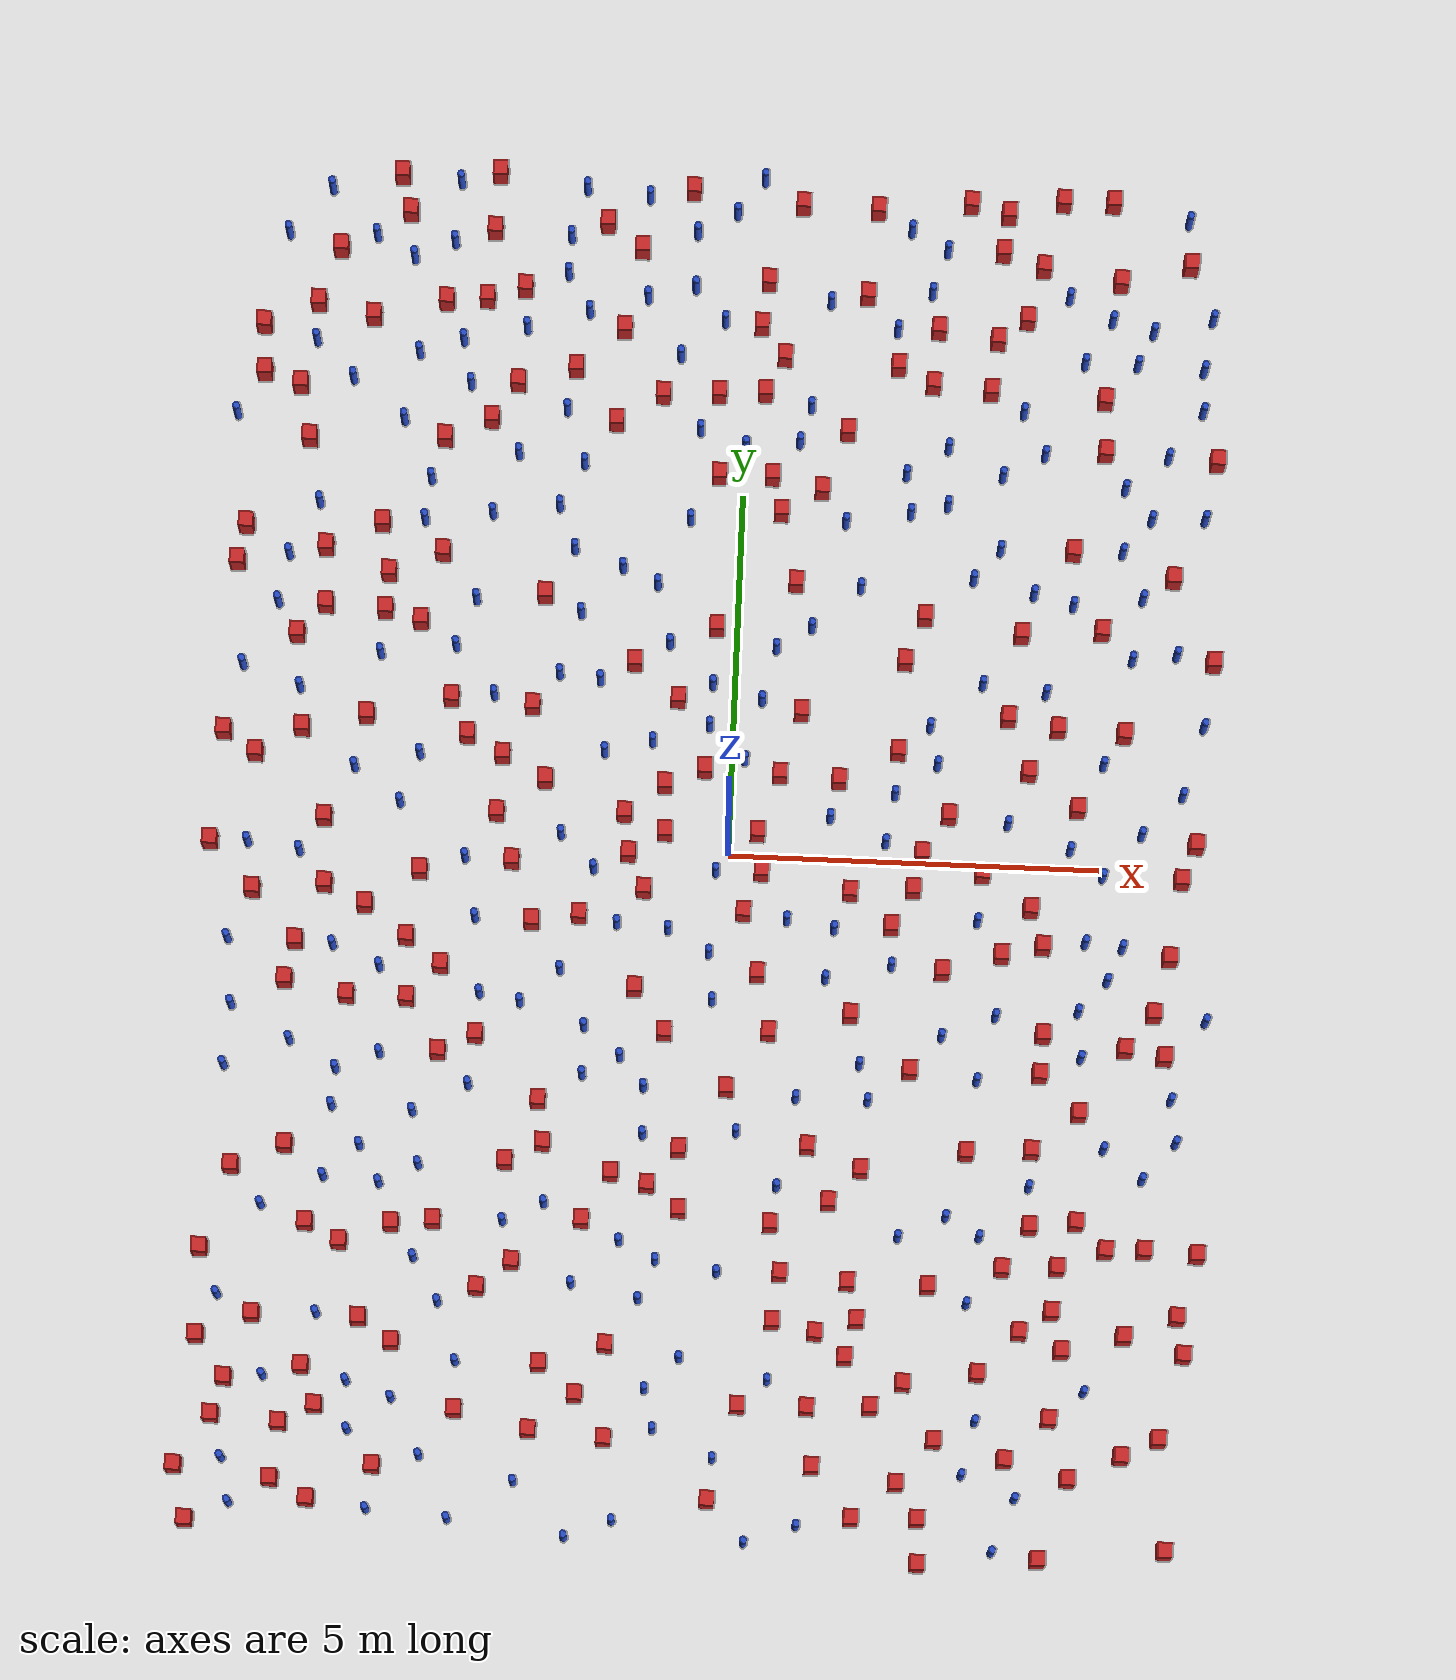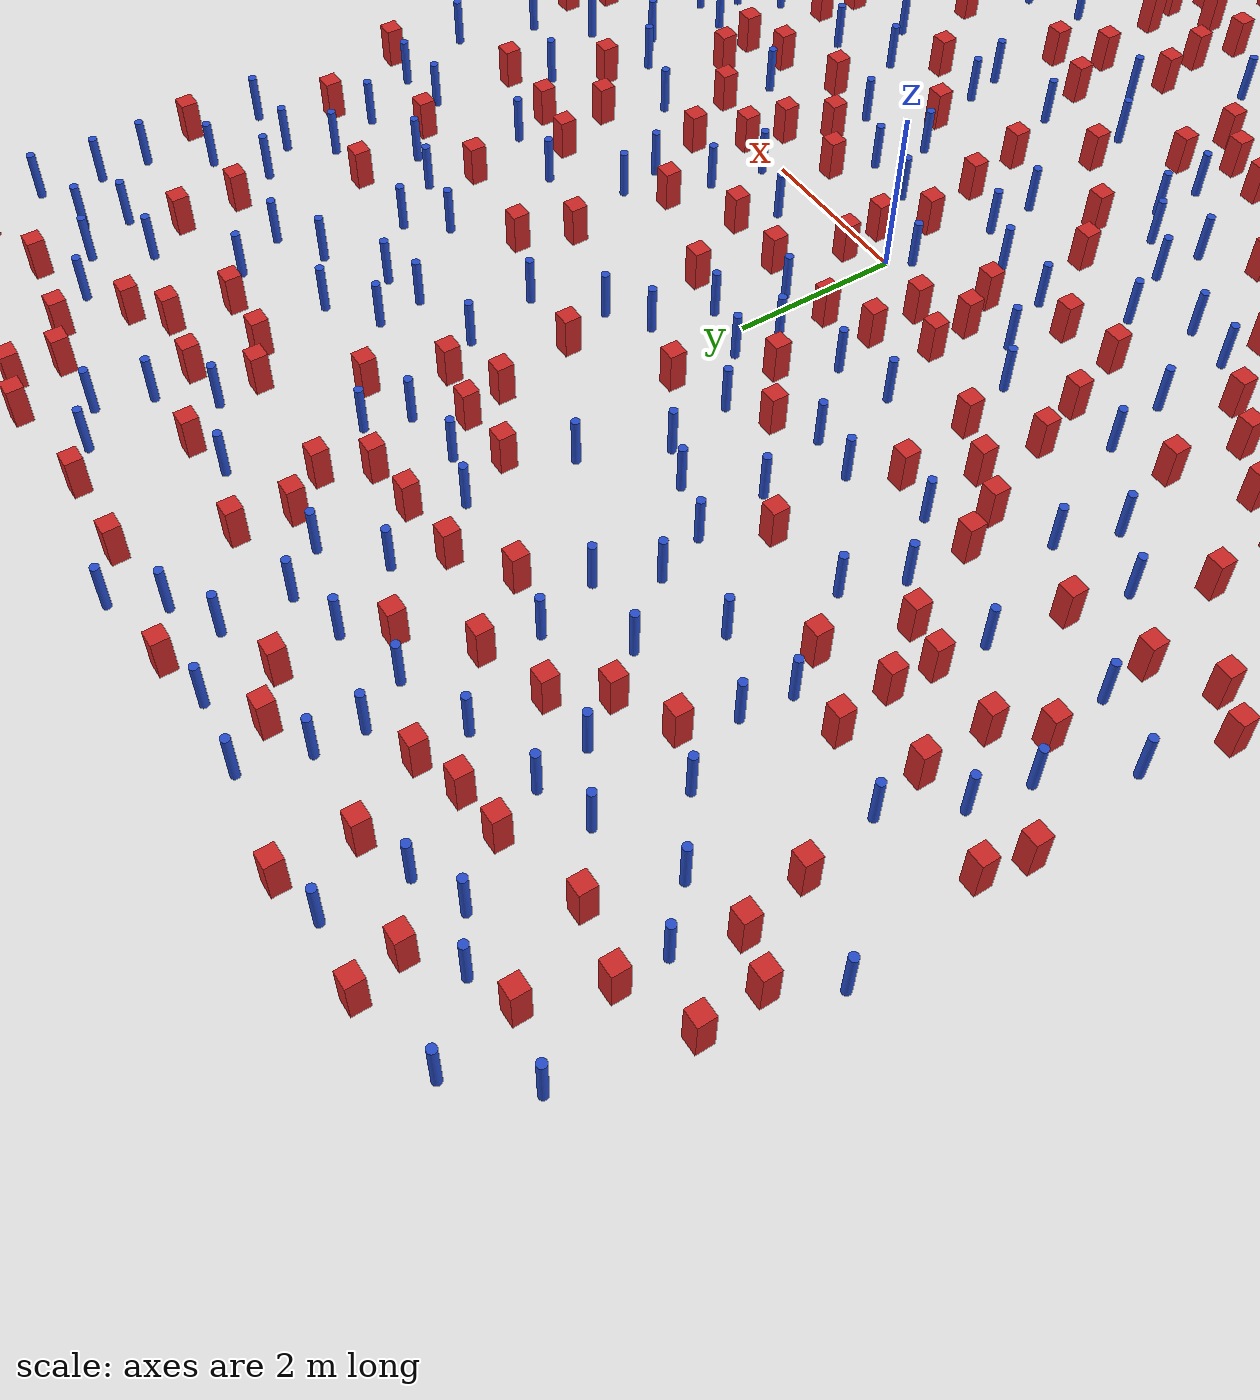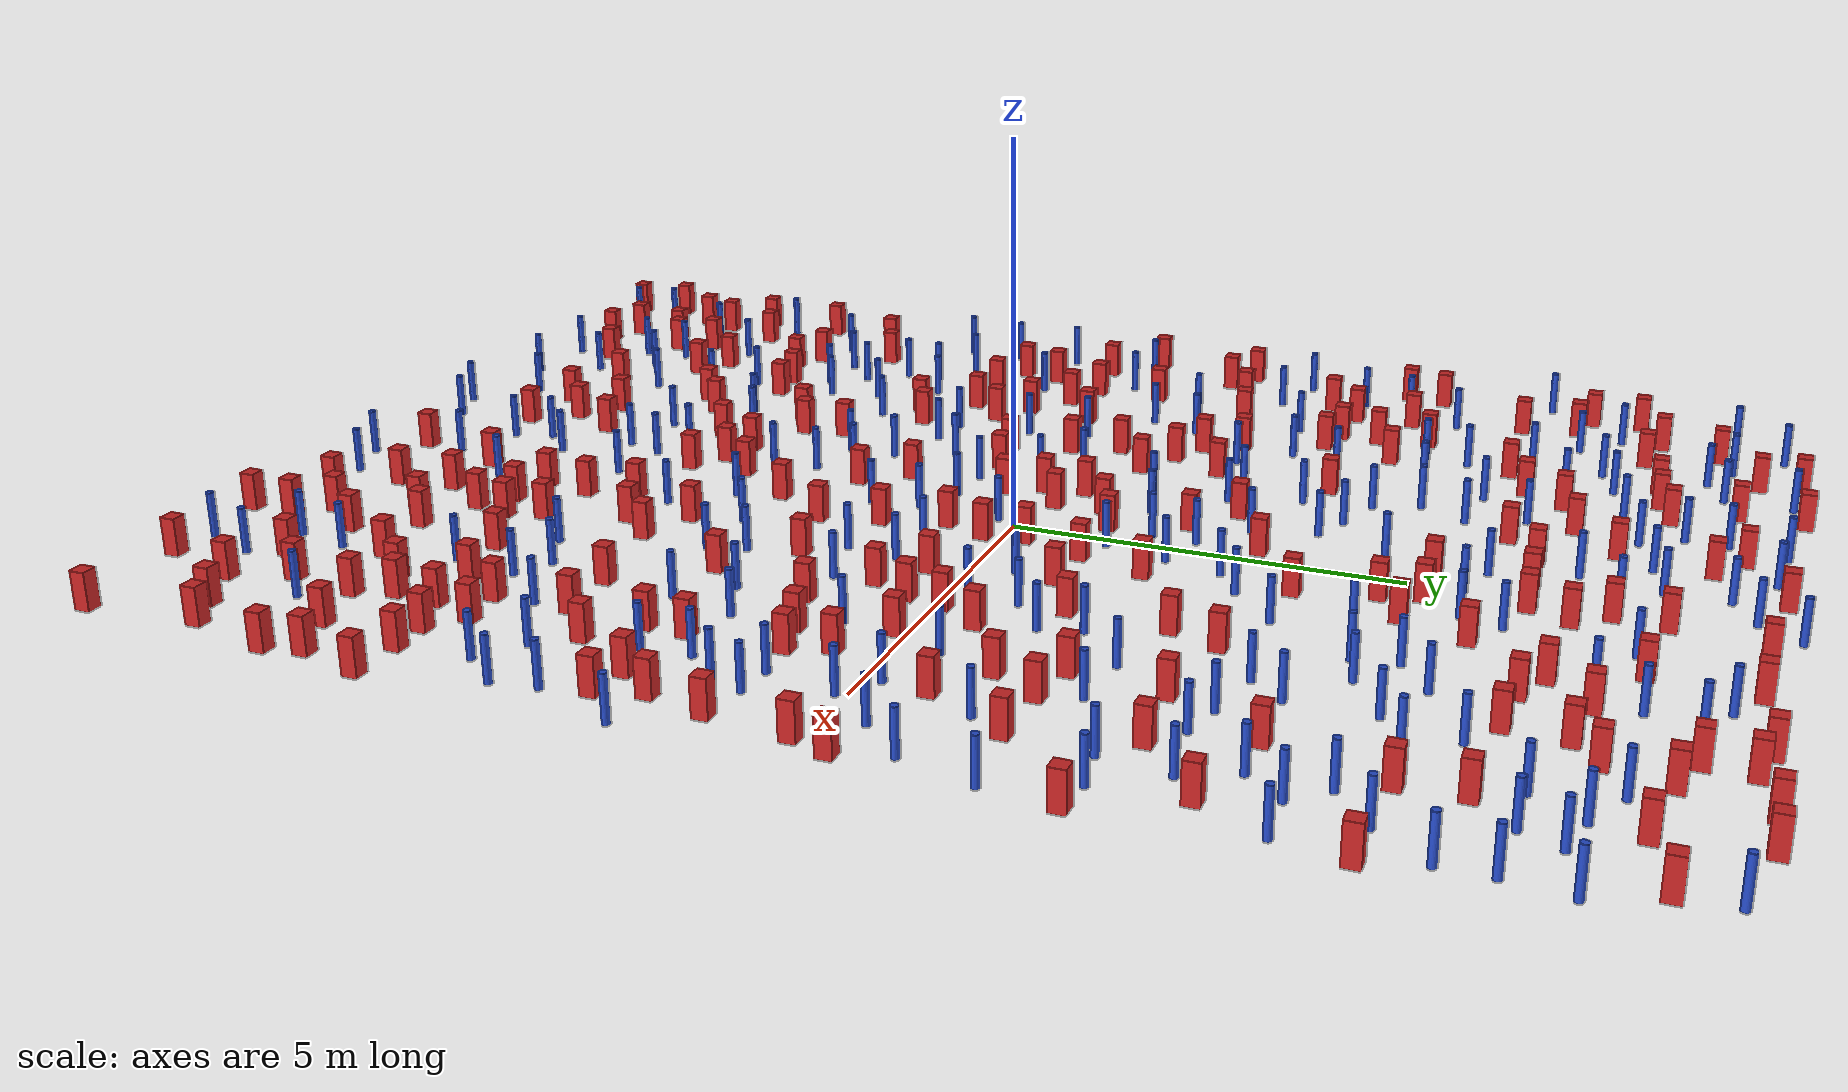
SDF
<sdf version="1.6">
  <model name="dense_69"><model name="pole_obstacle0">
  <static>true</static>
  <pose frame="">-0.767315382043 7.87782411559 7.38925637345e-09 -8.471706928e-08 1.24976765086e-08 -1.74513093015e-07</pose>
  <link name="link">
  <pose frame="">0 0 0.3 0 -0 0</pose>
    <inertial>
      <mass>1</mass>
      <inertia>
        <ixx>0.145833</ixx>
        <ixy>0</ixy>
        <ixz>0</ixz>
        <iyy>0.145833</iyy>
        <iyz>0</iyz>
        <izz>0.125</izz>
      </inertia>
    </inertial>
    <collision name="collision">
      <geometry>
        <cylinder>
          <radius>0.05</radius>
          <length>.6</length>
        </cylinder>
      </geometry>
      <max_contacts>10</max_contacts>
      <surface>
        <contact>
          <ode/>
        </contact>
        <bounce/>
        <friction>
          <torsional>
            <ode/>
          </torsional>
          <ode/>
        </friction>
      </surface>
    </collision>
    <visual name="visual">
      <geometry>
        <cylinder>
          <radius>0.05</radius>
          <length>.6</length>
        </cylinder>
      </geometry>
      <material>
        <script>
          <name>Gazebo/Blue</name>
          <uri>file://media/materials/scripts/gazebo.material</uri>
        </script>
      </material>
    </visual>
    <self_collide>0</self_collide>
    <kinematic>0</kinematic>
  </link>
</model>
<model name="pole_obstacle1">
  <static>true</static>
  <pose frame="">0.876120784257 6.24800217098 7.38925637345e-09 -8.471706928e-08 1.24976765086e-08 -1.74513093015e-07</pose>
  <link name="link">
  <pose frame="">0 0 0.3 0 -0 0</pose>
    <inertial>
      <mass>1</mass>
      <inertia>
        <ixx>0.145833</ixx>
        <ixy>0</ixy>
        <ixz>0</ixz>
        <iyy>0.145833</iyy>
        <iyz>0</iyz>
        <izz>0.125</izz>
      </inertia>
    </inertial>
    <collision name="collision">
      <geometry>
        <cylinder>
          <radius>0.05</radius>
          <length>.6</length>
        </cylinder>
      </geometry>
      <max_contacts>10</max_contacts>
      <surface>
        <contact>
          <ode/>
        </contact>
        <bounce/>
        <friction>
          <torsional>
            <ode/>
          </torsional>
          <ode/>
        </friction>
      </surface>
    </collision>
    <visual name="visual">
      <geometry>
        <cylinder>
          <radius>0.05</radius>
          <length>.6</length>
        </cylinder>
      </geometry>
      <material>
        <script>
          <name>Gazebo/Blue</name>
          <uri>file://media/materials/scripts/gazebo.material</uri>
        </script>
      </material>
    </visual>
    <self_collide>0</self_collide>
    <kinematic>0</kinematic>
  </link>
</model>
<model name="square_post_obstacle0">
  <static>true</static>
  <pose frame="">6.00057806063 -7.67909115086 1.91545236811e-07 -7.35059704564e-06 1.12565212e-07 2.39332434364e-05</pose>
  <link name="link">
    <pose frame="">0 0 0.25 0 -0 0</pose>
    <inertial>
      <mass>100</mass>
      <inertia>
        <ixx>0.166667</ixx>
        <ixy>0</ixy>
        <ixz>0</ixz>
        <iyy>0.166667</iyy>
        <iyz>0</iyz>
        <izz>0.166667</izz>
      </inertia>
    </inertial>
    <collision name="collision">
      <geometry>
        <box>
          <size>.2 .2 .5</size>
        </box>
      </geometry>
      <max_contacts>10</max_contacts>
      <surface>
        <contact>
          <ode/>
        </contact>
        <bounce/>
        <friction>
          <torsional>
            <ode/>
          </torsional>
          <ode/>
        </friction>
      </surface>
    </collision>
    <visual name="visual">
      <geometry>
        <box>
          <size>.2 .2 .5</size>
        </box>
      </geometry>
      <material>
        <script>
          <name>Gazebo/Red</name>
          <uri>file://media/materials/scripts/gazebo.material</uri>
        </script>
      </material>
    </visual>
    <self_collide>0</self_collide>
    <kinematic>0</kinematic>
  </link>
</model>
<model name="square_post_obstacle1">
  <static>true</static>
  <pose frame="">-3.82861871613 1.99735328516 1.91545236811e-07 -7.35059704564e-06 1.12565212e-07 2.39332434364e-05</pose>
  <link name="link">
    <pose frame="">0 0 0.25 0 -0 0</pose>
    <inertial>
      <mass>100</mass>
      <inertia>
        <ixx>0.166667</ixx>
        <ixy>0</ixy>
        <ixz>0</ixz>
        <iyy>0.166667</iyy>
        <iyz>0</iyz>
        <izz>0.166667</izz>
      </inertia>
    </inertial>
    <collision name="collision">
      <geometry>
        <box>
          <size>.2 .2 .5</size>
        </box>
      </geometry>
      <max_contacts>10</max_contacts>
      <surface>
        <contact>
          <ode/>
        </contact>
        <bounce/>
        <friction>
          <torsional>
            <ode/>
          </torsional>
          <ode/>
        </friction>
      </surface>
    </collision>
    <visual name="visual">
      <geometry>
        <box>
          <size>.2 .2 .5</size>
        </box>
      </geometry>
      <material>
        <script>
          <name>Gazebo/Red</name>
          <uri>file://media/materials/scripts/gazebo.material</uri>
        </script>
      </material>
    </visual>
    <self_collide>0</self_collide>
    <kinematic>0</kinematic>
  </link>
</model>
<model name="pole_obstacle2">
  <static>true</static>
  <pose frame="">3.77386475802 6.2816502501 7.38925637345e-09 -8.47170692798e-08 1.24976765033e-08 -1.74513093019e-07</pose>
  <link name="link">
  <pose frame="">0 0 0.3 0 -0 0</pose>
    <inertial>
      <mass>1</mass>
      <inertia>
        <ixx>0.145833</ixx>
        <ixy>0</ixy>
        <ixz>0</ixz>
        <iyy>0.145833</iyy>
        <iyz>0</iyz>
        <izz>0.125</izz>
      </inertia>
    </inertial>
    <collision name="collision">
      <geometry>
        <cylinder>
          <radius>0.05</radius>
          <length>.6</length>
        </cylinder>
      </geometry>
      <max_contacts>10</max_contacts>
      <surface>
        <contact>
          <ode/>
        </contact>
        <bounce/>
        <friction>
          <torsional>
            <ode/>
          </torsional>
          <ode/>
        </friction>
      </surface>
    </collision>
    <visual name="visual">
      <geometry>
        <cylinder>
          <radius>0.05</radius>
          <length>.6</length>
        </cylinder>
      </geometry>
      <material>
        <script>
          <name>Gazebo/Blue</name>
          <uri>file://media/materials/scripts/gazebo.material</uri>
        </script>
      </material>
    </visual>
    <self_collide>0</self_collide>
    <kinematic>0</kinematic>
  </link>
</model>
<model name="pole_obstacle3">
  <static>true</static>
  <pose frame="">1.36535453038 -1.66823402295 7.38925637345e-09 -8.471706928e-08 1.24976765079e-08 -1.74513093017e-07</pose>
  <link name="link">
  <pose frame="">0 0 0.3 0 -0 0</pose>
    <inertial>
      <mass>1</mass>
      <inertia>
        <ixx>0.145833</ixx>
        <ixy>0</ixy>
        <ixz>0</ixz>
        <iyy>0.145833</iyy>
        <iyz>0</iyz>
        <izz>0.125</izz>
      </inertia>
    </inertial>
    <collision name="collision">
      <geometry>
        <cylinder>
          <radius>0.05</radius>
          <length>.6</length>
        </cylinder>
      </geometry>
      <max_contacts>10</max_contacts>
      <surface>
        <contact>
          <ode/>
        </contact>
        <bounce/>
        <friction>
          <torsional>
            <ode/>
          </torsional>
          <ode/>
        </friction>
      </surface>
    </collision>
    <visual name="visual">
      <geometry>
        <cylinder>
          <radius>0.05</radius>
          <length>.6</length>
        </cylinder>
      </geometry>
      <material>
        <script>
          <name>Gazebo/Blue</name>
          <uri>file://media/materials/scripts/gazebo.material</uri>
        </script>
      </material>
    </visual>
    <self_collide>0</self_collide>
    <kinematic>0</kinematic>
  </link>
</model>
<model name="pole_obstacle4">
  <static>true</static>
  <pose frame="">-1.10873818178 3.6798783113 7.38925637345e-09 -8.47170692799e-08 1.24976765053e-08 -1.74513093017e-07</pose>
  <link name="link">
  <pose frame="">0 0 0.3 0 -0 0</pose>
    <inertial>
      <mass>1</mass>
      <inertia>
        <ixx>0.145833</ixx>
        <ixy>0</ixy>
        <ixz>0</ixz>
        <iyy>0.145833</iyy>
        <iyz>0</iyz>
        <izz>0.125</izz>
      </inertia>
    </inertial>
    <collision name="collision">
      <geometry>
        <cylinder>
          <radius>0.05</radius>
          <length>.6</length>
        </cylinder>
      </geometry>
      <max_contacts>10</max_contacts>
      <surface>
        <contact>
          <ode/>
        </contact>
        <bounce/>
        <friction>
          <torsional>
            <ode/>
          </torsional>
          <ode/>
        </friction>
      </surface>
    </collision>
    <visual name="visual">
      <geometry>
        <cylinder>
          <radius>0.05</radius>
          <length>.6</length>
        </cylinder>
      </geometry>
      <material>
        <script>
          <name>Gazebo/Blue</name>
          <uri>file://media/materials/scripts/gazebo.material</uri>
        </script>
      </material>
    </visual>
    <self_collide>0</self_collide>
    <kinematic>0</kinematic>
  </link>
</model>
<model name="pole_obstacle5">
  <static>true</static>
  <pose frame="">5.55673570257 4.84575330785 7.38925637345e-09 -8.47170692796e-08 1.24976764786e-08 -1.74513093032e-07</pose>
  <link name="link">
  <pose frame="">0 0 0.3 0 -0 0</pose>
    <inertial>
      <mass>1</mass>
      <inertia>
        <ixx>0.145833</ixx>
        <ixy>0</ixy>
        <ixz>0</ixz>
        <iyy>0.145833</iyy>
        <iyz>0</iyz>
        <izz>0.125</izz>
      </inertia>
    </inertial>
    <collision name="collision">
      <geometry>
        <cylinder>
          <radius>0.05</radius>
          <length>.6</length>
        </cylinder>
      </geometry>
      <max_contacts>10</max_contacts>
      <surface>
        <contact>
          <ode/>
        </contact>
        <bounce/>
        <friction>
          <torsional>
            <ode/>
          </torsional>
          <ode/>
        </friction>
      </surface>
    </collision>
    <visual name="visual">
      <geometry>
        <cylinder>
          <radius>0.05</radius>
          <length>.6</length>
        </cylinder>
      </geometry>
      <material>
        <script>
          <name>Gazebo/Blue</name>
          <uri>file://media/materials/scripts/gazebo.material</uri>
        </script>
      </material>
    </visual>
    <self_collide>0</self_collide>
    <kinematic>0</kinematic>
  </link>
</model>
<model name="pole_obstacle6">
  <static>true</static>
  <pose frame="">-2.26504879221 -4.85748227697 7.38925637345e-09 -8.47170692798e-08 1.24976765033e-08 -1.74513093019e-07</pose>
  <link name="link">
  <pose frame="">0 0 0.3 0 -0 0</pose>
    <inertial>
      <mass>1</mass>
      <inertia>
        <ixx>0.145833</ixx>
        <ixy>0</ixy>
        <ixz>0</ixz>
        <iyy>0.145833</iyy>
        <iyz>0</iyz>
        <izz>0.125</izz>
      </inertia>
    </inertial>
    <collision name="collision">
      <geometry>
        <cylinder>
          <radius>0.05</radius>
          <length>.6</length>
        </cylinder>
      </geometry>
      <max_contacts>10</max_contacts>
      <surface>
        <contact>
          <ode/>
        </contact>
        <bounce/>
        <friction>
          <torsional>
            <ode/>
          </torsional>
          <ode/>
        </friction>
      </surface>
    </collision>
    <visual name="visual">
      <geometry>
        <cylinder>
          <radius>0.05</radius>
          <length>.6</length>
        </cylinder>
      </geometry>
      <material>
        <script>
          <name>Gazebo/Blue</name>
          <uri>file://media/materials/scripts/gazebo.material</uri>
        </script>
      </material>
    </visual>
    <self_collide>0</self_collide>
    <kinematic>0</kinematic>
  </link>
</model>
<model name="square_post_obstacle2">
  <static>true</static>
  <pose frame="">-0.89729398552 0.916109627229 1.91545236811e-07 -7.35059704564e-06 1.12565212e-07 2.39332434364e-05</pose>
  <link name="link">
    <pose frame="">0 0 0.25 0 -0 0</pose>
    <inertial>
      <mass>100</mass>
      <inertia>
        <ixx>0.166667</ixx>
        <ixy>0</ixy>
        <ixz>0</ixz>
        <iyy>0.166667</iyy>
        <iyz>0</iyz>
        <izz>0.166667</izz>
      </inertia>
    </inertial>
    <collision name="collision">
      <geometry>
        <box>
          <size>.2 .2 .5</size>
        </box>
      </geometry>
      <max_contacts>10</max_contacts>
      <surface>
        <contact>
          <ode/>
        </contact>
        <bounce/>
        <friction>
          <torsional>
            <ode/>
          </torsional>
          <ode/>
        </friction>
      </surface>
    </collision>
    <visual name="visual">
      <geometry>
        <box>
          <size>.2 .2 .5</size>
        </box>
      </geometry>
      <material>
        <script>
          <name>Gazebo/Red</name>
          <uri>file://media/materials/scripts/gazebo.material</uri>
        </script>
      </material>
    </visual>
    <self_collide>0</self_collide>
    <kinematic>0</kinematic>
  </link>
</model>
<model name="square_post_obstacle3">
  <static>true</static>
  <pose frame="">0.450205299994 -1.62794574472 1.91545236811e-07 -7.35059704564e-06 1.12565212e-07 2.39332434364e-05</pose>
  <link name="link">
    <pose frame="">0 0 0.25 0 -0 0</pose>
    <inertial>
      <mass>100</mass>
      <inertia>
        <ixx>0.166667</ixx>
        <ixy>0</ixy>
        <ixz>0</ixz>
        <iyy>0.166667</iyy>
        <iyz>0</iyz>
        <izz>0.166667</izz>
      </inertia>
    </inertial>
    <collision name="collision">
      <geometry>
        <box>
          <size>.2 .2 .5</size>
        </box>
      </geometry>
      <max_contacts>10</max_contacts>
      <surface>
        <contact>
          <ode/>
        </contact>
        <bounce/>
        <friction>
          <torsional>
            <ode/>
          </torsional>
          <ode/>
        </friction>
      </surface>
    </collision>
    <visual name="visual">
      <geometry>
        <box>
          <size>.2 .2 .5</size>
        </box>
      </geometry>
      <material>
        <script>
          <name>Gazebo/Red</name>
          <uri>file://media/materials/scripts/gazebo.material</uri>
        </script>
      </material>
    </visual>
    <self_collide>0</self_collide>
    <kinematic>0</kinematic>
  </link>
</model>
<model name="square_post_obstacle4">
  <static>true</static>
  <pose frame="">-4.2030178979 -6.79372922188 1.91545236811e-07 -7.35059704564e-06 1.12565212e-07 2.39332434364e-05</pose>
  <link name="link">
    <pose frame="">0 0 0.25 0 -0 0</pose>
    <inertial>
      <mass>100</mass>
      <inertia>
        <ixx>0.166667</ixx>
        <ixy>0</ixy>
        <ixz>0</ixz>
        <iyy>0.166667</iyy>
        <iyz>0</iyz>
        <izz>0.166667</izz>
      </inertia>
    </inertial>
    <collision name="collision">
      <geometry>
        <box>
          <size>.2 .2 .5</size>
        </box>
      </geometry>
      <max_contacts>10</max_contacts>
      <surface>
        <contact>
          <ode/>
        </contact>
        <bounce/>
        <friction>
          <torsional>
            <ode/>
          </torsional>
          <ode/>
        </friction>
      </surface>
    </collision>
    <visual name="visual">
      <geometry>
        <box>
          <size>.2 .2 .5</size>
        </box>
      </geometry>
      <material>
        <script>
          <name>Gazebo/Red</name>
          <uri>file://media/materials/scripts/gazebo.material</uri>
        </script>
      </material>
    </visual>
    <self_collide>0</self_collide>
    <kinematic>0</kinematic>
  </link>
</model>
<model name="pole_obstacle7">
  <static>true</static>
  <pose frame="">0.532441098875 2.85423462872 7.38925637345e-09 -8.471706928e-08 1.2497676512e-08 -1.74513093015e-07</pose>
  <link name="link">
  <pose frame="">0 0 0.3 0 -0 0</pose>
    <inertial>
      <mass>1</mass>
      <inertia>
        <ixx>0.145833</ixx>
        <ixy>0</ixy>
        <ixz>0</ixz>
        <iyy>0.145833</iyy>
        <iyz>0</iyz>
        <izz>0.125</izz>
      </inertia>
    </inertial>
    <collision name="collision">
      <geometry>
        <cylinder>
          <radius>0.05</radius>
          <length>.6</length>
        </cylinder>
      </geometry>
      <max_contacts>10</max_contacts>
      <surface>
        <contact>
          <ode/>
        </contact>
        <bounce/>
        <friction>
          <torsional>
            <ode/>
          </torsional>
          <ode/>
        </friction>
      </surface>
    </collision>
    <visual name="visual">
      <geometry>
        <cylinder>
          <radius>0.05</radius>
          <length>.6</length>
        </cylinder>
      </geometry>
      <material>
        <script>
          <name>Gazebo/Blue</name>
          <uri>file://media/materials/scripts/gazebo.material</uri>
        </script>
      </material>
    </visual>
    <self_collide>0</self_collide>
    <kinematic>0</kinematic>
  </link>
</model>
<model name="pole_obstacle8">
  <static>true</static>
  <pose frame="">-1.8065690611 -0.287226070218 7.38925637345e-09 -8.47170692798e-08 1.24976764989e-08 -1.74513093022e-07</pose>
  <link name="link">
  <pose frame="">0 0 0.3 0 -0 0</pose>
    <inertial>
      <mass>1</mass>
      <inertia>
        <ixx>0.145833</ixx>
        <ixy>0</ixy>
        <ixz>0</ixz>
        <iyy>0.145833</iyy>
        <iyz>0</iyz>
        <izz>0.125</izz>
      </inertia>
    </inertial>
    <collision name="collision">
      <geometry>
        <cylinder>
          <radius>0.05</radius>
          <length>.6</length>
        </cylinder>
      </geometry>
      <max_contacts>10</max_contacts>
      <surface>
        <contact>
          <ode/>
        </contact>
        <bounce/>
        <friction>
          <torsional>
            <ode/>
          </torsional>
          <ode/>
        </friction>
      </surface>
    </collision>
    <visual name="visual">
      <geometry>
        <cylinder>
          <radius>0.05</radius>
          <length>.6</length>
        </cylinder>
      </geometry>
      <material>
        <script>
          <name>Gazebo/Blue</name>
          <uri>file://media/materials/scripts/gazebo.material</uri>
        </script>
      </material>
    </visual>
    <self_collide>0</self_collide>
    <kinematic>0</kinematic>
  </link>
</model>
<model name="square_post_obstacle5">
  <static>true</static>
  <pose frame="">-5.03799725201 -2.14161699042 1.91545236811e-07 -7.35059704564e-06 1.12565212e-07 2.39332434364e-05</pose>
  <link name="link">
    <pose frame="">0 0 0.25 0 -0 0</pose>
    <inertial>
      <mass>100</mass>
      <inertia>
        <ixx>0.166667</ixx>
        <ixy>0</ixy>
        <ixz>0</ixz>
        <iyy>0.166667</iyy>
        <iyz>0</iyz>
        <izz>0.166667</izz>
      </inertia>
    </inertial>
    <collision name="collision">
      <geometry>
        <box>
          <size>.2 .2 .5</size>
        </box>
      </geometry>
      <max_contacts>10</max_contacts>
      <surface>
        <contact>
          <ode/>
        </contact>
        <bounce/>
        <friction>
          <torsional>
            <ode/>
          </torsional>
          <ode/>
        </friction>
      </surface>
    </collision>
    <visual name="visual">
      <geometry>
        <box>
          <size>.2 .2 .5</size>
        </box>
      </geometry>
      <material>
        <script>
          <name>Gazebo/Red</name>
          <uri>file://media/materials/scripts/gazebo.material</uri>
        </script>
      </material>
    </visual>
    <self_collide>0</self_collide>
    <kinematic>0</kinematic>
  </link>
</model>
<model name="square_post_obstacle6">
  <static>true</static>
  <pose frame="">4.81548271422 -8.25875250711 1.91545236811e-07 -7.35059704564e-06 1.12565212e-07 2.39332434364e-05</pose>
  <link name="link">
    <pose frame="">0 0 0.25 0 -0 0</pose>
    <inertial>
      <mass>100</mass>
      <inertia>
        <ixx>0.166667</ixx>
        <ixy>0</ixy>
        <ixz>0</ixz>
        <iyy>0.166667</iyy>
        <iyz>0</iyz>
        <izz>0.166667</izz>
      </inertia>
    </inertial>
    <collision name="collision">
      <geometry>
        <box>
          <size>.2 .2 .5</size>
        </box>
      </geometry>
      <max_contacts>10</max_contacts>
      <surface>
        <contact>
          <ode/>
        </contact>
        <bounce/>
        <friction>
          <torsional>
            <ode/>
          </torsional>
          <ode/>
        </friction>
      </surface>
    </collision>
    <visual name="visual">
      <geometry>
        <box>
          <size>.2 .2 .5</size>
        </box>
      </geometry>
      <material>
        <script>
          <name>Gazebo/Red</name>
          <uri>file://media/materials/scripts/gazebo.material</uri>
        </script>
      </material>
    </visual>
    <self_collide>0</self_collide>
    <kinematic>0</kinematic>
  </link>
</model>
<model name="square_post_obstacle7">
  <static>true</static>
  <pose frame="">0.069519349708 -8.7268812761 1.91545236811e-07 -7.35059704564e-06 1.12565212e-07 2.39332434364e-05</pose>
  <link name="link">
    <pose frame="">0 0 0.25 0 -0 0</pose>
    <inertial>
      <mass>100</mass>
      <inertia>
        <ixx>0.166667</ixx>
        <ixy>0</ixy>
        <ixz>0</ixz>
        <iyy>0.166667</iyy>
        <iyz>0</iyz>
        <izz>0.166667</izz>
      </inertia>
    </inertial>
    <collision name="collision">
      <geometry>
        <box>
          <size>.2 .2 .5</size>
        </box>
      </geometry>
      <max_contacts>10</max_contacts>
      <surface>
        <contact>
          <ode/>
        </contact>
        <bounce/>
        <friction>
          <torsional>
            <ode/>
          </torsional>
          <ode/>
        </friction>
      </surface>
    </collision>
    <visual name="visual">
      <geometry>
        <box>
          <size>.2 .2 .5</size>
        </box>
      </geometry>
      <material>
        <script>
          <name>Gazebo/Red</name>
          <uri>file://media/materials/scripts/gazebo.material</uri>
        </script>
      </material>
    </visual>
    <self_collide>0</self_collide>
    <kinematic>0</kinematic>
  </link>
</model>
<model name="pole_obstacle9">
  <static>true</static>
  <pose frame="">1.00213003306 3.16016807771 7.38925637345e-09 -8.471706928e-08 1.2497676505e-08 -1.74513093017e-07</pose>
  <link name="link">
  <pose frame="">0 0 0.3 0 -0 0</pose>
    <inertial>
      <mass>1</mass>
      <inertia>
        <ixx>0.145833</ixx>
        <ixy>0</ixy>
        <ixz>0</ixz>
        <iyy>0.145833</iyy>
        <iyz>0</iyz>
        <izz>0.125</izz>
      </inertia>
    </inertial>
    <collision name="collision">
      <geometry>
        <cylinder>
          <radius>0.05</radius>
          <length>.6</length>
        </cylinder>
      </geometry>
      <max_contacts>10</max_contacts>
      <surface>
        <contact>
          <ode/>
        </contact>
        <bounce/>
        <friction>
          <torsional>
            <ode/>
          </torsional>
          <ode/>
        </friction>
      </surface>
    </collision>
    <visual name="visual">
      <geometry>
        <cylinder>
          <radius>0.05</radius>
          <length>.6</length>
        </cylinder>
      </geometry>
      <material>
        <script>
          <name>Gazebo/Blue</name>
          <uri>file://media/materials/scripts/gazebo.material</uri>
        </script>
      </material>
    </visual>
    <self_collide>0</self_collide>
    <kinematic>0</kinematic>
  </link>
</model>
<model name="pole_obstacle10">
  <static>true</static>
  <pose frame="">-5.77082774487 -2.78743568391 7.38925637345e-09 -8.47170692798e-08 1.24976764937e-08 -1.74513093023e-07</pose>
  <link name="link">
  <pose frame="">0 0 0.3 0 -0 0</pose>
    <inertial>
      <mass>1</mass>
      <inertia>
        <ixx>0.145833</ixx>
        <ixy>0</ixy>
        <ixz>0</ixz>
        <iyy>0.145833</iyy>
        <iyz>0</iyz>
        <izz>0.125</izz>
      </inertia>
    </inertial>
    <collision name="collision">
      <geometry>
        <cylinder>
          <radius>0.05</radius>
          <length>.6</length>
        </cylinder>
      </geometry>
      <max_contacts>10</max_contacts>
      <surface>
        <contact>
          <ode/>
        </contact>
        <bounce/>
        <friction>
          <torsional>
            <ode/>
          </torsional>
          <ode/>
        </friction>
      </surface>
    </collision>
    <visual name="visual">
      <geometry>
        <cylinder>
          <radius>0.05</radius>
          <length>.6</length>
        </cylinder>
      </geometry>
      <material>
        <script>
          <name>Gazebo/Blue</name>
          <uri>file://media/materials/scripts/gazebo.material</uri>
        </script>
      </material>
    </visual>
    <self_collide>0</self_collide>
    <kinematic>0</kinematic>
  </link>
</model>
<model name="pole_obstacle11">
  <static>true</static>
  <pose frame="">-3.04624879508 7.21075002318 7.38925637345e-09 -8.47170692798e-08 1.24976765033e-08 -1.74513093019e-07</pose>
  <link name="link">
  <pose frame="">0 0 0.3 0 -0 0</pose>
    <inertial>
      <mass>1</mass>
      <inertia>
        <ixx>0.145833</ixx>
        <ixy>0</ixy>
        <ixz>0</ixz>
        <iyy>0.145833</iyy>
        <iyz>0</iyz>
        <izz>0.125</izz>
      </inertia>
    </inertial>
    <collision name="collision">
      <geometry>
        <cylinder>
          <radius>0.05</radius>
          <length>.6</length>
        </cylinder>
      </geometry>
      <max_contacts>10</max_contacts>
      <surface>
        <contact>
          <ode/>
        </contact>
        <bounce/>
        <friction>
          <torsional>
            <ode/>
          </torsional>
          <ode/>
        </friction>
      </surface>
    </collision>
    <visual name="visual">
      <geometry>
        <cylinder>
          <radius>0.05</radius>
          <length>.6</length>
        </cylinder>
      </geometry>
      <material>
        <script>
          <name>Gazebo/Blue</name>
          <uri>file://media/materials/scripts/gazebo.material</uri>
        </script>
      </material>
    </visual>
    <self_collide>0</self_collide>
    <kinematic>0</kinematic>
  </link>
</model>
<model name="pole_obstacle12">
  <static>true</static>
  <pose frame="">4.83359117954 -1.04137075191 7.38925637345e-09 -8.471706928e-08 1.24976765101e-08 -1.74513093015e-07</pose>
  <link name="link">
  <pose frame="">0 0 0.3 0 -0 0</pose>
    <inertial>
      <mass>1</mass>
      <inertia>
        <ixx>0.145833</ixx>
        <ixy>0</ixy>
        <ixz>0</ixz>
        <iyy>0.145833</iyy>
        <iyz>0</iyz>
        <izz>0.125</izz>
      </inertia>
    </inertial>
    <collision name="collision">
      <geometry>
        <cylinder>
          <radius>0.05</radius>
          <length>.6</length>
        </cylinder>
      </geometry>
      <max_contacts>10</max_contacts>
      <surface>
        <contact>
          <ode/>
        </contact>
        <bounce/>
        <friction>
          <torsional>
            <ode/>
          </torsional>
          <ode/>
        </friction>
      </surface>
    </collision>
    <visual name="visual">
      <geometry>
        <cylinder>
          <radius>0.05</radius>
          <length>.6</length>
        </cylinder>
      </geometry>
      <material>
        <script>
          <name>Gazebo/Blue</name>
          <uri>file://media/materials/scripts/gazebo.material</uri>
        </script>
      </material>
    </visual>
    <self_collide>0</self_collide>
    <kinematic>0</kinematic>
  </link>
</model>
<model name="square_post_obstacle8">
  <static>true</static>
  <pose frame="">-5.2184283776 -8.92105118813 1.91545236811e-07 -7.35059704564e-06 1.12565212e-07 2.39332434364e-05</pose>
  <link name="link">
    <pose frame="">0 0 0.25 0 -0 0</pose>
    <inertial>
      <mass>100</mass>
      <inertia>
        <ixx>0.166667</ixx>
        <ixy>0</ixy>
        <ixz>0</ixz>
        <iyy>0.166667</iyy>
        <iyz>0</iyz>
        <izz>0.166667</izz>
      </inertia>
    </inertial>
    <collision name="collision">
      <geometry>
        <box>
          <size>.2 .2 .5</size>
        </box>
      </geometry>
      <max_contacts>10</max_contacts>
      <surface>
        <contact>
          <ode/>
        </contact>
        <bounce/>
        <friction>
          <torsional>
            <ode/>
          </torsional>
          <ode/>
        </friction>
      </surface>
    </collision>
    <visual name="visual">
      <geometry>
        <box>
          <size>.2 .2 .5</size>
        </box>
      </geometry>
      <material>
        <script>
          <name>Gazebo/Red</name>
          <uri>file://media/materials/scripts/gazebo.material</uri>
        </script>
      </material>
    </visual>
    <self_collide>0</self_collide>
    <kinematic>0</kinematic>
  </link>
</model>
<model name="square_post_obstacle9">
  <static>true</static>
  <pose frame="">-4.14083173612 -0.40034103166 1.91545236811e-07 -7.35059704564e-06 1.12565212e-07 2.39332434364e-05</pose>
  <link name="link">
    <pose frame="">0 0 0.25 0 -0 0</pose>
    <inertial>
      <mass>100</mass>
      <inertia>
        <ixx>0.166667</ixx>
        <ixy>0</ixy>
        <ixz>0</ixz>
        <iyy>0.166667</iyy>
        <iyz>0</iyz>
        <izz>0.166667</izz>
      </inertia>
    </inertial>
    <collision name="collision">
      <geometry>
        <box>
          <size>.2 .2 .5</size>
        </box>
      </geometry>
      <max_contacts>10</max_contacts>
      <surface>
        <contact>
          <ode/>
        </contact>
        <bounce/>
        <friction>
          <torsional>
            <ode/>
          </torsional>
          <ode/>
        </friction>
      </surface>
    </collision>
    <visual name="visual">
      <geometry>
        <box>
          <size>.2 .2 .5</size>
        </box>
      </geometry>
      <material>
        <script>
          <name>Gazebo/Red</name>
          <uri>file://media/materials/scripts/gazebo.material</uri>
        </script>
      </material>
    </visual>
    <self_collide>0</self_collide>
    <kinematic>0</kinematic>
  </link>
</model>
<model name="pole_obstacle13">
  <static>true</static>
  <pose frame="">-5.8833607309 -7.31371165673 7.38925637345e-09 -8.47170692796e-08 1.24976764786e-08 -1.74513093032e-07</pose>
  <link name="link">
  <pose frame="">0 0 0.3 0 -0 0</pose>
    <inertial>
      <mass>1</mass>
      <inertia>
        <ixx>0.145833</ixx>
        <ixy>0</ixy>
        <ixz>0</ixz>
        <iyy>0.145833</iyy>
        <iyz>0</iyz>
        <izz>0.125</izz>
      </inertia>
    </inertial>
    <collision name="collision">
      <geometry>
        <cylinder>
          <radius>0.05</radius>
          <length>.6</length>
        </cylinder>
      </geometry>
      <max_contacts>10</max_contacts>
      <surface>
        <contact>
          <ode/>
        </contact>
        <bounce/>
        <friction>
          <torsional>
            <ode/>
          </torsional>
          <ode/>
        </friction>
      </surface>
    </collision>
    <visual name="visual">
      <geometry>
        <cylinder>
          <radius>0.05</radius>
          <length>.6</length>
        </cylinder>
      </geometry>
      <material>
        <script>
          <name>Gazebo/Blue</name>
          <uri>file://media/materials/scripts/gazebo.material</uri>
        </script>
      </material>
    </visual>
    <self_collide>0</self_collide>
    <kinematic>0</kinematic>
  </link>
</model>
<model name="square_post_obstacle10">
  <static>true</static>
  <pose frame="">5.04197095546 8.18872532669 1.91545236811e-07 -7.35059704564e-06 1.12565212e-07 2.39332434364e-05</pose>
  <link name="link">
    <pose frame="">0 0 0.25 0 -0 0</pose>
    <inertial>
      <mass>100</mass>
      <inertia>
        <ixx>0.166667</ixx>
        <ixy>0</ixy>
        <ixz>0</ixz>
        <iyy>0.166667</iyy>
        <iyz>0</iyz>
        <izz>0.166667</izz>
      </inertia>
    </inertial>
    <collision name="collision">
      <geometry>
        <box>
          <size>.2 .2 .5</size>
        </box>
      </geometry>
      <max_contacts>10</max_contacts>
      <surface>
        <contact>
          <ode/>
        </contact>
        <bounce/>
        <friction>
          <torsional>
            <ode/>
          </torsional>
          <ode/>
        </friction>
      </surface>
    </collision>
    <visual name="visual">
      <geometry>
        <box>
          <size>.2 .2 .5</size>
        </box>
      </geometry>
      <material>
        <script>
          <name>Gazebo/Red</name>
          <uri>file://media/materials/scripts/gazebo.material</uri>
        </script>
      </material>
    </visual>
    <self_collide>0</self_collide>
    <kinematic>0</kinematic>
  </link>
</model>
<model name="square_post_obstacle11">
  <static>true</static>
  <pose frame="">2.8487803578 -8.86418214256 1.91545236811e-07 -7.35059704564e-06 1.12565212e-07 2.39332434364e-05</pose>
  <link name="link">
    <pose frame="">0 0 0.25 0 -0 0</pose>
    <inertial>
      <mass>100</mass>
      <inertia>
        <ixx>0.166667</ixx>
        <ixy>0</ixy>
        <ixz>0</ixz>
        <iyy>0.166667</iyy>
        <iyz>0</iyz>
        <izz>0.166667</izz>
      </inertia>
    </inertial>
    <collision name="collision">
      <geometry>
        <box>
          <size>.2 .2 .5</size>
        </box>
      </geometry>
      <max_contacts>10</max_contacts>
      <surface>
        <contact>
          <ode/>
        </contact>
        <bounce/>
        <friction>
          <torsional>
            <ode/>
          </torsional>
          <ode/>
        </friction>
      </surface>
    </collision>
    <visual name="visual">
      <geometry>
        <box>
          <size>.2 .2 .5</size>
        </box>
      </geometry>
      <material>
        <script>
          <name>Gazebo/Red</name>
          <uri>file://media/materials/scripts/gazebo.material</uri>
        </script>
      </material>
    </visual>
    <self_collide>0</self_collide>
    <kinematic>0</kinematic>
  </link>
</model>
<model name="pole_obstacle14">
  <static>true</static>
  <pose frame="">-3.2540493623 2.05309047934 7.38925637345e-09 -8.471706928e-08 1.24976765098e-08 -1.74513093016e-07</pose>
  <link name="link">
  <pose frame="">0 0 0.3 0 -0 0</pose>
    <inertial>
      <mass>1</mass>
      <inertia>
        <ixx>0.145833</ixx>
        <ixy>0</ixy>
        <ixz>0</ixz>
        <iyy>0.145833</iyy>
        <iyz>0</iyz>
        <izz>0.125</izz>
      </inertia>
    </inertial>
    <collision name="collision">
      <geometry>
        <cylinder>
          <radius>0.05</radius>
          <length>.6</length>
        </cylinder>
      </geometry>
      <max_contacts>10</max_contacts>
      <surface>
        <contact>
          <ode/>
        </contact>
        <bounce/>
        <friction>
          <torsional>
            <ode/>
          </torsional>
          <ode/>
        </friction>
      </surface>
    </collision>
    <visual name="visual">
      <geometry>
        <cylinder>
          <radius>0.05</radius>
          <length>.6</length>
        </cylinder>
      </geometry>
      <material>
        <script>
          <name>Gazebo/Blue</name>
          <uri>file://media/materials/scripts/gazebo.material</uri>
        </script>
      </material>
    </visual>
    <self_collide>0</self_collide>
    <kinematic>0</kinematic>
  </link>
</model>
<model name="pole_obstacle15">
  <static>true</static>
  <pose frame="">3.44114598917 -2.97209151565 7.38925637345e-09 -8.47170692798e-08 1.24976764939e-08 -1.74513093025e-07</pose>
  <link name="link">
  <pose frame="">0 0 0.3 0 -0 0</pose>
    <inertial>
      <mass>1</mass>
      <inertia>
        <ixx>0.145833</ixx>
        <ixy>0</ixy>
        <ixz>0</ixz>
        <iyy>0.145833</iyy>
        <iyz>0</iyz>
        <izz>0.125</izz>
      </inertia>
    </inertial>
    <collision name="collision">
      <geometry>
        <cylinder>
          <radius>0.05</radius>
          <length>.6</length>
        </cylinder>
      </geometry>
      <max_contacts>10</max_contacts>
      <surface>
        <contact>
          <ode/>
        </contact>
        <bounce/>
        <friction>
          <torsional>
            <ode/>
          </torsional>
          <ode/>
        </friction>
      </surface>
    </collision>
    <visual name="visual">
      <geometry>
        <cylinder>
          <radius>0.05</radius>
          <length>.6</length>
        </cylinder>
      </geometry>
      <material>
        <script>
          <name>Gazebo/Blue</name>
          <uri>file://media/materials/scripts/gazebo.material</uri>
        </script>
      </material>
    </visual>
    <self_collide>0</self_collide>
    <kinematic>0</kinematic>
  </link>
</model>
<model name="square_post_obstacle12">
  <static>true</static>
  <pose frame="">-5.38060062174 -7.15914760359 1.91545236811e-07 -7.35059704564e-06 1.12565212e-07 2.39332434364e-05</pose>
  <link name="link">
    <pose frame="">0 0 0.25 0 -0 0</pose>
    <inertial>
      <mass>100</mass>
      <inertia>
        <ixx>0.166667</ixx>
        <ixy>0</ixy>
        <ixz>0</ixz>
        <iyy>0.166667</iyy>
        <iyz>0</iyz>
        <izz>0.166667</izz>
      </inertia>
    </inertial>
    <collision name="collision">
      <geometry>
        <box>
          <size>.2 .2 .5</size>
        </box>
      </geometry>
      <max_contacts>10</max_contacts>
      <surface>
        <contact>
          <ode/>
        </contact>
        <bounce/>
        <friction>
          <torsional>
            <ode/>
          </torsional>
          <ode/>
        </friction>
      </surface>
    </collision>
    <visual name="visual">
      <geometry>
        <box>
          <size>.2 .2 .5</size>
        </box>
      </geometry>
      <material>
        <script>
          <name>Gazebo/Red</name>
          <uri>file://media/materials/scripts/gazebo.material</uri>
        </script>
      </material>
    </visual>
    <self_collide>0</self_collide>
    <kinematic>0</kinematic>
  </link>
</model>
<model name="pole_obstacle16">
  <static>true</static>
  <pose frame="">-4.63290541067 8.14702122735 7.38925637345e-09 -8.471706928e-08 1.24976765081e-08 -1.74513093015e-07</pose>
  <link name="link">
  <pose frame="">0 0 0.3 0 -0 0</pose>
    <inertial>
      <mass>1</mass>
      <inertia>
        <ixx>0.145833</ixx>
        <ixy>0</ixy>
        <ixz>0</ixz>
        <iyy>0.145833</iyy>
        <iyz>0</iyz>
        <izz>0.125</izz>
      </inertia>
    </inertial>
    <collision name="collision">
      <geometry>
        <cylinder>
          <radius>0.05</radius>
          <length>.6</length>
        </cylinder>
      </geometry>
      <max_contacts>10</max_contacts>
      <surface>
        <contact>
          <ode/>
        </contact>
        <bounce/>
        <friction>
          <torsional>
            <ode/>
          </torsional>
          <ode/>
        </friction>
      </surface>
    </collision>
    <visual name="visual">
      <geometry>
        <cylinder>
          <radius>0.05</radius>
          <length>.6</length>
        </cylinder>
      </geometry>
      <material>
        <script>
          <name>Gazebo/Blue</name>
          <uri>file://media/materials/scripts/gazebo.material</uri>
        </script>
      </material>
    </visual>
    <self_collide>0</self_collide>
    <kinematic>0</kinematic>
  </link>
</model>
<model name="pole_obstacle17">
  <static>true</static>
  <pose frame="">6.28319913709 4.87998397393 7.38925637345e-09 -8.47170692796e-08 1.24976764786e-08 -1.74513093032e-07</pose>
  <link name="link">
  <pose frame="">0 0 0.3 0 -0 0</pose>
    <inertial>
      <mass>1</mass>
      <inertia>
        <ixx>0.145833</ixx>
        <ixy>0</ixy>
        <ixz>0</ixz>
        <iyy>0.145833</iyy>
        <iyz>0</iyz>
        <izz>0.125</izz>
      </inertia>
    </inertial>
    <collision name="collision">
      <geometry>
        <cylinder>
          <radius>0.05</radius>
          <length>.6</length>
        </cylinder>
      </geometry>
      <max_contacts>10</max_contacts>
      <surface>
        <contact>
          <ode/>
        </contact>
        <bounce/>
        <friction>
          <torsional>
            <ode/>
          </torsional>
          <ode/>
        </friction>
      </surface>
    </collision>
    <visual name="visual">
      <geometry>
        <cylinder>
          <radius>0.05</radius>
          <length>.6</length>
        </cylinder>
      </geometry>
      <material>
        <script>
          <name>Gazebo/Blue</name>
          <uri>file://media/materials/scripts/gazebo.material</uri>
        </script>
      </material>
    </visual>
    <self_collide>0</self_collide>
    <kinematic>0</kinematic>
  </link>
</model>
<model name="square_post_obstacle13">
  <static>true</static>
  <pose frame="">2.28083767182 2.75085976266 1.91545236811e-07 -7.35059704564e-06 1.12565212e-07 2.39332434364e-05</pose>
  <link name="link">
    <pose frame="">0 0 0.25 0 -0 0</pose>
    <inertial>
      <mass>100</mass>
      <inertia>
        <ixx>0.166667</ixx>
        <ixy>0</ixy>
        <ixz>0</ixz>
        <iyy>0.166667</iyy>
        <iyz>0</iyz>
        <izz>0.166667</izz>
      </inertia>
    </inertial>
    <collision name="collision">
      <geometry>
        <box>
          <size>.2 .2 .5</size>
        </box>
      </geometry>
      <max_contacts>10</max_contacts>
      <surface>
        <contact>
          <ode/>
        </contact>
        <bounce/>
        <friction>
          <torsional>
            <ode/>
          </torsional>
          <ode/>
        </friction>
      </surface>
    </collision>
    <visual name="visual">
      <geometry>
        <box>
          <size>.2 .2 .5</size>
        </box>
      </geometry>
      <material>
        <script>
          <name>Gazebo/Red</name>
          <uri>file://media/materials/scripts/gazebo.material</uri>
        </script>
      </material>
    </visual>
    <self_collide>0</self_collide>
    <kinematic>0</kinematic>
  </link>
</model>
<model name="pole_obstacle18">
  <static>true</static>
  <pose frame="">3.16765631383 3.91450374751 7.38925637345e-09 -8.47170692798e-08 1.24976764939e-08 -1.74513093025e-07</pose>
  <link name="link">
  <pose frame="">0 0 0.3 0 -0 0</pose>
    <inertial>
      <mass>1</mass>
      <inertia>
        <ixx>0.145833</ixx>
        <ixy>0</ixy>
        <ixz>0</ixz>
        <iyy>0.145833</iyy>
        <iyz>0</iyz>
        <izz>0.125</izz>
      </inertia>
    </inertial>
    <collision name="collision">
      <geometry>
        <cylinder>
          <radius>0.05</radius>
          <length>.6</length>
        </cylinder>
      </geometry>
      <max_contacts>10</max_contacts>
      <surface>
        <contact>
          <ode/>
        </contact>
        <bounce/>
        <friction>
          <torsional>
            <ode/>
          </torsional>
          <ode/>
        </friction>
      </surface>
    </collision>
    <visual name="visual">
      <geometry>
        <cylinder>
          <radius>0.05</radius>
          <length>.6</length>
        </cylinder>
      </geometry>
      <material>
        <script>
          <name>Gazebo/Blue</name>
          <uri>file://media/materials/scripts/gazebo.material</uri>
        </script>
      </material>
    </visual>
    <self_collide>0</self_collide>
    <kinematic>0</kinematic>
  </link>
</model>
<model name="square_post_obstacle14">
  <static>true</static>
  <pose frame="">1.92939819333 -4.22741592281 1.91545236811e-07 -7.35059704564e-06 1.12565212e-07 2.39332434364e-05</pose>
  <link name="link">
    <pose frame="">0 0 0.25 0 -0 0</pose>
    <inertial>
      <mass>100</mass>
      <inertia>
        <ixx>0.166667</ixx>
        <ixy>0</ixy>
        <ixz>0</ixz>
        <iyy>0.166667</iyy>
        <iyz>0</iyz>
        <izz>0.166667</izz>
      </inertia>
    </inertial>
    <collision name="collision">
      <geometry>
        <box>
          <size>.2 .2 .5</size>
        </box>
      </geometry>
      <max_contacts>10</max_contacts>
      <surface>
        <contact>
          <ode/>
        </contact>
        <bounce/>
        <friction>
          <torsional>
            <ode/>
          </torsional>
          <ode/>
        </friction>
      </surface>
    </collision>
    <visual name="visual">
      <geometry>
        <box>
          <size>.2 .2 .5</size>
        </box>
      </geometry>
      <material>
        <script>
          <name>Gazebo/Red</name>
          <uri>file://media/materials/scripts/gazebo.material</uri>
        </script>
      </material>
    </visual>
    <self_collide>0</self_collide>
    <kinematic>0</kinematic>
  </link>
</model>
<model name="pole_obstacle19">
  <static>true</static>
  <pose frame="">-2.1777607424 5.33182527131 7.38925637345e-09 -8.47170692798e-08 1.24976765033e-08 -1.74513093019e-07</pose>
  <link name="link">
  <pose frame="">0 0 0.3 0 -0 0</pose>
    <inertial>
      <mass>1</mass>
      <inertia>
        <ixx>0.145833</ixx>
        <ixy>0</ixy>
        <ixz>0</ixz>
        <iyy>0.145833</iyy>
        <iyz>0</iyz>
        <izz>0.125</izz>
      </inertia>
    </inertial>
    <collision name="collision">
      <geometry>
        <cylinder>
          <radius>0.05</radius>
          <length>.6</length>
        </cylinder>
      </geometry>
      <max_contacts>10</max_contacts>
      <surface>
        <contact>
          <ode/>
        </contact>
        <bounce/>
        <friction>
          <torsional>
            <ode/>
          </torsional>
          <ode/>
        </friction>
      </surface>
    </collision>
    <visual name="visual">
      <geometry>
        <cylinder>
          <radius>0.05</radius>
          <length>.6</length>
        </cylinder>
      </geometry>
      <material>
        <script>
          <name>Gazebo/Blue</name>
          <uri>file://media/materials/scripts/gazebo.material</uri>
        </script>
      </material>
    </visual>
    <self_collide>0</self_collide>
    <kinematic>0</kinematic>
  </link>
</model>
<model name="square_post_obstacle15">
  <static>true</static>
  <pose frame="">-3.47112093157 5.91355686949 1.91545236811e-07 -7.35059704564e-06 1.12565212e-07 2.39332434364e-05</pose>
  <link name="link">
    <pose frame="">0 0 0.25 0 -0 0</pose>
    <inertial>
      <mass>100</mass>
      <inertia>
        <ixx>0.166667</ixx>
        <ixy>0</ixy>
        <ixz>0</ixz>
        <iyy>0.166667</iyy>
        <iyz>0</iyz>
        <izz>0.166667</izz>
      </inertia>
    </inertial>
    <collision name="collision">
      <geometry>
        <box>
          <size>.2 .2 .5</size>
        </box>
      </geometry>
      <max_contacts>10</max_contacts>
      <surface>
        <contact>
          <ode/>
        </contact>
        <bounce/>
        <friction>
          <torsional>
            <ode/>
          </torsional>
          <ode/>
        </friction>
      </surface>
    </collision>
    <visual name="visual">
      <geometry>
        <box>
          <size>.2 .2 .5</size>
        </box>
      </geometry>
      <material>
        <script>
          <name>Gazebo/Red</name>
          <uri>file://media/materials/scripts/gazebo.material</uri>
        </script>
      </material>
    </visual>
    <self_collide>0</self_collide>
    <kinematic>0</kinematic>
  </link>
</model>
<model name="square_post_obstacle16">
  <static>true</static>
  <pose frame="">-5.93682175287 5.54656638047 1.91545236811e-07 -7.35059704564e-06 1.12565212e-07 2.39332434364e-05</pose>
  <link name="link">
    <pose frame="">0 0 0.25 0 -0 0</pose>
    <inertial>
      <mass>100</mass>
      <inertia>
        <ixx>0.166667</ixx>
        <ixy>0</ixy>
        <ixz>0</ixz>
        <iyy>0.166667</iyy>
        <iyz>0</iyz>
        <izz>0.166667</izz>
      </inertia>
    </inertial>
    <collision name="collision">
      <geometry>
        <box>
          <size>.2 .2 .5</size>
        </box>
      </geometry>
      <max_contacts>10</max_contacts>
      <surface>
        <contact>
          <ode/>
        </contact>
        <bounce/>
        <friction>
          <torsional>
            <ode/>
          </torsional>
          <ode/>
        </friction>
      </surface>
    </collision>
    <visual name="visual">
      <geometry>
        <box>
          <size>.2 .2 .5</size>
        </box>
      </geometry>
      <material>
        <script>
          <name>Gazebo/Red</name>
          <uri>file://media/materials/scripts/gazebo.material</uri>
        </script>
      </material>
    </visual>
    <self_collide>0</self_collide>
    <kinematic>0</kinematic>
  </link>
</model>
<model name="square_post_obstacle17">
  <static>true</static>
  <pose frame="">6.1021036967 -0.124068634108 1.91545236811e-07 -7.35059704564e-06 1.12565212e-07 2.39332434364e-05</pose>
  <link name="link">
    <pose frame="">0 0 0.25 0 -0 0</pose>
    <inertial>
      <mass>100</mass>
      <inertia>
        <ixx>0.166667</ixx>
        <ixy>0</ixy>
        <ixz>0</ixz>
        <iyy>0.166667</iyy>
        <iyz>0</iyz>
        <izz>0.166667</izz>
      </inertia>
    </inertial>
    <collision name="collision">
      <geometry>
        <box>
          <size>.2 .2 .5</size>
        </box>
      </geometry>
      <max_contacts>10</max_contacts>
      <surface>
        <contact>
          <ode/>
        </contact>
        <bounce/>
        <friction>
          <torsional>
            <ode/>
          </torsional>
          <ode/>
        </friction>
      </surface>
    </collision>
    <visual name="visual">
      <geometry>
        <box>
          <size>.2 .2 .5</size>
        </box>
      </geometry>
      <material>
        <script>
          <name>Gazebo/Red</name>
          <uri>file://media/materials/scripts/gazebo.material</uri>
        </script>
      </material>
    </visual>
    <self_collide>0</self_collide>
    <kinematic>0</kinematic>
  </link>
</model>
<model name="pole_obstacle20">
  <static>true</static>
  <pose frame="">-2.44580440727 6.07646398068 7.38925637345e-09 -8.47170692798e-08 1.24976765033e-08 -1.74513093019e-07</pose>
  <link name="link">
  <pose frame="">0 0 0.3 0 -0 0</pose>
    <inertial>
      <mass>1</mass>
      <inertia>
        <ixx>0.145833</ixx>
        <ixy>0</ixy>
        <ixz>0</ixz>
        <iyy>0.145833</iyy>
        <iyz>0</iyz>
        <izz>0.125</izz>
      </inertia>
    </inertial>
    <collision name="collision">
      <geometry>
        <cylinder>
          <radius>0.05</radius>
          <length>.6</length>
        </cylinder>
      </geometry>
      <max_contacts>10</max_contacts>
      <surface>
        <contact>
          <ode/>
        </contact>
        <bounce/>
        <friction>
          <torsional>
            <ode/>
          </torsional>
          <ode/>
        </friction>
      </surface>
    </collision>
    <visual name="visual">
      <geometry>
        <cylinder>
          <radius>0.05</radius>
          <length>.6</length>
        </cylinder>
      </geometry>
      <material>
        <script>
          <name>Gazebo/Blue</name>
          <uri>file://media/materials/scripts/gazebo.material</uri>
        </script>
      </material>
    </visual>
    <self_collide>0</self_collide>
    <kinematic>0</kinematic>
  </link>
</model>
<model name="pole_obstacle21">
  <static>true</static>
  <pose frame="">2.21009138485 0.893651073297 7.38925637345e-09 -8.471706928e-08 1.24976765177e-08 -1.74513093012e-07</pose>
  <link name="link">
  <pose frame="">0 0 0.3 0 -0 0</pose>
    <inertial>
      <mass>1</mass>
      <inertia>
        <ixx>0.145833</ixx>
        <ixy>0</ixy>
        <ixz>0</ixz>
        <iyy>0.145833</iyy>
        <iyz>0</iyz>
        <izz>0.125</izz>
      </inertia>
    </inertial>
    <collision name="collision">
      <geometry>
        <cylinder>
          <radius>0.05</radius>
          <length>.6</length>
        </cylinder>
      </geometry>
      <max_contacts>10</max_contacts>
      <surface>
        <contact>
          <ode/>
        </contact>
        <bounce/>
        <friction>
          <torsional>
            <ode/>
          </torsional>
          <ode/>
        </friction>
      </surface>
    </collision>
    <visual name="visual">
      <geometry>
        <cylinder>
          <radius>0.05</radius>
          <length>.6</length>
        </cylinder>
      </geometry>
      <material>
        <script>
          <name>Gazebo/Blue</name>
          <uri>file://media/materials/scripts/gazebo.material</uri>
        </script>
      </material>
    </visual>
    <self_collide>0</self_collide>
    <kinematic>0</kinematic>
  </link>
</model>
<model name="pole_obstacle22">
  <static>true</static>
  <pose frame="">3.84698611713 -9.26494027626 7.38925637345e-09 -8.47170692793e-08 1.24976764408e-08 -1.74513093041e-07</pose>
  <link name="link">
  <pose frame="">0 0 0.3 0 -0 0</pose>
    <inertial>
      <mass>1</mass>
      <inertia>
        <ixx>0.145833</ixx>
        <ixy>0</ixy>
        <ixz>0</ixz>
        <iyy>0.145833</iyy>
        <iyz>0</iyz>
        <izz>0.125</izz>
      </inertia>
    </inertial>
    <collision name="collision">
      <geometry>
        <cylinder>
          <radius>0.05</radius>
          <length>.6</length>
        </cylinder>
      </geometry>
      <max_contacts>10</max_contacts>
      <surface>
        <contact>
          <ode/>
        </contact>
        <bounce/>
        <friction>
          <torsional>
            <ode/>
          </torsional>
          <ode/>
        </friction>
      </surface>
    </collision>
    <visual name="visual">
      <geometry>
        <cylinder>
          <radius>0.05</radius>
          <length>.6</length>
        </cylinder>
      </geometry>
      <material>
        <script>
          <name>Gazebo/Blue</name>
          <uri>file://media/materials/scripts/gazebo.material</uri>
        </script>
      </material>
    </visual>
    <self_collide>0</self_collide>
    <kinematic>0</kinematic>
  </link>
</model>
<model name="pole_obstacle23">
  <static>true</static>
  <pose frame="">5.54783831902 0.467187167467 7.38925637345e-09 -8.47170692799e-08 1.24976765124e-08 -1.74513093015e-07</pose>
  <link name="link">
  <pose frame="">0 0 0.3 0 -0 0</pose>
    <inertial>
      <mass>1</mass>
      <inertia>
        <ixx>0.145833</ixx>
        <ixy>0</ixy>
        <ixz>0</ixz>
        <iyy>0.145833</iyy>
        <iyz>0</iyz>
        <izz>0.125</izz>
      </inertia>
    </inertial>
    <collision name="collision">
      <geometry>
        <cylinder>
          <radius>0.05</radius>
          <length>.6</length>
        </cylinder>
      </geometry>
      <max_contacts>10</max_contacts>
      <surface>
        <contact>
          <ode/>
        </contact>
        <bounce/>
        <friction>
          <torsional>
            <ode/>
          </torsional>
          <ode/>
        </friction>
      </surface>
    </collision>
    <visual name="visual">
      <geometry>
        <cylinder>
          <radius>0.05</radius>
          <length>.6</length>
        </cylinder>
      </geometry>
      <material>
        <script>
          <name>Gazebo/Blue</name>
          <uri>file://media/materials/scripts/gazebo.material</uri>
        </script>
      </material>
    </visual>
    <self_collide>0</self_collide>
    <kinematic>0</kinematic>
  </link>
</model>
<model name="square_post_obstacle18">
  <static>true</static>
  <pose frame="">0.229390848685 8.011374936 1.91545236811e-07 -7.35059704564e-06 1.12565212e-07 2.39332434364e-05</pose>
  <link name="link">
    <pose frame="">0 0 0.25 0 -0 0</pose>
    <inertial>
      <mass>100</mass>
      <inertia>
        <ixx>0.166667</ixx>
        <ixy>0</ixy>
        <ixz>0</ixz>
        <iyy>0.166667</iyy>
        <iyz>0</iyz>
        <izz>0.166667</izz>
      </inertia>
    </inertial>
    <collision name="collision">
      <geometry>
        <box>
          <size>.2 .2 .5</size>
        </box>
      </geometry>
      <max_contacts>10</max_contacts>
      <surface>
        <contact>
          <ode/>
        </contact>
        <bounce/>
        <friction>
          <torsional>
            <ode/>
          </torsional>
          <ode/>
        </friction>
      </surface>
    </collision>
    <visual name="visual">
      <geometry>
        <box>
          <size>.2 .2 .5</size>
        </box>
      </geometry>
      <material>
        <script>
          <name>Gazebo/Red</name>
          <uri>file://media/materials/scripts/gazebo.material</uri>
        </script>
      </material>
    </visual>
    <self_collide>0</self_collide>
    <kinematic>0</kinematic>
  </link>
</model>
<model name="pole_obstacle24">
  <static>true</static>
  <pose frame="">-1.83386318585 -3.10008646162 7.38925637345e-09 -8.47170692799e-08 1.24976765053e-08 -1.74513093017e-07</pose>
  <link name="link">
  <pose frame="">0 0 0.3 0 -0 0</pose>
    <inertial>
      <mass>1</mass>
      <inertia>
        <ixx>0.145833</ixx>
        <ixy>0</ixy>
        <ixz>0</ixz>
        <iyy>0.145833</iyy>
        <iyz>0</iyz>
        <izz>0.125</izz>
      </inertia>
    </inertial>
    <collision name="collision">
      <geometry>
        <cylinder>
          <radius>0.05</radius>
          <length>.6</length>
        </cylinder>
      </geometry>
      <max_contacts>10</max_contacts>
      <surface>
        <contact>
          <ode/>
        </contact>
        <bounce/>
        <friction>
          <torsional>
            <ode/>
          </torsional>
          <ode/>
        </friction>
      </surface>
    </collision>
    <visual name="visual">
      <geometry>
        <cylinder>
          <radius>0.05</radius>
          <length>.6</length>
        </cylinder>
      </geometry>
      <material>
        <script>
          <name>Gazebo/Blue</name>
          <uri>file://media/materials/scripts/gazebo.material</uri>
        </script>
      </material>
    </visual>
    <self_collide>0</self_collide>
    <kinematic>0</kinematic>
  </link>
</model>
<model name="pole_obstacle25">
  <static>true</static>
  <pose frame="">-5.16139553345 8.4390937275 7.38925637345e-09 -8.471706928e-08 1.24976765081e-08 -1.74513093015e-07</pose>
  <link name="link">
  <pose frame="">0 0 0.3 0 -0 0</pose>
    <inertial>
      <mass>1</mass>
      <inertia>
        <ixx>0.145833</ixx>
        <ixy>0</ixy>
        <ixz>0</ixz>
        <iyy>0.145833</iyy>
        <iyz>0</iyz>
        <izz>0.125</izz>
      </inertia>
    </inertial>
    <collision name="collision">
      <geometry>
        <cylinder>
          <radius>0.05</radius>
          <length>.6</length>
        </cylinder>
      </geometry>
      <max_contacts>10</max_contacts>
      <surface>
        <contact>
          <ode/>
        </contact>
        <bounce/>
        <friction>
          <torsional>
            <ode/>
          </torsional>
          <ode/>
        </friction>
      </surface>
    </collision>
    <visual name="visual">
      <geometry>
        <cylinder>
          <radius>0.05</radius>
          <length>.6</length>
        </cylinder>
      </geometry>
      <material>
        <script>
          <name>Gazebo/Blue</name>
          <uri>file://media/materials/scripts/gazebo.material</uri>
        </script>
      </material>
    </visual>
    <self_collide>0</self_collide>
    <kinematic>0</kinematic>
  </link>
</model>
<model name="pole_obstacle26">
  <static>true</static>
  <pose frame="">-0.239033026966 8.94946432864 7.38925637345e-09 -8.47170692796e-08 1.24976764767e-08 -1.74513093034e-07</pose>
  <link name="link">
  <pose frame="">0 0 0.3 0 -0 0</pose>
    <inertial>
      <mass>1</mass>
      <inertia>
        <ixx>0.145833</ixx>
        <ixy>0</ixy>
        <ixz>0</ixz>
        <iyy>0.145833</iyy>
        <iyz>0</iyz>
        <izz>0.125</izz>
      </inertia>
    </inertial>
    <collision name="collision">
      <geometry>
        <cylinder>
          <radius>0.05</radius>
          <length>.6</length>
        </cylinder>
      </geometry>
      <max_contacts>10</max_contacts>
      <surface>
        <contact>
          <ode/>
        </contact>
        <bounce/>
        <friction>
          <torsional>
            <ode/>
          </torsional>
          <ode/>
        </friction>
      </surface>
    </collision>
    <visual name="visual">
      <geometry>
        <cylinder>
          <radius>0.05</radius>
          <length>.6</length>
        </cylinder>
      </geometry>
      <material>
        <script>
          <name>Gazebo/Blue</name>
          <uri>file://media/materials/scripts/gazebo.material</uri>
        </script>
      </material>
    </visual>
    <self_collide>0</self_collide>
    <kinematic>0</kinematic>
  </link>
</model>
<model name="pole_obstacle27">
  <static>true</static>
  <pose frame="">-2.80388599131 -5.11514710349 7.38925637345e-09 -8.47170692798e-08 1.24976765033e-08 -1.74513093019e-07</pose>
  <link name="link">
  <pose frame="">0 0 0.3 0 -0 0</pose>
    <inertial>
      <mass>1</mass>
      <inertia>
        <ixx>0.145833</ixx>
        <ixy>0</ixy>
        <ixz>0</ixz>
        <iyy>0.145833</iyy>
        <iyz>0</iyz>
        <izz>0.125</izz>
      </inertia>
    </inertial>
    <collision name="collision">
      <geometry>
        <cylinder>
          <radius>0.05</radius>
          <length>.6</length>
        </cylinder>
      </geometry>
      <max_contacts>10</max_contacts>
      <surface>
        <contact>
          <ode/>
        </contact>
        <bounce/>
        <friction>
          <torsional>
            <ode/>
          </torsional>
          <ode/>
        </friction>
      </surface>
    </collision>
    <visual name="visual">
      <geometry>
        <cylinder>
          <radius>0.05</radius>
          <length>.6</length>
        </cylinder>
      </geometry>
      <material>
        <script>
          <name>Gazebo/Blue</name>
          <uri>file://media/materials/scripts/gazebo.material</uri>
        </script>
      </material>
    </visual>
    <self_collide>0</self_collide>
    <kinematic>0</kinematic>
  </link>
</model>
<model name="pole_obstacle28">
  <static>true</static>
  <pose frame="">3.51916999006 4.34252226868 7.38925637345e-09 -8.47170692798e-08 1.24976765033e-08 -1.74513093019e-07</pose>
  <link name="link">
  <pose frame="">0 0 0.3 0 -0 0</pose>
    <inertial>
      <mass>1</mass>
      <inertia>
        <ixx>0.145833</ixx>
        <ixy>0</ixy>
        <ixz>0</ixz>
        <iyy>0.145833</iyy>
        <iyz>0</iyz>
        <izz>0.125</izz>
      </inertia>
    </inertial>
    <collision name="collision">
      <geometry>
        <cylinder>
          <radius>0.05</radius>
          <length>.6</length>
        </cylinder>
      </geometry>
      <max_contacts>10</max_contacts>
      <surface>
        <contact>
          <ode/>
        </contact>
        <bounce/>
        <friction>
          <torsional>
            <ode/>
          </torsional>
          <ode/>
        </friction>
      </surface>
    </collision>
    <visual name="visual">
      <geometry>
        <cylinder>
          <radius>0.05</radius>
          <length>.6</length>
        </cylinder>
      </geometry>
      <material>
        <script>
          <name>Gazebo/Blue</name>
          <uri>file://media/materials/scripts/gazebo.material</uri>
        </script>
      </material>
    </visual>
    <self_collide>0</self_collide>
    <kinematic>0</kinematic>
  </link>
</model>
<model name="square_post_obstacle19">
  <static>true</static>
  <pose frame="">2.55045895626 -8.40171326037 1.91545236811e-07 -7.35059704564e-06 1.12565212e-07 2.39332434364e-05</pose>
  <link name="link">
    <pose frame="">0 0 0.25 0 -0 0</pose>
    <inertial>
      <mass>100</mass>
      <inertia>
        <ixx>0.166667</ixx>
        <ixy>0</ixy>
        <ixz>0</ixz>
        <iyy>0.166667</iyy>
        <iyz>0</iyz>
        <izz>0.166667</izz>
      </inertia>
    </inertial>
    <collision name="collision">
      <geometry>
        <box>
          <size>.2 .2 .5</size>
        </box>
      </geometry>
      <max_contacts>10</max_contacts>
      <surface>
        <contact>
          <ode/>
        </contact>
        <bounce/>
        <friction>
          <torsional>
            <ode/>
          </torsional>
          <ode/>
        </friction>
      </surface>
    </collision>
    <visual name="visual">
      <geometry>
        <box>
          <size>.2 .2 .5</size>
        </box>
      </geometry>
      <material>
        <script>
          <name>Gazebo/Red</name>
          <uri>file://media/materials/scripts/gazebo.material</uri>
        </script>
      </material>
    </visual>
    <self_collide>0</self_collide>
    <kinematic>0</kinematic>
  </link>
</model>
<model name="square_post_obstacle20">
  <static>true</static>
  <pose frame="">5.98946311822 8.46246519438 1.91545236811e-07 -7.35059704564e-06 1.12565212e-07 2.39332434364e-05</pose>
  <link name="link">
    <pose frame="">0 0 0.25 0 -0 0</pose>
    <inertial>
      <mass>100</mass>
      <inertia>
        <ixx>0.166667</ixx>
        <ixy>0</ixy>
        <ixz>0</ixz>
        <iyy>0.166667</iyy>
        <iyz>0</iyz>
        <izz>0.166667</izz>
      </inertia>
    </inertial>
    <collision name="collision">
      <geometry>
        <box>
          <size>.2 .2 .5</size>
        </box>
      </geometry>
      <max_contacts>10</max_contacts>
      <surface>
        <contact>
          <ode/>
        </contact>
        <bounce/>
        <friction>
          <torsional>
            <ode/>
          </torsional>
          <ode/>
        </friction>
      </surface>
    </collision>
    <visual name="visual">
      <geometry>
        <box>
          <size>.2 .2 .5</size>
        </box>
      </geometry>
      <material>
        <script>
          <name>Gazebo/Red</name>
          <uri>file://media/materials/scripts/gazebo.material</uri>
        </script>
      </material>
    </visual>
    <self_collide>0</self_collide>
    <kinematic>0</kinematic>
  </link>
</model>
<model name="pole_obstacle29">
  <static>true</static>
  <pose frame="">5.16206629791 -3.83146665254 7.38925637345e-09 -8.47170692798e-08 1.24976764937e-08 -1.74513093023e-07</pose>
  <link name="link">
  <pose frame="">0 0 0.3 0 -0 0</pose>
    <inertial>
      <mass>1</mass>
      <inertia>
        <ixx>0.145833</ixx>
        <ixy>0</ixy>
        <ixz>0</ixz>
        <iyy>0.145833</iyy>
        <iyz>0</iyz>
        <izz>0.125</izz>
      </inertia>
    </inertial>
    <collision name="collision">
      <geometry>
        <cylinder>
          <radius>0.05</radius>
          <length>.6</length>
        </cylinder>
      </geometry>
      <max_contacts>10</max_contacts>
      <surface>
        <contact>
          <ode/>
        </contact>
        <bounce/>
        <friction>
          <torsional>
            <ode/>
          </torsional>
          <ode/>
        </friction>
      </surface>
    </collision>
    <visual name="visual">
      <geometry>
        <cylinder>
          <radius>0.05</radius>
          <length>.6</length>
        </cylinder>
      </geometry>
      <material>
        <script>
          <name>Gazebo/Blue</name>
          <uri>file://media/materials/scripts/gazebo.material</uri>
        </script>
      </material>
    </visual>
    <self_collide>0</self_collide>
    <kinematic>0</kinematic>
  </link>
</model>
<model name="square_post_obstacle21">
  <static>true</static>
  <pose frame="">2.23076360329 1.49692079354 1.91545236811e-07 -7.35059704564e-06 1.12565212e-07 2.39332434364e-05</pose>
  <link name="link">
    <pose frame="">0 0 0.25 0 -0 0</pose>
    <inertial>
      <mass>100</mass>
      <inertia>
        <ixx>0.166667</ixx>
        <ixy>0</ixy>
        <ixz>0</ixz>
        <iyy>0.166667</iyy>
        <iyz>0</iyz>
        <izz>0.166667</izz>
      </inertia>
    </inertial>
    <collision name="collision">
      <geometry>
        <box>
          <size>.2 .2 .5</size>
        </box>
      </geometry>
      <max_contacts>10</max_contacts>
      <surface>
        <contact>
          <ode/>
        </contact>
        <bounce/>
        <friction>
          <torsional>
            <ode/>
          </torsional>
          <ode/>
        </friction>
      </surface>
    </collision>
    <visual name="visual">
      <geometry>
        <box>
          <size>.2 .2 .5</size>
        </box>
      </geometry>
      <material>
        <script>
          <name>Gazebo/Red</name>
          <uri>file://media/materials/scripts/gazebo.material</uri>
        </script>
      </material>
    </visual>
    <self_collide>0</self_collide>
    <kinematic>0</kinematic>
  </link>
</model>
<model name="pole_obstacle30">
  <static>true</static>
  <pose frame="">-6.36464147144 8.42947539166 7.38925637345e-09 -8.471706928e-08 1.24976765081e-08 -1.74513093015e-07</pose>
  <link name="link">
  <pose frame="">0 0 0.3 0 -0 0</pose>
    <inertial>
      <mass>1</mass>
      <inertia>
        <ixx>0.145833</ixx>
        <ixy>0</ixy>
        <ixz>0</ixz>
        <iyy>0.145833</iyy>
        <iyz>0</iyz>
        <izz>0.125</izz>
      </inertia>
    </inertial>
    <collision name="collision">
      <geometry>
        <cylinder>
          <radius>0.05</radius>
          <length>.6</length>
        </cylinder>
      </geometry>
      <max_contacts>10</max_contacts>
      <surface>
        <contact>
          <ode/>
        </contact>
        <bounce/>
        <friction>
          <torsional>
            <ode/>
          </torsional>
          <ode/>
        </friction>
      </surface>
    </collision>
    <visual name="visual">
      <geometry>
        <cylinder>
          <radius>0.05</radius>
          <length>.6</length>
        </cylinder>
      </geometry>
      <material>
        <script>
          <name>Gazebo/Blue</name>
          <uri>file://media/materials/scripts/gazebo.material</uri>
        </script>
      </material>
    </visual>
    <self_collide>0</self_collide>
    <kinematic>0</kinematic>
  </link>
</model>
<model name="square_post_obstacle22">
  <static>true</static>
  <pose frame="">-5.59544724633 3.22659309187 1.91545236811e-07 -7.35059704564e-06 1.12565212e-07 2.39332434364e-05</pose>
  <link name="link">
    <pose frame="">0 0 0.25 0 -0 0</pose>
    <inertial>
      <mass>100</mass>
      <inertia>
        <ixx>0.166667</ixx>
        <ixy>0</ixy>
        <ixz>0</ixz>
        <iyy>0.166667</iyy>
        <iyz>0</iyz>
        <izz>0.166667</izz>
      </inertia>
    </inertial>
    <collision name="collision">
      <geometry>
        <box>
          <size>.2 .2 .5</size>
        </box>
      </geometry>
      <max_contacts>10</max_contacts>
      <surface>
        <contact>
          <ode/>
        </contact>
        <bounce/>
        <friction>
          <torsional>
            <ode/>
          </torsional>
          <ode/>
        </friction>
      </surface>
    </collision>
    <visual name="visual">
      <geometry>
        <box>
          <size>.2 .2 .5</size>
        </box>
      </geometry>
      <material>
        <script>
          <name>Gazebo/Red</name>
          <uri>file://media/materials/scripts/gazebo.material</uri>
        </script>
      </material>
    </visual>
    <self_collide>0</self_collide>
    <kinematic>0</kinematic>
  </link>
</model>
<model name="square_post_obstacle23">
  <static>true</static>
  <pose frame="">-1.74018126087 -7.39712033459 1.91545236811e-07 -7.35059704564e-06 1.12565212e-07 2.39332434364e-05</pose>
  <link name="link">
    <pose frame="">0 0 0.25 0 -0 0</pose>
    <inertial>
      <mass>100</mass>
      <inertia>
        <ixx>0.166667</ixx>
        <ixy>0</ixy>
        <ixz>0</ixz>
        <iyy>0.166667</iyy>
        <iyz>0</iyz>
        <izz>0.166667</izz>
      </inertia>
    </inertial>
    <collision name="collision">
      <geometry>
        <box>
          <size>.2 .2 .5</size>
        </box>
      </geometry>
      <max_contacts>10</max_contacts>
      <surface>
        <contact>
          <ode/>
        </contact>
        <bounce/>
        <friction>
          <torsional>
            <ode/>
          </torsional>
          <ode/>
        </friction>
      </surface>
    </collision>
    <visual name="visual">
      <geometry>
        <box>
          <size>.2 .2 .5</size>
        </box>
      </geometry>
      <material>
        <script>
          <name>Gazebo/Red</name>
          <uri>file://media/materials/scripts/gazebo.material</uri>
        </script>
      </material>
    </visual>
    <self_collide>0</self_collide>
    <kinematic>0</kinematic>
  </link>
</model>
<model name="pole_obstacle31">
  <static>true</static>
  <pose frame="">0.11666212151 -8.17878752543 7.38925637345e-09 -8.47170692796e-08 1.24976764716e-08 -1.74513093036e-07</pose>
  <link name="link">
  <pose frame="">0 0 0.3 0 -0 0</pose>
    <inertial>
      <mass>1</mass>
      <inertia>
        <ixx>0.145833</ixx>
        <ixy>0</ixy>
        <ixz>0</ixz>
        <iyy>0.145833</iyy>
        <iyz>0</iyz>
        <izz>0.125</izz>
      </inertia>
    </inertial>
    <collision name="collision">
      <geometry>
        <cylinder>
          <radius>0.05</radius>
          <length>.6</length>
        </cylinder>
      </geometry>
      <max_contacts>10</max_contacts>
      <surface>
        <contact>
          <ode/>
        </contact>
        <bounce/>
        <friction>
          <torsional>
            <ode/>
          </torsional>
          <ode/>
        </friction>
      </surface>
    </collision>
    <visual name="visual">
      <geometry>
        <cylinder>
          <radius>0.05</radius>
          <length>.6</length>
        </cylinder>
      </geometry>
      <material>
        <script>
          <name>Gazebo/Blue</name>
          <uri>file://media/materials/scripts/gazebo.material</uri>
        </script>
      </material>
    </visual>
    <self_collide>0</self_collide>
    <kinematic>0</kinematic>
  </link>
</model>
<model name="square_post_obstacle24">
  <static>true</static>
  <pose frame="">3.32999627245 -3.93940164644 1.91545236811e-07 -7.35059704564e-06 1.12565212e-07 2.39332434364e-05</pose>
  <link name="link">
    <pose frame="">0 0 0.25 0 -0 0</pose>
    <inertial>
      <mass>100</mass>
      <inertia>
        <ixx>0.166667</ixx>
        <ixy>0</ixy>
        <ixz>0</ixz>
        <iyy>0.166667</iyy>
        <iyz>0</iyz>
        <izz>0.166667</izz>
      </inertia>
    </inertial>
    <collision name="collision">
      <geometry>
        <box>
          <size>.2 .2 .5</size>
        </box>
      </geometry>
      <max_contacts>10</max_contacts>
      <surface>
        <contact>
          <ode/>
        </contact>
        <bounce/>
        <friction>
          <torsional>
            <ode/>
          </torsional>
          <ode/>
        </friction>
      </surface>
    </collision>
    <visual name="visual">
      <geometry>
        <box>
          <size>.2 .2 .5</size>
        </box>
      </geometry>
      <material>
        <script>
          <name>Gazebo/Red</name>
          <uri>file://media/materials/scripts/gazebo.material</uri>
        </script>
      </material>
    </visual>
    <self_collide>0</self_collide>
    <kinematic>0</kinematic>
  </link>
</model>
<model name="square_post_obstacle25">
  <static>true</static>
  <pose frame="">3.4216234774 8.55099060213 1.91545236811e-07 -7.35059704564e-06 1.12565212e-07 2.39332434364e-05</pose>
  <link name="link">
    <pose frame="">0 0 0.25 0 -0 0</pose>
    <inertial>
      <mass>100</mass>
      <inertia>
        <ixx>0.166667</ixx>
        <ixy>0</ixy>
        <ixz>0</ixz>
        <iyy>0.166667</iyy>
        <iyz>0</iyz>
        <izz>0.166667</izz>
      </inertia>
    </inertial>
    <collision name="collision">
      <geometry>
        <box>
          <size>.2 .2 .5</size>
        </box>
      </geometry>
      <max_contacts>10</max_contacts>
      <surface>
        <contact>
          <ode/>
        </contact>
        <bounce/>
        <friction>
          <torsional>
            <ode/>
          </torsional>
          <ode/>
        </friction>
      </surface>
    </collision>
    <visual name="visual">
      <geometry>
        <box>
          <size>.2 .2 .5</size>
        </box>
      </geometry>
      <material>
        <script>
          <name>Gazebo/Red</name>
          <uri>file://media/materials/scripts/gazebo.material</uri>
        </script>
      </material>
    </visual>
    <self_collide>0</self_collide>
    <kinematic>0</kinematic>
  </link>
</model>
<model name="square_post_obstacle26">
  <static>true</static>
  <pose frame="">4.22196910336 9.30223217906 1.91545236811e-07 -7.35059704564e-06 1.12565212e-07 2.39332434364e-05</pose>
  <link name="link">
    <pose frame="">0 0 0.25 0 -0 0</pose>
    <inertial>
      <mass>100</mass>
      <inertia>
        <ixx>0.166667</ixx>
        <ixy>0</ixy>
        <ixz>0</ixz>
        <iyy>0.166667</iyy>
        <iyz>0</iyz>
        <izz>0.166667</izz>
      </inertia>
    </inertial>
    <collision name="collision">
      <geometry>
        <box>
          <size>.2 .2 .5</size>
        </box>
      </geometry>
      <max_contacts>10</max_contacts>
      <surface>
        <contact>
          <ode/>
        </contact>
        <bounce/>
        <friction>
          <torsional>
            <ode/>
          </torsional>
          <ode/>
        </friction>
      </surface>
    </collision>
    <visual name="visual">
      <geometry>
        <box>
          <size>.2 .2 .5</size>
        </box>
      </geometry>
      <material>
        <script>
          <name>Gazebo/Red</name>
          <uri>file://media/materials/scripts/gazebo.material</uri>
        </script>
      </material>
    </visual>
    <self_collide>0</self_collide>
    <kinematic>0</kinematic>
  </link>
</model>
<model name="pole_obstacle32">
  <static>true</static>
  <pose frame="">5.14163815132 -1.55246912967 7.38925637345e-09 -8.471706928e-08 1.24976765134e-08 -1.74513093015e-07</pose>
  <link name="link">
  <pose frame="">0 0 0.3 0 -0 0</pose>
    <inertial>
      <mass>1</mass>
      <inertia>
        <ixx>0.145833</ixx>
        <ixy>0</ixy>
        <ixz>0</ixz>
        <iyy>0.145833</iyy>
        <iyz>0</iyz>
        <izz>0.125</izz>
      </inertia>
    </inertial>
    <collision name="collision">
      <geometry>
        <cylinder>
          <radius>0.05</radius>
          <length>.6</length>
        </cylinder>
      </geometry>
      <max_contacts>10</max_contacts>
      <surface>
        <contact>
          <ode/>
        </contact>
        <bounce/>
        <friction>
          <torsional>
            <ode/>
          </torsional>
          <ode/>
        </friction>
      </surface>
    </collision>
    <visual name="visual">
      <geometry>
        <cylinder>
          <radius>0.05</radius>
          <length>.6</length>
        </cylinder>
      </geometry>
      <material>
        <script>
          <name>Gazebo/Blue</name>
          <uri>file://media/materials/scripts/gazebo.material</uri>
        </script>
      </material>
    </visual>
    <self_collide>0</self_collide>
    <kinematic>0</kinematic>
  </link>
</model>
<model name="square_post_obstacle27">
  <static>true</static>
  <pose frame="">1.72005549747 -2.13473677915 1.91545236811e-07 -7.35059704564e-06 1.12565212e-07 2.39332434364e-05</pose>
  <link name="link">
    <pose frame="">0 0 0.25 0 -0 0</pose>
    <inertial>
      <mass>100</mass>
      <inertia>
        <ixx>0.166667</ixx>
        <ixy>0</ixy>
        <ixz>0</ixz>
        <iyy>0.166667</iyy>
        <iyz>0</iyz>
        <izz>0.166667</izz>
      </inertia>
    </inertial>
    <collision name="collision">
      <geometry>
        <box>
          <size>.2 .2 .5</size>
        </box>
      </geometry>
      <max_contacts>10</max_contacts>
      <surface>
        <contact>
          <ode/>
        </contact>
        <bounce/>
        <friction>
          <torsional>
            <ode/>
          </torsional>
          <ode/>
        </friction>
      </surface>
    </collision>
    <visual name="visual">
      <geometry>
        <box>
          <size>.2 .2 .5</size>
        </box>
      </geometry>
      <material>
        <script>
          <name>Gazebo/Red</name>
          <uri>file://media/materials/scripts/gazebo.material</uri>
        </script>
      </material>
    </visual>
    <self_collide>0</self_collide>
    <kinematic>0</kinematic>
  </link>
</model>
<model name="square_post_obstacle28">
  <static>true</static>
  <pose frame="">-1.18521659363 -1.88922483155 1.91545236811e-07 -7.35059704564e-06 1.12565212e-07 2.39332434364e-05</pose>
  <link name="link">
    <pose frame="">0 0 0.25 0 -0 0</pose>
    <inertial>
      <mass>100</mass>
      <inertia>
        <ixx>0.166667</ixx>
        <ixy>0</ixy>
        <ixz>0</ixz>
        <iyy>0.166667</iyy>
        <iyz>0</iyz>
        <izz>0.166667</izz>
      </inertia>
    </inertial>
    <collision name="collision">
      <geometry>
        <box>
          <size>.2 .2 .5</size>
        </box>
      </geometry>
      <max_contacts>10</max_contacts>
      <surface>
        <contact>
          <ode/>
        </contact>
        <bounce/>
        <friction>
          <torsional>
            <ode/>
          </torsional>
          <ode/>
        </friction>
      </surface>
    </collision>
    <visual name="visual">
      <geometry>
        <box>
          <size>.2 .2 .5</size>
        </box>
      </geometry>
      <material>
        <script>
          <name>Gazebo/Red</name>
          <uri>file://media/materials/scripts/gazebo.material</uri>
        </script>
      </material>
    </visual>
    <self_collide>0</self_collide>
    <kinematic>0</kinematic>
  </link>
</model>
<model name="pole_obstacle33">
  <static>true</static>
  <pose frame="">-3.34837696422 -9.11828429959 7.38925637345e-09 -8.47170692793e-08 1.24976764408e-08 -1.74513093041e-07</pose>
  <link name="link">
  <pose frame="">0 0 0.3 0 -0 0</pose>
    <inertial>
      <mass>1</mass>
      <inertia>
        <ixx>0.145833</ixx>
        <ixy>0</ixy>
        <ixz>0</ixz>
        <iyy>0.145833</iyy>
        <iyz>0</iyz>
        <izz>0.125</izz>
      </inertia>
    </inertial>
    <collision name="collision">
      <geometry>
        <cylinder>
          <radius>0.05</radius>
          <length>.6</length>
        </cylinder>
      </geometry>
      <max_contacts>10</max_contacts>
      <surface>
        <contact>
          <ode/>
        </contact>
        <bounce/>
        <friction>
          <torsional>
            <ode/>
          </torsional>
          <ode/>
        </friction>
      </surface>
    </collision>
    <visual name="visual">
      <geometry>
        <cylinder>
          <radius>0.05</radius>
          <length>.6</length>
        </cylinder>
      </geometry>
      <material>
        <script>
          <name>Gazebo/Blue</name>
          <uri>file://media/materials/scripts/gazebo.material</uri>
        </script>
      </material>
    </visual>
    <self_collide>0</self_collide>
    <kinematic>0</kinematic>
  </link>
</model>
<model name="pole_obstacle34">
  <static>true</static>
  <pose frame="">0.00459999047083 5.6634931859 7.38925637345e-09 -8.47170692799e-08 1.24976765051e-08 -1.74513093018e-07</pose>
  <link name="link">
  <pose frame="">0 0 0.3 0 -0 0</pose>
    <inertial>
      <mass>1</mass>
      <inertia>
        <ixx>0.145833</ixx>
        <ixy>0</ixy>
        <ixz>0</ixz>
        <iyy>0.145833</iyy>
        <iyz>0</iyz>
        <izz>0.125</izz>
      </inertia>
    </inertial>
    <collision name="collision">
      <geometry>
        <cylinder>
          <radius>0.05</radius>
          <length>.6</length>
        </cylinder>
      </geometry>
      <max_contacts>10</max_contacts>
      <surface>
        <contact>
          <ode/>
        </contact>
        <bounce/>
        <friction>
          <torsional>
            <ode/>
          </torsional>
          <ode/>
        </friction>
      </surface>
    </collision>
    <visual name="visual">
      <geometry>
        <cylinder>
          <radius>0.05</radius>
          <length>.6</length>
        </cylinder>
      </geometry>
      <material>
        <script>
          <name>Gazebo/Blue</name>
          <uri>file://media/materials/scripts/gazebo.material</uri>
        </script>
      </material>
    </visual>
    <self_collide>0</self_collide>
    <kinematic>0</kinematic>
  </link>
</model>
<model name="square_post_obstacle29">
  <static>true</static>
  <pose frame="">-3.28707836626 -2.61381528833 1.91545236811e-07 -7.35059704564e-06 1.12565212e-07 2.39332434364e-05</pose>
  <link name="link">
    <pose frame="">0 0 0.25 0 -0 0</pose>
    <inertial>
      <mass>100</mass>
      <inertia>
        <ixx>0.166667</ixx>
        <ixy>0</ixy>
        <ixz>0</ixz>
        <iyy>0.166667</iyy>
        <iyz>0</iyz>
        <izz>0.166667</izz>
      </inertia>
    </inertial>
    <collision name="collision">
      <geometry>
        <box>
          <size>.2 .2 .5</size>
        </box>
      </geometry>
      <max_contacts>10</max_contacts>
      <surface>
        <contact>
          <ode/>
        </contact>
        <bounce/>
        <friction>
          <torsional>
            <ode/>
          </torsional>
          <ode/>
        </friction>
      </surface>
    </collision>
    <visual name="visual">
      <geometry>
        <box>
          <size>.2 .2 .5</size>
        </box>
      </geometry>
      <material>
        <script>
          <name>Gazebo/Red</name>
          <uri>file://media/materials/scripts/gazebo.material</uri>
        </script>
      </material>
    </visual>
    <self_collide>0</self_collide>
    <kinematic>0</kinematic>
  </link>
</model>
<model name="pole_obstacle35">
  <static>true</static>
  <pose frame="">-6.67413662354 -1.43992728645 7.38925637345e-09 -8.471706928e-08 1.24976765134e-08 -1.74513093015e-07</pose>
  <link name="link">
  <pose frame="">0 0 0.3 0 -0 0</pose>
    <inertial>
      <mass>1</mass>
      <inertia>
        <ixx>0.145833</ixx>
        <ixy>0</ixy>
        <ixz>0</ixz>
        <iyy>0.145833</iyy>
        <iyz>0</iyz>
        <izz>0.125</izz>
      </inertia>
    </inertial>
    <collision name="collision">
      <geometry>
        <cylinder>
          <radius>0.05</radius>
          <length>.6</length>
        </cylinder>
      </geometry>
      <max_contacts>10</max_contacts>
      <surface>
        <contact>
          <ode/>
        </contact>
        <bounce/>
        <friction>
          <torsional>
            <ode/>
          </torsional>
          <ode/>
        </friction>
      </surface>
    </collision>
    <visual name="visual">
      <geometry>
        <cylinder>
          <radius>0.05</radius>
          <length>.6</length>
        </cylinder>
      </geometry>
      <material>
        <script>
          <name>Gazebo/Blue</name>
          <uri>file://media/materials/scripts/gazebo.material</uri>
        </script>
      </material>
    </visual>
    <self_collide>0</self_collide>
    <kinematic>0</kinematic>
  </link>
</model>
<model name="square_post_obstacle30">
  <static>true</static>
  <pose frame="">-1.36526067037 -6.71873833776 1.91545236811e-07 -7.35059704564e-06 1.12565212e-07 2.39332434364e-05</pose>
  <link name="link">
    <pose frame="">0 0 0.25 0 -0 0</pose>
    <inertial>
      <mass>100</mass>
      <inertia>
        <ixx>0.166667</ixx>
        <ixy>0</ixy>
        <ixz>0</ixz>
        <iyy>0.166667</iyy>
        <iyz>0</iyz>
        <izz>0.166667</izz>
      </inertia>
    </inertial>
    <collision name="collision">
      <geometry>
        <box>
          <size>.2 .2 .5</size>
        </box>
      </geometry>
      <max_contacts>10</max_contacts>
      <surface>
        <contact>
          <ode/>
        </contact>
        <bounce/>
        <friction>
          <torsional>
            <ode/>
          </torsional>
          <ode/>
        </friction>
      </surface>
    </collision>
    <visual name="visual">
      <geometry>
        <box>
          <size>.2 .2 .5</size>
        </box>
      </geometry>
      <material>
        <script>
          <name>Gazebo/Red</name>
          <uri>file://media/materials/scripts/gazebo.material</uri>
        </script>
      </material>
    </visual>
    <self_collide>0</self_collide>
    <kinematic>0</kinematic>
  </link>
</model>
<model name="pole_obstacle36">
  <static>true</static>
  <pose frame="">-5.75046494023 4.64045337168 7.38925637345e-09 -8.47170692796e-08 1.24976764786e-08 -1.74513093032e-07</pose>
  <link name="link">
  <pose frame="">0 0 0.3 0 -0 0</pose>
    <inertial>
      <mass>1</mass>
      <inertia>
        <ixx>0.145833</ixx>
        <ixy>0</ixy>
        <ixz>0</ixz>
        <iyy>0.145833</iyy>
        <iyz>0</iyz>
        <izz>0.125</izz>
      </inertia>
    </inertial>
    <collision name="collision">
      <geometry>
        <cylinder>
          <radius>0.05</radius>
          <length>.6</length>
        </cylinder>
      </geometry>
      <max_contacts>10</max_contacts>
      <surface>
        <contact>
          <ode/>
        </contact>
        <bounce/>
        <friction>
          <torsional>
            <ode/>
          </torsional>
          <ode/>
        </friction>
      </surface>
    </collision>
    <visual name="visual">
      <geometry>
        <cylinder>
          <radius>0.05</radius>
          <length>.6</length>
        </cylinder>
      </geometry>
      <material>
        <script>
          <name>Gazebo/Blue</name>
          <uri>file://media/materials/scripts/gazebo.material</uri>
        </script>
      </material>
    </visual>
    <self_collide>0</self_collide>
    <kinematic>0</kinematic>
  </link>
</model>
<model name="pole_obstacle37">
  <static>true</static>
  <pose frame="">5.35044045971 2.87964479079 7.38925637345e-09 -8.47170692798e-08 1.24976764937e-08 -1.74513093023e-07</pose>
  <link name="link">
  <pose frame="">0 0 0.3 0 -0 0</pose>
    <inertial>
      <mass>1</mass>
      <inertia>
        <ixx>0.145833</ixx>
        <ixy>0</ixy>
        <ixz>0</ixz>
        <iyy>0.145833</iyy>
        <iyz>0</iyz>
        <izz>0.125</izz>
      </inertia>
    </inertial>
    <collision name="collision">
      <geometry>
        <cylinder>
          <radius>0.05</radius>
          <length>.6</length>
        </cylinder>
      </geometry>
      <max_contacts>10</max_contacts>
      <surface>
        <contact>
          <ode/>
        </contact>
        <bounce/>
        <friction>
          <torsional>
            <ode/>
          </torsional>
          <ode/>
        </friction>
      </surface>
    </collision>
    <visual name="visual">
      <geometry>
        <cylinder>
          <radius>0.05</radius>
          <length>.6</length>
        </cylinder>
      </geometry>
      <material>
        <script>
          <name>Gazebo/Blue</name>
          <uri>file://media/materials/scripts/gazebo.material</uri>
        </script>
      </material>
    </visual>
    <self_collide>0</self_collide>
    <kinematic>0</kinematic>
  </link>
</model>
<model name="pole_obstacle38">
  <static>true</static>
  <pose frame="">-0.99141755636 -3.87739033498 7.38925637345e-09 -8.47170692799e-08 1.24976765063e-08 -1.74513093018e-07</pose>
  <link name="link">
  <pose frame="">0 0 0.3 0 -0 0</pose>
    <inertial>
      <mass>1</mass>
      <inertia>
        <ixx>0.145833</ixx>
        <ixy>0</ixy>
        <ixz>0</ixz>
        <iyy>0.145833</iyy>
        <iyz>0</iyz>
        <izz>0.125</izz>
      </inertia>
    </inertial>
    <collision name="collision">
      <geometry>
        <cylinder>
          <radius>0.05</radius>
          <length>.6</length>
        </cylinder>
      </geometry>
      <max_contacts>10</max_contacts>
      <surface>
        <contact>
          <ode/>
        </contact>
        <bounce/>
        <friction>
          <torsional>
            <ode/>
          </torsional>
          <ode/>
        </friction>
      </surface>
    </collision>
    <visual name="visual">
      <geometry>
        <cylinder>
          <radius>0.05</radius>
          <length>.6</length>
        </cylinder>
      </geometry>
      <material>
        <script>
          <name>Gazebo/Blue</name>
          <uri>file://media/materials/scripts/gazebo.material</uri>
        </script>
      </material>
    </visual>
    <self_collide>0</self_collide>
    <kinematic>0</kinematic>
  </link>
</model>
<model name="pole_obstacle39">
  <static>true</static>
  <pose frame="">-2.50022270167 8.52372792073 7.38925637345e-09 -8.47170692793e-08 1.24976764408e-08 -1.74513093041e-07</pose>
  <link name="link">
  <pose frame="">0 0 0.3 0 -0 0</pose>
    <inertial>
      <mass>1</mass>
      <inertia>
        <ixx>0.145833</ixx>
        <ixy>0</ixy>
        <ixz>0</ixz>
        <iyy>0.145833</iyy>
        <iyz>0</iyz>
        <izz>0.125</izz>
      </inertia>
    </inertial>
    <collision name="collision">
      <geometry>
        <cylinder>
          <radius>0.05</radius>
          <length>.6</length>
        </cylinder>
      </geometry>
      <max_contacts>10</max_contacts>
      <surface>
        <contact>
          <ode/>
        </contact>
        <bounce/>
        <friction>
          <torsional>
            <ode/>
          </torsional>
          <ode/>
        </friction>
      </surface>
    </collision>
    <visual name="visual">
      <geometry>
        <cylinder>
          <radius>0.05</radius>
          <length>.6</length>
        </cylinder>
      </geometry>
      <material>
        <script>
          <name>Gazebo/Blue</name>
          <uri>file://media/materials/scripts/gazebo.material</uri>
        </script>
      </material>
    </visual>
    <self_collide>0</self_collide>
    <kinematic>0</kinematic>
  </link>
</model>
<model name="pole_obstacle40">
  <static>true</static>
  <pose frame="">2.94955658759 -2.39066903167 7.38925637345e-09 -8.47170692798e-08 1.24976764939e-08 -1.74513093025e-07</pose>
  <link name="link">
  <pose frame="">0 0 0.3 0 -0 0</pose>
    <inertial>
      <mass>1</mass>
      <inertia>
        <ixx>0.145833</ixx>
        <ixy>0</ixy>
        <ixz>0</ixz>
        <iyy>0.145833</iyy>
        <iyz>0</iyz>
        <izz>0.125</izz>
      </inertia>
    </inertial>
    <collision name="collision">
      <geometry>
        <cylinder>
          <radius>0.05</radius>
          <length>.6</length>
        </cylinder>
      </geometry>
      <max_contacts>10</max_contacts>
      <surface>
        <contact>
          <ode/>
        </contact>
        <bounce/>
        <friction>
          <torsional>
            <ode/>
          </torsional>
          <ode/>
        </friction>
      </surface>
    </collision>
    <visual name="visual">
      <geometry>
        <cylinder>
          <radius>0.05</radius>
          <length>.6</length>
        </cylinder>
      </geometry>
      <material>
        <script>
          <name>Gazebo/Blue</name>
          <uri>file://media/materials/scripts/gazebo.material</uri>
        </script>
      </material>
    </visual>
    <self_collide>0</self_collide>
    <kinematic>0</kinematic>
  </link>
</model>
<model name="pole_obstacle41">
  <static>true</static>
  <pose frame="">-0.617984978077 5.86161672736 7.38925637345e-09 -8.471706928e-08 1.24976765086e-08 -1.74513093015e-07</pose>
  <link name="link">
  <pose frame="">0 0 0.3 0 -0 0</pose>
    <inertial>
      <mass>1</mass>
      <inertia>
        <ixx>0.145833</ixx>
        <ixy>0</ixy>
        <ixz>0</ixz>
        <iyy>0.145833</iyy>
        <iyz>0</iyz>
        <izz>0.125</izz>
      </inertia>
    </inertial>
    <collision name="collision">
      <geometry>
        <cylinder>
          <radius>0.05</radius>
          <length>.6</length>
        </cylinder>
      </geometry>
      <max_contacts>10</max_contacts>
      <surface>
        <contact>
          <ode/>
        </contact>
        <bounce/>
        <friction>
          <torsional>
            <ode/>
          </torsional>
          <ode/>
        </friction>
      </surface>
    </collision>
    <visual name="visual">
      <geometry>
        <cylinder>
          <radius>0.05</radius>
          <length>.6</length>
        </cylinder>
      </geometry>
      <material>
        <script>
          <name>Gazebo/Blue</name>
          <uri>file://media/materials/scripts/gazebo.material</uri>
        </script>
      </material>
    </visual>
    <self_collide>0</self_collide>
    <kinematic>0</kinematic>
  </link>
</model>
<model name="pole_obstacle42">
  <static>true</static>
  <pose frame="">1.25775804358 -9.023013283 7.38925637345e-09 -8.47170692798e-08 1.24976764881e-08 -1.74513093027e-07</pose>
  <link name="link">
  <pose frame="">0 0 0.3 0 -0 0</pose>
    <inertial>
      <mass>1</mass>
      <inertia>
        <ixx>0.145833</ixx>
        <ixy>0</ixy>
        <ixz>0</ixz>
        <iyy>0.145833</iyy>
        <iyz>0</iyz>
        <izz>0.125</izz>
      </inertia>
    </inertial>
    <collision name="collision">
      <geometry>
        <cylinder>
          <radius>0.05</radius>
          <length>.6</length>
        </cylinder>
      </geometry>
      <max_contacts>10</max_contacts>
      <surface>
        <contact>
          <ode/>
        </contact>
        <bounce/>
        <friction>
          <torsional>
            <ode/>
          </torsional>
          <ode/>
        </friction>
      </surface>
    </collision>
    <visual name="visual">
      <geometry>
        <cylinder>
          <radius>0.05</radius>
          <length>.6</length>
        </cylinder>
      </geometry>
      <material>
        <script>
          <name>Gazebo/Blue</name>
          <uri>file://media/materials/scripts/gazebo.material</uri>
        </script>
      </material>
    </visual>
    <self_collide>0</self_collide>
    <kinematic>0</kinematic>
  </link>
</model>
<model name="square_post_obstacle31">
  <static>true</static>
  <pose frame="">-6.54015330846 -7.85762567127 1.91545236811e-07 -7.35059704564e-06 1.12565212e-07 2.39332434364e-05</pose>
  <link name="link">
    <pose frame="">0 0 0.25 0 -0 0</pose>
    <inertial>
      <mass>100</mass>
      <inertia>
        <ixx>0.166667</ixx>
        <ixy>0</ixy>
        <ixz>0</ixz>
        <iyy>0.166667</iyy>
        <iyz>0</iyz>
        <izz>0.166667</izz>
      </inertia>
    </inertial>
    <collision name="collision">
      <geometry>
        <box>
          <size>.2 .2 .5</size>
        </box>
      </geometry>
      <max_contacts>10</max_contacts>
      <surface>
        <contact>
          <ode/>
        </contact>
        <bounce/>
        <friction>
          <torsional>
            <ode/>
          </torsional>
          <ode/>
        </friction>
      </surface>
    </collision>
    <visual name="visual">
      <geometry>
        <box>
          <size>.2 .2 .5</size>
        </box>
      </geometry>
      <material>
        <script>
          <name>Gazebo/Red</name>
          <uri>file://media/materials/scripts/gazebo.material</uri>
        </script>
      </material>
    </visual>
    <self_collide>0</self_collide>
    <kinematic>0</kinematic>
  </link>
</model>
<model name="square_post_obstacle32">
  <static>true</static>
  <pose frame="">-1.37622830693 2.59084589432 1.91545236811e-07 -7.35059704564e-06 1.12565212e-07 2.39332434364e-05</pose>
  <link name="link">
    <pose frame="">0 0 0.25 0 -0 0</pose>
    <inertial>
      <mass>100</mass>
      <inertia>
        <ixx>0.166667</ixx>
        <ixy>0</ixy>
        <ixz>0</ixz>
        <iyy>0.166667</iyy>
        <iyz>0</iyz>
        <izz>0.166667</izz>
      </inertia>
    </inertial>
    <collision name="collision">
      <geometry>
        <box>
          <size>.2 .2 .5</size>
        </box>
      </geometry>
      <max_contacts>10</max_contacts>
      <surface>
        <contact>
          <ode/>
        </contact>
        <bounce/>
        <friction>
          <torsional>
            <ode/>
          </torsional>
          <ode/>
        </friction>
      </surface>
    </collision>
    <visual name="visual">
      <geometry>
        <box>
          <size>.2 .2 .5</size>
        </box>
      </geometry>
      <material>
        <script>
          <name>Gazebo/Red</name>
          <uri>file://media/materials/scripts/gazebo.material</uri>
        </script>
      </material>
    </visual>
    <self_collide>0</self_collide>
    <kinematic>0</kinematic>
  </link>
</model>
<model name="square_post_obstacle33">
  <static>true</static>
  <pose frame="">-4.2962798087 3.05084157516 1.91545236811e-07 -7.35059704564e-06 1.12565212e-07 2.39332434364e-05</pose>
  <link name="link">
    <pose frame="">0 0 0.25 0 -0 0</pose>
    <inertial>
      <mass>100</mass>
      <inertia>
        <ixx>0.166667</ixx>
        <ixy>0</ixy>
        <ixz>0</ixz>
        <iyy>0.166667</iyy>
        <iyz>0</iyz>
        <izz>0.166667</izz>
      </inertia>
    </inertial>
    <collision name="collision">
      <geometry>
        <box>
          <size>.2 .2 .5</size>
        </box>
      </geometry>
      <max_contacts>10</max_contacts>
      <surface>
        <contact>
          <ode/>
        </contact>
        <bounce/>
        <friction>
          <torsional>
            <ode/>
          </torsional>
          <ode/>
        </friction>
      </surface>
    </collision>
    <visual name="visual">
      <geometry>
        <box>
          <size>.2 .2 .5</size>
        </box>
      </geometry>
      <material>
        <script>
          <name>Gazebo/Red</name>
          <uri>file://media/materials/scripts/gazebo.material</uri>
        </script>
      </material>
    </visual>
    <self_collide>0</self_collide>
    <kinematic>0</kinematic>
  </link>
</model>
<model name="square_post_obstacle34">
  <static>true</static>
  <pose frame="">2.95867496582 9.22284175794 1.91545236811e-07 -7.35059704564e-06 1.12565212e-07 2.39332434364e-05</pose>
  <link name="link">
    <pose frame="">0 0 0.25 0 -0 0</pose>
    <inertial>
      <mass>100</mass>
      <inertia>
        <ixx>0.166667</ixx>
        <ixy>0</ixy>
        <ixz>0</ixz>
        <iyy>0.166667</iyy>
        <iyz>0</iyz>
        <izz>0.166667</izz>
      </inertia>
    </inertial>
    <collision name="collision">
      <geometry>
        <box>
          <size>.2 .2 .5</size>
        </box>
      </geometry>
      <max_contacts>10</max_contacts>
      <surface>
        <contact>
          <ode/>
        </contact>
        <bounce/>
        <friction>
          <torsional>
            <ode/>
          </torsional>
          <ode/>
        </friction>
      </surface>
    </collision>
    <visual name="visual">
      <geometry>
        <box>
          <size>.2 .2 .5</size>
        </box>
      </geometry>
      <material>
        <script>
          <name>Gazebo/Red</name>
          <uri>file://media/materials/scripts/gazebo.material</uri>
        </script>
      </material>
    </visual>
    <self_collide>0</self_collide>
    <kinematic>0</kinematic>
  </link>
</model>
<model name="pole_obstacle43">
  <static>true</static>
  <pose frame="">-3.25931645318 -2.05246729842 7.38925637345e-09 -8.47170692798e-08 1.24976764939e-08 -1.74513093025e-07</pose>
  <link name="link">
  <pose frame="">0 0 0.3 0 -0 0</pose>
    <inertial>
      <mass>1</mass>
      <inertia>
        <ixx>0.145833</ixx>
        <ixy>0</ixy>
        <ixz>0</ixz>
        <iyy>0.145833</iyy>
        <iyz>0</iyz>
        <izz>0.125</izz>
      </inertia>
    </inertial>
    <collision name="collision">
      <geometry>
        <cylinder>
          <radius>0.05</radius>
          <length>.6</length>
        </cylinder>
      </geometry>
      <max_contacts>10</max_contacts>
      <surface>
        <contact>
          <ode/>
        </contact>
        <bounce/>
        <friction>
          <torsional>
            <ode/>
          </torsional>
          <ode/>
        </friction>
      </surface>
    </collision>
    <visual name="visual">
      <geometry>
        <cylinder>
          <radius>0.05</radius>
          <length>.6</length>
        </cylinder>
      </geometry>
      <material>
        <script>
          <name>Gazebo/Blue</name>
          <uri>file://media/materials/scripts/gazebo.material</uri>
        </script>
      </material>
    </visual>
    <self_collide>0</self_collide>
    <kinematic>0</kinematic>
  </link>
</model>
<model name="pole_obstacle44">
  <static>true</static>
  <pose frame="">2.10710809087 0.223145361829 7.38925637345e-09 -8.471706928e-08 1.24976765149e-08 -1.74513093013e-07</pose>
  <link name="link">
  <pose frame="">0 0 0.3 0 -0 0</pose>
    <inertial>
      <mass>1</mass>
      <inertia>
        <ixx>0.145833</ixx>
        <ixy>0</ixy>
        <ixz>0</ixz>
        <iyy>0.145833</iyy>
        <iyz>0</iyz>
        <izz>0.125</izz>
      </inertia>
    </inertial>
    <collision name="collision">
      <geometry>
        <cylinder>
          <radius>0.05</radius>
          <length>.6</length>
        </cylinder>
      </geometry>
      <max_contacts>10</max_contacts>
      <surface>
        <contact>
          <ode/>
        </contact>
        <bounce/>
        <friction>
          <torsional>
            <ode/>
          </torsional>
          <ode/>
        </friction>
      </surface>
    </collision>
    <visual name="visual">
      <geometry>
        <cylinder>
          <radius>0.05</radius>
          <length>.6</length>
        </cylinder>
      </geometry>
      <material>
        <script>
          <name>Gazebo/Blue</name>
          <uri>file://media/materials/scripts/gazebo.material</uri>
        </script>
      </material>
    </visual>
    <self_collide>0</self_collide>
    <kinematic>0</kinematic>
  </link>
</model>
<model name="pole_obstacle45">
  <static>true</static>
  <pose frame="">1.0894423202 7.73519939335 7.38925637345e-09 -8.47170692799e-08 1.24976765033e-08 -1.74513093018e-07</pose>
  <link name="link">
  <pose frame="">0 0 0.3 0 -0 0</pose>
    <inertial>
      <mass>1</mass>
      <inertia>
        <ixx>0.145833</ixx>
        <ixy>0</ixy>
        <ixz>0</ixz>
        <iyy>0.145833</iyy>
        <iyz>0</iyz>
        <izz>0.125</izz>
      </inertia>
    </inertial>
    <collision name="collision">
      <geometry>
        <cylinder>
          <radius>0.05</radius>
          <length>.6</length>
        </cylinder>
      </geometry>
      <max_contacts>10</max_contacts>
      <surface>
        <contact>
          <ode/>
        </contact>
        <bounce/>
        <friction>
          <torsional>
            <ode/>
          </torsional>
          <ode/>
        </friction>
      </surface>
    </collision>
    <visual name="visual">
      <geometry>
        <cylinder>
          <radius>0.05</radius>
          <length>.6</length>
        </cylinder>
      </geometry>
      <material>
        <script>
          <name>Gazebo/Blue</name>
          <uri>file://media/materials/scripts/gazebo.material</uri>
        </script>
      </material>
    </visual>
    <self_collide>0</self_collide>
    <kinematic>0</kinematic>
  </link>
</model>
<model name="square_post_obstacle35">
  <static>true</static>
  <pose frame="">1.40759328073 -6.44161735415 1.91545236811e-07 -7.35059704564e-06 1.12565212e-07 2.39332434364e-05</pose>
  <link name="link">
    <pose frame="">0 0 0.25 0 -0 0</pose>
    <inertial>
      <mass>100</mass>
      <inertia>
        <ixx>0.166667</ixx>
        <ixy>0</ixy>
        <ixz>0</ixz>
        <iyy>0.166667</iyy>
        <iyz>0</iyz>
        <izz>0.166667</izz>
      </inertia>
    </inertial>
    <collision name="collision">
      <geometry>
        <box>
          <size>.2 .2 .5</size>
        </box>
      </geometry>
      <max_contacts>10</max_contacts>
      <surface>
        <contact>
          <ode/>
        </contact>
        <bounce/>
        <friction>
          <torsional>
            <ode/>
          </torsional>
          <ode/>
        </friction>
      </surface>
    </collision>
    <visual name="visual">
      <geometry>
        <box>
          <size>.2 .2 .5</size>
        </box>
      </geometry>
      <material>
        <script>
          <name>Gazebo/Red</name>
          <uri>file://media/materials/scripts/gazebo.material</uri>
        </script>
      </material>
    </visual>
    <self_collide>0</self_collide>
    <kinematic>0</kinematic>
  </link>
</model>
<model name="pole_obstacle46">
  <static>true</static>
  <pose frame="">4.52830563472 3.60224516928 7.38925637345e-09 -8.47170692798e-08 1.24976764937e-08 -1.74513093023e-07</pose>
  <link name="link">
  <pose frame="">0 0 0.3 0 -0 0</pose>
    <inertial>
      <mass>1</mass>
      <inertia>
        <ixx>0.145833</ixx>
        <ixy>0</ixy>
        <ixz>0</ixz>
        <iyy>0.145833</iyy>
        <iyz>0</iyz>
        <izz>0.125</izz>
      </inertia>
    </inertial>
    <collision name="collision">
      <geometry>
        <cylinder>
          <radius>0.05</radius>
          <length>.6</length>
        </cylinder>
      </geometry>
      <max_contacts>10</max_contacts>
      <surface>
        <contact>
          <ode/>
        </contact>
        <bounce/>
        <friction>
          <torsional>
            <ode/>
          </torsional>
          <ode/>
        </friction>
      </surface>
    </collision>
    <visual name="visual">
      <geometry>
        <cylinder>
          <radius>0.05</radius>
          <length>.6</length>
        </cylinder>
      </geometry>
      <material>
        <script>
          <name>Gazebo/Blue</name>
          <uri>file://media/materials/scripts/gazebo.material</uri>
        </script>
      </material>
    </visual>
    <self_collide>0</self_collide>
    <kinematic>0</kinematic>
  </link>
</model>
<model name="pole_obstacle47">
  <static>true</static>
  <pose frame="">-3.34162729168 -7.02548422057 7.38925637345e-09 -8.47170692794e-08 1.24976764468e-08 -1.7451309304e-07</pose>
  <link name="link">
  <pose frame="">0 0 0.3 0 -0 0</pose>
    <inertial>
      <mass>1</mass>
      <inertia>
        <ixx>0.145833</ixx>
        <ixy>0</ixy>
        <ixz>0</ixz>
        <iyy>0.145833</iyy>
        <iyz>0</iyz>
        <izz>0.125</izz>
      </inertia>
    </inertial>
    <collision name="collision">
      <geometry>
        <cylinder>
          <radius>0.05</radius>
          <length>.6</length>
        </cylinder>
      </geometry>
      <max_contacts>10</max_contacts>
      <surface>
        <contact>
          <ode/>
        </contact>
        <bounce/>
        <friction>
          <torsional>
            <ode/>
          </torsional>
          <ode/>
        </friction>
      </surface>
    </collision>
    <visual name="visual">
      <geometry>
        <cylinder>
          <radius>0.05</radius>
          <length>.6</length>
        </cylinder>
      </geometry>
      <material>
        <script>
          <name>Gazebo/Blue</name>
          <uri>file://media/materials/scripts/gazebo.material</uri>
        </script>
      </material>
    </visual>
    <self_collide>0</self_collide>
    <kinematic>0</kinematic>
  </link>
</model>
<model name="square_post_obstacle36">
  <static>true</static>
  <pose frame="">-1.34672621101 -0.0509006503075 1.91545236811e-07 -7.35059704564e-06 1.12565212e-07 2.39332434364e-05</pose>
  <link name="link">
    <pose frame="">0 0 0.25 0 -0 0</pose>
    <inertial>
      <mass>100</mass>
      <inertia>
        <ixx>0.166667</ixx>
        <ixy>0</ixy>
        <ixz>0</ixz>
        <iyy>0.166667</iyy>
        <iyz>0</iyz>
        <izz>0.166667</izz>
      </inertia>
    </inertial>
    <collision name="collision">
      <geometry>
        <box>
          <size>.2 .2 .5</size>
        </box>
      </geometry>
      <max_contacts>10</max_contacts>
      <surface>
        <contact>
          <ode/>
        </contact>
        <bounce/>
        <friction>
          <torsional>
            <ode/>
          </torsional>
          <ode/>
        </friction>
      </surface>
    </collision>
    <visual name="visual">
      <geometry>
        <box>
          <size>.2 .2 .5</size>
        </box>
      </geometry>
      <material>
        <script>
          <name>Gazebo/Red</name>
          <uri>file://media/materials/scripts/gazebo.material</uri>
        </script>
      </material>
    </visual>
    <self_collide>0</self_collide>
    <kinematic>0</kinematic>
  </link>
</model>
<model name="square_post_obstacle37">
  <static>true</static>
  <pose frame="">-2.60812226487 -1.03034826785 1.91545236811e-07 -7.35059704564e-06 1.12565212e-07 2.39332434364e-05</pose>
  <link name="link">
    <pose frame="">0 0 0.25 0 -0 0</pose>
    <inertial>
      <mass>100</mass>
      <inertia>
        <ixx>0.166667</ixx>
        <ixy>0</ixy>
        <ixz>0</ixz>
        <iyy>0.166667</iyy>
        <iyz>0</iyz>
        <izz>0.166667</izz>
      </inertia>
    </inertial>
    <collision name="collision">
      <geometry>
        <box>
          <size>.2 .2 .5</size>
        </box>
      </geometry>
      <max_contacts>10</max_contacts>
      <surface>
        <contact>
          <ode/>
        </contact>
        <bounce/>
        <friction>
          <torsional>
            <ode/>
          </torsional>
          <ode/>
        </friction>
      </surface>
    </collision>
    <visual name="visual">
      <geometry>
        <box>
          <size>.2 .2 .5</size>
        </box>
      </geometry>
      <material>
        <script>
          <name>Gazebo/Red</name>
          <uri>file://media/materials/scripts/gazebo.material</uri>
        </script>
      </material>
    </visual>
    <self_collide>0</self_collide>
    <kinematic>0</kinematic>
  </link>
</model>
<model name="pole_obstacle48">
  <static>true</static>
  <pose frame="">3.37800900533 -0.804060437553 7.38925637345e-09 -8.471706928e-08 1.24976765177e-08 -1.74513093012e-07</pose>
  <link name="link">
  <pose frame="">0 0 0.3 0 -0 0</pose>
    <inertial>
      <mass>1</mass>
      <inertia>
        <ixx>0.145833</ixx>
        <ixy>0</ixy>
        <ixz>0</ixz>
        <iyy>0.145833</iyy>
        <iyz>0</iyz>
        <izz>0.125</izz>
      </inertia>
    </inertial>
    <collision name="collision">
      <geometry>
        <cylinder>
          <radius>0.05</radius>
          <length>.6</length>
        </cylinder>
      </geometry>
      <max_contacts>10</max_contacts>
      <surface>
        <contact>
          <ode/>
        </contact>
        <bounce/>
        <friction>
          <torsional>
            <ode/>
          </torsional>
          <ode/>
        </friction>
      </surface>
    </collision>
    <visual name="visual">
      <geometry>
        <cylinder>
          <radius>0.05</radius>
          <length>.6</length>
        </cylinder>
      </geometry>
      <material>
        <script>
          <name>Gazebo/Blue</name>
          <uri>file://media/materials/scripts/gazebo.material</uri>
        </script>
      </material>
    </visual>
    <self_collide>0</self_collide>
    <kinematic>0</kinematic>
  </link>
</model>
<model name="square_post_obstacle38">
  <static>true</static>
  <pose frame="">4.9053613051 5.78159586898 1.91545236811e-07 -7.35059704564e-06 1.12565212e-07 2.39332434364e-05</pose>
  <link name="link">
    <pose frame="">0 0 0.25 0 -0 0</pose>
    <inertial>
      <mass>100</mass>
      <inertia>
        <ixx>0.166667</ixx>
        <ixy>0</ixy>
        <ixz>0</ixz>
        <iyy>0.166667</iyy>
        <iyz>0</iyz>
        <izz>0.166667</izz>
      </inertia>
    </inertial>
    <collision name="collision">
      <geometry>
        <box>
          <size>.2 .2 .5</size>
        </box>
      </geometry>
      <max_contacts>10</max_contacts>
      <surface>
        <contact>
          <ode/>
        </contact>
        <bounce/>
        <friction>
          <torsional>
            <ode/>
          </torsional>
          <ode/>
        </friction>
      </surface>
    </collision>
    <visual name="visual">
      <geometry>
        <box>
          <size>.2 .2 .5</size>
        </box>
      </geometry>
      <material>
        <script>
          <name>Gazebo/Red</name>
          <uri>file://media/materials/scripts/gazebo.material</uri>
        </script>
      </material>
    </visual>
    <self_collide>0</self_collide>
    <kinematic>0</kinematic>
  </link>
</model>
<model name="square_post_obstacle39">
  <static>true</static>
  <pose frame="">-1.52137795441 8.40192280925 1.91545236811e-07 -7.35059704564e-06 1.12565212e-07 2.39332434364e-05</pose>
  <link name="link">
    <pose frame="">0 0 0.25 0 -0 0</pose>
    <inertial>
      <mass>100</mass>
      <inertia>
        <ixx>0.166667</ixx>
        <ixy>0</ixy>
        <ixz>0</ixz>
        <iyy>0.166667</iyy>
        <iyz>0</iyz>
        <izz>0.166667</izz>
      </inertia>
    </inertial>
    <collision name="collision">
      <geometry>
        <box>
          <size>.2 .2 .5</size>
        </box>
      </geometry>
      <max_contacts>10</max_contacts>
      <surface>
        <contact>
          <ode/>
        </contact>
        <bounce/>
        <friction>
          <torsional>
            <ode/>
          </torsional>
          <ode/>
        </friction>
      </surface>
    </collision>
    <visual name="visual">
      <geometry>
        <box>
          <size>.2 .2 .5</size>
        </box>
      </geometry>
      <material>
        <script>
          <name>Gazebo/Red</name>
          <uri>file://media/materials/scripts/gazebo.material</uri>
        </script>
      </material>
    </visual>
    <self_collide>0</self_collide>
    <kinematic>0</kinematic>
  </link>
</model>
<model name="pole_obstacle49">
  <static>true</static>
  <pose frame="">6.34472098922 1.98970824934 7.38925637345e-09 -8.471706928e-08 1.24976765177e-08 -1.74513093012e-07</pose>
  <link name="link">
  <pose frame="">0 0 0.3 0 -0 0</pose>
    <inertial>
      <mass>1</mass>
      <inertia>
        <ixx>0.145833</ixx>
        <ixy>0</ixy>
        <ixz>0</ixz>
        <iyy>0.145833</iyy>
        <iyz>0</iyz>
        <izz>0.125</izz>
      </inertia>
    </inertial>
    <collision name="collision">
      <geometry>
        <cylinder>
          <radius>0.05</radius>
          <length>.6</length>
        </cylinder>
      </geometry>
      <max_contacts>10</max_contacts>
      <surface>
        <contact>
          <ode/>
        </contact>
        <bounce/>
        <friction>
          <torsional>
            <ode/>
          </torsional>
          <ode/>
        </friction>
      </surface>
    </collision>
    <visual name="visual">
      <geometry>
        <cylinder>
          <radius>0.05</radius>
          <length>.6</length>
        </cylinder>
      </geometry>
      <material>
        <script>
          <name>Gazebo/Blue</name>
          <uri>file://media/materials/scripts/gazebo.material</uri>
        </script>
      </material>
    </visual>
    <self_collide>0</self_collide>
    <kinematic>0</kinematic>
  </link>
</model>
<model name="pole_obstacle50">
  <static>true</static>
  <pose frame="">3.34170360058 2.46092278709 7.38925637345e-09 -8.47170692798e-08 1.24976764939e-08 -1.74513093025e-07</pose>
  <link name="link">
  <pose frame="">0 0 0.3 0 -0 0</pose>
    <inertial>
      <mass>1</mass>
      <inertia>
        <ixx>0.145833</ixx>
        <ixy>0</ixy>
        <ixz>0</ixz>
        <iyy>0.145833</iyy>
        <iyz>0</iyz>
        <izz>0.125</izz>
      </inertia>
    </inertial>
    <collision name="collision">
      <geometry>
        <cylinder>
          <radius>0.05</radius>
          <length>.6</length>
        </cylinder>
      </geometry>
      <max_contacts>10</max_contacts>
      <surface>
        <contact>
          <ode/>
        </contact>
        <bounce/>
        <friction>
          <torsional>
            <ode/>
          </torsional>
          <ode/>
        </friction>
      </surface>
    </collision>
    <visual name="visual">
      <geometry>
        <cylinder>
          <radius>0.05</radius>
          <length>.6</length>
        </cylinder>
      </geometry>
      <material>
        <script>
          <name>Gazebo/Blue</name>
          <uri>file://media/materials/scripts/gazebo.material</uri>
        </script>
      </material>
    </visual>
    <self_collide>0</self_collide>
    <kinematic>0</kinematic>
  </link>
</model>
<model name="pole_obstacle51">
  <static>true</static>
  <pose frame="">-3.07880505435 5.4324007107 7.38925637345e-09 -8.47170692798e-08 1.24976765033e-08 -1.74513093019e-07</pose>
  <link name="link">
  <pose frame="">0 0 0.3 0 -0 0</pose>
    <inertial>
      <mass>1</mass>
      <inertia>
        <ixx>0.145833</ixx>
        <ixy>0</ixy>
        <ixz>0</ixz>
        <iyy>0.145833</iyy>
        <iyz>0</iyz>
        <izz>0.125</izz>
      </inertia>
    </inertial>
    <collision name="collision">
      <geometry>
        <cylinder>
          <radius>0.05</radius>
          <length>.6</length>
        </cylinder>
      </geometry>
      <max_contacts>10</max_contacts>
      <surface>
        <contact>
          <ode/>
        </contact>
        <bounce/>
        <friction>
          <torsional>
            <ode/>
          </torsional>
          <ode/>
        </friction>
      </surface>
    </collision>
    <visual name="visual">
      <geometry>
        <cylinder>
          <radius>0.05</radius>
          <length>.6</length>
        </cylinder>
      </geometry>
      <material>
        <script>
          <name>Gazebo/Blue</name>
          <uri>file://media/materials/scripts/gazebo.material</uri>
        </script>
      </material>
    </visual>
    <self_collide>0</self_collide>
    <kinematic>0</kinematic>
  </link>
</model>
<model name="pole_obstacle52">
  <static>true</static>
  <pose frame="">4.19954542131 2.37302493181 7.38925637345e-09 -8.47170692798e-08 1.24976764937e-08 -1.74513093023e-07</pose>
  <link name="link">
  <pose frame="">0 0 0.3 0 -0 0</pose>
    <inertial>
      <mass>1</mass>
      <inertia>
        <ixx>0.145833</ixx>
        <ixy>0</ixy>
        <ixz>0</ixz>
        <iyy>0.145833</iyy>
        <iyz>0</iyz>
        <izz>0.125</izz>
      </inertia>
    </inertial>
    <collision name="collision">
      <geometry>
        <cylinder>
          <radius>0.05</radius>
          <length>.6</length>
        </cylinder>
      </geometry>
      <max_contacts>10</max_contacts>
      <surface>
        <contact>
          <ode/>
        </contact>
        <bounce/>
        <friction>
          <torsional>
            <ode/>
          </torsional>
          <ode/>
        </friction>
      </surface>
    </collision>
    <visual name="visual">
      <geometry>
        <cylinder>
          <radius>0.05</radius>
          <length>.6</length>
        </cylinder>
      </geometry>
      <material>
        <script>
          <name>Gazebo/Blue</name>
          <uri>file://media/materials/scripts/gazebo.material</uri>
        </script>
      </material>
    </visual>
    <self_collide>0</self_collide>
    <kinematic>0</kinematic>
  </link>
</model>
<model name="pole_obstacle53">
  <static>true</static>
  <pose frame="">-1.7264818208 1.3268778265 7.38925637345e-09 -8.471706928e-08 1.24976765079e-08 -1.74513093017e-07</pose>
  <link name="link">
  <pose frame="">0 0 0.3 0 -0 0</pose>
    <inertial>
      <mass>1</mass>
      <inertia>
        <ixx>0.145833</ixx>
        <ixy>0</ixy>
        <ixz>0</ixz>
        <iyy>0.145833</iyy>
        <iyz>0</iyz>
        <izz>0.125</izz>
      </inertia>
    </inertial>
    <collision name="collision">
      <geometry>
        <cylinder>
          <radius>0.05</radius>
          <length>.6</length>
        </cylinder>
      </geometry>
      <max_contacts>10</max_contacts>
      <surface>
        <contact>
          <ode/>
        </contact>
        <bounce/>
        <friction>
          <torsional>
            <ode/>
          </torsional>
          <ode/>
        </friction>
      </surface>
    </collision>
    <visual name="visual">
      <geometry>
        <cylinder>
          <radius>0.05</radius>
          <length>.6</length>
        </cylinder>
      </geometry>
      <material>
        <script>
          <name>Gazebo/Blue</name>
          <uri>file://media/materials/scripts/gazebo.material</uri>
        </script>
      </material>
    </visual>
    <self_collide>0</self_collide>
    <kinematic>0</kinematic>
  </link>
</model>
<model name="square_post_obstacle40">
  <static>true</static>
  <pose frame="">-3.09872212878 7.78489160196 1.91545236811e-07 -7.35059704564e-06 1.12565212e-07 2.39332434364e-05</pose>
  <link name="link">
    <pose frame="">0 0 0.25 0 -0 0</pose>
    <inertial>
      <mass>100</mass>
      <inertia>
        <ixx>0.166667</ixx>
        <ixy>0</ixy>
        <ixz>0</ixz>
        <iyy>0.166667</iyy>
        <iyz>0</iyz>
        <izz>0.166667</izz>
      </inertia>
    </inertial>
    <collision name="collision">
      <geometry>
        <box>
          <size>.2 .2 .5</size>
        </box>
      </geometry>
      <max_contacts>10</max_contacts>
      <surface>
        <contact>
          <ode/>
        </contact>
        <bounce/>
        <friction>
          <torsional>
            <ode/>
          </torsional>
          <ode/>
        </friction>
      </surface>
    </collision>
    <visual name="visual">
      <geometry>
        <box>
          <size>.2 .2 .5</size>
        </box>
      </geometry>
      <material>
        <script>
          <name>Gazebo/Red</name>
          <uri>file://media/materials/scripts/gazebo.material</uri>
        </script>
      </material>
    </visual>
    <self_collide>0</self_collide>
    <kinematic>0</kinematic>
  </link>
</model>
<model name="pole_obstacle54">
  <static>true</static>
  <pose frame="">3.54483944324 -5.08276452937 7.38925637345e-09 -8.47170692798e-08 1.24976765033e-08 -1.74513093019e-07</pose>
  <link name="link">
  <pose frame="">0 0 0.3 0 -0 0</pose>
    <inertial>
      <mass>1</mass>
      <inertia>
        <ixx>0.145833</ixx>
        <ixy>0</ixy>
        <ixz>0</ixz>
        <iyy>0.145833</iyy>
        <iyz>0</iyz>
        <izz>0.125</izz>
      </inertia>
    </inertial>
    <collision name="collision">
      <geometry>
        <cylinder>
          <radius>0.05</radius>
          <length>.6</length>
        </cylinder>
      </geometry>
      <max_contacts>10</max_contacts>
      <surface>
        <contact>
          <ode/>
        </contact>
        <bounce/>
        <friction>
          <torsional>
            <ode/>
          </torsional>
          <ode/>
        </friction>
      </surface>
    </collision>
    <visual name="visual">
      <geometry>
        <cylinder>
          <radius>0.05</radius>
          <length>.6</length>
        </cylinder>
      </geometry>
      <material>
        <script>
          <name>Gazebo/Blue</name>
          <uri>file://media/materials/scripts/gazebo.material</uri>
        </script>
      </material>
    </visual>
    <self_collide>0</self_collide>
    <kinematic>0</kinematic>
  </link>
</model>
<model name="square_post_obstacle41">
  <static>true</static>
  <pose frame="">-1.97449627131 -0.919613141514 1.91545236811e-07 -7.35059704564e-06 1.12565212e-07 2.39332434364e-05</pose>
  <link name="link">
    <pose frame="">0 0 0.25 0 -0 0</pose>
    <inertial>
      <mass>100</mass>
      <inertia>
        <ixx>0.166667</ixx>
        <ixy>0</ixy>
        <ixz>0</ixz>
        <iyy>0.166667</iyy>
        <iyz>0</iyz>
        <izz>0.166667</izz>
      </inertia>
    </inertial>
    <collision name="collision">
      <geometry>
        <box>
          <size>.2 .2 .5</size>
        </box>
      </geometry>
      <max_contacts>10</max_contacts>
      <surface>
        <contact>
          <ode/>
        </contact>
        <bounce/>
        <friction>
          <torsional>
            <ode/>
          </torsional>
          <ode/>
        </friction>
      </surface>
    </collision>
    <visual name="visual">
      <geometry>
        <box>
          <size>.2 .2 .5</size>
        </box>
      </geometry>
      <material>
        <script>
          <name>Gazebo/Red</name>
          <uri>file://media/materials/scripts/gazebo.material</uri>
        </script>
      </material>
    </visual>
    <self_collide>0</self_collide>
    <kinematic>0</kinematic>
  </link>
</model>
<model name="pole_obstacle55">
  <static>true</static>
  <pose frame="">-6.5473856778 -6.2532618082 7.38925637345e-09 -8.47170692796e-08 1.24976764786e-08 -1.74513093032e-07</pose>
  <link name="link">
  <pose frame="">0 0 0.3 0 -0 0</pose>
    <inertial>
      <mass>1</mass>
      <inertia>
        <ixx>0.145833</ixx>
        <ixy>0</ixy>
        <ixz>0</ixz>
        <iyy>0.145833</iyy>
        <iyz>0</iyz>
        <izz>0.125</izz>
      </inertia>
    </inertial>
    <collision name="collision">
      <geometry>
        <cylinder>
          <radius>0.05</radius>
          <length>.6</length>
        </cylinder>
      </geometry>
      <max_contacts>10</max_contacts>
      <surface>
        <contact>
          <ode/>
        </contact>
        <bounce/>
        <friction>
          <torsional>
            <ode/>
          </torsional>
          <ode/>
        </friction>
      </surface>
    </collision>
    <visual name="visual">
      <geometry>
        <cylinder>
          <radius>0.05</radius>
          <length>.6</length>
        </cylinder>
      </geometry>
      <material>
        <script>
          <name>Gazebo/Blue</name>
          <uri>file://media/materials/scripts/gazebo.material</uri>
        </script>
      </material>
    </visual>
    <self_collide>0</self_collide>
    <kinematic>0</kinematic>
  </link>
</model>
<model name="square_post_obstacle42">
  <static>true</static>
  <pose frame="">-4.88449978645 4.39351112853 1.91545236811e-07 -7.35059704564e-06 1.12565212e-07 2.39332434364e-05</pose>
  <link name="link">
    <pose frame="">0 0 0.25 0 -0 0</pose>
    <inertial>
      <mass>100</mass>
      <inertia>
        <ixx>0.166667</ixx>
        <ixy>0</ixy>
        <ixz>0</ixz>
        <iyy>0.166667</iyy>
        <iyz>0</iyz>
        <izz>0.166667</izz>
      </inertia>
    </inertial>
    <collision name="collision">
      <geometry>
        <box>
          <size>.2 .2 .5</size>
        </box>
      </geometry>
      <max_contacts>10</max_contacts>
      <surface>
        <contact>
          <ode/>
        </contact>
        <bounce/>
        <friction>
          <torsional>
            <ode/>
          </torsional>
          <ode/>
        </friction>
      </surface>
    </collision>
    <visual name="visual">
      <geometry>
        <box>
          <size>.2 .2 .5</size>
        </box>
      </geometry>
      <material>
        <script>
          <name>Gazebo/Red</name>
          <uri>file://media/materials/scripts/gazebo.material</uri>
        </script>
      </material>
    </visual>
    <self_collide>0</self_collide>
    <kinematic>0</kinematic>
  </link>
</model>
<model name="square_post_obstacle43">
  <static>true</static>
  <pose frame="">-5.46254135515 0.278101646873 1.91545236811e-07 -7.35059704564e-06 1.12565212e-07 2.39332434364e-05</pose>
  <link name="link">
    <pose frame="">0 0 0.25 0 -0 0</pose>
    <inertial>
      <mass>100</mass>
      <inertia>
        <ixx>0.166667</ixx>
        <ixy>0</ixy>
        <ixz>0</ixz>
        <iyy>0.166667</iyy>
        <iyz>0</iyz>
        <izz>0.166667</izz>
      </inertia>
    </inertial>
    <collision name="collision">
      <geometry>
        <box>
          <size>.2 .2 .5</size>
        </box>
      </geometry>
      <max_contacts>10</max_contacts>
      <surface>
        <contact>
          <ode/>
        </contact>
        <bounce/>
        <friction>
          <torsional>
            <ode/>
          </torsional>
          <ode/>
        </friction>
      </surface>
    </collision>
    <visual name="visual">
      <geometry>
        <box>
          <size>.2 .2 .5</size>
        </box>
      </geometry>
      <material>
        <script>
          <name>Gazebo/Red</name>
          <uri>file://media/materials/scripts/gazebo.material</uri>
        </script>
      </material>
    </visual>
    <self_collide>0</self_collide>
    <kinematic>0</kinematic>
  </link>
</model>
<model name="pole_obstacle56">
  <static>true</static>
  <pose frame="">-5.13363076707 -3.15208082832 7.38925637345e-09 -8.47170692798e-08 1.24976764937e-08 -1.74513093023e-07</pose>
  <link name="link">
  <pose frame="">0 0 0.3 0 -0 0</pose>
    <inertial>
      <mass>1</mass>
      <inertia>
        <ixx>0.145833</ixx>
        <ixy>0</ixy>
        <ixz>0</ixz>
        <iyy>0.145833</iyy>
        <iyz>0</iyz>
        <izz>0.125</izz>
      </inertia>
    </inertial>
    <collision name="collision">
      <geometry>
        <cylinder>
          <radius>0.05</radius>
          <length>.6</length>
        </cylinder>
      </geometry>
      <max_contacts>10</max_contacts>
      <surface>
        <contact>
          <ode/>
        </contact>
        <bounce/>
        <friction>
          <torsional>
            <ode/>
          </torsional>
          <ode/>
        </friction>
      </surface>
    </collision>
    <visual name="visual">
      <geometry>
        <cylinder>
          <radius>0.05</radius>
          <length>.6</length>
        </cylinder>
      </geometry>
      <material>
        <script>
          <name>Gazebo/Blue</name>
          <uri>file://media/materials/scripts/gazebo.material</uri>
        </script>
      </material>
    </visual>
    <self_collide>0</self_collide>
    <kinematic>0</kinematic>
  </link>
</model>
<model name="pole_obstacle57">
  <static>true</static>
  <pose frame="">4.08175149637 5.69725566491 7.38925637345e-09 -8.47170692796e-08 1.24976764786e-08 -1.74513093032e-07</pose>
  <link name="link">
  <pose frame="">0 0 0.3 0 -0 0</pose>
    <inertial>
      <mass>1</mass>
      <inertia>
        <ixx>0.145833</ixx>
        <ixy>0</ixy>
        <ixz>0</ixz>
        <iyy>0.145833</iyy>
        <iyz>0</iyz>
        <izz>0.125</izz>
      </inertia>
    </inertial>
    <collision name="collision">
      <geometry>
        <cylinder>
          <radius>0.05</radius>
          <length>.6</length>
        </cylinder>
      </geometry>
      <max_contacts>10</max_contacts>
      <surface>
        <contact>
          <ode/>
        </contact>
        <bounce/>
        <friction>
          <torsional>
            <ode/>
          </torsional>
          <ode/>
        </friction>
      </surface>
    </collision>
    <visual name="visual">
      <geometry>
        <cylinder>
          <radius>0.05</radius>
          <length>.6</length>
        </cylinder>
      </geometry>
      <material>
        <script>
          <name>Gazebo/Blue</name>
          <uri>file://media/materials/scripts/gazebo.material</uri>
        </script>
      </material>
    </visual>
    <self_collide>0</self_collide>
    <kinematic>0</kinematic>
  </link>
</model>
<model name="pole_obstacle58">
  <static>true</static>
  <pose frame="">4.76750590606 -1.98459225023 7.38925637345e-09 -8.47170692801e-08 1.24976765219e-08 -1.74513093009e-07</pose>
  <link name="link">
  <pose frame="">0 0 0.3 0 -0 0</pose>
    <inertial>
      <mass>1</mass>
      <inertia>
        <ixx>0.145833</ixx>
        <ixy>0</ixy>
        <ixz>0</ixz>
        <iyy>0.145833</iyy>
        <iyz>0</iyz>
        <izz>0.125</izz>
      </inertia>
    </inertial>
    <collision name="collision">
      <geometry>
        <cylinder>
          <radius>0.05</radius>
          <length>.6</length>
        </cylinder>
      </geometry>
      <max_contacts>10</max_contacts>
      <surface>
        <contact>
          <ode/>
        </contact>
        <bounce/>
        <friction>
          <torsional>
            <ode/>
          </torsional>
          <ode/>
        </friction>
      </surface>
    </collision>
    <visual name="visual">
      <geometry>
        <cylinder>
          <radius>0.05</radius>
          <length>.6</length>
        </cylinder>
      </geometry>
      <material>
        <script>
          <name>Gazebo/Blue</name>
          <uri>file://media/materials/scripts/gazebo.material</uri>
        </script>
      </material>
    </visual>
    <self_collide>0</self_collide>
    <kinematic>0</kinematic>
  </link>
</model>
<model name="square_post_obstacle44">
  <static>true</static>
  <pose frame="">6.20261944694 -6.03981193328 1.91545236811e-07 -7.35059704564e-06 1.12565212e-07 2.39332434364e-05</pose>
  <link name="link">
    <pose frame="">0 0 0.25 0 -0 0</pose>
    <inertial>
      <mass>100</mass>
      <inertia>
        <ixx>0.166667</ixx>
        <ixy>0</ixy>
        <ixz>0</ixz>
        <iyy>0.166667</iyy>
        <iyz>0</iyz>
        <izz>0.166667</izz>
      </inertia>
    </inertial>
    <collision name="collision">
      <geometry>
        <box>
          <size>.2 .2 .5</size>
        </box>
      </geometry>
      <max_contacts>10</max_contacts>
      <surface>
        <contact>
          <ode/>
        </contact>
        <bounce/>
        <friction>
          <torsional>
            <ode/>
          </torsional>
          <ode/>
        </friction>
      </surface>
    </collision>
    <visual name="visual">
      <geometry>
        <box>
          <size>.2 .2 .5</size>
        </box>
      </geometry>
      <material>
        <script>
          <name>Gazebo/Red</name>
          <uri>file://media/materials/scripts/gazebo.material</uri>
        </script>
      </material>
    </visual>
    <self_collide>0</self_collide>
    <kinematic>0</kinematic>
  </link>
</model>
<model name="pole_obstacle59">
  <static>true</static>
  <pose frame="">-2.26407819195 0.169490094688 7.38925637345e-09 -8.471706928e-08 1.2497676517e-08 -1.74513093012e-07</pose>
  <link name="link">
  <pose frame="">0 0 0.3 0 -0 0</pose>
    <inertial>
      <mass>1</mass>
      <inertia>
        <ixx>0.145833</ixx>
        <ixy>0</ixy>
        <ixz>0</ixz>
        <iyy>0.145833</iyy>
        <iyz>0</iyz>
        <izz>0.125</izz>
      </inertia>
    </inertial>
    <collision name="collision">
      <geometry>
        <cylinder>
          <radius>0.05</radius>
          <length>.6</length>
        </cylinder>
      </geometry>
      <max_contacts>10</max_contacts>
      <surface>
        <contact>
          <ode/>
        </contact>
        <bounce/>
        <friction>
          <torsional>
            <ode/>
          </torsional>
          <ode/>
        </friction>
      </surface>
    </collision>
    <visual name="visual">
      <geometry>
        <cylinder>
          <radius>0.05</radius>
          <length>.6</length>
        </cylinder>
      </geometry>
      <material>
        <script>
          <name>Gazebo/Blue</name>
          <uri>file://media/materials/scripts/gazebo.material</uri>
        </script>
      </material>
    </visual>
    <self_collide>0</self_collide>
    <kinematic>0</kinematic>
  </link>
</model>
<model name="square_post_obstacle45">
  <static>true</static>
  <pose frame="">-5.63883489366 -7.92585253347 1.91545236811e-07 -7.35059704564e-06 1.12565212e-07 2.39332434364e-05</pose>
  <link name="link">
    <pose frame="">0 0 0.25 0 -0 0</pose>
    <inertial>
      <mass>100</mass>
      <inertia>
        <ixx>0.166667</ixx>
        <ixy>0</ixy>
        <ixz>0</ixz>
        <iyy>0.166667</iyy>
        <iyz>0</iyz>
        <izz>0.166667</izz>
      </inertia>
    </inertial>
    <collision name="collision">
      <geometry>
        <box>
          <size>.2 .2 .5</size>
        </box>
      </geometry>
      <max_contacts>10</max_contacts>
      <surface>
        <contact>
          <ode/>
        </contact>
        <bounce/>
        <friction>
          <torsional>
            <ode/>
          </torsional>
          <ode/>
        </friction>
      </surface>
    </collision>
    <visual name="visual">
      <geometry>
        <box>
          <size>.2 .2 .5</size>
        </box>
      </geometry>
      <material>
        <script>
          <name>Gazebo/Red</name>
          <uri>file://media/materials/scripts/gazebo.material</uri>
        </script>
      </material>
    </visual>
    <self_collide>0</self_collide>
    <kinematic>0</kinematic>
  </link>
</model>
<model name="pole_obstacle60">
  <static>true</static>
  <pose frame="">-0.210230665852 -1.38126304731 7.38925637345e-09 -8.47170692799e-08 1.24976765077e-08 -1.74513093016e-07</pose>
  <link name="link">
  <pose frame="">0 0 0.3 0 -0 0</pose>
    <inertial>
      <mass>1</mass>
      <inertia>
        <ixx>0.145833</ixx>
        <ixy>0</ixy>
        <ixz>0</ixz>
        <iyy>0.145833</iyy>
        <iyz>0</iyz>
        <izz>0.125</izz>
      </inertia>
    </inertial>
    <collision name="collision">
      <geometry>
        <cylinder>
          <radius>0.05</radius>
          <length>.6</length>
        </cylinder>
      </geometry>
      <max_contacts>10</max_contacts>
      <surface>
        <contact>
          <ode/>
        </contact>
        <bounce/>
        <friction>
          <torsional>
            <ode/>
          </torsional>
          <ode/>
        </friction>
      </surface>
    </collision>
    <visual name="visual">
      <geometry>
        <cylinder>
          <radius>0.05</radius>
          <length>.6</length>
        </cylinder>
      </geometry>
      <material>
        <script>
          <name>Gazebo/Blue</name>
          <uri>file://media/materials/scripts/gazebo.material</uri>
        </script>
      </material>
    </visual>
    <self_collide>0</self_collide>
    <kinematic>0</kinematic>
  </link>
</model>
<model name="square_post_obstacle46">
  <static>true</static>
  <pose frame="">4.45149385676 -9.33843573267 1.91545236811e-07 -7.35059704564e-06 1.12565212e-07 2.39332434364e-05</pose>
  <link name="link">
    <pose frame="">0 0 0.25 0 -0 0</pose>
    <inertial>
      <mass>100</mass>
      <inertia>
        <ixx>0.166667</ixx>
        <ixy>0</ixy>
        <ixz>0</ixz>
        <iyy>0.166667</iyy>
        <iyz>0</iyz>
        <izz>0.166667</izz>
      </inertia>
    </inertial>
    <collision name="collision">
      <geometry>
        <box>
          <size>.2 .2 .5</size>
        </box>
      </geometry>
      <max_contacts>10</max_contacts>
      <surface>
        <contact>
          <ode/>
        </contact>
        <bounce/>
        <friction>
          <torsional>
            <ode/>
          </torsional>
          <ode/>
        </friction>
      </surface>
    </collision>
    <visual name="visual">
      <geometry>
        <box>
          <size>.2 .2 .5</size>
        </box>
      </geometry>
      <material>
        <script>
          <name>Gazebo/Red</name>
          <uri>file://media/materials/scripts/gazebo.material</uri>
        </script>
      </material>
    </visual>
    <self_collide>0</self_collide>
    <kinematic>0</kinematic>
  </link>
</model>
<model name="pole_obstacle61">
  <static>true</static>
  <pose frame="">1.03298656549 -3.30259779731 7.38925637345e-09 -8.471706928e-08 1.2497676505e-08 -1.74513093017e-07</pose>
  <link name="link">
  <pose frame="">0 0 0.3 0 -0 0</pose>
    <inertial>
      <mass>1</mass>
      <inertia>
        <ixx>0.145833</ixx>
        <ixy>0</ixy>
        <ixz>0</ixz>
        <iyy>0.145833</iyy>
        <iyz>0</iyz>
        <izz>0.125</izz>
      </inertia>
    </inertial>
    <collision name="collision">
      <geometry>
        <cylinder>
          <radius>0.05</radius>
          <length>.6</length>
        </cylinder>
      </geometry>
      <max_contacts>10</max_contacts>
      <surface>
        <contact>
          <ode/>
        </contact>
        <bounce/>
        <friction>
          <torsional>
            <ode/>
          </torsional>
          <ode/>
        </friction>
      </surface>
    </collision>
    <visual name="visual">
      <geometry>
        <cylinder>
          <radius>0.05</radius>
          <length>.6</length>
        </cylinder>
      </geometry>
      <material>
        <script>
          <name>Gazebo/Blue</name>
          <uri>file://media/materials/scripts/gazebo.material</uri>
        </script>
      </material>
    </visual>
    <self_collide>0</self_collide>
    <kinematic>0</kinematic>
  </link>
</model>
<model name="square_post_obstacle47">
  <static>true</static>
  <pose frame="">-4.75981678048 3.70433833082 1.91545236811e-07 -7.35059704564e-06 1.12565212e-07 2.39332434364e-05</pose>
  <link name="link">
    <pose frame="">0 0 0.25 0 -0 0</pose>
    <inertial>
      <mass>100</mass>
      <inertia>
        <ixx>0.166667</ixx>
        <ixy>0</ixy>
        <ixz>0</ixz>
        <iyy>0.166667</iyy>
        <iyz>0</iyz>
        <izz>0.166667</izz>
      </inertia>
    </inertial>
    <collision name="collision">
      <geometry>
        <box>
          <size>.2 .2 .5</size>
        </box>
      </geometry>
      <max_contacts>10</max_contacts>
      <surface>
        <contact>
          <ode/>
        </contact>
        <bounce/>
        <friction>
          <torsional>
            <ode/>
          </torsional>
          <ode/>
        </friction>
      </surface>
    </collision>
    <visual name="visual">
      <geometry>
        <box>
          <size>.2 .2 .5</size>
        </box>
      </geometry>
      <material>
        <script>
          <name>Gazebo/Red</name>
          <uri>file://media/materials/scripts/gazebo.material</uri>
        </script>
      </material>
    </visual>
    <self_collide>0</self_collide>
    <kinematic>0</kinematic>
  </link>
</model>
<model name="pole_obstacle62">
  <static>true</static>
  <pose frame="">1.45802499866 -0.98714933878 7.38925637345e-09 -8.47170692798e-08 1.24976765028e-08 -1.74513093019e-07</pose>
  <link name="link">
  <pose frame="">0 0 0.3 0 -0 0</pose>
    <inertial>
      <mass>1</mass>
      <inertia>
        <ixx>0.145833</ixx>
        <ixy>0</ixy>
        <ixz>0</ixz>
        <iyy>0.145833</iyy>
        <iyz>0</iyz>
        <izz>0.125</izz>
      </inertia>
    </inertial>
    <collision name="collision">
      <geometry>
        <cylinder>
          <radius>0.05</radius>
          <length>.6</length>
        </cylinder>
      </geometry>
      <max_contacts>10</max_contacts>
      <surface>
        <contact>
          <ode/>
        </contact>
        <bounce/>
        <friction>
          <torsional>
            <ode/>
          </torsional>
          <ode/>
        </friction>
      </surface>
    </collision>
    <visual name="visual">
      <geometry>
        <cylinder>
          <radius>0.05</radius>
          <length>.6</length>
        </cylinder>
      </geometry>
      <material>
        <script>
          <name>Gazebo/Blue</name>
          <uri>file://media/materials/scripts/gazebo.material</uri>
        </script>
      </material>
    </visual>
    <self_collide>0</self_collide>
    <kinematic>0</kinematic>
  </link>
</model>
<model name="square_post_obstacle48">
  <static>true</static>
  <pose frame="">5.51277770925 -7.9259552581 1.91545236811e-07 -7.35059704564e-06 1.12565212e-07 2.39332434364e-05</pose>
  <link name="link">
    <pose frame="">0 0 0.25 0 -0 0</pose>
    <inertial>
      <mass>100</mass>
      <inertia>
        <ixx>0.166667</ixx>
        <ixy>0</ixy>
        <ixz>0</ixz>
        <iyy>0.166667</iyy>
        <iyz>0</iyz>
        <izz>0.166667</izz>
      </inertia>
    </inertial>
    <collision name="collision">
      <geometry>
        <box>
          <size>.2 .2 .5</size>
        </box>
      </geometry>
      <max_contacts>10</max_contacts>
      <surface>
        <contact>
          <ode/>
        </contact>
        <bounce/>
        <friction>
          <torsional>
            <ode/>
          </torsional>
          <ode/>
        </friction>
      </surface>
    </collision>
    <visual name="visual">
      <geometry>
        <box>
          <size>.2 .2 .5</size>
        </box>
      </geometry>
      <material>
        <script>
          <name>Gazebo/Red</name>
          <uri>file://media/materials/scripts/gazebo.material</uri>
        </script>
      </material>
    </visual>
    <self_collide>0</self_collide>
    <kinematic>0</kinematic>
  </link>
</model>
<model name="square_post_obstacle49">
  <static>true</static>
  <pose frame="">-2.62985750249 3.48583115859 1.91545236811e-07 -7.35059704564e-06 1.12565212e-07 2.39332434364e-05</pose>
  <link name="link">
    <pose frame="">0 0 0.25 0 -0 0</pose>
    <inertial>
      <mass>100</mass>
      <inertia>
        <ixx>0.166667</ixx>
        <ixy>0</ixy>
        <ixz>0</ixz>
        <iyy>0.166667</iyy>
        <iyz>0</iyz>
        <izz>0.166667</izz>
      </inertia>
    </inertial>
    <collision name="collision">
      <geometry>
        <box>
          <size>.2 .2 .5</size>
        </box>
      </geometry>
      <max_contacts>10</max_contacts>
      <surface>
        <contact>
          <ode/>
        </contact>
        <bounce/>
        <friction>
          <torsional>
            <ode/>
          </torsional>
          <ode/>
        </friction>
      </surface>
    </collision>
    <visual name="visual">
      <geometry>
        <box>
          <size>.2 .2 .5</size>
        </box>
      </geometry>
      <material>
        <script>
          <name>Gazebo/Red</name>
          <uri>file://media/materials/scripts/gazebo.material</uri>
        </script>
      </material>
    </visual>
    <self_collide>0</self_collide>
    <kinematic>0</kinematic>
  </link>
</model>
<model name="pole_obstacle63">
  <static>true</static>
  <pose frame="">2.46949292795 7.92436977248 7.38925637345e-09 -8.47170692798e-08 1.24976765033e-08 -1.74513093019e-07</pose>
  <link name="link">
  <pose frame="">0 0 0.3 0 -0 0</pose>
    <inertial>
      <mass>1</mass>
      <inertia>
        <ixx>0.145833</ixx>
        <ixy>0</ixy>
        <ixz>0</ixz>
        <iyy>0.145833</iyy>
        <iyz>0</iyz>
        <izz>0.125</izz>
      </inertia>
    </inertial>
    <collision name="collision">
      <geometry>
        <cylinder>
          <radius>0.05</radius>
          <length>.6</length>
        </cylinder>
      </geometry>
      <max_contacts>10</max_contacts>
      <surface>
        <contact>
          <ode/>
        </contact>
        <bounce/>
        <friction>
          <torsional>
            <ode/>
          </torsional>
          <ode/>
        </friction>
      </surface>
    </collision>
    <visual name="visual">
      <geometry>
        <cylinder>
          <radius>0.05</radius>
          <length>.6</length>
        </cylinder>
      </geometry>
      <material>
        <script>
          <name>Gazebo/Blue</name>
          <uri>file://media/materials/scripts/gazebo.material</uri>
        </script>
      </material>
    </visual>
    <self_collide>0</self_collide>
    <kinematic>0</kinematic>
  </link>
</model>
<model name="pole_obstacle64">
  <static>true</static>
  <pose frame="">5.68646608866 -4.22361139658 7.38925637345e-09 -8.47170692796e-08 1.24976764786e-08 -1.74513093032e-07</pose>
  <link name="link">
  <pose frame="">0 0 0.3 0 -0 0</pose>
    <inertial>
      <mass>1</mass>
      <inertia>
        <ixx>0.145833</ixx>
        <ixy>0</ixy>
        <ixz>0</ixz>
        <iyy>0.145833</iyy>
        <iyz>0</iyz>
        <izz>0.125</izz>
      </inertia>
    </inertial>
    <collision name="collision">
      <geometry>
        <cylinder>
          <radius>0.05</radius>
          <length>.6</length>
        </cylinder>
      </geometry>
      <max_contacts>10</max_contacts>
      <surface>
        <contact>
          <ode/>
        </contact>
        <bounce/>
        <friction>
          <torsional>
            <ode/>
          </torsional>
          <ode/>
        </friction>
      </surface>
    </collision>
    <visual name="visual">
      <geometry>
        <cylinder>
          <radius>0.05</radius>
          <length>.6</length>
        </cylinder>
      </geometry>
      <material>
        <script>
          <name>Gazebo/Blue</name>
          <uri>file://media/materials/scripts/gazebo.material</uri>
        </script>
      </material>
    </visual>
    <self_collide>0</self_collide>
    <kinematic>0</kinematic>
  </link>
</model>
<model name="pole_obstacle65">
  <static>true</static>
  <pose frame="">-1.85678102701 -5.92381229726 7.38925637345e-09 -8.47170692799e-08 1.24976765033e-08 -1.74513093018e-07</pose>
  <link name="link">
  <pose frame="">0 0 0.3 0 -0 0</pose>
    <inertial>
      <mass>1</mass>
      <inertia>
        <ixx>0.145833</ixx>
        <ixy>0</ixy>
        <ixz>0</ixz>
        <iyy>0.145833</iyy>
        <iyz>0</iyz>
        <izz>0.125</izz>
      </inertia>
    </inertial>
    <collision name="collision">
      <geometry>
        <cylinder>
          <radius>0.05</radius>
          <length>.6</length>
        </cylinder>
      </geometry>
      <max_contacts>10</max_contacts>
      <surface>
        <contact>
          <ode/>
        </contact>
        <bounce/>
        <friction>
          <torsional>
            <ode/>
          </torsional>
          <ode/>
        </friction>
      </surface>
    </collision>
    <visual name="visual">
      <geometry>
        <cylinder>
          <radius>0.05</radius>
          <length>.6</length>
        </cylinder>
      </geometry>
      <material>
        <script>
          <name>Gazebo/Blue</name>
          <uri>file://media/materials/scripts/gazebo.material</uri>
        </script>
      </material>
    </visual>
    <self_collide>0</self_collide>
    <kinematic>0</kinematic>
  </link>
</model>
<model name="pole_obstacle66">
  <static>true</static>
  <pose frame="">-0.139459007953 -2.0271608747 7.38925637345e-09 -8.47170692799e-08 1.24976765085e-08 -1.74513093016e-07</pose>
  <link name="link">
  <pose frame="">0 0 0.3 0 -0 0</pose>
    <inertial>
      <mass>1</mass>
      <inertia>
        <ixx>0.145833</ixx>
        <ixy>0</ixy>
        <ixz>0</ixz>
        <iyy>0.145833</iyy>
        <iyz>0</iyz>
        <izz>0.125</izz>
      </inertia>
    </inertial>
    <collision name="collision">
      <geometry>
        <cylinder>
          <radius>0.05</radius>
          <length>.6</length>
        </cylinder>
      </geometry>
      <max_contacts>10</max_contacts>
      <surface>
        <contact>
          <ode/>
        </contact>
        <bounce/>
        <friction>
          <torsional>
            <ode/>
          </torsional>
          <ode/>
        </friction>
      </surface>
    </collision>
    <visual name="visual">
      <geometry>
        <cylinder>
          <radius>0.05</radius>
          <length>.6</length>
        </cylinder>
      </geometry>
      <material>
        <script>
          <name>Gazebo/Blue</name>
          <uri>file://media/materials/scripts/gazebo.material</uri>
        </script>
      </material>
    </visual>
    <self_collide>0</self_collide>
    <kinematic>0</kinematic>
  </link>
</model>
<model name="square_post_obstacle50">
  <static>true</static>
  <pose frame="">-4.85392737041 -0.892788304461 1.91545236811e-07 -7.35059704564e-06 1.12565212e-07 2.39332434364e-05</pose>
  <link name="link">
    <pose frame="">0 0 0.25 0 -0 0</pose>
    <inertial>
      <mass>100</mass>
      <inertia>
        <ixx>0.166667</ixx>
        <ixy>0</ixy>
        <ixz>0</ixz>
        <iyy>0.166667</iyy>
        <iyz>0</iyz>
        <izz>0.166667</izz>
      </inertia>
    </inertial>
    <collision name="collision">
      <geometry>
        <box>
          <size>.2 .2 .5</size>
        </box>
      </geometry>
      <max_contacts>10</max_contacts>
      <surface>
        <contact>
          <ode/>
        </contact>
        <bounce/>
        <friction>
          <torsional>
            <ode/>
          </torsional>
          <ode/>
        </friction>
      </surface>
    </collision>
    <visual name="visual">
      <geometry>
        <box>
          <size>.2 .2 .5</size>
        </box>
      </geometry>
      <material>
        <script>
          <name>Gazebo/Red</name>
          <uri>file://media/materials/scripts/gazebo.material</uri>
        </script>
      </material>
    </visual>
    <self_collide>0</self_collide>
    <kinematic>0</kinematic>
  </link>
</model>
<model name="pole_obstacle67">
  <static>true</static>
  <pose frame="">0.739452717041 5.7437439179 7.38925637345e-09 -8.471706928e-08 1.24976765086e-08 -1.74513093015e-07</pose>
  <link name="link">
  <pose frame="">0 0 0.3 0 -0 0</pose>
    <inertial>
      <mass>1</mass>
      <inertia>
        <ixx>0.145833</ixx>
        <ixy>0</ixy>
        <ixz>0</ixz>
        <iyy>0.145833</iyy>
        <iyz>0</iyz>
        <izz>0.125</izz>
      </inertia>
    </inertial>
    <collision name="collision">
      <geometry>
        <cylinder>
          <radius>0.05</radius>
          <length>.6</length>
        </cylinder>
      </geometry>
      <max_contacts>10</max_contacts>
      <surface>
        <contact>
          <ode/>
        </contact>
        <bounce/>
        <friction>
          <torsional>
            <ode/>
          </torsional>
          <ode/>
        </friction>
      </surface>
    </collision>
    <visual name="visual">
      <geometry>
        <cylinder>
          <radius>0.05</radius>
          <length>.6</length>
        </cylinder>
      </geometry>
      <material>
        <script>
          <name>Gazebo/Blue</name>
          <uri>file://media/materials/scripts/gazebo.material</uri>
        </script>
      </material>
    </visual>
    <self_collide>0</self_collide>
    <kinematic>0</kinematic>
  </link>
</model>
<model name="pole_obstacle68">
  <static>true</static>
  <pose frame="">-0.343114002103 7.41182954545 7.38925637345e-09 -8.471706928e-08 1.24976765079e-08 -1.74513093015e-07</pose>
  <link name="link">
  <pose frame="">0 0 0.3 0 -0 0</pose>
    <inertial>
      <mass>1</mass>
      <inertia>
        <ixx>0.145833</ixx>
        <ixy>0</ixy>
        <ixz>0</ixz>
        <iyy>0.145833</iyy>
        <iyz>0</iyz>
        <izz>0.125</izz>
      </inertia>
    </inertial>
    <collision name="collision">
      <geometry>
        <cylinder>
          <radius>0.05</radius>
          <length>.6</length>
        </cylinder>
      </geometry>
      <max_contacts>10</max_contacts>
      <surface>
        <contact>
          <ode/>
        </contact>
        <bounce/>
        <friction>
          <torsional>
            <ode/>
          </torsional>
          <ode/>
        </friction>
      </surface>
    </collision>
    <visual name="visual">
      <geometry>
        <cylinder>
          <radius>0.05</radius>
          <length>.6</length>
        </cylinder>
      </geometry>
      <material>
        <script>
          <name>Gazebo/Blue</name>
          <uri>file://media/materials/scripts/gazebo.material</uri>
        </script>
      </material>
    </visual>
    <self_collide>0</self_collide>
    <kinematic>0</kinematic>
  </link>
</model>
<model name="square_post_obstacle51">
  <static>true</static>
  <pose frame="">1.21152823677 -3.94231222589 1.91545236811e-07 -7.35059704564e-06 1.12565212e-07 2.39332434364e-05</pose>
  <link name="link">
    <pose frame="">0 0 0.25 0 -0 0</pose>
    <inertial>
      <mass>100</mass>
      <inertia>
        <ixx>0.166667</ixx>
        <ixy>0</ixy>
        <ixz>0</ixz>
        <iyy>0.166667</iyy>
        <iyz>0</iyz>
        <izz>0.166667</izz>
      </inertia>
    </inertial>
    <collision name="collision">
      <geometry>
        <box>
          <size>.2 .2 .5</size>
        </box>
      </geometry>
      <max_contacts>10</max_contacts>
      <surface>
        <contact>
          <ode/>
        </contact>
        <bounce/>
        <friction>
          <torsional>
            <ode/>
          </torsional>
          <ode/>
        </friction>
      </surface>
    </collision>
    <visual name="visual">
      <geometry>
        <box>
          <size>.2 .2 .5</size>
        </box>
      </geometry>
      <material>
        <script>
          <name>Gazebo/Red</name>
          <uri>file://media/materials/scripts/gazebo.material</uri>
        </script>
      </material>
    </visual>
    <self_collide>0</self_collide>
    <kinematic>0</kinematic>
  </link>
</model>
<model name="square_post_obstacle52">
  <static>true</static>
  <pose frame="">6.29798405064 -6.54312254069 1.91545236811e-07 -7.35059704564e-06 1.12565212e-07 2.39332434364e-05</pose>
  <link name="link">
    <pose frame="">0 0 0.25 0 -0 0</pose>
    <inertial>
      <mass>100</mass>
      <inertia>
        <ixx>0.166667</ixx>
        <ixy>0</ixy>
        <ixz>0</ixz>
        <iyy>0.166667</iyy>
        <iyz>0</iyz>
        <izz>0.166667</izz>
      </inertia>
    </inertial>
    <collision name="collision">
      <geometry>
        <box>
          <size>.2 .2 .5</size>
        </box>
      </geometry>
      <max_contacts>10</max_contacts>
      <surface>
        <contact>
          <ode/>
        </contact>
        <bounce/>
        <friction>
          <torsional>
            <ode/>
          </torsional>
          <ode/>
        </friction>
      </surface>
    </collision>
    <visual name="visual">
      <geometry>
        <box>
          <size>.2 .2 .5</size>
        </box>
      </geometry>
      <material>
        <script>
          <name>Gazebo/Red</name>
          <uri>file://media/materials/scripts/gazebo.material</uri>
        </script>
      </material>
    </visual>
    <self_collide>0</self_collide>
    <kinematic>0</kinematic>
  </link>
</model>
<model name="square_post_obstacle53">
  <static>true</static>
  <pose frame="">5.93823520516 -2.5481437584 1.91545236811e-07 -7.35059704564e-06 1.12565212e-07 2.39332434364e-05</pose>
  <link name="link">
    <pose frame="">0 0 0.25 0 -0 0</pose>
    <inertial>
      <mass>100</mass>
      <inertia>
        <ixx>0.166667</ixx>
        <ixy>0</ixy>
        <ixz>0</ixz>
        <iyy>0.166667</iyy>
        <iyz>0</iyz>
        <izz>0.166667</izz>
      </inertia>
    </inertial>
    <collision name="collision">
      <geometry>
        <box>
          <size>.2 .2 .5</size>
        </box>
      </geometry>
      <max_contacts>10</max_contacts>
      <surface>
        <contact>
          <ode/>
        </contact>
        <bounce/>
        <friction>
          <torsional>
            <ode/>
          </torsional>
          <ode/>
        </friction>
      </surface>
    </collision>
    <visual name="visual">
      <geometry>
        <box>
          <size>.2 .2 .5</size>
        </box>
      </geometry>
      <material>
        <script>
          <name>Gazebo/Red</name>
          <uri>file://media/materials/scripts/gazebo.material</uri>
        </script>
      </material>
    </visual>
    <self_collide>0</self_collide>
    <kinematic>0</kinematic>
  </link>
</model>
<model name="square_post_obstacle54">
  <static>true</static>
  <pose frame="">-0.852692561751 9.26332946201 1.91545236811e-07 -7.35059704564e-06 1.12565212e-07 2.39332434364e-05</pose>
  <link name="link">
    <pose frame="">0 0 0.25 0 -0 0</pose>
    <inertial>
      <mass>100</mass>
      <inertia>
        <ixx>0.166667</ixx>
        <ixy>0</ixy>
        <ixz>0</ixz>
        <iyy>0.166667</iyy>
        <iyz>0</iyz>
        <izz>0.166667</izz>
      </inertia>
    </inertial>
    <collision name="collision">
      <geometry>
        <box>
          <size>.2 .2 .5</size>
        </box>
      </geometry>
      <max_contacts>10</max_contacts>
      <surface>
        <contact>
          <ode/>
        </contact>
        <bounce/>
        <friction>
          <torsional>
            <ode/>
          </torsional>
          <ode/>
        </friction>
      </surface>
    </collision>
    <visual name="visual">
      <geometry>
        <box>
          <size>.2 .2 .5</size>
        </box>
      </geometry>
      <material>
        <script>
          <name>Gazebo/Red</name>
          <uri>file://media/materials/scripts/gazebo.material</uri>
        </script>
      </material>
    </visual>
    <self_collide>0</self_collide>
    <kinematic>0</kinematic>
  </link>
</model>
<model name="square_post_obstacle55">
  <static>true</static>
  <pose frame="">1.97393594926 -8.88778729679 1.91545236811e-07 -7.35059704564e-06 1.12565212e-07 2.39332434364e-05</pose>
  <link name="link">
    <pose frame="">0 0 0.25 0 -0 0</pose>
    <inertial>
      <mass>100</mass>
      <inertia>
        <ixx>0.166667</ixx>
        <ixy>0</ixy>
        <ixz>0</ixz>
        <iyy>0.166667</iyy>
        <iyz>0</iyz>
        <izz>0.166667</izz>
      </inertia>
    </inertial>
    <collision name="collision">
      <geometry>
        <box>
          <size>.2 .2 .5</size>
        </box>
      </geometry>
      <max_contacts>10</max_contacts>
      <surface>
        <contact>
          <ode/>
        </contact>
        <bounce/>
        <friction>
          <torsional>
            <ode/>
          </torsional>
          <ode/>
        </friction>
      </surface>
    </collision>
    <visual name="visual">
      <geometry>
        <box>
          <size>.2 .2 .5</size>
        </box>
      </geometry>
      <material>
        <script>
          <name>Gazebo/Red</name>
          <uri>file://media/materials/scripts/gazebo.material</uri>
        </script>
      </material>
    </visual>
    <self_collide>0</self_collide>
    <kinematic>0</kinematic>
  </link>
</model>
<model name="square_post_obstacle56">
  <static>true</static>
  <pose frame="">-0.34099617379 5.24803179028 1.91545236811e-07 -7.35059704564e-06 1.12565212e-07 2.39332434364e-05</pose>
  <link name="link">
    <pose frame="">0 0 0.25 0 -0 0</pose>
    <inertial>
      <mass>100</mass>
      <inertia>
        <ixx>0.166667</ixx>
        <ixy>0</ixy>
        <ixz>0</ixz>
        <iyy>0.166667</iyy>
        <iyz>0</iyz>
        <izz>0.166667</izz>
      </inertia>
    </inertial>
    <collision name="collision">
      <geometry>
        <box>
          <size>.2 .2 .5</size>
        </box>
      </geometry>
      <max_contacts>10</max_contacts>
      <surface>
        <contact>
          <ode/>
        </contact>
        <bounce/>
        <friction>
          <torsional>
            <ode/>
          </torsional>
          <ode/>
        </friction>
      </surface>
    </collision>
    <visual name="visual">
      <geometry>
        <box>
          <size>.2 .2 .5</size>
        </box>
      </geometry>
      <material>
        <script>
          <name>Gazebo/Red</name>
          <uri>file://media/materials/scripts/gazebo.material</uri>
        </script>
      </material>
    </visual>
    <self_collide>0</self_collide>
    <kinematic>0</kinematic>
  </link>
</model>
<model name="square_post_obstacle57">
  <static>true</static>
  <pose frame="">0.657525081863 9.11248540277 1.91545236811e-07 -7.35059704564e-06 1.12565212e-07 2.39332434364e-05</pose>
  <link name="link">
    <pose frame="">0 0 0.25 0 -0 0</pose>
    <inertial>
      <mass>100</mass>
      <inertia>
        <ixx>0.166667</ixx>
        <ixy>0</ixy>
        <ixz>0</ixz>
        <iyy>0.166667</iyy>
        <iyz>0</iyz>
        <izz>0.166667</izz>
      </inertia>
    </inertial>
    <collision name="collision">
      <geometry>
        <box>
          <size>.2 .2 .5</size>
        </box>
      </geometry>
      <max_contacts>10</max_contacts>
      <surface>
        <contact>
          <ode/>
        </contact>
        <bounce/>
        <friction>
          <torsional>
            <ode/>
          </torsional>
          <ode/>
        </friction>
      </surface>
    </collision>
    <visual name="visual">
      <geometry>
        <box>
          <size>.2 .2 .5</size>
        </box>
      </geometry>
      <material>
        <script>
          <name>Gazebo/Red</name>
          <uri>file://media/materials/scripts/gazebo.material</uri>
        </script>
      </material>
    </visual>
    <self_collide>0</self_collide>
    <kinematic>0</kinematic>
  </link>
</model>
<model name="square_post_obstacle58">
  <static>true</static>
  <pose frame="">-3.10819975925 -6.01784533342 1.91545236811e-07 -7.35059704564e-06 1.12565212e-07 2.39332434364e-05</pose>
  <link name="link">
    <pose frame="">0 0 0.25 0 -0 0</pose>
    <inertial>
      <mass>100</mass>
      <inertia>
        <ixx>0.166667</ixx>
        <ixy>0</ixy>
        <ixz>0</ixz>
        <iyy>0.166667</iyy>
        <iyz>0</iyz>
        <izz>0.166667</izz>
      </inertia>
    </inertial>
    <collision name="collision">
      <geometry>
        <box>
          <size>.2 .2 .5</size>
        </box>
      </geometry>
      <max_contacts>10</max_contacts>
      <surface>
        <contact>
          <ode/>
        </contact>
        <bounce/>
        <friction>
          <torsional>
            <ode/>
          </torsional>
          <ode/>
        </friction>
      </surface>
    </collision>
    <visual name="visual">
      <geometry>
        <box>
          <size>.2 .2 .5</size>
        </box>
      </geometry>
      <material>
        <script>
          <name>Gazebo/Red</name>
          <uri>file://media/materials/scripts/gazebo.material</uri>
        </script>
      </material>
    </visual>
    <self_collide>0</self_collide>
    <kinematic>0</kinematic>
  </link>
</model>
<model name="pole_obstacle69">
  <static>true</static>
  <pose frame="">4.34859630782 7.92964344957 7.38925637345e-09 -8.47170692796e-08 1.24976764786e-08 -1.74513093032e-07</pose>
  <link name="link">
  <pose frame="">0 0 0.3 0 -0 0</pose>
    <inertial>
      <mass>1</mass>
      <inertia>
        <ixx>0.145833</ixx>
        <ixy>0</ixy>
        <ixz>0</ixz>
        <iyy>0.145833</iyy>
        <iyz>0</iyz>
        <izz>0.125</izz>
      </inertia>
    </inertial>
    <collision name="collision">
      <geometry>
        <cylinder>
          <radius>0.05</radius>
          <length>.6</length>
        </cylinder>
      </geometry>
      <max_contacts>10</max_contacts>
      <surface>
        <contact>
          <ode/>
        </contact>
        <bounce/>
        <friction>
          <torsional>
            <ode/>
          </torsional>
          <ode/>
        </friction>
      </surface>
    </collision>
    <visual name="visual">
      <geometry>
        <cylinder>
          <radius>0.05</radius>
          <length>.6</length>
        </cylinder>
      </geometry>
      <material>
        <script>
          <name>Gazebo/Blue</name>
          <uri>file://media/materials/scripts/gazebo.material</uri>
        </script>
      </material>
    </visual>
    <self_collide>0</self_collide>
    <kinematic>0</kinematic>
  </link>
</model>
<model name="pole_obstacle70">
  <static>true</static>
  <pose frame="">3.56956613083 -7.54567112583 7.38925637345e-09 -8.47170692798e-08 1.24976765033e-08 -1.74513093019e-07</pose>
  <link name="link">
  <pose frame="">0 0 0.3 0 -0 0</pose>
    <inertial>
      <mass>1</mass>
      <inertia>
        <ixx>0.145833</ixx>
        <ixy>0</ixy>
        <ixz>0</ixz>
        <iyy>0.145833</iyy>
        <iyz>0</iyz>
        <izz>0.125</izz>
      </inertia>
    </inertial>
    <collision name="collision">
      <geometry>
        <cylinder>
          <radius>0.05</radius>
          <length>.6</length>
        </cylinder>
      </geometry>
      <max_contacts>10</max_contacts>
      <surface>
        <contact>
          <ode/>
        </contact>
        <bounce/>
        <friction>
          <torsional>
            <ode/>
          </torsional>
          <ode/>
        </friction>
      </surface>
    </collision>
    <visual name="visual">
      <geometry>
        <cylinder>
          <radius>0.05</radius>
          <length>.6</length>
        </cylinder>
      </geometry>
      <material>
        <script>
          <name>Gazebo/Blue</name>
          <uri>file://media/materials/scripts/gazebo.material</uri>
        </script>
      </material>
    </visual>
    <self_collide>0</self_collide>
    <kinematic>0</kinematic>
  </link>
</model>
<model name="square_post_obstacle59">
  <static>true</static>
  <pose frame="">-4.65471401799 -6.48807343669 1.91545236811e-07 -7.35059704564e-06 1.12565212e-07 2.39332434364e-05</pose>
  <link name="link">
    <pose frame="">0 0 0.25 0 -0 0</pose>
    <inertial>
      <mass>100</mass>
      <inertia>
        <ixx>0.166667</ixx>
        <ixy>0</ixy>
        <ixz>0</ixz>
        <iyy>0.166667</iyy>
        <iyz>0</iyz>
        <izz>0.166667</izz>
      </inertia>
    </inertial>
    <collision name="collision">
      <geometry>
        <box>
          <size>.2 .2 .5</size>
        </box>
      </geometry>
      <max_contacts>10</max_contacts>
      <surface>
        <contact>
          <ode/>
        </contact>
        <bounce/>
        <friction>
          <torsional>
            <ode/>
          </torsional>
          <ode/>
        </friction>
      </surface>
    </collision>
    <visual name="visual">
      <geometry>
        <box>
          <size>.2 .2 .5</size>
        </box>
      </geometry>
      <material>
        <script>
          <name>Gazebo/Red</name>
          <uri>file://media/materials/scripts/gazebo.material</uri>
        </script>
      </material>
    </visual>
    <self_collide>0</self_collide>
    <kinematic>0</kinematic>
  </link>
</model>
<model name="square_post_obstacle60">
  <static>true</static>
  <pose frame="">-2.35356932138 6.67817230288 1.91545236811e-07 -7.35059704564e-06 1.12565212e-07 2.39332434364e-05</pose>
  <link name="link">
    <pose frame="">0 0 0.25 0 -0 0</pose>
    <inertial>
      <mass>100</mass>
      <inertia>
        <ixx>0.166667</ixx>
        <ixy>0</ixy>
        <ixz>0</ixz>
        <iyy>0.166667</iyy>
        <iyz>0</iyz>
        <izz>0.166667</izz>
      </inertia>
    </inertial>
    <collision name="collision">
      <geometry>
        <box>
          <size>.2 .2 .5</size>
        </box>
      </geometry>
      <max_contacts>10</max_contacts>
      <surface>
        <contact>
          <ode/>
        </contact>
        <bounce/>
        <friction>
          <torsional>
            <ode/>
          </torsional>
          <ode/>
        </friction>
      </surface>
    </collision>
    <visual name="visual">
      <geometry>
        <box>
          <size>.2 .2 .5</size>
        </box>
      </geometry>
      <material>
        <script>
          <name>Gazebo/Red</name>
          <uri>file://media/materials/scripts/gazebo.material</uri>
        </script>
      </material>
    </visual>
    <self_collide>0</self_collide>
    <kinematic>0</kinematic>
  </link>
</model>
<model name="square_post_obstacle61">
  <static>true</static>
  <pose frame="">4.0006515945 1.27892574412 1.91545236811e-07 -7.35059704564e-06 1.12565212e-07 2.39332434364e-05</pose>
  <link name="link">
    <pose frame="">0 0 0.25 0 -0 0</pose>
    <inertial>
      <mass>100</mass>
      <inertia>
        <ixx>0.166667</ixx>
        <ixy>0</ixy>
        <ixz>0</ixz>
        <iyy>0.166667</iyy>
        <iyz>0</iyz>
        <izz>0.166667</izz>
      </inertia>
    </inertial>
    <collision name="collision">
      <geometry>
        <box>
          <size>.2 .2 .5</size>
        </box>
      </geometry>
      <max_contacts>10</max_contacts>
      <surface>
        <contact>
          <ode/>
        </contact>
        <bounce/>
        <friction>
          <torsional>
            <ode/>
          </torsional>
          <ode/>
        </friction>
      </surface>
    </collision>
    <visual name="visual">
      <geometry>
        <box>
          <size>.2 .2 .5</size>
        </box>
      </geometry>
      <material>
        <script>
          <name>Gazebo/Red</name>
          <uri>file://media/materials/scripts/gazebo.material</uri>
        </script>
      </material>
    </visual>
    <self_collide>0</self_collide>
    <kinematic>0</kinematic>
  </link>
</model>
<model name="pole_obstacle71">
  <static>true</static>
  <pose frame="">4.99633791195 -7.09765231327 7.38925637345e-09 -8.47170692796e-08 1.24976764786e-08 -1.74513093032e-07</pose>
  <link name="link">
  <pose frame="">0 0 0.3 0 -0 0</pose>
    <inertial>
      <mass>1</mass>
      <inertia>
        <ixx>0.145833</ixx>
        <ixy>0</ixy>
        <ixz>0</ixz>
        <iyy>0.145833</iyy>
        <iyz>0</iyz>
        <izz>0.125</izz>
      </inertia>
    </inertial>
    <collision name="collision">
      <geometry>
        <cylinder>
          <radius>0.05</radius>
          <length>.6</length>
        </cylinder>
      </geometry>
      <max_contacts>10</max_contacts>
      <surface>
        <contact>
          <ode/>
        </contact>
        <bounce/>
        <friction>
          <torsional>
            <ode/>
          </torsional>
          <ode/>
        </friction>
      </surface>
    </collision>
    <visual name="visual">
      <geometry>
        <cylinder>
          <radius>0.05</radius>
          <length>.6</length>
        </cylinder>
      </geometry>
      <material>
        <script>
          <name>Gazebo/Blue</name>
          <uri>file://media/materials/scripts/gazebo.material</uri>
        </script>
      </material>
    </visual>
    <self_collide>0</self_collide>
    <kinematic>0</kinematic>
  </link>
</model>
<model name="pole_obstacle72">
  <static>true</static>
  <pose frame="">5.00497837304 1.41281460481 7.38925637345e-09 -8.471706928e-08 1.24976765134e-08 -1.74513093015e-07</pose>
  <link name="link">
  <pose frame="">0 0 0.3 0 -0 0</pose>
    <inertial>
      <mass>1</mass>
      <inertia>
        <ixx>0.145833</ixx>
        <ixy>0</ixy>
        <ixz>0</ixz>
        <iyy>0.145833</iyy>
        <iyz>0</iyz>
        <izz>0.125</izz>
      </inertia>
    </inertial>
    <collision name="collision">
      <geometry>
        <cylinder>
          <radius>0.05</radius>
          <length>.6</length>
        </cylinder>
      </geometry>
      <max_contacts>10</max_contacts>
      <surface>
        <contact>
          <ode/>
        </contact>
        <bounce/>
        <friction>
          <torsional>
            <ode/>
          </torsional>
          <ode/>
        </friction>
      </surface>
    </collision>
    <visual name="visual">
      <geometry>
        <cylinder>
          <radius>0.05</radius>
          <length>.6</length>
        </cylinder>
      </geometry>
      <material>
        <script>
          <name>Gazebo/Blue</name>
          <uri>file://media/materials/scripts/gazebo.material</uri>
        </script>
      </material>
    </visual>
    <self_collide>0</self_collide>
    <kinematic>0</kinematic>
  </link>
</model>
<model name="square_post_obstacle62">
  <static>true</static>
  <pose frame="">4.87410728926 6.51234318695 1.91545236811e-07 -7.35059704564e-06 1.12565212e-07 2.39332434364e-05</pose>
  <link name="link">
    <pose frame="">0 0 0.25 0 -0 0</pose>
    <inertial>
      <mass>100</mass>
      <inertia>
        <ixx>0.166667</ixx>
        <ixy>0</ixy>
        <ixz>0</ixz>
        <iyy>0.166667</iyy>
        <iyz>0</iyz>
        <izz>0.166667</izz>
      </inertia>
    </inertial>
    <collision name="collision">
      <geometry>
        <box>
          <size>.2 .2 .5</size>
        </box>
      </geometry>
      <max_contacts>10</max_contacts>
      <surface>
        <contact>
          <ode/>
        </contact>
        <bounce/>
        <friction>
          <torsional>
            <ode/>
          </torsional>
          <ode/>
        </friction>
      </surface>
    </collision>
    <visual name="visual">
      <geometry>
        <box>
          <size>.2 .2 .5</size>
        </box>
      </geometry>
      <material>
        <script>
          <name>Gazebo/Red</name>
          <uri>file://media/materials/scripts/gazebo.material</uri>
        </script>
      </material>
    </visual>
    <self_collide>0</self_collide>
    <kinematic>0</kinematic>
  </link>
</model>
<model name="square_post_obstacle63">
  <static>true</static>
  <pose frame="">6.28418131299 0.368413463434 1.91545236811e-07 -7.35059704564e-06 1.12565212e-07 2.39332434364e-05</pose>
  <link name="link">
    <pose frame="">0 0 0.25 0 -0 0</pose>
    <inertial>
      <mass>100</mass>
      <inertia>
        <ixx>0.166667</ixx>
        <ixy>0</ixy>
        <ixz>0</ixz>
        <iyy>0.166667</iyy>
        <iyz>0</iyz>
        <izz>0.166667</izz>
      </inertia>
    </inertial>
    <collision name="collision">
      <geometry>
        <box>
          <size>.2 .2 .5</size>
        </box>
      </geometry>
      <max_contacts>10</max_contacts>
      <surface>
        <contact>
          <ode/>
        </contact>
        <bounce/>
        <friction>
          <torsional>
            <ode/>
          </torsional>
          <ode/>
        </friction>
      </surface>
    </collision>
    <visual name="visual">
      <geometry>
        <box>
          <size>.2 .2 .5</size>
        </box>
      </geometry>
      <material>
        <script>
          <name>Gazebo/Red</name>
          <uri>file://media/materials/scripts/gazebo.material</uri>
        </script>
      </material>
    </visual>
    <self_collide>0</self_collide>
    <kinematic>0</kinematic>
  </link>
</model>
<model name="pole_obstacle73">
  <static>true</static>
  <pose frame="">5.46847056644 3.73583330618 7.38925637345e-09 -8.47170692798e-08 1.24976764937e-08 -1.74513093023e-07</pose>
  <link name="link">
  <pose frame="">0 0 0.3 0 -0 0</pose>
    <inertial>
      <mass>1</mass>
      <inertia>
        <ixx>0.145833</ixx>
        <ixy>0</ixy>
        <ixz>0</ixz>
        <iyy>0.145833</iyy>
        <iyz>0</iyz>
        <izz>0.125</izz>
      </inertia>
    </inertial>
    <collision name="collision">
      <geometry>
        <cylinder>
          <radius>0.05</radius>
          <length>.6</length>
        </cylinder>
      </geometry>
      <max_contacts>10</max_contacts>
      <surface>
        <contact>
          <ode/>
        </contact>
        <bounce/>
        <friction>
          <torsional>
            <ode/>
          </torsional>
          <ode/>
        </friction>
      </surface>
    </collision>
    <visual name="visual">
      <geometry>
        <cylinder>
          <radius>0.05</radius>
          <length>.6</length>
        </cylinder>
      </geometry>
      <material>
        <script>
          <name>Gazebo/Blue</name>
          <uri>file://media/materials/scripts/gazebo.material</uri>
        </script>
      </material>
    </visual>
    <self_collide>0</self_collide>
    <kinematic>0</kinematic>
  </link>
</model>
<model name="pole_obstacle74">
  <static>true</static>
  <pose frame="">-1.00678500519 -3.23723825303 7.38925637345e-09 -8.47170692799e-08 1.24976765076e-08 -1.74513093016e-07</pose>
  <link name="link">
  <pose frame="">0 0 0.3 0 -0 0</pose>
    <inertial>
      <mass>1</mass>
      <inertia>
        <ixx>0.145833</ixx>
        <ixy>0</ixy>
        <ixz>0</ixz>
        <iyy>0.145833</iyy>
        <iyz>0</iyz>
        <izz>0.125</izz>
      </inertia>
    </inertial>
    <collision name="collision">
      <geometry>
        <cylinder>
          <radius>0.05</radius>
          <length>.6</length>
        </cylinder>
      </geometry>
      <max_contacts>10</max_contacts>
      <surface>
        <contact>
          <ode/>
        </contact>
        <bounce/>
        <friction>
          <torsional>
            <ode/>
          </torsional>
          <ode/>
        </friction>
      </surface>
    </collision>
    <visual name="visual">
      <geometry>
        <cylinder>
          <radius>0.05</radius>
          <length>.6</length>
        </cylinder>
      </geometry>
      <material>
        <script>
          <name>Gazebo/Blue</name>
          <uri>file://media/materials/scripts/gazebo.material</uri>
        </script>
      </material>
    </visual>
    <self_collide>0</self_collide>
    <kinematic>0</kinematic>
  </link>
</model>
<model name="square_post_obstacle64">
  <static>true</static>
  <pose frame="">-2.4064492656 -3.46624034341 1.91545236811e-07 -7.35059704564e-06 1.12565212e-07 2.39332434364e-05</pose>
  <link name="link">
    <pose frame="">0 0 0.25 0 -0 0</pose>
    <inertial>
      <mass>100</mass>
      <inertia>
        <ixx>0.166667</ixx>
        <ixy>0</ixy>
        <ixz>0</ixz>
        <iyy>0.166667</iyy>
        <iyz>0</iyz>
        <izz>0.166667</izz>
      </inertia>
    </inertial>
    <collision name="collision">
      <geometry>
        <box>
          <size>.2 .2 .5</size>
        </box>
      </geometry>
      <max_contacts>10</max_contacts>
      <surface>
        <contact>
          <ode/>
        </contact>
        <bounce/>
        <friction>
          <torsional>
            <ode/>
          </torsional>
          <ode/>
        </friction>
      </surface>
    </collision>
    <visual name="visual">
      <geometry>
        <box>
          <size>.2 .2 .5</size>
        </box>
      </geometry>
      <material>
        <script>
          <name>Gazebo/Red</name>
          <uri>file://media/materials/scripts/gazebo.material</uri>
        </script>
      </material>
    </visual>
    <self_collide>0</self_collide>
    <kinematic>0</kinematic>
  </link>
</model>
<model name="pole_obstacle75">
  <static>true</static>
  <pose frame="">-3.39257598105 4.58209513307 7.38925637345e-09 -8.47170692798e-08 1.24976765033e-08 -1.74513093019e-07</pose>
  <link name="link">
  <pose frame="">0 0 0.3 0 -0 0</pose>
    <inertial>
      <mass>1</mass>
      <inertia>
        <ixx>0.145833</ixx>
        <ixy>0</ixy>
        <ixz>0</ixz>
        <iyy>0.145833</iyy>
        <iyz>0</iyz>
        <izz>0.125</izz>
      </inertia>
    </inertial>
    <collision name="collision">
      <geometry>
        <cylinder>
          <radius>0.05</radius>
          <length>.6</length>
        </cylinder>
      </geometry>
      <max_contacts>10</max_contacts>
      <surface>
        <contact>
          <ode/>
        </contact>
        <bounce/>
        <friction>
          <torsional>
            <ode/>
          </torsional>
          <ode/>
        </friction>
      </surface>
    </collision>
    <visual name="visual">
      <geometry>
        <cylinder>
          <radius>0.05</radius>
          <length>.6</length>
        </cylinder>
      </geometry>
      <material>
        <script>
          <name>Gazebo/Blue</name>
          <uri>file://media/materials/scripts/gazebo.material</uri>
        </script>
      </material>
    </visual>
    <self_collide>0</self_collide>
    <kinematic>0</kinematic>
  </link>
</model>
<model name="pole_obstacle76">
  <static>true</static>
  <pose frame="">-4.7268592495 -7.99118646013 7.38925637345e-09 -8.47170692796e-08 1.24976764752e-08 -1.74513093035e-07</pose>
  <link name="link">
  <pose frame="">0 0 0.3 0 -0 0</pose>
    <inertial>
      <mass>1</mass>
      <inertia>
        <ixx>0.145833</ixx>
        <ixy>0</ixy>
        <ixz>0</ixz>
        <iyy>0.145833</iyy>
        <iyz>0</iyz>
        <izz>0.125</izz>
      </inertia>
    </inertial>
    <collision name="collision">
      <geometry>
        <cylinder>
          <radius>0.05</radius>
          <length>.6</length>
        </cylinder>
      </geometry>
      <max_contacts>10</max_contacts>
      <surface>
        <contact>
          <ode/>
        </contact>
        <bounce/>
        <friction>
          <torsional>
            <ode/>
          </torsional>
          <ode/>
        </friction>
      </surface>
    </collision>
    <visual name="visual">
      <geometry>
        <cylinder>
          <radius>0.05</radius>
          <length>.6</length>
        </cylinder>
      </geometry>
      <material>
        <script>
          <name>Gazebo/Blue</name>
          <uri>file://media/materials/scripts/gazebo.material</uri>
        </script>
      </material>
    </visual>
    <self_collide>0</self_collide>
    <kinematic>0</kinematic>
  </link>
</model>
<model name="square_post_obstacle65">
  <static>true</static>
  <pose frame="">-4.96301721024 1.71224650671 1.91545236811e-07 -7.35059704564e-06 1.12565212e-07 2.39332434364e-05</pose>
  <link name="link">
    <pose frame="">0 0 0.25 0 -0 0</pose>
    <inertial>
      <mass>100</mass>
      <inertia>
        <ixx>0.166667</ixx>
        <ixy>0</ixy>
        <ixz>0</ixz>
        <iyy>0.166667</iyy>
        <iyz>0</iyz>
        <izz>0.166667</izz>
      </inertia>
    </inertial>
    <collision name="collision">
      <geometry>
        <box>
          <size>.2 .2 .5</size>
        </box>
      </geometry>
      <max_contacts>10</max_contacts>
      <surface>
        <contact>
          <ode/>
        </contact>
        <bounce/>
        <friction>
          <torsional>
            <ode/>
          </torsional>
          <ode/>
        </friction>
      </surface>
    </collision>
    <visual name="visual">
      <geometry>
        <box>
          <size>.2 .2 .5</size>
        </box>
      </geometry>
      <material>
        <script>
          <name>Gazebo/Red</name>
          <uri>file://media/materials/scripts/gazebo.material</uri>
        </script>
      </material>
    </visual>
    <self_collide>0</self_collide>
    <kinematic>0</kinematic>
  </link>
</model>
<model name="pole_obstacle77">
  <static>true</static>
  <pose frame="">-3.76123538723 -8.29479877128 7.38925637345e-09 -8.47170692799e-08 1.24976765012e-08 -1.74513093021e-07</pose>
  <link name="link">
  <pose frame="">0 0 0.3 0 -0 0</pose>
    <inertial>
      <mass>1</mass>
      <inertia>
        <ixx>0.145833</ixx>
        <ixy>0</ixy>
        <ixz>0</ixz>
        <iyy>0.145833</iyy>
        <iyz>0</iyz>
        <izz>0.125</izz>
      </inertia>
    </inertial>
    <collision name="collision">
      <geometry>
        <cylinder>
          <radius>0.05</radius>
          <length>.6</length>
        </cylinder>
      </geometry>
      <max_contacts>10</max_contacts>
      <surface>
        <contact>
          <ode/>
        </contact>
        <bounce/>
        <friction>
          <torsional>
            <ode/>
          </torsional>
          <ode/>
        </friction>
      </surface>
    </collision>
    <visual name="visual">
      <geometry>
        <cylinder>
          <radius>0.05</radius>
          <length>.6</length>
        </cylinder>
      </geometry>
      <material>
        <script>
          <name>Gazebo/Blue</name>
          <uri>file://media/materials/scripts/gazebo.material</uri>
        </script>
      </material>
    </visual>
    <self_collide>0</self_collide>
    <kinematic>0</kinematic>
  </link>
</model>
<model name="square_post_obstacle66">
  <static>true</static>
  <pose frame="">2.92631556291 -1.49507829063 1.91545236811e-07 -7.35059704564e-06 1.12565212e-07 2.39332434364e-05</pose>
  <link name="link">
    <pose frame="">0 0 0.25 0 -0 0</pose>
    <inertial>
      <mass>100</mass>
      <inertia>
        <ixx>0.166667</ixx>
        <ixy>0</ixy>
        <ixz>0</ixz>
        <iyy>0.166667</iyy>
        <iyz>0</iyz>
        <izz>0.166667</izz>
      </inertia>
    </inertial>
    <collision name="collision">
      <geometry>
        <box>
          <size>.2 .2 .5</size>
        </box>
      </geometry>
      <max_contacts>10</max_contacts>
      <surface>
        <contact>
          <ode/>
        </contact>
        <bounce/>
        <friction>
          <torsional>
            <ode/>
          </torsional>
          <ode/>
        </friction>
      </surface>
    </collision>
    <visual name="visual">
      <geometry>
        <box>
          <size>.2 .2 .5</size>
        </box>
      </geometry>
      <material>
        <script>
          <name>Gazebo/Red</name>
          <uri>file://media/materials/scripts/gazebo.material</uri>
        </script>
      </material>
    </visual>
    <self_collide>0</self_collide>
    <kinematic>0</kinematic>
  </link>
</model>
<model name="pole_obstacle78">
  <static>true</static>
  <pose frame="">-3.61400960462 -6.24065457291 7.38925637345e-09 -8.47170692794e-08 1.24976764468e-08 -1.7451309304e-07</pose>
  <link name="link">
  <pose frame="">0 0 0.3 0 -0 0</pose>
    <inertial>
      <mass>1</mass>
      <inertia>
        <ixx>0.145833</ixx>
        <ixy>0</ixy>
        <ixz>0</ixz>
        <iyy>0.145833</iyy>
        <iyz>0</iyz>
        <izz>0.125</izz>
      </inertia>
    </inertial>
    <collision name="collision">
      <geometry>
        <cylinder>
          <radius>0.05</radius>
          <length>.6</length>
        </cylinder>
      </geometry>
      <max_contacts>10</max_contacts>
      <surface>
        <contact>
          <ode/>
        </contact>
        <bounce/>
        <friction>
          <torsional>
            <ode/>
          </torsional>
          <ode/>
        </friction>
      </surface>
    </collision>
    <visual name="visual">
      <geometry>
        <cylinder>
          <radius>0.05</radius>
          <length>.6</length>
        </cylinder>
      </geometry>
      <material>
        <script>
          <name>Gazebo/Blue</name>
          <uri>file://media/materials/scripts/gazebo.material</uri>
        </script>
      </material>
    </visual>
    <self_collide>0</self_collide>
    <kinematic>0</kinematic>
  </link>
</model>
<model name="pole_obstacle79">
  <static>true</static>
  <pose frame="">0.120562041337 9.44628670915 7.38925637345e-09 -8.47170692796e-08 1.24976764716e-08 -1.74513093036e-07</pose>
  <link name="link">
  <pose frame="">0 0 0.3 0 -0 0</pose>
    <inertial>
      <mass>1</mass>
      <inertia>
        <ixx>0.145833</ixx>
        <ixy>0</ixy>
        <ixz>0</ixz>
        <iyy>0.145833</iyy>
        <iyz>0</iyz>
        <izz>0.125</izz>
      </inertia>
    </inertial>
    <collision name="collision">
      <geometry>
        <cylinder>
          <radius>0.05</radius>
          <length>.6</length>
        </cylinder>
      </geometry>
      <max_contacts>10</max_contacts>
      <surface>
        <contact>
          <ode/>
        </contact>
        <bounce/>
        <friction>
          <torsional>
            <ode/>
          </torsional>
          <ode/>
        </friction>
      </surface>
    </collision>
    <visual name="visual">
      <geometry>
        <cylinder>
          <radius>0.05</radius>
          <length>.6</length>
        </cylinder>
      </geometry>
      <material>
        <script>
          <name>Gazebo/Blue</name>
          <uri>file://media/materials/scripts/gazebo.material</uri>
        </script>
      </material>
    </visual>
    <self_collide>0</self_collide>
    <kinematic>0</kinematic>
  </link>
</model>
<model name="square_post_obstacle67">
  <static>true</static>
  <pose frame="">0.417193339511 -7.45800182221 1.91545236811e-07 -7.35059704564e-06 1.12565212e-07 2.39332434364e-05</pose>
  <link name="link">
    <pose frame="">0 0 0.25 0 -0 0</pose>
    <inertial>
      <mass>100</mass>
      <inertia>
        <ixx>0.166667</ixx>
        <ixy>0</ixy>
        <ixz>0</ixz>
        <iyy>0.166667</iyy>
        <iyz>0</iyz>
        <izz>0.166667</izz>
      </inertia>
    </inertial>
    <collision name="collision">
      <geometry>
        <box>
          <size>.2 .2 .5</size>
        </box>
      </geometry>
      <max_contacts>10</max_contacts>
      <surface>
        <contact>
          <ode/>
        </contact>
        <bounce/>
        <friction>
          <torsional>
            <ode/>
          </torsional>
          <ode/>
        </friction>
      </surface>
    </collision>
    <visual name="visual">
      <geometry>
        <box>
          <size>.2 .2 .5</size>
        </box>
      </geometry>
      <material>
        <script>
          <name>Gazebo/Red</name>
          <uri>file://media/materials/scripts/gazebo.material</uri>
        </script>
      </material>
    </visual>
    <self_collide>0</self_collide>
    <kinematic>0</kinematic>
  </link>
</model>
<model name="square_post_obstacle68">
  <static>true</static>
  <pose frame="">-3.61023894873 7.61277720491 1.91545236811e-07 -7.35059704564e-06 1.12565212e-07 2.39332434364e-05</pose>
  <link name="link">
    <pose frame="">0 0 0.25 0 -0 0</pose>
    <inertial>
      <mass>100</mass>
      <inertia>
        <ixx>0.166667</ixx>
        <ixy>0</ixy>
        <ixz>0</ixz>
        <iyy>0.166667</iyy>
        <iyz>0</iyz>
        <izz>0.166667</izz>
      </inertia>
    </inertial>
    <collision name="collision">
      <geometry>
        <box>
          <size>.2 .2 .5</size>
        </box>
      </geometry>
      <max_contacts>10</max_contacts>
      <surface>
        <contact>
          <ode/>
        </contact>
        <bounce/>
        <friction>
          <torsional>
            <ode/>
          </torsional>
          <ode/>
        </friction>
      </surface>
    </collision>
    <visual name="visual">
      <geometry>
        <box>
          <size>.2 .2 .5</size>
        </box>
      </geometry>
      <material>
        <script>
          <name>Gazebo/Red</name>
          <uri>file://media/materials/scripts/gazebo.material</uri>
        </script>
      </material>
    </visual>
    <self_collide>0</self_collide>
    <kinematic>0</kinematic>
  </link>
</model>
<model name="pole_obstacle80">
  <static>true</static>
  <pose frame="">4.58608665582 7.01118583748 7.38925637345e-09 -8.47170692796e-08 1.24976764786e-08 -1.74513093032e-07</pose>
  <link name="link">
  <pose frame="">0 0 0.3 0 -0 0</pose>
    <inertial>
      <mass>1</mass>
      <inertia>
        <ixx>0.145833</ixx>
        <ixy>0</ixy>
        <ixz>0</ixz>
        <iyy>0.145833</iyy>
        <iyz>0</iyz>
        <izz>0.125</izz>
      </inertia>
    </inertial>
    <collision name="collision">
      <geometry>
        <cylinder>
          <radius>0.05</radius>
          <length>.6</length>
        </cylinder>
      </geometry>
      <max_contacts>10</max_contacts>
      <surface>
        <contact>
          <ode/>
        </contact>
        <bounce/>
        <friction>
          <torsional>
            <ode/>
          </torsional>
          <ode/>
        </friction>
      </surface>
    </collision>
    <visual name="visual">
      <geometry>
        <cylinder>
          <radius>0.05</radius>
          <length>.6</length>
        </cylinder>
      </geometry>
      <material>
        <script>
          <name>Gazebo/Blue</name>
          <uri>file://media/materials/scripts/gazebo.material</uri>
        </script>
      </material>
    </visual>
    <self_collide>0</self_collide>
    <kinematic>0</kinematic>
  </link>
</model>
<model name="square_post_obstacle69">
  <static>true</static>
  <pose frame="">-0.762250352055 -2.47635297729 1.91545236811e-07 -7.35059704564e-06 1.12565212e-07 2.39332434364e-05</pose>
  <link name="link">
    <pose frame="">0 0 0.25 0 -0 0</pose>
    <inertial>
      <mass>100</mass>
      <inertia>
        <ixx>0.166667</ixx>
        <ixy>0</ixy>
        <ixz>0</ixz>
        <iyy>0.166667</iyy>
        <iyz>0</iyz>
        <izz>0.166667</izz>
      </inertia>
    </inertial>
    <collision name="collision">
      <geometry>
        <box>
          <size>.2 .2 .5</size>
        </box>
      </geometry>
      <max_contacts>10</max_contacts>
      <surface>
        <contact>
          <ode/>
        </contact>
        <bounce/>
        <friction>
          <torsional>
            <ode/>
          </torsional>
          <ode/>
        </friction>
      </surface>
    </collision>
    <visual name="visual">
      <geometry>
        <box>
          <size>.2 .2 .5</size>
        </box>
      </geometry>
      <material>
        <script>
          <name>Gazebo/Red</name>
          <uri>file://media/materials/scripts/gazebo.material</uri>
        </script>
      </material>
    </visual>
    <self_collide>0</self_collide>
    <kinematic>0</kinematic>
  </link>
</model>
<model name="pole_obstacle81">
  <static>true</static>
  <pose frame="">5.33284650465 -1.08851998047 7.38925637345e-09 -8.471706928e-08 1.24976765134e-08 -1.74513093015e-07</pose>
  <link name="link">
  <pose frame="">0 0 0.3 0 -0 0</pose>
    <inertial>
      <mass>1</mass>
      <inertia>
        <ixx>0.145833</ixx>
        <ixy>0</ixy>
        <ixz>0</ixz>
        <iyy>0.145833</iyy>
        <iyz>0</iyz>
        <izz>0.125</izz>
      </inertia>
    </inertial>
    <collision name="collision">
      <geometry>
        <cylinder>
          <radius>0.05</radius>
          <length>.6</length>
        </cylinder>
      </geometry>
      <max_contacts>10</max_contacts>
      <surface>
        <contact>
          <ode/>
        </contact>
        <bounce/>
        <friction>
          <torsional>
            <ode/>
          </torsional>
          <ode/>
        </friction>
      </surface>
    </collision>
    <visual name="visual">
      <geometry>
        <cylinder>
          <radius>0.05</radius>
          <length>.6</length>
        </cylinder>
      </geometry>
      <material>
        <script>
          <name>Gazebo/Blue</name>
          <uri>file://media/materials/scripts/gazebo.material</uri>
        </script>
      </material>
    </visual>
    <self_collide>0</self_collide>
    <kinematic>0</kinematic>
  </link>
</model>
<model name="square_post_obstacle70">
  <static>true</static>
  <pose frame="">0.229668520907 -0.798963734071 1.91545236811e-07 -7.35059704564e-06 1.12565212e-07 2.39332434364e-05</pose>
  <link name="link">
    <pose frame="">0 0 0.25 0 -0 0</pose>
    <inertial>
      <mass>100</mass>
      <inertia>
        <ixx>0.166667</ixx>
        <ixy>0</ixy>
        <ixz>0</ixz>
        <iyy>0.166667</iyy>
        <iyz>0</iyz>
        <izz>0.166667</izz>
      </inertia>
    </inertial>
    <collision name="collision">
      <geometry>
        <box>
          <size>.2 .2 .5</size>
        </box>
      </geometry>
      <max_contacts>10</max_contacts>
      <surface>
        <contact>
          <ode/>
        </contact>
        <bounce/>
        <friction>
          <torsional>
            <ode/>
          </torsional>
          <ode/>
        </friction>
      </surface>
    </collision>
    <visual name="visual">
      <geometry>
        <box>
          <size>.2 .2 .5</size>
        </box>
      </geometry>
      <material>
        <script>
          <name>Gazebo/Red</name>
          <uri>file://media/materials/scripts/gazebo.material</uri>
        </script>
      </material>
    </visual>
    <self_collide>0</self_collide>
    <kinematic>0</kinematic>
  </link>
</model>
<model name="pole_obstacle82">
  <static>true</static>
  <pose frame="">-4.61562647308 -1.74129449645 7.38925637345e-09 -8.471706928e-08 1.24976765134e-08 -1.74513093015e-07</pose>
  <link name="link">
  <pose frame="">0 0 0.3 0 -0 0</pose>
    <inertial>
      <mass>1</mass>
      <inertia>
        <ixx>0.145833</ixx>
        <ixy>0</ixy>
        <ixz>0</ixz>
        <iyy>0.145833</iyy>
        <iyz>0</iyz>
        <izz>0.125</izz>
      </inertia>
    </inertial>
    <collision name="collision">
      <geometry>
        <cylinder>
          <radius>0.05</radius>
          <length>.6</length>
        </cylinder>
      </geometry>
      <max_contacts>10</max_contacts>
      <surface>
        <contact>
          <ode/>
        </contact>
        <bounce/>
        <friction>
          <torsional>
            <ode/>
          </torsional>
          <ode/>
        </friction>
      </surface>
    </collision>
    <visual name="visual">
      <geometry>
        <cylinder>
          <radius>0.05</radius>
          <length>.6</length>
        </cylinder>
      </geometry>
      <material>
        <script>
          <name>Gazebo/Blue</name>
          <uri>file://media/materials/scripts/gazebo.material</uri>
        </script>
      </material>
    </visual>
    <self_collide>0</self_collide>
    <kinematic>0</kinematic>
  </link>
</model>
<model name="square_post_obstacle71">
  <static>true</static>
  <pose frame="">5.27163771688 1.85732565873 1.91545236811e-07 -7.35059704564e-06 1.12565212e-07 2.39332434364e-05</pose>
  <link name="link">
    <pose frame="">0 0 0.25 0 -0 0</pose>
    <inertial>
      <mass>100</mass>
      <inertia>
        <ixx>0.166667</ixx>
        <ixy>0</ixy>
        <ixz>0</ixz>
        <iyy>0.166667</iyy>
        <iyz>0</iyz>
        <izz>0.166667</izz>
      </inertia>
    </inertial>
    <collision name="collision">
      <geometry>
        <box>
          <size>.2 .2 .5</size>
        </box>
      </geometry>
      <max_contacts>10</max_contacts>
      <surface>
        <contact>
          <ode/>
        </contact>
        <bounce/>
        <friction>
          <torsional>
            <ode/>
          </torsional>
          <ode/>
        </friction>
      </surface>
    </collision>
    <visual name="visual">
      <geometry>
        <box>
          <size>.2 .2 .5</size>
        </box>
      </geometry>
      <material>
        <script>
          <name>Gazebo/Red</name>
          <uri>file://media/materials/scripts/gazebo.material</uri>
        </script>
      </material>
    </visual>
    <self_collide>0</self_collide>
    <kinematic>0</kinematic>
  </link>
</model>
<model name="square_post_obstacle72">
  <static>true</static>
  <pose frame="">3.42189751689 -0.144422942581 1.91545236811e-07 -7.35059704564e-06 1.12565212e-07 2.39332434364e-05</pose>
  <link name="link">
    <pose frame="">0 0 0.25 0 -0 0</pose>
    <inertial>
      <mass>100</mass>
      <inertia>
        <ixx>0.166667</ixx>
        <ixy>0</ixy>
        <ixz>0</ixz>
        <iyy>0.166667</iyy>
        <iyz>0</iyz>
        <izz>0.166667</izz>
      </inertia>
    </inertial>
    <collision name="collision">
      <geometry>
        <box>
          <size>.2 .2 .5</size>
        </box>
      </geometry>
      <max_contacts>10</max_contacts>
      <surface>
        <contact>
          <ode/>
        </contact>
        <bounce/>
        <friction>
          <torsional>
            <ode/>
          </torsional>
          <ode/>
        </friction>
      </surface>
    </collision>
    <visual name="visual">
      <geometry>
        <box>
          <size>.2 .2 .5</size>
        </box>
      </geometry>
      <material>
        <script>
          <name>Gazebo/Red</name>
          <uri>file://media/materials/scripts/gazebo.material</uri>
        </script>
      </material>
    </visual>
    <self_collide>0</self_collide>
    <kinematic>0</kinematic>
  </link>
</model>
<model name="pole_obstacle83">
  <static>true</static>
  <pose frame="">-4.42569632141 -9.03046354257 7.38925637345e-09 -8.471706928e-08 1.24976765081e-08 -1.74513093015e-07</pose>
  <link name="link">
  <pose frame="">0 0 0.3 0 -0 0</pose>
    <inertial>
      <mass>1</mass>
      <inertia>
        <ixx>0.145833</ixx>
        <ixy>0</ixy>
        <ixz>0</ixz>
        <iyy>0.145833</iyy>
        <iyz>0</iyz>
        <izz>0.125</izz>
      </inertia>
    </inertial>
    <collision name="collision">
      <geometry>
        <cylinder>
          <radius>0.05</radius>
          <length>.6</length>
        </cylinder>
      </geometry>
      <max_contacts>10</max_contacts>
      <surface>
        <contact>
          <ode/>
        </contact>
        <bounce/>
        <friction>
          <torsional>
            <ode/>
          </torsional>
          <ode/>
        </friction>
      </surface>
    </collision>
    <visual name="visual">
      <geometry>
        <cylinder>
          <radius>0.05</radius>
          <length>.6</length>
        </cylinder>
      </geometry>
      <material>
        <script>
          <name>Gazebo/Blue</name>
          <uri>file://media/materials/scripts/gazebo.material</uri>
        </script>
      </material>
    </visual>
    <self_collide>0</self_collide>
    <kinematic>0</kinematic>
  </link>
</model>
<model name="pole_obstacle84">
  <static>true</static>
  <pose frame="">-3.962976458 -4.40478168327 7.38925637345e-09 -8.471706928e-08 1.24976765147e-08 -1.74513093014e-07</pose>
  <link name="link">
  <pose frame="">0 0 0.3 0 -0 0</pose>
    <inertial>
      <mass>1</mass>
      <inertia>
        <ixx>0.145833</ixx>
        <ixy>0</ixy>
        <ixz>0</ixz>
        <iyy>0.145833</iyy>
        <iyz>0</iyz>
        <izz>0.125</izz>
      </inertia>
    </inertial>
    <collision name="collision">
      <geometry>
        <cylinder>
          <radius>0.05</radius>
          <length>.6</length>
        </cylinder>
      </geometry>
      <max_contacts>10</max_contacts>
      <surface>
        <contact>
          <ode/>
        </contact>
        <bounce/>
        <friction>
          <torsional>
            <ode/>
          </torsional>
          <ode/>
        </friction>
      </surface>
    </collision>
    <visual name="visual">
      <geometry>
        <cylinder>
          <radius>0.05</radius>
          <length>.6</length>
        </cylinder>
      </geometry>
      <material>
        <script>
          <name>Gazebo/Blue</name>
          <uri>file://media/materials/scripts/gazebo.material</uri>
        </script>
      </material>
    </visual>
    <self_collide>0</self_collide>
    <kinematic>0</kinematic>
  </link>
</model>
<model name="pole_obstacle85">
  <static>true</static>
  <pose frame="">5.50961949174 7.48692446619 7.38925637345e-09 -8.47170692796e-08 1.24976764786e-08 -1.74513093032e-07</pose>
  <link name="link">
  <pose frame="">0 0 0.3 0 -0 0</pose>
    <inertial>
      <mass>1</mass>
      <inertia>
        <ixx>0.145833</ixx>
        <ixy>0</ixy>
        <ixz>0</ixz>
        <iyy>0.145833</iyy>
        <iyz>0</iyz>
        <izz>0.125</izz>
      </inertia>
    </inertial>
    <collision name="collision">
      <geometry>
        <cylinder>
          <radius>0.05</radius>
          <length>.6</length>
        </cylinder>
      </geometry>
      <max_contacts>10</max_contacts>
      <surface>
        <contact>
          <ode/>
        </contact>
        <bounce/>
        <friction>
          <torsional>
            <ode/>
          </torsional>
          <ode/>
        </friction>
      </surface>
    </collision>
    <visual name="visual">
      <geometry>
        <cylinder>
          <radius>0.05</radius>
          <length>.6</length>
        </cylinder>
      </geometry>
      <material>
        <script>
          <name>Gazebo/Blue</name>
          <uri>file://media/materials/scripts/gazebo.material</uri>
        </script>
      </material>
    </visual>
    <self_collide>0</self_collide>
    <kinematic>0</kinematic>
  </link>
</model>
<model name="square_post_obstacle73">
  <static>true</static>
  <pose frame="">-0.369655319681 1.14825361039 1.91545236811e-07 -7.35059704564e-06 1.12565212e-07 2.39332434364e-05</pose>
  <link name="link">
    <pose frame="">0 0 0.25 0 -0 0</pose>
    <inertial>
      <mass>100</mass>
      <inertia>
        <ixx>0.166667</ixx>
        <ixy>0</ixy>
        <ixz>0</ixz>
        <iyy>0.166667</iyy>
        <iyz>0</iyz>
        <izz>0.166667</izz>
      </inertia>
    </inertial>
    <collision name="collision">
      <geometry>
        <box>
          <size>.2 .2 .5</size>
        </box>
      </geometry>
      <max_contacts>10</max_contacts>
      <surface>
        <contact>
          <ode/>
        </contact>
        <bounce/>
        <friction>
          <torsional>
            <ode/>
          </torsional>
          <ode/>
        </friction>
      </surface>
    </collision>
    <visual name="visual">
      <geometry>
        <box>
          <size>.2 .2 .5</size>
        </box>
      </geometry>
      <material>
        <script>
          <name>Gazebo/Red</name>
          <uri>file://media/materials/scripts/gazebo.material</uri>
        </script>
      </material>
    </visual>
    <self_collide>0</self_collide>
    <kinematic>0</kinematic>
  </link>
</model>
<model name="pole_obstacle86">
  <static>true</static>
  <pose frame="">-6.93900904245 5.84481902175 7.38925637345e-09 -8.47170692796e-08 1.24976764786e-08 -1.74513093032e-07</pose>
  <link name="link">
  <pose frame="">0 0 0.3 0 -0 0</pose>
    <inertial>
      <mass>1</mass>
      <inertia>
        <ixx>0.145833</ixx>
        <ixy>0</ixy>
        <ixz>0</ixz>
        <iyy>0.145833</iyy>
        <iyz>0</iyz>
        <izz>0.125</izz>
      </inertia>
    </inertial>
    <collision name="collision">
      <geometry>
        <cylinder>
          <radius>0.05</radius>
          <length>.6</length>
        </cylinder>
      </geometry>
      <max_contacts>10</max_contacts>
      <surface>
        <contact>
          <ode/>
        </contact>
        <bounce/>
        <friction>
          <torsional>
            <ode/>
          </torsional>
          <ode/>
        </friction>
      </surface>
    </collision>
    <visual name="visual">
      <geometry>
        <cylinder>
          <radius>0.05</radius>
          <length>.6</length>
        </cylinder>
      </geometry>
      <material>
        <script>
          <name>Gazebo/Blue</name>
          <uri>file://media/materials/scripts/gazebo.material</uri>
        </script>
      </material>
    </visual>
    <self_collide>0</self_collide>
    <kinematic>0</kinematic>
  </link>
</model>
<model name="square_post_obstacle74">
  <static>true</static>
  <pose frame="">-6.45733960068 -4.51499570986 1.91545236811e-07 -7.35059704564e-06 1.12565212e-07 2.39332434364e-05</pose>
  <link name="link">
    <pose frame="">0 0 0.25 0 -0 0</pose>
    <inertial>
      <mass>100</mass>
      <inertia>
        <ixx>0.166667</ixx>
        <ixy>0</ixy>
        <ixz>0</ixz>
        <iyy>0.166667</iyy>
        <iyz>0</iyz>
        <izz>0.166667</izz>
      </inertia>
    </inertial>
    <collision name="collision">
      <geometry>
        <box>
          <size>.2 .2 .5</size>
        </box>
      </geometry>
      <max_contacts>10</max_contacts>
      <surface>
        <contact>
          <ode/>
        </contact>
        <bounce/>
        <friction>
          <torsional>
            <ode/>
          </torsional>
          <ode/>
        </friction>
      </surface>
    </collision>
    <visual name="visual">
      <geometry>
        <box>
          <size>.2 .2 .5</size>
        </box>
      </geometry>
      <material>
        <script>
          <name>Gazebo/Red</name>
          <uri>file://media/materials/scripts/gazebo.material</uri>
        </script>
      </material>
    </visual>
    <self_collide>0</self_collide>
    <kinematic>0</kinematic>
  </link>
</model>
<model name="pole_obstacle87">
  <static>true</static>
  <pose frame="">0.0718617288998 -5.69445943101 7.38925637345e-09 -8.47170692798e-08 1.24976765034e-08 -1.74513093019e-07</pose>
  <link name="link">
  <pose frame="">0 0 0.3 0 -0 0</pose>
    <inertial>
      <mass>1</mass>
      <inertia>
        <ixx>0.145833</ixx>
        <ixy>0</ixy>
        <ixz>0</ixz>
        <iyy>0.145833</iyy>
        <iyz>0</iyz>
        <izz>0.125</izz>
      </inertia>
    </inertial>
    <collision name="collision">
      <geometry>
        <cylinder>
          <radius>0.05</radius>
          <length>.6</length>
        </cylinder>
      </geometry>
      <max_contacts>10</max_contacts>
      <surface>
        <contact>
          <ode/>
        </contact>
        <bounce/>
        <friction>
          <torsional>
            <ode/>
          </torsional>
          <ode/>
        </friction>
      </surface>
    </collision>
    <visual name="visual">
      <geometry>
        <cylinder>
          <radius>0.05</radius>
          <length>.6</length>
        </cylinder>
      </geometry>
      <material>
        <script>
          <name>Gazebo/Blue</name>
          <uri>file://media/materials/scripts/gazebo.material</uri>
        </script>
      </material>
    </visual>
    <self_collide>0</self_collide>
    <kinematic>0</kinematic>
  </link>
</model>
<model name="pole_obstacle88">
  <static>true</static>
  <pose frame="">2.46176348016 -5.12404222048 7.38925637345e-09 -8.47170692798e-08 1.24976765033e-08 -1.74513093019e-07</pose>
  <link name="link">
  <pose frame="">0 0 0.3 0 -0 0</pose>
    <inertial>
      <mass>1</mass>
      <inertia>
        <ixx>0.145833</ixx>
        <ixy>0</ixy>
        <ixz>0</ixz>
        <iyy>0.145833</iyy>
        <iyz>0</iyz>
        <izz>0.125</izz>
      </inertia>
    </inertial>
    <collision name="collision">
      <geometry>
        <cylinder>
          <radius>0.05</radius>
          <length>.6</length>
        </cylinder>
      </geometry>
      <max_contacts>10</max_contacts>
      <surface>
        <contact>
          <ode/>
        </contact>
        <bounce/>
        <friction>
          <torsional>
            <ode/>
          </torsional>
          <ode/>
        </friction>
      </surface>
    </collision>
    <visual name="visual">
      <geometry>
        <cylinder>
          <radius>0.05</radius>
          <length>.6</length>
        </cylinder>
      </geometry>
      <material>
        <script>
          <name>Gazebo/Blue</name>
          <uri>file://media/materials/scripts/gazebo.material</uri>
        </script>
      </material>
    </visual>
    <self_collide>0</self_collide>
    <kinematic>0</kinematic>
  </link>
</model>
<model name="square_post_obstacle75">
  <static>true</static>
  <pose frame="">6.42638609833 5.70647542577 1.91545236811e-07 -7.35059704564e-06 1.12565212e-07 2.39332434364e-05</pose>
  <link name="link">
    <pose frame="">0 0 0.25 0 -0 0</pose>
    <inertial>
      <mass>100</mass>
      <inertia>
        <ixx>0.166667</ixx>
        <ixy>0</ixy>
        <ixz>0</ixz>
        <iyy>0.166667</iyy>
        <iyz>0</iyz>
        <izz>0.166667</izz>
      </inertia>
    </inertial>
    <collision name="collision">
      <geometry>
        <box>
          <size>.2 .2 .5</size>
        </box>
      </geometry>
      <max_contacts>10</max_contacts>
      <surface>
        <contact>
          <ode/>
        </contact>
        <bounce/>
        <friction>
          <torsional>
            <ode/>
          </torsional>
          <ode/>
        </friction>
      </surface>
    </collision>
    <visual name="visual">
      <geometry>
        <box>
          <size>.2 .2 .5</size>
        </box>
      </geometry>
      <material>
        <script>
          <name>Gazebo/Red</name>
          <uri>file://media/materials/scripts/gazebo.material</uri>
        </script>
      </material>
    </visual>
    <self_collide>0</self_collide>
    <kinematic>0</kinematic>
  </link>
</model>
<model name="square_post_obstacle76">
  <static>true</static>
  <pose frame="">-2.23571767284 -7.00314785538 1.91545236811e-07 -7.35059704564e-06 1.12565212e-07 2.39332434364e-05</pose>
  <link name="link">
    <pose frame="">0 0 0.25 0 -0 0</pose>
    <inertial>
      <mass>100</mass>
      <inertia>
        <ixx>0.166667</ixx>
        <ixy>0</ixy>
        <ixz>0</ixz>
        <iyy>0.166667</iyy>
        <iyz>0</iyz>
        <izz>0.166667</izz>
      </inertia>
    </inertial>
    <collision name="collision">
      <geometry>
        <box>
          <size>.2 .2 .5</size>
        </box>
      </geometry>
      <max_contacts>10</max_contacts>
      <surface>
        <contact>
          <ode/>
        </contact>
        <bounce/>
        <friction>
          <torsional>
            <ode/>
          </torsional>
          <ode/>
        </friction>
      </surface>
    </collision>
    <visual name="visual">
      <geometry>
        <box>
          <size>.2 .2 .5</size>
        </box>
      </geometry>
      <material>
        <script>
          <name>Gazebo/Red</name>
          <uri>file://media/materials/scripts/gazebo.material</uri>
        </script>
      </material>
    </visual>
    <self_collide>0</self_collide>
    <kinematic>0</kinematic>
  </link>
</model>
<model name="square_post_obstacle77">
  <static>true</static>
  <pose frame="">1.06678120116 5.0999977474 1.91545236811e-07 -7.35059704564e-06 1.12565212e-07 2.39332434364e-05</pose>
  <link name="link">
    <pose frame="">0 0 0.25 0 -0 0</pose>
    <inertial>
      <mass>100</mass>
      <inertia>
        <ixx>0.166667</ixx>
        <ixy>0</ixy>
        <ixz>0</ixz>
        <iyy>0.166667</iyy>
        <iyz>0</iyz>
        <izz>0.166667</izz>
      </inertia>
    </inertial>
    <collision name="collision">
      <geometry>
        <box>
          <size>.2 .2 .5</size>
        </box>
      </geometry>
      <max_contacts>10</max_contacts>
      <surface>
        <contact>
          <ode/>
        </contact>
        <bounce/>
        <friction>
          <torsional>
            <ode/>
          </torsional>
          <ode/>
        </friction>
      </surface>
    </collision>
    <visual name="visual">
      <geometry>
        <box>
          <size>.2 .2 .5</size>
        </box>
      </geometry>
      <material>
        <script>
          <name>Gazebo/Red</name>
          <uri>file://media/materials/scripts/gazebo.material</uri>
        </script>
      </material>
    </visual>
    <self_collide>0</self_collide>
    <kinematic>0</kinematic>
  </link>
</model>
<model name="square_post_obstacle78">
  <static>true</static>
  <pose frame="">-1.12118746112 -0.53835635817 1.91545236811e-07 -7.35059704564e-06 1.12565212e-07 2.39332434364e-05</pose>
  <link name="link">
    <pose frame="">0 0 0.25 0 -0 0</pose>
    <inertial>
      <mass>100</mass>
      <inertia>
        <ixx>0.166667</ixx>
        <ixy>0</ixy>
        <ixz>0</ixz>
        <iyy>0.166667</iyy>
        <iyz>0</iyz>
        <izz>0.166667</izz>
      </inertia>
    </inertial>
    <collision name="collision">
      <geometry>
        <box>
          <size>.2 .2 .5</size>
        </box>
      </geometry>
      <max_contacts>10</max_contacts>
      <surface>
        <contact>
          <ode/>
        </contact>
        <bounce/>
        <friction>
          <torsional>
            <ode/>
          </torsional>
          <ode/>
        </friction>
      </surface>
    </collision>
    <visual name="visual">
      <geometry>
        <box>
          <size>.2 .2 .5</size>
        </box>
      </geometry>
      <material>
        <script>
          <name>Gazebo/Red</name>
          <uri>file://media/materials/scripts/gazebo.material</uri>
        </script>
      </material>
    </visual>
    <self_collide>0</self_collide>
    <kinematic>0</kinematic>
  </link>
</model>
<model name="pole_obstacle89">
  <static>true</static>
  <pose frame="">-3.80087336187 2.71158850187 7.38925637345e-09 -8.471706928e-08 1.24976765098e-08 -1.74513093016e-07</pose>
  <link name="link">
  <pose frame="">0 0 0.3 0 -0 0</pose>
    <inertial>
      <mass>1</mass>
      <inertia>
        <ixx>0.145833</ixx>
        <ixy>0</ixy>
        <ixz>0</ixz>
        <iyy>0.145833</iyy>
        <iyz>0</iyz>
        <izz>0.125</izz>
      </inertia>
    </inertial>
    <collision name="collision">
      <geometry>
        <cylinder>
          <radius>0.05</radius>
          <length>.6</length>
        </cylinder>
      </geometry>
      <max_contacts>10</max_contacts>
      <surface>
        <contact>
          <ode/>
        </contact>
        <bounce/>
        <friction>
          <torsional>
            <ode/>
          </torsional>
          <ode/>
        </friction>
      </surface>
    </collision>
    <visual name="visual">
      <geometry>
        <cylinder>
          <radius>0.05</radius>
          <length>.6</length>
        </cylinder>
      </geometry>
      <material>
        <script>
          <name>Gazebo/Blue</name>
          <uri>file://media/materials/scripts/gazebo.material</uri>
        </script>
      </material>
    </visual>
    <self_collide>0</self_collide>
    <kinematic>0</kinematic>
  </link>
</model>
<model name="square_post_obstacle79">
  <static>true</static>
  <pose frame="">-1.4237210547 0.494392746506 1.91545236811e-07 -7.35059704564e-06 1.12565212e-07 2.39332434364e-05</pose>
  <link name="link">
    <pose frame="">0 0 0.25 0 -0 0</pose>
    <inertial>
      <mass>100</mass>
      <inertia>
        <ixx>0.166667</ixx>
        <ixy>0</ixy>
        <ixz>0</ixz>
        <iyy>0.166667</iyy>
        <iyz>0</iyz>
        <izz>0.166667</izz>
      </inertia>
    </inertial>
    <collision name="collision">
      <geometry>
        <box>
          <size>.2 .2 .5</size>
        </box>
      </geometry>
      <max_contacts>10</max_contacts>
      <surface>
        <contact>
          <ode/>
        </contact>
        <bounce/>
        <friction>
          <torsional>
            <ode/>
          </torsional>
          <ode/>
        </friction>
      </surface>
    </collision>
    <visual name="visual">
      <geometry>
        <box>
          <size>.2 .2 .5</size>
        </box>
      </geometry>
      <material>
        <script>
          <name>Gazebo/Red</name>
          <uri>file://media/materials/scripts/gazebo.material</uri>
        </script>
      </material>
    </visual>
    <self_collide>0</self_collide>
    <kinematic>0</kinematic>
  </link>
</model>
<model name="square_post_obstacle80">
  <static>true</static>
  <pose frame="">4.50756013497 4.36634741039 1.91545236811e-07 -7.35059704564e-06 1.12565212e-07 2.39332434364e-05</pose>
  <link name="link">
    <pose frame="">0 0 0.25 0 -0 0</pose>
    <inertial>
      <mass>100</mass>
      <inertia>
        <ixx>0.166667</ixx>
        <ixy>0</ixy>
        <ixz>0</ixz>
        <iyy>0.166667</iyy>
        <iyz>0</iyz>
        <izz>0.166667</izz>
      </inertia>
    </inertial>
    <collision name="collision">
      <geometry>
        <box>
          <size>.2 .2 .5</size>
        </box>
      </geometry>
      <max_contacts>10</max_contacts>
      <surface>
        <contact>
          <ode/>
        </contact>
        <bounce/>
        <friction>
          <torsional>
            <ode/>
          </torsional>
          <ode/>
        </friction>
      </surface>
    </collision>
    <visual name="visual">
      <geometry>
        <box>
          <size>.2 .2 .5</size>
        </box>
      </geometry>
      <material>
        <script>
          <name>Gazebo/Red</name>
          <uri>file://media/materials/scripts/gazebo.material</uri>
        </script>
      </material>
    </visual>
    <self_collide>0</self_collide>
    <kinematic>0</kinematic>
  </link>
</model>
<model name="square_post_obstacle81">
  <static>true</static>
  <pose frame="">-1.39502527432 -4.40852561555 1.91545236811e-07 -7.35059704564e-06 1.12565212e-07 2.39332434364e-05</pose>
  <link name="link">
    <pose frame="">0 0 0.25 0 -0 0</pose>
    <inertial>
      <mass>100</mass>
      <inertia>
        <ixx>0.166667</ixx>
        <ixy>0</ixy>
        <ixz>0</ixz>
        <iyy>0.166667</iyy>
        <iyz>0</iyz>
        <izz>0.166667</izz>
      </inertia>
    </inertial>
    <collision name="collision">
      <geometry>
        <box>
          <size>.2 .2 .5</size>
        </box>
      </geometry>
      <max_contacts>10</max_contacts>
      <surface>
        <contact>
          <ode/>
        </contact>
        <bounce/>
        <friction>
          <torsional>
            <ode/>
          </torsional>
          <ode/>
        </friction>
      </surface>
    </collision>
    <visual name="visual">
      <geometry>
        <box>
          <size>.2 .2 .5</size>
        </box>
      </geometry>
      <material>
        <script>
          <name>Gazebo/Red</name>
          <uri>file://media/materials/scripts/gazebo.material</uri>
        </script>
      </material>
    </visual>
    <self_collide>0</self_collide>
    <kinematic>0</kinematic>
  </link>
</model>
<model name="pole_obstacle90">
  <static>true</static>
  <pose frame="">-0.749116647324 -5.56674345181 7.38925637345e-09 -8.471706928e-08 1.24976765086e-08 -1.74513093015e-07</pose>
  <link name="link">
  <pose frame="">0 0 0.3 0 -0 0</pose>
    <inertial>
      <mass>1</mass>
      <inertia>
        <ixx>0.145833</ixx>
        <ixy>0</ixy>
        <ixz>0</ixz>
        <iyy>0.145833</iyy>
        <iyz>0</iyz>
        <izz>0.125</izz>
      </inertia>
    </inertial>
    <collision name="collision">
      <geometry>
        <cylinder>
          <radius>0.05</radius>
          <length>.6</length>
        </cylinder>
      </geometry>
      <max_contacts>10</max_contacts>
      <surface>
        <contact>
          <ode/>
        </contact>
        <bounce/>
        <friction>
          <torsional>
            <ode/>
          </torsional>
          <ode/>
        </friction>
      </surface>
    </collision>
    <visual name="visual">
      <geometry>
        <cylinder>
          <radius>0.05</radius>
          <length>.6</length>
        </cylinder>
      </geometry>
      <material>
        <script>
          <name>Gazebo/Blue</name>
          <uri>file://media/materials/scripts/gazebo.material</uri>
        </script>
      </material>
    </visual>
    <self_collide>0</self_collide>
    <kinematic>0</kinematic>
  </link>
</model>
<model name="square_post_obstacle82">
  <static>true</static>
  <pose frame="">-3.55019883703 8.58950834365 1.91545236811e-07 -7.35059704564e-06 1.12565212e-07 2.39332434364e-05</pose>
  <link name="link">
    <pose frame="">0 0 0.25 0 -0 0</pose>
    <inertial>
      <mass>100</mass>
      <inertia>
        <ixx>0.166667</ixx>
        <ixy>0</ixy>
        <ixz>0</ixz>
        <iyy>0.166667</iyy>
        <iyz>0</iyz>
        <izz>0.166667</izz>
      </inertia>
    </inertial>
    <collision name="collision">
      <geometry>
        <box>
          <size>.2 .2 .5</size>
        </box>
      </geometry>
      <max_contacts>10</max_contacts>
      <surface>
        <contact>
          <ode/>
        </contact>
        <bounce/>
        <friction>
          <torsional>
            <ode/>
          </torsional>
          <ode/>
        </friction>
      </surface>
    </collision>
    <visual name="visual">
      <geometry>
        <box>
          <size>.2 .2 .5</size>
        </box>
      </geometry>
      <material>
        <script>
          <name>Gazebo/Red</name>
          <uri>file://media/materials/scripts/gazebo.material</uri>
        </script>
      </material>
    </visual>
    <self_collide>0</self_collide>
    <kinematic>0</kinematic>
  </link>
</model>
<model name="square_post_obstacle83">
  <static>true</static>
  <pose frame="">3.03000625993 -7.81368479536 1.91545236811e-07 -7.35059704564e-06 1.12565212e-07 2.39332434364e-05</pose>
  <link name="link">
    <pose frame="">0 0 0.25 0 -0 0</pose>
    <inertial>
      <mass>100</mass>
      <inertia>
        <ixx>0.166667</ixx>
        <ixy>0</ixy>
        <ixz>0</ixz>
        <iyy>0.166667</iyy>
        <iyz>0</iyz>
        <izz>0.166667</izz>
      </inertia>
    </inertial>
    <collision name="collision">
      <geometry>
        <box>
          <size>.2 .2 .5</size>
        </box>
      </geometry>
      <max_contacts>10</max_contacts>
      <surface>
        <contact>
          <ode/>
        </contact>
        <bounce/>
        <friction>
          <torsional>
            <ode/>
          </torsional>
          <ode/>
        </friction>
      </surface>
    </collision>
    <visual name="visual">
      <geometry>
        <box>
          <size>.2 .2 .5</size>
        </box>
      </geometry>
      <material>
        <script>
          <name>Gazebo/Red</name>
          <uri>file://media/materials/scripts/gazebo.material</uri>
        </script>
      </material>
    </visual>
    <self_collide>0</self_collide>
    <kinematic>0</kinematic>
  </link>
</model>
<model name="square_post_obstacle84">
  <static>true</static>
  <pose frame="">-1.15117717263 6.35205852305 1.91545236811e-07 -7.35059704564e-06 1.12565212e-07 2.39332434364e-05</pose>
  <link name="link">
    <pose frame="">0 0 0.25 0 -0 0</pose>
    <inertial>
      <mass>100</mass>
      <inertia>
        <ixx>0.166667</ixx>
        <ixy>0</ixy>
        <ixz>0</ixz>
        <iyy>0.166667</iyy>
        <iyz>0</iyz>
        <izz>0.166667</izz>
      </inertia>
    </inertial>
    <collision name="collision">
      <geometry>
        <box>
          <size>.2 .2 .5</size>
        </box>
      </geometry>
      <max_contacts>10</max_contacts>
      <surface>
        <contact>
          <ode/>
        </contact>
        <bounce/>
        <friction>
          <torsional>
            <ode/>
          </torsional>
          <ode/>
        </friction>
      </surface>
    </collision>
    <visual name="visual">
      <geometry>
        <box>
          <size>.2 .2 .5</size>
        </box>
      </geometry>
      <material>
        <script>
          <name>Gazebo/Red</name>
          <uri>file://media/materials/scripts/gazebo.material</uri>
        </script>
      </material>
    </visual>
    <self_collide>0</self_collide>
    <kinematic>0</kinematic>
  </link>
</model>
<model name="pole_obstacle91">
  <static>true</static>
  <pose frame="">-0.378807224584 -6.85980722933 7.38925637345e-09 -8.471706928e-08 1.24976765079e-08 -1.74513093015e-07</pose>
  <link name="link">
  <pose frame="">0 0 0.3 0 -0 0</pose>
    <inertial>
      <mass>1</mass>
      <inertia>
        <ixx>0.145833</ixx>
        <ixy>0</ixy>
        <ixz>0</ixz>
        <iyy>0.145833</iyy>
        <iyz>0</iyz>
        <izz>0.125</izz>
      </inertia>
    </inertial>
    <collision name="collision">
      <geometry>
        <cylinder>
          <radius>0.05</radius>
          <length>.6</length>
        </cylinder>
      </geometry>
      <max_contacts>10</max_contacts>
      <surface>
        <contact>
          <ode/>
        </contact>
        <bounce/>
        <friction>
          <torsional>
            <ode/>
          </torsional>
          <ode/>
        </friction>
      </surface>
    </collision>
    <visual name="visual">
      <geometry>
        <cylinder>
          <radius>0.05</radius>
          <length>.6</length>
        </cylinder>
      </geometry>
      <material>
        <script>
          <name>Gazebo/Blue</name>
          <uri>file://media/materials/scripts/gazebo.material</uri>
        </script>
      </material>
    </visual>
    <self_collide>0</self_collide>
    <kinematic>0</kinematic>
  </link>
</model>
<model name="square_post_obstacle85">
  <static>true</static>
  <pose frame="">2.52638452703 6.63924643152 1.91545236811e-07 -7.35059704564e-06 1.12565212e-07 2.39332434364e-05</pose>
  <link name="link">
    <pose frame="">0 0 0.25 0 -0 0</pose>
    <inertial>
      <mass>100</mass>
      <inertia>
        <ixx>0.166667</ixx>
        <ixy>0</ixy>
        <ixz>0</ixz>
        <iyy>0.166667</iyy>
        <iyz>0</iyz>
        <izz>0.166667</izz>
      </inertia>
    </inertial>
    <collision name="collision">
      <geometry>
        <box>
          <size>.2 .2 .5</size>
        </box>
      </geometry>
      <max_contacts>10</max_contacts>
      <surface>
        <contact>
          <ode/>
        </contact>
        <bounce/>
        <friction>
          <torsional>
            <ode/>
          </torsional>
          <ode/>
        </friction>
      </surface>
    </collision>
    <visual name="visual">
      <geometry>
        <box>
          <size>.2 .2 .5</size>
        </box>
      </geometry>
      <material>
        <script>
          <name>Gazebo/Red</name>
          <uri>file://media/materials/scripts/gazebo.material</uri>
        </script>
      </material>
    </visual>
    <self_collide>0</self_collide>
    <kinematic>0</kinematic>
  </link>
</model>
<model name="pole_obstacle92">
  <static>true</static>
  <pose frame="">-6.47702842089 -0.10415934289 7.38925637345e-09 -8.47170692799e-08 1.24976765039e-08 -1.74513093019e-07</pose>
  <link name="link">
  <pose frame="">0 0 0.3 0 -0 0</pose>
    <inertial>
      <mass>1</mass>
      <inertia>
        <ixx>0.145833</ixx>
        <ixy>0</ixy>
        <ixz>0</ixz>
        <iyy>0.145833</iyy>
        <iyz>0</iyz>
        <izz>0.125</izz>
      </inertia>
    </inertial>
    <collision name="collision">
      <geometry>
        <cylinder>
          <radius>0.05</radius>
          <length>.6</length>
        </cylinder>
      </geometry>
      <max_contacts>10</max_contacts>
      <surface>
        <contact>
          <ode/>
        </contact>
        <bounce/>
        <friction>
          <torsional>
            <ode/>
          </torsional>
          <ode/>
        </friction>
      </surface>
    </collision>
    <visual name="visual">
      <geometry>
        <cylinder>
          <radius>0.05</radius>
          <length>.6</length>
        </cylinder>
      </geometry>
      <material>
        <script>
          <name>Gazebo/Blue</name>
          <uri>file://media/materials/scripts/gazebo.material</uri>
        </script>
      </material>
    </visual>
    <self_collide>0</self_collide>
    <kinematic>0</kinematic>
  </link>
</model>
<model name="pole_obstacle93">
  <static>true</static>
  <pose frame="">-4.21842144567 1.19878922163 7.38925637345e-09 -8.471706928e-08 1.24976765134e-08 -1.74513093015e-07</pose>
  <link name="link">
  <pose frame="">0 0 0.3 0 -0 0</pose>
    <inertial>
      <mass>1</mass>
      <inertia>
        <ixx>0.145833</ixx>
        <ixy>0</ixy>
        <ixz>0</ixz>
        <iyy>0.145833</iyy>
        <iyz>0</iyz>
        <izz>0.125</izz>
      </inertia>
    </inertial>
    <collision name="collision">
      <geometry>
        <cylinder>
          <radius>0.05</radius>
          <length>.6</length>
        </cylinder>
      </geometry>
      <max_contacts>10</max_contacts>
      <surface>
        <contact>
          <ode/>
        </contact>
        <bounce/>
        <friction>
          <torsional>
            <ode/>
          </torsional>
          <ode/>
        </friction>
      </surface>
    </collision>
    <visual name="visual">
      <geometry>
        <cylinder>
          <radius>0.05</radius>
          <length>.6</length>
        </cylinder>
      </geometry>
      <material>
        <script>
          <name>Gazebo/Blue</name>
          <uri>file://media/materials/scripts/gazebo.material</uri>
        </script>
      </material>
    </visual>
    <self_collide>0</self_collide>
    <kinematic>0</kinematic>
  </link>
</model>
<model name="square_post_obstacle86">
  <static>true</static>
  <pose frame="">5.22717372035 -5.18604612755 1.91545236811e-07 -7.35059704564e-06 1.12565212e-07 2.39332434364e-05</pose>
  <link name="link">
    <pose frame="">0 0 0.25 0 -0 0</pose>
    <inertial>
      <mass>100</mass>
      <inertia>
        <ixx>0.166667</ixx>
        <ixy>0</ixy>
        <ixz>0</ixz>
        <iyy>0.166667</iyy>
        <iyz>0</iyz>
        <izz>0.166667</izz>
      </inertia>
    </inertial>
    <collision name="collision">
      <geometry>
        <box>
          <size>.2 .2 .5</size>
        </box>
      </geometry>
      <max_contacts>10</max_contacts>
      <surface>
        <contact>
          <ode/>
        </contact>
        <bounce/>
        <friction>
          <torsional>
            <ode/>
          </torsional>
          <ode/>
        </friction>
      </surface>
    </collision>
    <visual name="visual">
      <geometry>
        <box>
          <size>.2 .2 .5</size>
        </box>
      </geometry>
      <material>
        <script>
          <name>Gazebo/Red</name>
          <uri>file://media/materials/scripts/gazebo.material</uri>
        </script>
      </material>
    </visual>
    <self_collide>0</self_collide>
    <kinematic>0</kinematic>
  </link>
</model>
<model name="pole_obstacle94">
  <static>true</static>
  <pose frame="">-5.88464390128 2.05511163188 7.38925637345e-09 -8.47170692798e-08 1.24976764937e-08 -1.74513093023e-07</pose>
  <link name="link">
  <pose frame="">0 0 0.3 0 -0 0</pose>
    <inertial>
      <mass>1</mass>
      <inertia>
        <ixx>0.145833</ixx>
        <ixy>0</ixy>
        <ixz>0</ixz>
        <iyy>0.145833</iyy>
        <iyz>0</iyz>
        <izz>0.125</izz>
      </inertia>
    </inertial>
    <collision name="collision">
      <geometry>
        <cylinder>
          <radius>0.05</radius>
          <length>.6</length>
        </cylinder>
      </geometry>
      <max_contacts>10</max_contacts>
      <surface>
        <contact>
          <ode/>
        </contact>
        <bounce/>
        <friction>
          <torsional>
            <ode/>
          </torsional>
          <ode/>
        </friction>
      </surface>
    </collision>
    <visual name="visual">
      <geometry>
        <cylinder>
          <radius>0.05</radius>
          <length>.6</length>
        </cylinder>
      </geometry>
      <material>
        <script>
          <name>Gazebo/Blue</name>
          <uri>file://media/materials/scripts/gazebo.material</uri>
        </script>
      </material>
    </visual>
    <self_collide>0</self_collide>
    <kinematic>0</kinematic>
  </link>
</model>
<model name="square_post_obstacle87">
  <static>true</static>
  <pose frame="">-1.77154189331 5.94220180987 1.91545236811e-07 -7.35059704564e-06 1.12565212e-07 2.39332434364e-05</pose>
  <link name="link">
    <pose frame="">0 0 0.25 0 -0 0</pose>
    <inertial>
      <mass>100</mass>
      <inertia>
        <ixx>0.166667</ixx>
        <ixy>0</ixy>
        <ixz>0</ixz>
        <iyy>0.166667</iyy>
        <iyz>0</iyz>
        <izz>0.166667</izz>
      </inertia>
    </inertial>
    <collision name="collision">
      <geometry>
        <box>
          <size>.2 .2 .5</size>
        </box>
      </geometry>
      <max_contacts>10</max_contacts>
      <surface>
        <contact>
          <ode/>
        </contact>
        <bounce/>
        <friction>
          <torsional>
            <ode/>
          </torsional>
          <ode/>
        </friction>
      </surface>
    </collision>
    <visual name="visual">
      <geometry>
        <box>
          <size>.2 .2 .5</size>
        </box>
      </geometry>
      <material>
        <script>
          <name>Gazebo/Red</name>
          <uri>file://media/materials/scripts/gazebo.material</uri>
        </script>
      </material>
    </visual>
    <self_collide>0</self_collide>
    <kinematic>0</kinematic>
  </link>
</model>
<model name="pole_obstacle95">
  <static>true</static>
  <pose frame="">-1.83907558656 -2.44635905735 7.38925637345e-09 -8.47170692799e-08 1.24976765053e-08 -1.74513093017e-07</pose>
  <link name="link">
  <pose frame="">0 0 0.3 0 -0 0</pose>
    <inertial>
      <mass>1</mass>
      <inertia>
        <ixx>0.145833</ixx>
        <ixy>0</ixy>
        <ixz>0</ixz>
        <iyy>0.145833</iyy>
        <iyz>0</iyz>
        <izz>0.125</izz>
      </inertia>
    </inertial>
    <collision name="collision">
      <geometry>
        <cylinder>
          <radius>0.05</radius>
          <length>.6</length>
        </cylinder>
      </geometry>
      <max_contacts>10</max_contacts>
      <surface>
        <contact>
          <ode/>
        </contact>
        <bounce/>
        <friction>
          <torsional>
            <ode/>
          </torsional>
          <ode/>
        </friction>
      </surface>
    </collision>
    <visual name="visual">
      <geometry>
        <cylinder>
          <radius>0.05</radius>
          <length>.6</length>
        </cylinder>
      </geometry>
      <material>
        <script>
          <name>Gazebo/Blue</name>
          <uri>file://media/materials/scripts/gazebo.material</uri>
        </script>
      </material>
    </visual>
    <self_collide>0</self_collide>
    <kinematic>0</kinematic>
  </link>
</model>
<model name="square_post_obstacle88">
  <static>true</static>
  <pose frame="">3.9803606326 8.35505150488 1.91545236811e-07 -7.35059704564e-06 1.12565212e-07 2.39332434364e-05</pose>
  <link name="link">
    <pose frame="">0 0 0.25 0 -0 0</pose>
    <inertial>
      <mass>100</mass>
      <inertia>
        <ixx>0.166667</ixx>
        <ixy>0</ixy>
        <ixz>0</ixz>
        <iyy>0.166667</iyy>
        <iyz>0</iyz>
        <izz>0.166667</izz>
      </inertia>
    </inertial>
    <collision name="collision">
      <geometry>
        <box>
          <size>.2 .2 .5</size>
        </box>
      </geometry>
      <max_contacts>10</max_contacts>
      <surface>
        <contact>
          <ode/>
        </contact>
        <bounce/>
        <friction>
          <torsional>
            <ode/>
          </torsional>
          <ode/>
        </friction>
      </surface>
    </collision>
    <visual name="visual">
      <geometry>
        <box>
          <size>.2 .2 .5</size>
        </box>
      </geometry>
      <material>
        <script>
          <name>Gazebo/Red</name>
          <uri>file://media/materials/scripts/gazebo.material</uri>
        </script>
      </material>
    </visual>
    <self_collide>0</self_collide>
    <kinematic>0</kinematic>
  </link>
</model>
<model name="pole_obstacle96">
  <static>true</static>
  <pose frame="">-6.63237047079 -3.16357143787 7.38925637345e-09 -8.47170692798e-08 1.24976764937e-08 -1.74513093023e-07</pose>
  <link name="link">
  <pose frame="">0 0 0.3 0 -0 0</pose>
    <inertial>
      <mass>1</mass>
      <inertia>
        <ixx>0.145833</ixx>
        <ixy>0</ixy>
        <ixz>0</ixz>
        <iyy>0.145833</iyy>
        <iyz>0</iyz>
        <izz>0.125</izz>
      </inertia>
    </inertial>
    <collision name="collision">
      <geometry>
        <cylinder>
          <radius>0.05</radius>
          <length>.6</length>
        </cylinder>
      </geometry>
      <max_contacts>10</max_contacts>
      <surface>
        <contact>
          <ode/>
        </contact>
        <bounce/>
        <friction>
          <torsional>
            <ode/>
          </torsional>
          <ode/>
        </friction>
      </surface>
    </collision>
    <visual name="visual">
      <geometry>
        <cylinder>
          <radius>0.05</radius>
          <length>.6</length>
        </cylinder>
      </geometry>
      <material>
        <script>
          <name>Gazebo/Blue</name>
          <uri>file://media/materials/scripts/gazebo.material</uri>
        </script>
      </material>
    </visual>
    <self_collide>0</self_collide>
    <kinematic>0</kinematic>
  </link>
</model>
<model name="pole_obstacle97">
  <static>true</static>
  <pose frame="">-0.32615713015 1.74065500919 7.38925637345e-09 -8.47170692798e-08 1.24976765025e-08 -1.74513093018e-07</pose>
  <link name="link">
  <pose frame="">0 0 0.3 0 -0 0</pose>
    <inertial>
      <mass>1</mass>
      <inertia>
        <ixx>0.145833</ixx>
        <ixy>0</ixy>
        <ixz>0</ixz>
        <iyy>0.145833</iyy>
        <iyz>0</iyz>
        <izz>0.125</izz>
      </inertia>
    </inertial>
    <collision name="collision">
      <geometry>
        <cylinder>
          <radius>0.05</radius>
          <length>.6</length>
        </cylinder>
      </geometry>
      <max_contacts>10</max_contacts>
      <surface>
        <contact>
          <ode/>
        </contact>
        <bounce/>
        <friction>
          <torsional>
            <ode/>
          </torsional>
          <ode/>
        </friction>
      </surface>
    </collision>
    <visual name="visual">
      <geometry>
        <cylinder>
          <radius>0.05</radius>
          <length>.6</length>
        </cylinder>
      </geometry>
      <material>
        <script>
          <name>Gazebo/Blue</name>
          <uri>file://media/materials/scripts/gazebo.material</uri>
        </script>
      </material>
    </visual>
    <self_collide>0</self_collide>
    <kinematic>0</kinematic>
  </link>
</model>
<model name="square_post_obstacle89">
  <static>true</static>
  <pose frame="">2.60250662848 0.103340393938 1.91545236811e-07 -7.35059704564e-06 1.12565212e-07 2.39332434364e-05</pose>
  <link name="link">
    <pose frame="">0 0 0.25 0 -0 0</pose>
    <inertial>
      <mass>100</mass>
      <inertia>
        <ixx>0.166667</ixx>
        <ixy>0</ixy>
        <ixz>0</ixz>
        <iyy>0.166667</iyy>
        <iyz>0</iyz>
        <izz>0.166667</izz>
      </inertia>
    </inertial>
    <collision name="collision">
      <geometry>
        <box>
          <size>.2 .2 .5</size>
        </box>
      </geometry>
      <max_contacts>10</max_contacts>
      <surface>
        <contact>
          <ode/>
        </contact>
        <bounce/>
        <friction>
          <torsional>
            <ode/>
          </torsional>
          <ode/>
        </friction>
      </surface>
    </collision>
    <visual name="visual">
      <geometry>
        <box>
          <size>.2 .2 .5</size>
        </box>
      </geometry>
      <material>
        <script>
          <name>Gazebo/Red</name>
          <uri>file://media/materials/scripts/gazebo.material</uri>
        </script>
      </material>
    </visual>
    <self_collide>0</self_collide>
    <kinematic>0</kinematic>
  </link>
</model>
<model name="pole_obstacle98">
  <static>true</static>
  <pose frame="">-0.160208129123 -0.26180595981 7.38925637345e-09 -8.47170692798e-08 1.24976764963e-08 -1.74513093021e-07</pose>
  <link name="link">
  <pose frame="">0 0 0.3 0 -0 0</pose>
    <inertial>
      <mass>1</mass>
      <inertia>
        <ixx>0.145833</ixx>
        <ixy>0</ixy>
        <ixz>0</ixz>
        <iyy>0.145833</iyy>
        <iyz>0</iyz>
        <izz>0.125</izz>
      </inertia>
    </inertial>
    <collision name="collision">
      <geometry>
        <cylinder>
          <radius>0.05</radius>
          <length>.6</length>
        </cylinder>
      </geometry>
      <max_contacts>10</max_contacts>
      <surface>
        <contact>
          <ode/>
        </contact>
        <bounce/>
        <friction>
          <torsional>
            <ode/>
          </torsional>
          <ode/>
        </friction>
      </surface>
    </collision>
    <visual name="visual">
      <geometry>
        <cylinder>
          <radius>0.05</radius>
          <length>.6</length>
        </cylinder>
      </geometry>
      <material>
        <script>
          <name>Gazebo/Blue</name>
          <uri>file://media/materials/scripts/gazebo.material</uri>
        </script>
      </material>
    </visual>
    <self_collide>0</self_collide>
    <kinematic>0</kinematic>
  </link>
</model>
<model name="pole_obstacle99">
  <static>true</static>
  <pose frame="">3.66267367697 -2.09103753761 7.38925637345e-09 -8.47170692798e-08 1.24976764939e-08 -1.74513093025e-07</pose>
  <link name="link">
  <pose frame="">0 0 0.3 0 -0 0</pose>
    <inertial>
      <mass>1</mass>
      <inertia>
        <ixx>0.145833</ixx>
        <ixy>0</ixy>
        <ixz>0</ixz>
        <iyy>0.145833</iyy>
        <iyz>0</iyz>
        <izz>0.125</izz>
      </inertia>
    </inertial>
    <collision name="collision">
      <geometry>
        <cylinder>
          <radius>0.05</radius>
          <length>.6</length>
        </cylinder>
      </geometry>
      <max_contacts>10</max_contacts>
      <surface>
        <contact>
          <ode/>
        </contact>
        <bounce/>
        <friction>
          <torsional>
            <ode/>
          </torsional>
          <ode/>
        </friction>
      </surface>
    </collision>
    <visual name="visual">
      <geometry>
        <cylinder>
          <radius>0.05</radius>
          <length>.6</length>
        </cylinder>
      </geometry>
      <material>
        <script>
          <name>Gazebo/Blue</name>
          <uri>file://media/materials/scripts/gazebo.material</uri>
        </script>
      </material>
    </visual>
    <self_collide>0</self_collide>
    <kinematic>0</kinematic>
  </link>
</model>
<model name="square_post_obstacle90">
  <static>true</static>
  <pose frame="">-4.27782032081 -1.31708150873 1.91545236811e-07 -7.35059704564e-06 1.12565212e-07 2.39332434364e-05</pose>
  <link name="link">
    <pose frame="">0 0 0.25 0 -0 0</pose>
    <inertial>
      <mass>100</mass>
      <inertia>
        <ixx>0.166667</ixx>
        <ixy>0</ixy>
        <ixz>0</ixz>
        <iyy>0.166667</iyy>
        <iyz>0</iyz>
        <izz>0.166667</izz>
      </inertia>
    </inertial>
    <collision name="collision">
      <geometry>
        <box>
          <size>.2 .2 .5</size>
        </box>
      </geometry>
      <max_contacts>10</max_contacts>
      <surface>
        <contact>
          <ode/>
        </contact>
        <bounce/>
        <friction>
          <torsional>
            <ode/>
          </torsional>
          <ode/>
        </friction>
      </surface>
    </collision>
    <visual name="visual">
      <geometry>
        <box>
          <size>.2 .2 .5</size>
        </box>
      </geometry>
      <material>
        <script>
          <name>Gazebo/Red</name>
          <uri>file://media/materials/scripts/gazebo.material</uri>
        </script>
      </material>
    </visual>
    <self_collide>0</self_collide>
    <kinematic>0</kinematic>
  </link>
</model>
<model name="square_post_obstacle91">
  <static>true</static>
  <pose frame="">-4.96407467702 -5.47694185136 1.91545236811e-07 -7.35059704564e-06 1.12565212e-07 2.39332434364e-05</pose>
  <link name="link">
    <pose frame="">0 0 0.25 0 -0 0</pose>
    <inertial>
      <mass>100</mass>
      <inertia>
        <ixx>0.166667</ixx>
        <ixy>0</ixy>
        <ixz>0</ixz>
        <iyy>0.166667</iyy>
        <iyz>0</iyz>
        <izz>0.166667</izz>
      </inertia>
    </inertial>
    <collision name="collision">
      <geometry>
        <box>
          <size>.2 .2 .5</size>
        </box>
      </geometry>
      <max_contacts>10</max_contacts>
      <surface>
        <contact>
          <ode/>
        </contact>
        <bounce/>
        <friction>
          <torsional>
            <ode/>
          </torsional>
          <ode/>
        </friction>
      </surface>
    </collision>
    <visual name="visual">
      <geometry>
        <box>
          <size>.2 .2 .5</size>
        </box>
      </geometry>
      <material>
        <script>
          <name>Gazebo/Red</name>
          <uri>file://media/materials/scripts/gazebo.material</uri>
        </script>
      </material>
    </visual>
    <self_collide>0</self_collide>
    <kinematic>0</kinematic>
  </link>
</model>
<model name="pole_obstacle100">
  <static>true</static>
  <pose frame="">-6.23925597602 3.22507679364 7.38925637345e-09 -8.47170692798e-08 1.24976764937e-08 -1.74513093023e-07</pose>
  <link name="link">
  <pose frame="">0 0 0.3 0 -0 0</pose>
    <inertial>
      <mass>1</mass>
      <inertia>
        <ixx>0.145833</ixx>
        <ixy>0</ixy>
        <ixz>0</ixz>
        <iyy>0.145833</iyy>
        <iyz>0</iyz>
        <izz>0.125</izz>
      </inertia>
    </inertial>
    <collision name="collision">
      <geometry>
        <cylinder>
          <radius>0.05</radius>
          <length>.6</length>
        </cylinder>
      </geometry>
      <max_contacts>10</max_contacts>
      <surface>
        <contact>
          <ode/>
        </contact>
        <bounce/>
        <friction>
          <torsional>
            <ode/>
          </torsional>
          <ode/>
        </friction>
      </surface>
    </collision>
    <visual name="visual">
      <geometry>
        <cylinder>
          <radius>0.05</radius>
          <length>.6</length>
        </cylinder>
      </geometry>
      <material>
        <script>
          <name>Gazebo/Blue</name>
          <uri>file://media/materials/scripts/gazebo.material</uri>
        </script>
      </material>
    </visual>
    <self_collide>0</self_collide>
    <kinematic>0</kinematic>
  </link>
</model>
<model name="square_post_obstacle92">
  <static>true</static>
  <pose frame="">-5.41153924925 -0.634707509888 1.91545236811e-07 -7.35059704564e-06 1.12565212e-07 2.39332434364e-05</pose>
  <link name="link">
    <pose frame="">0 0 0.25 0 -0 0</pose>
    <inertial>
      <mass>100</mass>
      <inertia>
        <ixx>0.166667</ixx>
        <ixy>0</ixy>
        <ixz>0</ixz>
        <iyy>0.166667</iyy>
        <iyz>0</iyz>
        <izz>0.166667</izz>
      </inertia>
    </inertial>
    <collision name="collision">
      <geometry>
        <box>
          <size>.2 .2 .5</size>
        </box>
      </geometry>
      <max_contacts>10</max_contacts>
      <surface>
        <contact>
          <ode/>
        </contact>
        <bounce/>
        <friction>
          <torsional>
            <ode/>
          </torsional>
          <ode/>
        </friction>
      </surface>
    </collision>
    <visual name="visual">
      <geometry>
        <box>
          <size>.2 .2 .5</size>
        </box>
      </geometry>
      <material>
        <script>
          <name>Gazebo/Red</name>
          <uri>file://media/materials/scripts/gazebo.material</uri>
        </script>
      </material>
    </visual>
    <self_collide>0</self_collide>
    <kinematic>0</kinematic>
  </link>
</model>
<model name="pole_obstacle101">
  <static>true</static>
  <pose frame="">-2.51674438472 8.00031090524 7.38925637345e-09 -8.47170692799e-08 1.24976765028e-08 -1.74513093018e-07</pose>
  <link name="link">
  <pose frame="">0 0 0.3 0 -0 0</pose>
    <inertial>
      <mass>1</mass>
      <inertia>
        <ixx>0.145833</ixx>
        <ixy>0</ixy>
        <ixz>0</ixz>
        <iyy>0.145833</iyy>
        <iyz>0</iyz>
        <izz>0.125</izz>
      </inertia>
    </inertial>
    <collision name="collision">
      <geometry>
        <cylinder>
          <radius>0.05</radius>
          <length>.6</length>
        </cylinder>
      </geometry>
      <max_contacts>10</max_contacts>
      <surface>
        <contact>
          <ode/>
        </contact>
        <bounce/>
        <friction>
          <torsional>
            <ode/>
          </torsional>
          <ode/>
        </friction>
      </surface>
    </collision>
    <visual name="visual">
      <geometry>
        <cylinder>
          <radius>0.05</radius>
          <length>.6</length>
        </cylinder>
      </geometry>
      <material>
        <script>
          <name>Gazebo/Blue</name>
          <uri>file://media/materials/scripts/gazebo.material</uri>
        </script>
      </material>
    </visual>
    <self_collide>0</self_collide>
    <kinematic>0</kinematic>
  </link>
</model>
<model name="square_post_obstacle93">
  <static>true</static>
  <pose frame="">-1.71655563513 7.25949136686 1.91545236811e-07 -7.35059704564e-06 1.12565212e-07 2.39332434364e-05</pose>
  <link name="link">
    <pose frame="">0 0 0.25 0 -0 0</pose>
    <inertial>
      <mass>100</mass>
      <inertia>
        <ixx>0.166667</ixx>
        <ixy>0</ixy>
        <ixz>0</ixz>
        <iyy>0.166667</iyy>
        <iyz>0</iyz>
        <izz>0.166667</izz>
      </inertia>
    </inertial>
    <collision name="collision">
      <geometry>
        <box>
          <size>.2 .2 .5</size>
        </box>
      </geometry>
      <max_contacts>10</max_contacts>
      <surface>
        <contact>
          <ode/>
        </contact>
        <bounce/>
        <friction>
          <torsional>
            <ode/>
          </torsional>
          <ode/>
        </friction>
      </surface>
    </collision>
    <visual name="visual">
      <geometry>
        <box>
          <size>.2 .2 .5</size>
        </box>
      </geometry>
      <material>
        <script>
          <name>Gazebo/Red</name>
          <uri>file://media/materials/scripts/gazebo.material</uri>
        </script>
      </material>
    </visual>
    <self_collide>0</self_collide>
    <kinematic>0</kinematic>
  </link>
</model>
<model name="square_post_obstacle94">
  <static>true</static>
  <pose frame="">3.47828376148 9.0920531186 1.91545236811e-07 -7.35059704564e-06 1.12565212e-07 2.39332434364e-05</pose>
  <link name="link">
    <pose frame="">0 0 0.25 0 -0 0</pose>
    <inertial>
      <mass>100</mass>
      <inertia>
        <ixx>0.166667</ixx>
        <ixy>0</ixy>
        <ixz>0</ixz>
        <iyy>0.166667</iyy>
        <iyz>0</iyz>
        <izz>0.166667</izz>
      </inertia>
    </inertial>
    <collision name="collision">
      <geometry>
        <box>
          <size>.2 .2 .5</size>
        </box>
      </geometry>
      <max_contacts>10</max_contacts>
      <surface>
        <contact>
          <ode/>
        </contact>
        <bounce/>
        <friction>
          <torsional>
            <ode/>
          </torsional>
          <ode/>
        </friction>
      </surface>
    </collision>
    <visual name="visual">
      <geometry>
        <box>
          <size>.2 .2 .5</size>
        </box>
      </geometry>
      <material>
        <script>
          <name>Gazebo/Red</name>
          <uri>file://media/materials/scripts/gazebo.material</uri>
        </script>
      </material>
    </visual>
    <self_collide>0</self_collide>
    <kinematic>0</kinematic>
  </link>
</model>
<model name="square_post_obstacle95">
  <static>true</static>
  <pose frame="">4.20131672372 -3.88346194134 1.91545236811e-07 -7.35059704564e-06 1.12565212e-07 2.39332434364e-05</pose>
  <link name="link">
    <pose frame="">0 0 0.25 0 -0 0</pose>
    <inertial>
      <mass>100</mass>
      <inertia>
        <ixx>0.166667</ixx>
        <ixy>0</ixy>
        <ixz>0</ixz>
        <iyy>0.166667</iyy>
        <iyz>0</iyz>
        <izz>0.166667</izz>
      </inertia>
    </inertial>
    <collision name="collision">
      <geometry>
        <box>
          <size>.2 .2 .5</size>
        </box>
      </geometry>
      <max_contacts>10</max_contacts>
      <surface>
        <contact>
          <ode/>
        </contact>
        <bounce/>
        <friction>
          <torsional>
            <ode/>
          </torsional>
          <ode/>
        </friction>
      </surface>
    </collision>
    <visual name="visual">
      <geometry>
        <box>
          <size>.2 .2 .5</size>
        </box>
      </geometry>
      <material>
        <script>
          <name>Gazebo/Red</name>
          <uri>file://media/materials/scripts/gazebo.material</uri>
        </script>
      </material>
    </visual>
    <self_collide>0</self_collide>
    <kinematic>0</kinematic>
  </link>
</model>
<model name="square_post_obstacle96">
  <static>true</static>
  <pose frame="">-0.473470908032 -4.86741615682 1.91545236811e-07 -7.35059704564e-06 1.12565212e-07 2.39332434364e-05</pose>
  <link name="link">
    <pose frame="">0 0 0.25 0 -0 0</pose>
    <inertial>
      <mass>100</mass>
      <inertia>
        <ixx>0.166667</ixx>
        <ixy>0</ixy>
        <ixz>0</ixz>
        <iyy>0.166667</iyy>
        <iyz>0</iyz>
        <izz>0.166667</izz>
      </inertia>
    </inertial>
    <collision name="collision">
      <geometry>
        <box>
          <size>.2 .2 .5</size>
        </box>
      </geometry>
      <max_contacts>10</max_contacts>
      <surface>
        <contact>
          <ode/>
        </contact>
        <bounce/>
        <friction>
          <torsional>
            <ode/>
          </torsional>
          <ode/>
        </friction>
      </surface>
    </collision>
    <visual name="visual">
      <geometry>
        <box>
          <size>.2 .2 .5</size>
        </box>
      </geometry>
      <material>
        <script>
          <name>Gazebo/Red</name>
          <uri>file://media/materials/scripts/gazebo.material</uri>
        </script>
      </material>
    </visual>
    <self_collide>0</self_collide>
    <kinematic>0</kinematic>
  </link>
</model>
<model name="square_post_obstacle97">
  <static>true</static>
  <pose frame="">5.97238558868 -1.19133295216 1.91545236811e-07 -7.35059704564e-06 1.12565212e-07 2.39332434364e-05</pose>
  <link name="link">
    <pose frame="">0 0 0.25 0 -0 0</pose>
    <inertial>
      <mass>100</mass>
      <inertia>
        <ixx>0.166667</ixx>
        <ixy>0</ixy>
        <ixz>0</ixz>
        <iyy>0.166667</iyy>
        <iyz>0</iyz>
        <izz>0.166667</izz>
      </inertia>
    </inertial>
    <collision name="collision">
      <geometry>
        <box>
          <size>.2 .2 .5</size>
        </box>
      </geometry>
      <max_contacts>10</max_contacts>
      <surface>
        <contact>
          <ode/>
        </contact>
        <bounce/>
        <friction>
          <torsional>
            <ode/>
          </torsional>
          <ode/>
        </friction>
      </surface>
    </collision>
    <visual name="visual">
      <geometry>
        <box>
          <size>.2 .2 .5</size>
        </box>
      </geometry>
      <material>
        <script>
          <name>Gazebo/Red</name>
          <uri>file://media/materials/scripts/gazebo.material</uri>
        </script>
      </material>
    </visual>
    <self_collide>0</self_collide>
    <kinematic>0</kinematic>
  </link>
</model>
<model name="pole_obstacle102">
  <static>true</static>
  <pose frame="">-0.773929226342 8.64864610932 7.38925637345e-09 -8.47170692797e-08 1.249767648e-08 -1.74513093032e-07</pose>
  <link name="link">
  <pose frame="">0 0 0.3 0 -0 0</pose>
    <inertial>
      <mass>1</mass>
      <inertia>
        <ixx>0.145833</ixx>
        <ixy>0</ixy>
        <ixz>0</ixz>
        <iyy>0.145833</iyy>
        <iyz>0</iyz>
        <izz>0.125</izz>
      </inertia>
    </inertial>
    <collision name="collision">
      <geometry>
        <cylinder>
          <radius>0.05</radius>
          <length>.6</length>
        </cylinder>
      </geometry>
      <max_contacts>10</max_contacts>
      <surface>
        <contact>
          <ode/>
        </contact>
        <bounce/>
        <friction>
          <torsional>
            <ode/>
          </torsional>
          <ode/>
        </friction>
      </surface>
    </collision>
    <visual name="visual">
      <geometry>
        <cylinder>
          <radius>0.05</radius>
          <length>.6</length>
        </cylinder>
      </geometry>
      <material>
        <script>
          <name>Gazebo/Blue</name>
          <uri>file://media/materials/scripts/gazebo.material</uri>
        </script>
      </material>
    </visual>
    <self_collide>0</self_collide>
    <kinematic>0</kinematic>
  </link>
</model>
<model name="pole_obstacle103">
  <static>true</static>
  <pose frame="">2.01353845747 7.37798437161 7.38925637345e-09 -8.47170692799e-08 1.24976765014e-08 -1.7451309302e-07</pose>
  <link name="link">
  <pose frame="">0 0 0.3 0 -0 0</pose>
    <inertial>
      <mass>1</mass>
      <inertia>
        <ixx>0.145833</ixx>
        <ixy>0</ixy>
        <ixz>0</ixz>
        <iyy>0.145833</iyy>
        <iyz>0</iyz>
        <izz>0.125</izz>
      </inertia>
    </inertial>
    <collision name="collision">
      <geometry>
        <cylinder>
          <radius>0.05</radius>
          <length>.6</length>
        </cylinder>
      </geometry>
      <max_contacts>10</max_contacts>
      <surface>
        <contact>
          <ode/>
        </contact>
        <bounce/>
        <friction>
          <torsional>
            <ode/>
          </torsional>
          <ode/>
        </friction>
      </surface>
    </collision>
    <visual name="visual">
      <geometry>
        <cylinder>
          <radius>0.05</radius>
          <length>.6</length>
        </cylinder>
      </geometry>
      <material>
        <script>
          <name>Gazebo/Blue</name>
          <uri>file://media/materials/scripts/gazebo.material</uri>
        </script>
      </material>
    </visual>
    <self_collide>0</self_collide>
    <kinematic>0</kinematic>
  </link>
</model>
<model name="square_post_obstacle98">
  <static>true</static>
  <pose frame="">1.4305880037 -8.22308311485 1.91545236811e-07 -7.35059704564e-06 1.12565212e-07 2.39332434364e-05</pose>
  <link name="link">
    <pose frame="">0 0 0.25 0 -0 0</pose>
    <inertial>
      <mass>100</mass>
      <inertia>
        <ixx>0.166667</ixx>
        <ixy>0</ixy>
        <ixz>0</ixz>
        <iyy>0.166667</iyy>
        <iyz>0</iyz>
        <izz>0.166667</izz>
      </inertia>
    </inertial>
    <collision name="collision">
      <geometry>
        <box>
          <size>.2 .2 .5</size>
        </box>
      </geometry>
      <max_contacts>10</max_contacts>
      <surface>
        <contact>
          <ode/>
        </contact>
        <bounce/>
        <friction>
          <torsional>
            <ode/>
          </torsional>
          <ode/>
        </friction>
      </surface>
    </collision>
    <visual name="visual">
      <geometry>
        <box>
          <size>.2 .2 .5</size>
        </box>
      </geometry>
      <material>
        <script>
          <name>Gazebo/Red</name>
          <uri>file://media/materials/scripts/gazebo.material</uri>
        </script>
      </material>
    </visual>
    <self_collide>0</self_collide>
    <kinematic>0</kinematic>
  </link>
</model>
<model name="square_post_obstacle99">
  <static>true</static>
  <pose frame="">-6.79808715885 -6.80720416497 1.91545236811e-07 -7.35059704564e-06 1.12565212e-07 2.39332434364e-05</pose>
  <link name="link">
    <pose frame="">0 0 0.25 0 -0 0</pose>
    <inertial>
      <mass>100</mass>
      <inertia>
        <ixx>0.166667</ixx>
        <ixy>0</ixy>
        <ixz>0</ixz>
        <iyy>0.166667</iyy>
        <iyz>0</iyz>
        <izz>0.166667</izz>
      </inertia>
    </inertial>
    <collision name="collision">
      <geometry>
        <box>
          <size>.2 .2 .5</size>
        </box>
      </geometry>
      <max_contacts>10</max_contacts>
      <surface>
        <contact>
          <ode/>
        </contact>
        <bounce/>
        <friction>
          <torsional>
            <ode/>
          </torsional>
          <ode/>
        </friction>
      </surface>
    </collision>
    <visual name="visual">
      <geometry>
        <box>
          <size>.2 .2 .5</size>
        </box>
      </geometry>
      <material>
        <script>
          <name>Gazebo/Red</name>
          <uri>file://media/materials/scripts/gazebo.material</uri>
        </script>
      </material>
    </visual>
    <self_collide>0</self_collide>
    <kinematic>0</kinematic>
  </link>
</model>
<model name="pole_obstacle104">
  <static>true</static>
  <pose frame="">-1.45852328149 -1.02864376425 7.38925637345e-09 -8.47170692799e-08 1.24976765073e-08 -1.74513093016e-07</pose>
  <link name="link">
  <pose frame="">0 0 0.3 0 -0 0</pose>
    <inertial>
      <mass>1</mass>
      <inertia>
        <ixx>0.145833</ixx>
        <ixy>0</ixy>
        <ixz>0</ixz>
        <iyy>0.145833</iyy>
        <iyz>0</iyz>
        <izz>0.125</izz>
      </inertia>
    </inertial>
    <collision name="collision">
      <geometry>
        <cylinder>
          <radius>0.05</radius>
          <length>.6</length>
        </cylinder>
      </geometry>
      <max_contacts>10</max_contacts>
      <surface>
        <contact>
          <ode/>
        </contact>
        <bounce/>
        <friction>
          <torsional>
            <ode/>
          </torsional>
          <ode/>
        </friction>
      </surface>
    </collision>
    <visual name="visual">
      <geometry>
        <cylinder>
          <radius>0.05</radius>
          <length>.6</length>
        </cylinder>
      </geometry>
      <material>
        <script>
          <name>Gazebo/Blue</name>
          <uri>file://media/materials/scripts/gazebo.material</uri>
        </script>
      </material>
    </visual>
    <self_collide>0</self_collide>
    <kinematic>0</kinematic>
  </link>
</model>
<model name="pole_obstacle105">
  <static>true</static>
  <pose frame="">-4.5561785687 -2.92118423219 7.38925637345e-09 -8.47170692798e-08 1.24976764937e-08 -1.74513093023e-07</pose>
  <link name="link">
  <pose frame="">0 0 0.3 0 -0 0</pose>
    <inertial>
      <mass>1</mass>
      <inertia>
        <ixx>0.145833</ixx>
        <ixy>0</ixy>
        <ixz>0</ixz>
        <iyy>0.145833</iyy>
        <iyz>0</iyz>
        <izz>0.125</izz>
      </inertia>
    </inertial>
    <collision name="collision">
      <geometry>
        <cylinder>
          <radius>0.05</radius>
          <length>.6</length>
        </cylinder>
      </geometry>
      <max_contacts>10</max_contacts>
      <surface>
        <contact>
          <ode/>
        </contact>
        <bounce/>
        <friction>
          <torsional>
            <ode/>
          </torsional>
          <ode/>
        </friction>
      </surface>
    </collision>
    <visual name="visual">
      <geometry>
        <cylinder>
          <radius>0.05</radius>
          <length>.6</length>
        </cylinder>
      </geometry>
      <material>
        <script>
          <name>Gazebo/Blue</name>
          <uri>file://media/materials/scripts/gazebo.material</uri>
        </script>
      </material>
    </visual>
    <self_collide>0</self_collide>
    <kinematic>0</kinematic>
  </link>
</model>
<model name="square_post_obstacle100">
  <static>true</static>
  <pose frame="">3.78146538496 7.61129401366 1.91545236811e-07 -7.35059704564e-06 1.12565212e-07 2.39332434364e-05</pose>
  <link name="link">
    <pose frame="">0 0 0.25 0 -0 0</pose>
    <inertial>
      <mass>100</mass>
      <inertia>
        <ixx>0.166667</ixx>
        <ixy>0</ixy>
        <ixz>0</ixz>
        <iyy>0.166667</iyy>
        <iyz>0</iyz>
        <izz>0.166667</izz>
      </inertia>
    </inertial>
    <collision name="collision">
      <geometry>
        <box>
          <size>.2 .2 .5</size>
        </box>
      </geometry>
      <max_contacts>10</max_contacts>
      <surface>
        <contact>
          <ode/>
        </contact>
        <bounce/>
        <friction>
          <torsional>
            <ode/>
          </torsional>
          <ode/>
        </friction>
      </surface>
    </collision>
    <visual name="visual">
      <geometry>
        <box>
          <size>.2 .2 .5</size>
        </box>
      </geometry>
      <material>
        <script>
          <name>Gazebo/Red</name>
          <uri>file://media/materials/scripts/gazebo.material</uri>
        </script>
      </material>
    </visual>
    <self_collide>0</self_collide>
    <kinematic>0</kinematic>
  </link>
</model>
<model name="pole_obstacle106">
  <static>true</static>
  <pose frame="">6.08519039991 1.02775028315 7.38925637345e-09 -8.47170692801e-08 1.24976765139e-08 -1.74513093014e-07</pose>
  <link name="link">
  <pose frame="">0 0 0.3 0 -0 0</pose>
    <inertial>
      <mass>1</mass>
      <inertia>
        <ixx>0.145833</ixx>
        <ixy>0</ixy>
        <ixz>0</ixz>
        <iyy>0.145833</iyy>
        <iyz>0</iyz>
        <izz>0.125</izz>
      </inertia>
    </inertial>
    <collision name="collision">
      <geometry>
        <cylinder>
          <radius>0.05</radius>
          <length>.6</length>
        </cylinder>
      </geometry>
      <max_contacts>10</max_contacts>
      <surface>
        <contact>
          <ode/>
        </contact>
        <bounce/>
        <friction>
          <torsional>
            <ode/>
          </torsional>
          <ode/>
        </friction>
      </surface>
    </collision>
    <visual name="visual">
      <geometry>
        <cylinder>
          <radius>0.05</radius>
          <length>.6</length>
        </cylinder>
      </geometry>
      <material>
        <script>
          <name>Gazebo/Blue</name>
          <uri>file://media/materials/scripts/gazebo.material</uri>
        </script>
      </material>
    </visual>
    <self_collide>0</self_collide>
    <kinematic>0</kinematic>
  </link>
</model>
<model name="square_post_obstacle101">
  <static>true</static>
  <pose frame="">-6.64057153175 7.12626492344 1.91545236811e-07 -7.35059704564e-06 1.12565212e-07 2.39332434364e-05</pose>
  <link name="link">
    <pose frame="">0 0 0.25 0 -0 0</pose>
    <inertial>
      <mass>100</mass>
      <inertia>
        <ixx>0.166667</ixx>
        <ixy>0</ixy>
        <ixz>0</ixz>
        <iyy>0.166667</iyy>
        <iyz>0</iyz>
        <izz>0.166667</izz>
      </inertia>
    </inertial>
    <collision name="collision">
      <geometry>
        <box>
          <size>.2 .2 .5</size>
        </box>
      </geometry>
      <max_contacts>10</max_contacts>
      <surface>
        <contact>
          <ode/>
        </contact>
        <bounce/>
        <friction>
          <torsional>
            <ode/>
          </torsional>
          <ode/>
        </friction>
      </surface>
    </collision>
    <visual name="visual">
      <geometry>
        <box>
          <size>.2 .2 .5</size>
        </box>
      </geometry>
      <material>
        <script>
          <name>Gazebo/Red</name>
          <uri>file://media/materials/scripts/gazebo.material</uri>
        </script>
      </material>
    </visual>
    <self_collide>0</self_collide>
    <kinematic>0</kinematic>
  </link>
</model>
<model name="square_post_obstacle102">
  <static>true</static>
  <pose frame="">-0.868502044288 0.259589344754 1.91545236811e-07 -7.35059704564e-06 1.12565212e-07 2.39332434364e-05</pose>
  <link name="link">
    <pose frame="">0 0 0.25 0 -0 0</pose>
    <inertial>
      <mass>100</mass>
      <inertia>
        <ixx>0.166667</ixx>
        <ixy>0</ixy>
        <ixz>0</ixz>
        <iyy>0.166667</iyy>
        <iyz>0</iyz>
        <izz>0.166667</izz>
      </inertia>
    </inertial>
    <collision name="collision">
      <geometry>
        <box>
          <size>.2 .2 .5</size>
        </box>
      </geometry>
      <max_contacts>10</max_contacts>
      <surface>
        <contact>
          <ode/>
        </contact>
        <bounce/>
        <friction>
          <torsional>
            <ode/>
          </torsional>
          <ode/>
        </friction>
      </surface>
    </collision>
    <visual name="visual">
      <geometry>
        <box>
          <size>.2 .2 .5</size>
        </box>
      </geometry>
      <material>
        <script>
          <name>Gazebo/Red</name>
          <uri>file://media/materials/scripts/gazebo.material</uri>
        </script>
      </material>
    </visual>
    <self_collide>0</self_collide>
    <kinematic>0</kinematic>
  </link>
</model>
<model name="pole_obstacle107">
  <static>true</static>
  <pose frame="">1.34963532928 0.538935121749 7.38925637345e-09 -8.47170692799e-08 1.24976765051e-08 -1.74513093017e-07</pose>
  <link name="link">
  <pose frame="">0 0 0.3 0 -0 0</pose>
    <inertial>
      <mass>1</mass>
      <inertia>
        <ixx>0.145833</ixx>
        <ixy>0</ixy>
        <ixz>0</ixz>
        <iyy>0.145833</iyy>
        <iyz>0</iyz>
        <izz>0.125</izz>
      </inertia>
    </inertial>
    <collision name="collision">
      <geometry>
        <cylinder>
          <radius>0.05</radius>
          <length>.6</length>
        </cylinder>
      </geometry>
      <max_contacts>10</max_contacts>
      <surface>
        <contact>
          <ode/>
        </contact>
        <bounce/>
        <friction>
          <torsional>
            <ode/>
          </torsional>
          <ode/>
        </friction>
      </surface>
    </collision>
    <visual name="visual">
      <geometry>
        <cylinder>
          <radius>0.05</radius>
          <length>.6</length>
        </cylinder>
      </geometry>
      <material>
        <script>
          <name>Gazebo/Blue</name>
          <uri>file://media/materials/scripts/gazebo.material</uri>
        </script>
      </material>
    </visual>
    <self_collide>0</self_collide>
    <kinematic>0</kinematic>
  </link>
</model>
<model name="pole_obstacle108">
  <static>true</static>
  <pose frame="">-4.04532364941 9.24735916918 7.38925637345e-09 -8.47170692799e-08 1.24976765075e-08 -1.74513093015e-07</pose>
  <link name="link">
  <pose frame="">0 0 0.3 0 -0 0</pose>
    <inertial>
      <mass>1</mass>
      <inertia>
        <ixx>0.145833</ixx>
        <ixy>0</ixy>
        <ixz>0</ixz>
        <iyy>0.145833</iyy>
        <iyz>0</iyz>
        <izz>0.125</izz>
      </inertia>
    </inertial>
    <collision name="collision">
      <geometry>
        <cylinder>
          <radius>0.05</radius>
          <length>.6</length>
        </cylinder>
      </geometry>
      <max_contacts>10</max_contacts>
      <surface>
        <contact>
          <ode/>
        </contact>
        <bounce/>
        <friction>
          <torsional>
            <ode/>
          </torsional>
          <ode/>
        </friction>
      </surface>
    </collision>
    <visual name="visual">
      <geometry>
        <cylinder>
          <radius>0.05</radius>
          <length>.6</length>
        </cylinder>
      </geometry>
      <material>
        <script>
          <name>Gazebo/Blue</name>
          <uri>file://media/materials/scripts/gazebo.material</uri>
        </script>
      </material>
    </visual>
    <self_collide>0</self_collide>
    <kinematic>0</kinematic>
  </link>
</model>
<model name="pole_obstacle109">
  <static>true</static>
  <pose frame="">-5.15867994955 -3.65568916474 7.38925637345e-09 -8.47170692798e-08 1.24976764937e-08 -1.74513093023e-07</pose>
  <link name="link">
  <pose frame="">0 0 0.3 0 -0 0</pose>
    <inertial>
      <mass>1</mass>
      <inertia>
        <ixx>0.145833</ixx>
        <ixy>0</ixy>
        <ixz>0</ixz>
        <iyy>0.145833</iyy>
        <iyz>0</iyz>
        <izz>0.125</izz>
      </inertia>
    </inertial>
    <collision name="collision">
      <geometry>
        <cylinder>
          <radius>0.05</radius>
          <length>.6</length>
        </cylinder>
      </geometry>
      <max_contacts>10</max_contacts>
      <surface>
        <contact>
          <ode/>
        </contact>
        <bounce/>
        <friction>
          <torsional>
            <ode/>
          </torsional>
          <ode/>
        </friction>
      </surface>
    </collision>
    <visual name="visual">
      <geometry>
        <cylinder>
          <radius>0.05</radius>
          <length>.6</length>
        </cylinder>
      </geometry>
      <material>
        <script>
          <name>Gazebo/Blue</name>
          <uri>file://media/materials/scripts/gazebo.material</uri>
        </script>
      </material>
    </visual>
    <self_collide>0</self_collide>
    <kinematic>0</kinematic>
  </link>
</model>
<model name="pole_obstacle110">
  <static>true</static>
  <pose frame="">2.20608511433 5.345821763 7.38925637345e-09 -8.47170692798e-08 1.24976765033e-08 -1.74513093019e-07</pose>
  <link name="link">
  <pose frame="">0 0 0.3 0 -0 0</pose>
    <inertial>
      <mass>1</mass>
      <inertia>
        <ixx>0.145833</ixx>
        <ixy>0</ixy>
        <ixz>0</ixz>
        <iyy>0.145833</iyy>
        <iyz>0</iyz>
        <izz>0.125</izz>
      </inertia>
    </inertial>
    <collision name="collision">
      <geometry>
        <cylinder>
          <radius>0.05</radius>
          <length>.6</length>
        </cylinder>
      </geometry>
      <max_contacts>10</max_contacts>
      <surface>
        <contact>
          <ode/>
        </contact>
        <bounce/>
        <friction>
          <torsional>
            <ode/>
          </torsional>
          <ode/>
        </friction>
      </surface>
    </collision>
    <visual name="visual">
      <geometry>
        <cylinder>
          <radius>0.05</radius>
          <length>.6</length>
        </cylinder>
      </geometry>
      <material>
        <script>
          <name>Gazebo/Blue</name>
          <uri>file://media/materials/scripts/gazebo.material</uri>
        </script>
      </material>
    </visual>
    <self_collide>0</self_collide>
    <kinematic>0</kinematic>
  </link>
</model>
<model name="square_post_obstacle103">
  <static>true</static>
  <pose frame="">4.27914857197 -2.84280432113 1.91545236811e-07 -7.35059704564e-06 1.12565212e-07 2.39332434364e-05</pose>
  <link name="link">
    <pose frame="">0 0 0.25 0 -0 0</pose>
    <inertial>
      <mass>100</mass>
      <inertia>
        <ixx>0.166667</ixx>
        <ixy>0</ixy>
        <ixz>0</ixz>
        <iyy>0.166667</iyy>
        <iyz>0</iyz>
        <izz>0.166667</izz>
      </inertia>
    </inertial>
    <collision name="collision">
      <geometry>
        <box>
          <size>.2 .2 .5</size>
        </box>
      </geometry>
      <max_contacts>10</max_contacts>
      <surface>
        <contact>
          <ode/>
        </contact>
        <bounce/>
        <friction>
          <torsional>
            <ode/>
          </torsional>
          <ode/>
        </friction>
      </surface>
    </collision>
    <visual name="visual">
      <geometry>
        <box>
          <size>.2 .2 .5</size>
        </box>
      </geometry>
      <material>
        <script>
          <name>Gazebo/Red</name>
          <uri>file://media/materials/scripts/gazebo.material</uri>
        </script>
      </material>
    </visual>
    <self_collide>0</self_collide>
    <kinematic>0</kinematic>
  </link>
</model>
<model name="square_post_obstacle104">
  <static>true</static>
  <pose frame="">0.488064464056 6.94841042491 1.91545236811e-07 -7.35059704564e-06 1.12565212e-07 2.39332434364e-05</pose>
  <link name="link">
    <pose frame="">0 0 0.25 0 -0 0</pose>
    <inertial>
      <mass>100</mass>
      <inertia>
        <ixx>0.166667</ixx>
        <ixy>0</ixy>
        <ixz>0</ixz>
        <iyy>0.166667</iyy>
        <iyz>0</iyz>
        <izz>0.166667</izz>
      </inertia>
    </inertial>
    <collision name="collision">
      <geometry>
        <box>
          <size>.2 .2 .5</size>
        </box>
      </geometry>
      <max_contacts>10</max_contacts>
      <surface>
        <contact>
          <ode/>
        </contact>
        <bounce/>
        <friction>
          <torsional>
            <ode/>
          </torsional>
          <ode/>
        </friction>
      </surface>
    </collision>
    <visual name="visual">
      <geometry>
        <box>
          <size>.2 .2 .5</size>
        </box>
      </geometry>
      <material>
        <script>
          <name>Gazebo/Red</name>
          <uri>file://media/materials/scripts/gazebo.material</uri>
        </script>
      </material>
    </visual>
    <self_collide>0</self_collide>
    <kinematic>0</kinematic>
  </link>
</model>
<model name="square_post_obstacle105">
  <static>true</static>
  <pose frame="">0.63125477231 -2.42149757167 1.91545236811e-07 -7.35059704564e-06 1.12565212e-07 2.39332434364e-05</pose>
  <link name="link">
    <pose frame="">0 0 0.25 0 -0 0</pose>
    <inertial>
      <mass>100</mass>
      <inertia>
        <ixx>0.166667</ixx>
        <ixy>0</ixy>
        <ixz>0</ixz>
        <iyy>0.166667</iyy>
        <iyz>0</iyz>
        <izz>0.166667</izz>
      </inertia>
    </inertial>
    <collision name="collision">
      <geometry>
        <box>
          <size>.2 .2 .5</size>
        </box>
      </geometry>
      <max_contacts>10</max_contacts>
      <surface>
        <contact>
          <ode/>
        </contact>
        <bounce/>
        <friction>
          <torsional>
            <ode/>
          </torsional>
          <ode/>
        </friction>
      </surface>
    </collision>
    <visual name="visual">
      <geometry>
        <box>
          <size>.2 .2 .5</size>
        </box>
      </geometry>
      <material>
        <script>
          <name>Gazebo/Red</name>
          <uri>file://media/materials/scripts/gazebo.material</uri>
        </script>
      </material>
    </visual>
    <self_collide>0</self_collide>
    <kinematic>0</kinematic>
  </link>
</model>
<model name="pole_obstacle111">
  <static>true</static>
  <pose frame="">-4.45268478891 0.519425926819 7.38925637345e-09 -8.471706928e-08 1.24976765164e-08 -1.74513093012e-07</pose>
  <link name="link">
  <pose frame="">0 0 0.3 0 -0 0</pose>
    <inertial>
      <mass>1</mass>
      <inertia>
        <ixx>0.145833</ixx>
        <ixy>0</ixy>
        <ixz>0</ixz>
        <iyy>0.145833</iyy>
        <iyz>0</iyz>
        <izz>0.125</izz>
      </inertia>
    </inertial>
    <collision name="collision">
      <geometry>
        <cylinder>
          <radius>0.05</radius>
          <length>.6</length>
        </cylinder>
      </geometry>
      <max_contacts>10</max_contacts>
      <surface>
        <contact>
          <ode/>
        </contact>
        <bounce/>
        <friction>
          <torsional>
            <ode/>
          </torsional>
          <ode/>
        </friction>
      </surface>
    </collision>
    <visual name="visual">
      <geometry>
        <cylinder>
          <radius>0.05</radius>
          <length>.6</length>
        </cylinder>
      </geometry>
      <material>
        <script>
          <name>Gazebo/Blue</name>
          <uri>file://media/materials/scripts/gazebo.material</uri>
        </script>
      </material>
    </visual>
    <self_collide>0</self_collide>
    <kinematic>0</kinematic>
  </link>
</model>
<model name="square_post_obstacle106">
  <static>true</static>
  <pose frame="">-5.76568444791 -1.42831961041 1.91545236811e-07 -7.35059704564e-06 1.12565212e-07 2.39332434364e-05</pose>
  <link name="link">
    <pose frame="">0 0 0.25 0 -0 0</pose>
    <inertial>
      <mass>100</mass>
      <inertia>
        <ixx>0.166667</ixx>
        <ixy>0</ixy>
        <ixz>0</ixz>
        <iyy>0.166667</iyy>
        <iyz>0</iyz>
        <izz>0.166667</izz>
      </inertia>
    </inertial>
    <collision name="collision">
      <geometry>
        <box>
          <size>.2 .2 .5</size>
        </box>
      </geometry>
      <max_contacts>10</max_contacts>
      <surface>
        <contact>
          <ode/>
        </contact>
        <bounce/>
        <friction>
          <torsional>
            <ode/>
          </torsional>
          <ode/>
        </friction>
      </surface>
    </collision>
    <visual name="visual">
      <geometry>
        <box>
          <size>.2 .2 .5</size>
        </box>
      </geometry>
      <material>
        <script>
          <name>Gazebo/Red</name>
          <uri>file://media/materials/scripts/gazebo.material</uri>
        </script>
      </material>
    </visual>
    <self_collide>0</self_collide>
    <kinematic>0</kinematic>
  </link>
</model>
<model name="square_post_obstacle107">
  <static>true</static>
  <pose frame="">-3.80019118314 -1.68075415388 1.91545236811e-07 -7.35059704564e-06 1.12565212e-07 2.39332434364e-05</pose>
  <link name="link">
    <pose frame="">0 0 0.25 0 -0 0</pose>
    <inertial>
      <mass>100</mass>
      <inertia>
        <ixx>0.166667</ixx>
        <ixy>0</ixy>
        <ixz>0</ixz>
        <iyy>0.166667</iyy>
        <iyz>0</iyz>
        <izz>0.166667</izz>
      </inertia>
    </inertial>
    <collision name="collision">
      <geometry>
        <box>
          <size>.2 .2 .5</size>
        </box>
      </geometry>
      <max_contacts>10</max_contacts>
      <surface>
        <contact>
          <ode/>
        </contact>
        <bounce/>
        <friction>
          <torsional>
            <ode/>
          </torsional>
          <ode/>
        </friction>
      </surface>
    </collision>
    <visual name="visual">
      <geometry>
        <box>
          <size>.2 .2 .5</size>
        </box>
      </geometry>
      <material>
        <script>
          <name>Gazebo/Red</name>
          <uri>file://media/materials/scripts/gazebo.material</uri>
        </script>
      </material>
    </visual>
    <self_collide>0</self_collide>
    <kinematic>0</kinematic>
  </link>
</model>
<model name="square_post_obstacle108">
  <static>true</static>
  <pose frame="">-4.8569177705 9.32411892654 1.91545236811e-07 -7.35059704564e-06 1.12565212e-07 2.39332434364e-05</pose>
  <link name="link">
    <pose frame="">0 0 0.25 0 -0 0</pose>
    <inertial>
      <mass>100</mass>
      <inertia>
        <ixx>0.166667</ixx>
        <ixy>0</ixy>
        <ixz>0</ixz>
        <iyy>0.166667</iyy>
        <iyz>0</iyz>
        <izz>0.166667</izz>
      </inertia>
    </inertial>
    <collision name="collision">
      <geometry>
        <box>
          <size>.2 .2 .5</size>
        </box>
      </geometry>
      <max_contacts>10</max_contacts>
      <surface>
        <contact>
          <ode/>
        </contact>
        <bounce/>
        <friction>
          <torsional>
            <ode/>
          </torsional>
          <ode/>
        </friction>
      </surface>
    </collision>
    <visual name="visual">
      <geometry>
        <box>
          <size>.2 .2 .5</size>
        </box>
      </geometry>
      <material>
        <script>
          <name>Gazebo/Red</name>
          <uri>file://media/materials/scripts/gazebo.material</uri>
        </script>
      </material>
    </visual>
    <self_collide>0</self_collide>
    <kinematic>0</kinematic>
  </link>
</model>
<model name="pole_obstacle112">
  <static>true</static>
  <pose frame="">3.99160633346 3.74183412597 7.38925637345e-09 -8.47170692796e-08 1.24976764765e-08 -1.74513093035e-07</pose>
  <link name="link">
  <pose frame="">0 0 0.3 0 -0 0</pose>
    <inertial>
      <mass>1</mass>
      <inertia>
        <ixx>0.145833</ixx>
        <ixy>0</ixy>
        <ixz>0</ixz>
        <iyy>0.145833</iyy>
        <iyz>0</iyz>
        <izz>0.125</izz>
      </inertia>
    </inertial>
    <collision name="collision">
      <geometry>
        <cylinder>
          <radius>0.05</radius>
          <length>.6</length>
        </cylinder>
      </geometry>
      <max_contacts>10</max_contacts>
      <surface>
        <contact>
          <ode/>
        </contact>
        <bounce/>
        <friction>
          <torsional>
            <ode/>
          </torsional>
          <ode/>
        </friction>
      </surface>
    </collision>
    <visual name="visual">
      <geometry>
        <cylinder>
          <radius>0.05</radius>
          <length>.6</length>
        </cylinder>
      </geometry>
      <material>
        <script>
          <name>Gazebo/Blue</name>
          <uri>file://media/materials/scripts/gazebo.material</uri>
        </script>
      </material>
    </visual>
    <self_collide>0</self_collide>
    <kinematic>0</kinematic>
  </link>
</model>
<model name="square_post_obstacle109">
  <static>true</static>
  <pose frame="">4.26420036768 -1.10231912442 1.91545236811e-07 -7.35059704564e-06 1.12565212e-07 2.39332434364e-05</pose>
  <link name="link">
    <pose frame="">0 0 0.25 0 -0 0</pose>
    <inertial>
      <mass>100</mass>
      <inertia>
        <ixx>0.166667</ixx>
        <ixy>0</ixy>
        <ixz>0</ixz>
        <iyy>0.166667</iyy>
        <iyz>0</iyz>
        <izz>0.166667</izz>
      </inertia>
    </inertial>
    <collision name="collision">
      <geometry>
        <box>
          <size>.2 .2 .5</size>
        </box>
      </geometry>
      <max_contacts>10</max_contacts>
      <surface>
        <contact>
          <ode/>
        </contact>
        <bounce/>
        <friction>
          <torsional>
            <ode/>
          </torsional>
          <ode/>
        </friction>
      </surface>
    </collision>
    <visual name="visual">
      <geometry>
        <box>
          <size>.2 .2 .5</size>
        </box>
      </geometry>
      <material>
        <script>
          <name>Gazebo/Red</name>
          <uri>file://media/materials/scripts/gazebo.material</uri>
        </script>
      </material>
    </visual>
    <self_collide>0</self_collide>
    <kinematic>0</kinematic>
  </link>
</model>
<model name="square_post_obstacle110">
  <static>true</static>
  <pose frame="">2.54021837371 -2.86434196658 1.91545236811e-07 -7.35059704564e-06 1.12565212e-07 2.39332434364e-05</pose>
  <link name="link">
    <pose frame="">0 0 0.25 0 -0 0</pose>
    <inertial>
      <mass>100</mass>
      <inertia>
        <ixx>0.166667</ixx>
        <ixy>0</ixy>
        <ixz>0</ixz>
        <iyy>0.166667</iyy>
        <iyz>0</iyz>
        <izz>0.166667</izz>
      </inertia>
    </inertial>
    <collision name="collision">
      <geometry>
        <box>
          <size>.2 .2 .5</size>
        </box>
      </geometry>
      <max_contacts>10</max_contacts>
      <surface>
        <contact>
          <ode/>
        </contact>
        <bounce/>
        <friction>
          <torsional>
            <ode/>
          </torsional>
          <ode/>
        </friction>
      </surface>
    </collision>
    <visual name="visual">
      <geometry>
        <box>
          <size>.2 .2 .5</size>
        </box>
      </geometry>
      <material>
        <script>
          <name>Gazebo/Red</name>
          <uri>file://media/materials/scripts/gazebo.material</uri>
        </script>
      </material>
    </visual>
    <self_collide>0</self_collide>
    <kinematic>0</kinematic>
  </link>
</model>
<model name="pole_obstacle113">
  <static>true</static>
  <pose frame="">-3.96846138044 -5.65490490385 7.38925637345e-09 -8.471706928e-08 1.24976765147e-08 -1.74513093014e-07</pose>
  <link name="link">
  <pose frame="">0 0 0.3 0 -0 0</pose>
    <inertial>
      <mass>1</mass>
      <inertia>
        <ixx>0.145833</ixx>
        <ixy>0</ixy>
        <ixz>0</ixz>
        <iyy>0.145833</iyy>
        <iyz>0</iyz>
        <izz>0.125</izz>
      </inertia>
    </inertial>
    <collision name="collision">
      <geometry>
        <cylinder>
          <radius>0.05</radius>
          <length>.6</length>
        </cylinder>
      </geometry>
      <max_contacts>10</max_contacts>
      <surface>
        <contact>
          <ode/>
        </contact>
        <bounce/>
        <friction>
          <torsional>
            <ode/>
          </torsional>
          <ode/>
        </friction>
      </surface>
    </collision>
    <visual name="visual">
      <geometry>
        <cylinder>
          <radius>0.05</radius>
          <length>.6</length>
        </cylinder>
      </geometry>
      <material>
        <script>
          <name>Gazebo/Blue</name>
          <uri>file://media/materials/scripts/gazebo.material</uri>
        </script>
      </material>
    </visual>
    <self_collide>0</self_collide>
    <kinematic>0</kinematic>
  </link>
</model>
<model name="pole_obstacle114">
  <static>true</static>
  <pose frame="">2.76901986628 1.32314055388 7.38925637345e-09 -8.471706928e-08 1.24976765152e-08 -1.74513093012e-07</pose>
  <link name="link">
  <pose frame="">0 0 0.3 0 -0 0</pose>
    <inertial>
      <mass>1</mass>
      <inertia>
        <ixx>0.145833</ixx>
        <ixy>0</ixy>
        <ixz>0</ixz>
        <iyy>0.145833</iyy>
        <iyz>0</iyz>
        <izz>0.125</izz>
      </inertia>
    </inertial>
    <collision name="collision">
      <geometry>
        <cylinder>
          <radius>0.05</radius>
          <length>.6</length>
        </cylinder>
      </geometry>
      <max_contacts>10</max_contacts>
      <surface>
        <contact>
          <ode/>
        </contact>
        <bounce/>
        <friction>
          <torsional>
            <ode/>
          </torsional>
          <ode/>
        </friction>
      </surface>
    </collision>
    <visual name="visual">
      <geometry>
        <cylinder>
          <radius>0.05</radius>
          <length>.6</length>
        </cylinder>
      </geometry>
      <material>
        <script>
          <name>Gazebo/Blue</name>
          <uri>file://media/materials/scripts/gazebo.material</uri>
        </script>
      </material>
    </visual>
    <self_collide>0</self_collide>
    <kinematic>0</kinematic>
  </link>
</model>
<model name="square_post_obstacle111">
  <static>true</static>
  <pose frame="">-5.6337568449 4.0310030945 1.91545236811e-07 -7.35059704564e-06 1.12565212e-07 2.39332434364e-05</pose>
  <link name="link">
    <pose frame="">0 0 0.25 0 -0 0</pose>
    <inertial>
      <mass>100</mass>
      <inertia>
        <ixx>0.166667</ixx>
        <ixy>0</ixy>
        <ixz>0</ixz>
        <iyy>0.166667</iyy>
        <iyz>0</iyz>
        <izz>0.166667</izz>
      </inertia>
    </inertial>
    <collision name="collision">
      <geometry>
        <box>
          <size>.2 .2 .5</size>
        </box>
      </geometry>
      <max_contacts>10</max_contacts>
      <surface>
        <contact>
          <ode/>
        </contact>
        <bounce/>
        <friction>
          <torsional>
            <ode/>
          </torsional>
          <ode/>
        </friction>
      </surface>
    </collision>
    <visual name="visual">
      <geometry>
        <box>
          <size>.2 .2 .5</size>
        </box>
      </geometry>
      <material>
        <script>
          <name>Gazebo/Red</name>
          <uri>file://media/materials/scripts/gazebo.material</uri>
        </script>
      </material>
    </visual>
    <self_collide>0</self_collide>
    <kinematic>0</kinematic>
  </link>
</model>
<model name="pole_obstacle115">
  <static>true</static>
  <pose frame="">-5.08942324214 0.983615040038 7.38925637345e-09 -8.471706928e-08 1.24976765166e-08 -1.74513093011e-07</pose>
  <link name="link">
  <pose frame="">0 0 0.3 0 -0 0</pose>
    <inertial>
      <mass>1</mass>
      <inertia>
        <ixx>0.145833</ixx>
        <ixy>0</ixy>
        <ixz>0</ixz>
        <iyy>0.145833</iyy>
        <iyz>0</iyz>
        <izz>0.125</izz>
      </inertia>
    </inertial>
    <collision name="collision">
      <geometry>
        <cylinder>
          <radius>0.05</radius>
          <length>.6</length>
        </cylinder>
      </geometry>
      <max_contacts>10</max_contacts>
      <surface>
        <contact>
          <ode/>
        </contact>
        <bounce/>
        <friction>
          <torsional>
            <ode/>
          </torsional>
          <ode/>
        </friction>
      </surface>
    </collision>
    <visual name="visual">
      <geometry>
        <cylinder>
          <radius>0.05</radius>
          <length>.6</length>
        </cylinder>
      </geometry>
      <material>
        <script>
          <name>Gazebo/Blue</name>
          <uri>file://media/materials/scripts/gazebo.material</uri>
        </script>
      </material>
    </visual>
    <self_collide>0</self_collide>
    <kinematic>0</kinematic>
  </link>
</model>
<model name="square_post_obstacle112">
  <static>true</static>
  <pose frame="">2.52562571841 3.37923398145 1.91545236811e-07 -7.35059704564e-06 1.12565212e-07 2.39332434364e-05</pose>
  <link name="link">
    <pose frame="">0 0 0.25 0 -0 0</pose>
    <inertial>
      <mass>100</mass>
      <inertia>
        <ixx>0.166667</ixx>
        <ixy>0</ixy>
        <ixz>0</ixz>
        <iyy>0.166667</iyy>
        <iyz>0</iyz>
        <izz>0.166667</izz>
      </inertia>
    </inertial>
    <collision name="collision">
      <geometry>
        <box>
          <size>.2 .2 .5</size>
        </box>
      </geometry>
      <max_contacts>10</max_contacts>
      <surface>
        <contact>
          <ode/>
        </contact>
        <bounce/>
        <friction>
          <torsional>
            <ode/>
          </torsional>
          <ode/>
        </friction>
      </surface>
    </collision>
    <visual name="visual">
      <geometry>
        <box>
          <size>.2 .2 .5</size>
        </box>
      </geometry>
      <material>
        <script>
          <name>Gazebo/Red</name>
          <uri>file://media/materials/scripts/gazebo.material</uri>
        </script>
      </material>
    </visual>
    <self_collide>0</self_collide>
    <kinematic>0</kinematic>
  </link>
</model>
<model name="square_post_obstacle113">
  <static>true</static>
  <pose frame="">-4.0443296254 4.01644302751 1.91545236811e-07 -7.35059704564e-06 1.12565212e-07 2.39332434364e-05</pose>
  <link name="link">
    <pose frame="">0 0 0.25 0 -0 0</pose>
    <inertial>
      <mass>100</mass>
      <inertia>
        <ixx>0.166667</ixx>
        <ixy>0</ixy>
        <ixz>0</ixz>
        <iyy>0.166667</iyy>
        <iyz>0</iyz>
        <izz>0.166667</izz>
      </inertia>
    </inertial>
    <collision name="collision">
      <geometry>
        <box>
          <size>.2 .2 .5</size>
        </box>
      </geometry>
      <max_contacts>10</max_contacts>
      <surface>
        <contact>
          <ode/>
        </contact>
        <bounce/>
        <friction>
          <torsional>
            <ode/>
          </torsional>
          <ode/>
        </friction>
      </surface>
    </collision>
    <visual name="visual">
      <geometry>
        <box>
          <size>.2 .2 .5</size>
        </box>
      </geometry>
      <material>
        <script>
          <name>Gazebo/Red</name>
          <uri>file://media/materials/scripts/gazebo.material</uri>
        </script>
      </material>
    </visual>
    <self_collide>0</self_collide>
    <kinematic>0</kinematic>
  </link>
</model>
<model name="square_post_obstacle114">
  <static>true</static>
  <pose frame="">0.910536494194 -5.66375329734 1.91545236811e-07 -7.35059704564e-06 1.12565212e-07 2.39332434364e-05</pose>
  <link name="link">
    <pose frame="">0 0 0.25 0 -0 0</pose>
    <inertial>
      <mass>100</mass>
      <inertia>
        <ixx>0.166667</ixx>
        <ixy>0</ixy>
        <ixz>0</ixz>
        <iyy>0.166667</iyy>
        <iyz>0</iyz>
        <izz>0.166667</izz>
      </inertia>
    </inertial>
    <collision name="collision">
      <geometry>
        <box>
          <size>.2 .2 .5</size>
        </box>
      </geometry>
      <max_contacts>10</max_contacts>
      <surface>
        <contact>
          <ode/>
        </contact>
        <bounce/>
        <friction>
          <torsional>
            <ode/>
          </torsional>
          <ode/>
        </friction>
      </surface>
    </collision>
    <visual name="visual">
      <geometry>
        <box>
          <size>.2 .2 .5</size>
        </box>
      </geometry>
      <material>
        <script>
          <name>Gazebo/Red</name>
          <uri>file://media/materials/scripts/gazebo.material</uri>
        </script>
      </material>
    </visual>
    <self_collide>0</self_collide>
    <kinematic>0</kinematic>
  </link>
</model>
<model name="square_post_obstacle115">
  <static>true</static>
  <pose frame="">-3.14337051292 0.436961158678 1.91545236811e-07 -7.35059704564e-06 1.12565212e-07 2.39332434364e-05</pose>
  <link name="link">
    <pose frame="">0 0 0.25 0 -0 0</pose>
    <inertial>
      <mass>100</mass>
      <inertia>
        <ixx>0.166667</ixx>
        <ixy>0</ixy>
        <ixz>0</ixz>
        <iyy>0.166667</iyy>
        <iyz>0</iyz>
        <izz>0.166667</izz>
      </inertia>
    </inertial>
    <collision name="collision">
      <geometry>
        <box>
          <size>.2 .2 .5</size>
        </box>
      </geometry>
      <max_contacts>10</max_contacts>
      <surface>
        <contact>
          <ode/>
        </contact>
        <bounce/>
        <friction>
          <torsional>
            <ode/>
          </torsional>
          <ode/>
        </friction>
      </surface>
    </collision>
    <visual name="visual">
      <geometry>
        <box>
          <size>.2 .2 .5</size>
        </box>
      </geometry>
      <material>
        <script>
          <name>Gazebo/Red</name>
          <uri>file://media/materials/scripts/gazebo.material</uri>
        </script>
      </material>
    </visual>
    <self_collide>0</self_collide>
    <kinematic>0</kinematic>
  </link>
</model>
<model name="pole_obstacle116">
  <static>true</static>
  <pose frame="">3.40392233019 -5.98174513589 7.38925637345e-09 -8.47170692798e-08 1.24976765033e-08 -1.74513093019e-07</pose>
  <link name="link">
  <pose frame="">0 0 0.3 0 -0 0</pose>
    <inertial>
      <mass>1</mass>
      <inertia>
        <ixx>0.145833</ixx>
        <ixy>0</ixy>
        <ixz>0</ixz>
        <iyy>0.145833</iyy>
        <iyz>0</iyz>
        <izz>0.125</izz>
      </inertia>
    </inertial>
    <collision name="collision">
      <geometry>
        <cylinder>
          <radius>0.05</radius>
          <length>.6</length>
        </cylinder>
      </geometry>
      <max_contacts>10</max_contacts>
      <surface>
        <contact>
          <ode/>
        </contact>
        <bounce/>
        <friction>
          <torsional>
            <ode/>
          </torsional>
          <ode/>
        </friction>
      </surface>
    </collision>
    <visual name="visual">
      <geometry>
        <cylinder>
          <radius>0.05</radius>
          <length>.6</length>
        </cylinder>
      </geometry>
      <material>
        <script>
          <name>Gazebo/Blue</name>
          <uri>file://media/materials/scripts/gazebo.material</uri>
        </script>
      </material>
    </visual>
    <self_collide>0</self_collide>
    <kinematic>0</kinematic>
  </link>
</model>
<model name="pole_obstacle117">
  <static>true</static>
  <pose frame="">-5.90922269776 6.92209432199 7.38925637345e-09 -8.47170692796e-08 1.24976764786e-08 -1.74513093032e-07</pose>
  <link name="link">
  <pose frame="">0 0 0.3 0 -0 0</pose>
    <inertial>
      <mass>1</mass>
      <inertia>
        <ixx>0.145833</ixx>
        <ixy>0</ixy>
        <ixz>0</ixz>
        <iyy>0.145833</iyy>
        <iyz>0</iyz>
        <izz>0.125</izz>
      </inertia>
    </inertial>
    <collision name="collision">
      <geometry>
        <cylinder>
          <radius>0.05</radius>
          <length>.6</length>
        </cylinder>
      </geometry>
      <max_contacts>10</max_contacts>
      <surface>
        <contact>
          <ode/>
        </contact>
        <bounce/>
        <friction>
          <torsional>
            <ode/>
          </torsional>
          <ode/>
        </friction>
      </surface>
    </collision>
    <visual name="visual">
      <geometry>
        <cylinder>
          <radius>0.05</radius>
          <length>.6</length>
        </cylinder>
      </geometry>
      <material>
        <script>
          <name>Gazebo/Blue</name>
          <uri>file://media/materials/scripts/gazebo.material</uri>
        </script>
      </material>
    </visual>
    <self_collide>0</self_collide>
    <kinematic>0</kinematic>
  </link>
</model>
<model name="square_post_obstacle116">
  <static>true</static>
  <pose frame="">1.68849180308 9.08569750419 1.91545236811e-07 -7.35059704564e-06 1.12565212e-07 2.39332434364e-05</pose>
  <link name="link">
    <pose frame="">0 0 0.25 0 -0 0</pose>
    <inertial>
      <mass>100</mass>
      <inertia>
        <ixx>0.166667</ixx>
        <ixy>0</ixy>
        <ixz>0</ixz>
        <iyy>0.166667</iyy>
        <iyz>0</iyz>
        <izz>0.166667</izz>
      </inertia>
    </inertial>
    <collision name="collision">
      <geometry>
        <box>
          <size>.2 .2 .5</size>
        </box>
      </geometry>
      <max_contacts>10</max_contacts>
      <surface>
        <contact>
          <ode/>
        </contact>
        <bounce/>
        <friction>
          <torsional>
            <ode/>
          </torsional>
          <ode/>
        </friction>
      </surface>
    </collision>
    <visual name="visual">
      <geometry>
        <box>
          <size>.2 .2 .5</size>
        </box>
      </geometry>
      <material>
        <script>
          <name>Gazebo/Red</name>
          <uri>file://media/materials/scripts/gazebo.material</uri>
        </script>
      </material>
    </visual>
    <self_collide>0</self_collide>
    <kinematic>0</kinematic>
  </link>
</model>
<model name="square_post_obstacle117">
  <static>true</static>
  <pose frame="">-3.10222040292 1.23319798799 1.91545236811e-07 -7.35059704564e-06 1.12565212e-07 2.39332434364e-05</pose>
  <link name="link">
    <pose frame="">0 0 0.25 0 -0 0</pose>
    <inertial>
      <mass>100</mass>
      <inertia>
        <ixx>0.166667</ixx>
        <ixy>0</ixy>
        <ixz>0</ixz>
        <iyy>0.166667</iyy>
        <iyz>0</iyz>
        <izz>0.166667</izz>
      </inertia>
    </inertial>
    <collision name="collision">
      <geometry>
        <box>
          <size>.2 .2 .5</size>
        </box>
      </geometry>
      <max_contacts>10</max_contacts>
      <surface>
        <contact>
          <ode/>
        </contact>
        <bounce/>
        <friction>
          <torsional>
            <ode/>
          </torsional>
          <ode/>
        </friction>
      </surface>
    </collision>
    <visual name="visual">
      <geometry>
        <box>
          <size>.2 .2 .5</size>
        </box>
      </geometry>
      <material>
        <script>
          <name>Gazebo/Red</name>
          <uri>file://media/materials/scripts/gazebo.material</uri>
        </script>
      </material>
    </visual>
    <self_collide>0</self_collide>
    <kinematic>0</kinematic>
  </link>
</model>
<model name="square_post_obstacle118">
  <static>true</static>
  <pose frame="">1.65271014908 -0.463343718129 1.91545236811e-07 -7.35059704564e-06 1.12565212e-07 2.39332434364e-05</pose>
  <link name="link">
    <pose frame="">0 0 0.25 0 -0 0</pose>
    <inertial>
      <mass>100</mass>
      <inertia>
        <ixx>0.166667</ixx>
        <ixy>0</ixy>
        <ixz>0</ixz>
        <iyy>0.166667</iyy>
        <iyz>0</iyz>
        <izz>0.166667</izz>
      </inertia>
    </inertial>
    <collision name="collision">
      <geometry>
        <box>
          <size>.2 .2 .5</size>
        </box>
      </geometry>
      <max_contacts>10</max_contacts>
      <surface>
        <contact>
          <ode/>
        </contact>
        <bounce/>
        <friction>
          <torsional>
            <ode/>
          </torsional>
          <ode/>
        </friction>
      </surface>
    </collision>
    <visual name="visual">
      <geometry>
        <box>
          <size>.2 .2 .5</size>
        </box>
      </geometry>
      <material>
        <script>
          <name>Gazebo/Red</name>
          <uri>file://media/materials/scripts/gazebo.material</uri>
        </script>
      </material>
    </visual>
    <self_collide>0</self_collide>
    <kinematic>0</kinematic>
  </link>
</model>
<model name="pole_obstacle118">
  <static>true</static>
  <pose frame="">-4.30916928756 4.45772670913 7.38925637345e-09 -8.47170692796e-08 1.24976764786e-08 -1.74513093032e-07</pose>
  <link name="link">
  <pose frame="">0 0 0.3 0 -0 0</pose>
    <inertial>
      <mass>1</mass>
      <inertia>
        <ixx>0.145833</ixx>
        <ixy>0</ixy>
        <ixz>0</ixz>
        <iyy>0.145833</iyy>
        <iyz>0</iyz>
        <izz>0.125</izz>
      </inertia>
    </inertial>
    <collision name="collision">
      <geometry>
        <cylinder>
          <radius>0.05</radius>
          <length>.6</length>
        </cylinder>
      </geometry>
      <max_contacts>10</max_contacts>
      <surface>
        <contact>
          <ode/>
        </contact>
        <bounce/>
        <friction>
          <torsional>
            <ode/>
          </torsional>
          <ode/>
        </friction>
      </surface>
    </collision>
    <visual name="visual">
      <geometry>
        <cylinder>
          <radius>0.05</radius>
          <length>.6</length>
        </cylinder>
      </geometry>
      <material>
        <script>
          <name>Gazebo/Blue</name>
          <uri>file://media/materials/scripts/gazebo.material</uri>
        </script>
      </material>
    </visual>
    <self_collide>0</self_collide>
    <kinematic>0</kinematic>
  </link>
</model>
<model name="square_post_obstacle119">
  <static>true</static>
  <pose frame="">1.81277922714 -6.75007044403 1.91545236811e-07 -7.35059704564e-06 1.12565212e-07 2.39332434364e-05</pose>
  <link name="link">
    <pose frame="">0 0 0.25 0 -0 0</pose>
    <inertial>
      <mass>100</mass>
      <inertia>
        <ixx>0.166667</ixx>
        <ixy>0</ixy>
        <ixz>0</ixz>
        <iyy>0.166667</iyy>
        <iyz>0</iyz>
        <izz>0.166667</izz>
      </inertia>
    </inertial>
    <collision name="collision">
      <geometry>
        <box>
          <size>.2 .2 .5</size>
        </box>
      </geometry>
      <max_contacts>10</max_contacts>
      <surface>
        <contact>
          <ode/>
        </contact>
        <bounce/>
        <friction>
          <torsional>
            <ode/>
          </torsional>
          <ode/>
        </friction>
      </surface>
    </collision>
    <visual name="visual">
      <geometry>
        <box>
          <size>.2 .2 .5</size>
        </box>
      </geometry>
      <material>
        <script>
          <name>Gazebo/Red</name>
          <uri>file://media/materials/scripts/gazebo.material</uri>
        </script>
      </material>
    </visual>
    <self_collide>0</self_collide>
    <kinematic>0</kinematic>
  </link>
</model>
<model name="square_post_obstacle120">
  <static>true</static>
  <pose frame="">-5.17726432455 -7.67786126438 1.91545236811e-07 -7.35059704564e-06 1.12565212e-07 2.39332434364e-05</pose>
  <link name="link">
    <pose frame="">0 0 0.25 0 -0 0</pose>
    <inertial>
      <mass>100</mass>
      <inertia>
        <ixx>0.166667</ixx>
        <ixy>0</ixy>
        <ixz>0</ixz>
        <iyy>0.166667</iyy>
        <iyz>0</iyz>
        <izz>0.166667</izz>
      </inertia>
    </inertial>
    <collision name="collision">
      <geometry>
        <box>
          <size>.2 .2 .5</size>
        </box>
      </geometry>
      <max_contacts>10</max_contacts>
      <surface>
        <contact>
          <ode/>
        </contact>
        <bounce/>
        <friction>
          <torsional>
            <ode/>
          </torsional>
          <ode/>
        </friction>
      </surface>
    </collision>
    <visual name="visual">
      <geometry>
        <box>
          <size>.2 .2 .5</size>
        </box>
      </geometry>
      <material>
        <script>
          <name>Gazebo/Red</name>
          <uri>file://media/materials/scripts/gazebo.material</uri>
        </script>
      </material>
    </visual>
    <self_collide>0</self_collide>
    <kinematic>0</kinematic>
  </link>
</model>
<model name="pole_obstacle119">
  <static>true</static>
  <pose frame="">-0.908863043789 2.86088895708 7.38925637345e-09 -8.47170692799e-08 1.2497676509e-08 -1.74513093016e-07</pose>
  <link name="link">
  <pose frame="">0 0 0.3 0 -0 0</pose>
    <inertial>
      <mass>1</mass>
      <inertia>
        <ixx>0.145833</ixx>
        <ixy>0</ixy>
        <ixz>0</ixz>
        <iyy>0.145833</iyy>
        <iyz>0</iyz>
        <izz>0.125</izz>
      </inertia>
    </inertial>
    <collision name="collision">
      <geometry>
        <cylinder>
          <radius>0.05</radius>
          <length>.6</length>
        </cylinder>
      </geometry>
      <max_contacts>10</max_contacts>
      <surface>
        <contact>
          <ode/>
        </contact>
        <bounce/>
        <friction>
          <torsional>
            <ode/>
          </torsional>
          <ode/>
        </friction>
      </surface>
    </collision>
    <visual name="visual">
      <geometry>
        <cylinder>
          <radius>0.05</radius>
          <length>.6</length>
        </cylinder>
      </geometry>
      <material>
        <script>
          <name>Gazebo/Blue</name>
          <uri>file://media/materials/scripts/gazebo.material</uri>
        </script>
      </material>
    </visual>
    <self_collide>0</self_collide>
    <kinematic>0</kinematic>
  </link>
</model>
<model name="pole_obstacle120">
  <static>true</static>
  <pose frame="">-1.08600761465 1.49226533698 7.38925637345e-09 -8.471706928e-08 1.24976765079e-08 -1.74513093017e-07</pose>
  <link name="link">
  <pose frame="">0 0 0.3 0 -0 0</pose>
    <inertial>
      <mass>1</mass>
      <inertia>
        <ixx>0.145833</ixx>
        <ixy>0</ixy>
        <ixz>0</ixz>
        <iyy>0.145833</iyy>
        <iyz>0</iyz>
        <izz>0.125</izz>
      </inertia>
    </inertial>
    <collision name="collision">
      <geometry>
        <cylinder>
          <radius>0.05</radius>
          <length>.6</length>
        </cylinder>
      </geometry>
      <max_contacts>10</max_contacts>
      <surface>
        <contact>
          <ode/>
        </contact>
        <bounce/>
        <friction>
          <torsional>
            <ode/>
          </torsional>
          <ode/>
        </friction>
      </surface>
    </collision>
    <visual name="visual">
      <geometry>
        <cylinder>
          <radius>0.05</radius>
          <length>.6</length>
        </cylinder>
      </geometry>
      <material>
        <script>
          <name>Gazebo/Blue</name>
          <uri>file://media/materials/scripts/gazebo.material</uri>
        </script>
      </material>
    </visual>
    <self_collide>0</self_collide>
    <kinematic>0</kinematic>
  </link>
</model>
<model name="pole_obstacle121">
  <static>true</static>
  <pose frame="">-2.25668139829 4.12787472432 7.38925637345e-09 -8.47170692798e-08 1.24976765033e-08 -1.74513093019e-07</pose>
  <link name="link">
  <pose frame="">0 0 0.3 0 -0 0</pose>
    <inertial>
      <mass>1</mass>
      <inertia>
        <ixx>0.145833</ixx>
        <ixy>0</ixy>
        <ixz>0</ixz>
        <iyy>0.145833</iyy>
        <iyz>0</iyz>
        <izz>0.125</izz>
      </inertia>
    </inertial>
    <collision name="collision">
      <geometry>
        <cylinder>
          <radius>0.05</radius>
          <length>.6</length>
        </cylinder>
      </geometry>
      <max_contacts>10</max_contacts>
      <surface>
        <contact>
          <ode/>
        </contact>
        <bounce/>
        <friction>
          <torsional>
            <ode/>
          </torsional>
          <ode/>
        </friction>
      </surface>
    </collision>
    <visual name="visual">
      <geometry>
        <cylinder>
          <radius>0.05</radius>
          <length>.6</length>
        </cylinder>
      </geometry>
      <material>
        <script>
          <name>Gazebo/Blue</name>
          <uri>file://media/materials/scripts/gazebo.material</uri>
        </script>
      </material>
    </visual>
    <self_collide>0</self_collide>
    <kinematic>0</kinematic>
  </link>
</model>
<model name="square_post_obstacle121">
  <static>true</static>
  <pose frame="">4.20602088468 -4.90201712158 1.91545236811e-07 -7.35059704564e-06 1.12565212e-07 2.39332434364e-05</pose>
  <link name="link">
    <pose frame="">0 0 0.25 0 -0 0</pose>
    <inertial>
      <mass>100</mass>
      <inertia>
        <ixx>0.166667</ixx>
        <ixy>0</ixy>
        <ixz>0</ixz>
        <iyy>0.166667</iyy>
        <iyz>0</iyz>
        <izz>0.166667</izz>
      </inertia>
    </inertial>
    <collision name="collision">
      <geometry>
        <box>
          <size>.2 .2 .5</size>
        </box>
      </geometry>
      <max_contacts>10</max_contacts>
      <surface>
        <contact>
          <ode/>
        </contact>
        <bounce/>
        <friction>
          <torsional>
            <ode/>
          </torsional>
          <ode/>
        </friction>
      </surface>
    </collision>
    <visual name="visual">
      <geometry>
        <box>
          <size>.2 .2 .5</size>
        </box>
      </geometry>
      <material>
        <script>
          <name>Gazebo/Red</name>
          <uri>file://media/materials/scripts/gazebo.material</uri>
        </script>
      </material>
    </visual>
    <self_collide>0</self_collide>
    <kinematic>0</kinematic>
  </link>
</model>
<model name="pole_obstacle122">
  <static>true</static>
  <pose frame="">4.59309335914 0.223079105937 7.38925637345e-09 -8.471706928e-08 1.24976765136e-08 -1.74513093014e-07</pose>
  <link name="link">
  <pose frame="">0 0 0.3 0 -0 0</pose>
    <inertial>
      <mass>1</mass>
      <inertia>
        <ixx>0.145833</ixx>
        <ixy>0</ixy>
        <ixz>0</ixz>
        <iyy>0.145833</iyy>
        <iyz>0</iyz>
        <izz>0.125</izz>
      </inertia>
    </inertial>
    <collision name="collision">
      <geometry>
        <cylinder>
          <radius>0.05</radius>
          <length>.6</length>
        </cylinder>
      </geometry>
      <max_contacts>10</max_contacts>
      <surface>
        <contact>
          <ode/>
        </contact>
        <bounce/>
        <friction>
          <torsional>
            <ode/>
          </torsional>
          <ode/>
        </friction>
      </surface>
    </collision>
    <visual name="visual">
      <geometry>
        <cylinder>
          <radius>0.05</radius>
          <length>.6</length>
        </cylinder>
      </geometry>
      <material>
        <script>
          <name>Gazebo/Blue</name>
          <uri>file://media/materials/scripts/gazebo.material</uri>
        </script>
      </material>
    </visual>
    <self_collide>0</self_collide>
    <kinematic>0</kinematic>
  </link>
</model>
<model name="pole_obstacle123">
  <static>true</static>
  <pose frame="">0.368179082711 2.11984878527 7.38925637345e-09 -8.471706928e-08 1.24976765084e-08 -1.74513093017e-07</pose>
  <link name="link">
  <pose frame="">0 0 0.3 0 -0 0</pose>
    <inertial>
      <mass>1</mass>
      <inertia>
        <ixx>0.145833</ixx>
        <ixy>0</ixy>
        <ixz>0</ixz>
        <iyy>0.145833</iyy>
        <iyz>0</iyz>
        <izz>0.125</izz>
      </inertia>
    </inertial>
    <collision name="collision">
      <geometry>
        <cylinder>
          <radius>0.05</radius>
          <length>.6</length>
        </cylinder>
      </geometry>
      <max_contacts>10</max_contacts>
      <surface>
        <contact>
          <ode/>
        </contact>
        <bounce/>
        <friction>
          <torsional>
            <ode/>
          </torsional>
          <ode/>
        </friction>
      </surface>
    </collision>
    <visual name="visual">
      <geometry>
        <cylinder>
          <radius>0.05</radius>
          <length>.6</length>
        </cylinder>
      </geometry>
      <material>
        <script>
          <name>Gazebo/Blue</name>
          <uri>file://media/materials/scripts/gazebo.material</uri>
        </script>
      </material>
    </visual>
    <self_collide>0</self_collide>
    <kinematic>0</kinematic>
  </link>
</model>
<model name="pole_obstacle124">
  <static>true</static>
  <pose frame="">-4.47588805026 -4.67273683618 7.38925637345e-09 -8.47170692796e-08 1.24976764786e-08 -1.74513093032e-07</pose>
  <link name="link">
  <pose frame="">0 0 0.3 0 -0 0</pose>
    <inertial>
      <mass>1</mass>
      <inertia>
        <ixx>0.145833</ixx>
        <ixy>0</ixy>
        <ixz>0</ixz>
        <iyy>0.145833</iyy>
        <iyz>0</iyz>
        <izz>0.125</izz>
      </inertia>
    </inertial>
    <collision name="collision">
      <geometry>
        <cylinder>
          <radius>0.05</radius>
          <length>.6</length>
        </cylinder>
      </geometry>
      <max_contacts>10</max_contacts>
      <surface>
        <contact>
          <ode/>
        </contact>
        <bounce/>
        <friction>
          <torsional>
            <ode/>
          </torsional>
          <ode/>
        </friction>
      </surface>
    </collision>
    <visual name="visual">
      <geometry>
        <cylinder>
          <radius>0.05</radius>
          <length>.6</length>
        </cylinder>
      </geometry>
      <material>
        <script>
          <name>Gazebo/Blue</name>
          <uri>file://media/materials/scripts/gazebo.material</uri>
        </script>
      </material>
    </visual>
    <self_collide>0</self_collide>
    <kinematic>0</kinematic>
  </link>
</model>
<model name="pole_obstacle125">
  <static>true</static>
  <pose frame="">-3.35148922392 -3.29945449822 7.38925637345e-09 -8.471706928e-08 1.24976765098e-08 -1.74513093016e-07</pose>
  <link name="link">
  <pose frame="">0 0 0.3 0 -0 0</pose>
    <inertial>
      <mass>1</mass>
      <inertia>
        <ixx>0.145833</ixx>
        <ixy>0</ixy>
        <ixz>0</ixz>
        <iyy>0.145833</iyy>
        <iyz>0</iyz>
        <izz>0.125</izz>
      </inertia>
    </inertial>
    <collision name="collision">
      <geometry>
        <cylinder>
          <radius>0.05</radius>
          <length>.6</length>
        </cylinder>
      </geometry>
      <max_contacts>10</max_contacts>
      <surface>
        <contact>
          <ode/>
        </contact>
        <bounce/>
        <friction>
          <torsional>
            <ode/>
          </torsional>
          <ode/>
        </friction>
      </surface>
    </collision>
    <visual name="visual">
      <geometry>
        <cylinder>
          <radius>0.05</radius>
          <length>.6</length>
        </cylinder>
      </geometry>
      <material>
        <script>
          <name>Gazebo/Blue</name>
          <uri>file://media/materials/scripts/gazebo.material</uri>
        </script>
      </material>
    </visual>
    <self_collide>0</self_collide>
    <kinematic>0</kinematic>
  </link>
</model>
<model name="pole_obstacle126">
  <static>true</static>
  <pose frame="">1.99401713036 -3.30578207643 7.38925637345e-09 -8.47170692799e-08 1.24976765015e-08 -1.74513093019e-07</pose>
  <link name="link">
  <pose frame="">0 0 0.3 0 -0 0</pose>
    <inertial>
      <mass>1</mass>
      <inertia>
        <ixx>0.145833</ixx>
        <ixy>0</ixy>
        <ixz>0</ixz>
        <iyy>0.145833</iyy>
        <iyz>0</iyz>
        <izz>0.125</izz>
      </inertia>
    </inertial>
    <collision name="collision">
      <geometry>
        <cylinder>
          <radius>0.05</radius>
          <length>.6</length>
        </cylinder>
      </geometry>
      <max_contacts>10</max_contacts>
      <surface>
        <contact>
          <ode/>
        </contact>
        <bounce/>
        <friction>
          <torsional>
            <ode/>
          </torsional>
          <ode/>
        </friction>
      </surface>
    </collision>
    <visual name="visual">
      <geometry>
        <cylinder>
          <radius>0.05</radius>
          <length>.6</length>
        </cylinder>
      </geometry>
      <material>
        <script>
          <name>Gazebo/Blue</name>
          <uri>file://media/materials/scripts/gazebo.material</uri>
        </script>
      </material>
    </visual>
    <self_collide>0</self_collide>
    <kinematic>0</kinematic>
  </link>
</model>
<model name="square_post_obstacle122">
  <static>true</static>
  <pose frame="">1.44876488814 1.07078228759 1.91545236811e-07 -7.35059704564e-06 1.12565212e-07 2.39332434364e-05</pose>
  <link name="link">
    <pose frame="">0 0 0.25 0 -0 0</pose>
    <inertial>
      <mass>100</mass>
      <inertia>
        <ixx>0.166667</ixx>
        <ixy>0</ixy>
        <ixz>0</ixz>
        <iyy>0.166667</iyy>
        <iyz>0</iyz>
        <izz>0.166667</izz>
      </inertia>
    </inertial>
    <collision name="collision">
      <geometry>
        <box>
          <size>.2 .2 .5</size>
        </box>
      </geometry>
      <max_contacts>10</max_contacts>
      <surface>
        <contact>
          <ode/>
        </contact>
        <bounce/>
        <friction>
          <torsional>
            <ode/>
          </torsional>
          <ode/>
        </friction>
      </surface>
    </collision>
    <visual name="visual">
      <geometry>
        <box>
          <size>.2 .2 .5</size>
        </box>
      </geometry>
      <material>
        <script>
          <name>Gazebo/Red</name>
          <uri>file://media/materials/scripts/gazebo.material</uri>
        </script>
      </material>
    </visual>
    <self_collide>0</self_collide>
    <kinematic>0</kinematic>
  </link>
</model>
<model name="pole_obstacle127">
  <static>true</static>
  <pose frame="">-6.12861925512 3.90177246256 7.38925637345e-09 -8.47170692798e-08 1.24976764937e-08 -1.74513093023e-07</pose>
  <link name="link">
  <pose frame="">0 0 0.3 0 -0 0</pose>
    <inertial>
      <mass>1</mass>
      <inertia>
        <ixx>0.145833</ixx>
        <ixy>0</ixy>
        <ixz>0</ixz>
        <iyy>0.145833</iyy>
        <iyz>0</iyz>
        <izz>0.125</izz>
      </inertia>
    </inertial>
    <collision name="collision">
      <geometry>
        <cylinder>
          <radius>0.05</radius>
          <length>.6</length>
        </cylinder>
      </geometry>
      <max_contacts>10</max_contacts>
      <surface>
        <contact>
          <ode/>
        </contact>
        <bounce/>
        <friction>
          <torsional>
            <ode/>
          </torsional>
          <ode/>
        </friction>
      </surface>
    </collision>
    <visual name="visual">
      <geometry>
        <cylinder>
          <radius>0.05</radius>
          <length>.6</length>
        </cylinder>
      </geometry>
      <material>
        <script>
          <name>Gazebo/Blue</name>
          <uri>file://media/materials/scripts/gazebo.material</uri>
        </script>
      </material>
    </visual>
    <self_collide>0</self_collide>
    <kinematic>0</kinematic>
  </link>
</model>
<model name="square_post_obstacle123">
  <static>true</static>
  <pose frame="">1.95048266468 -6.25085209045 1.91545236811e-07 -7.35059704564e-06 1.12565212e-07 2.39332434364e-05</pose>
  <link name="link">
    <pose frame="">0 0 0.25 0 -0 0</pose>
    <inertial>
      <mass>100</mass>
      <inertia>
        <ixx>0.166667</ixx>
        <ixy>0</ixy>
        <ixz>0</ixz>
        <iyy>0.166667</iyy>
        <iyz>0</iyz>
        <izz>0.166667</izz>
      </inertia>
    </inertial>
    <collision name="collision">
      <geometry>
        <box>
          <size>.2 .2 .5</size>
        </box>
      </geometry>
      <max_contacts>10</max_contacts>
      <surface>
        <contact>
          <ode/>
        </contact>
        <bounce/>
        <friction>
          <torsional>
            <ode/>
          </torsional>
          <ode/>
        </friction>
      </surface>
    </collision>
    <visual name="visual">
      <geometry>
        <box>
          <size>.2 .2 .5</size>
        </box>
      </geometry>
      <material>
        <script>
          <name>Gazebo/Red</name>
          <uri>file://media/materials/scripts/gazebo.material</uri>
        </script>
      </material>
    </visual>
    <self_collide>0</self_collide>
    <kinematic>0</kinematic>
  </link>
</model>
<model name="pole_obstacle128">
  <static>true</static>
  <pose frame="">2.76391382571 5.74438717862 7.38925637345e-09 -8.47170692798e-08 1.24976765033e-08 -1.74513093019e-07</pose>
  <link name="link">
  <pose frame="">0 0 0.3 0 -0 0</pose>
    <inertial>
      <mass>1</mass>
      <inertia>
        <ixx>0.145833</ixx>
        <ixy>0</ixy>
        <ixz>0</ixz>
        <iyy>0.145833</iyy>
        <iyz>0</iyz>
        <izz>0.125</izz>
      </inertia>
    </inertial>
    <collision name="collision">
      <geometry>
        <cylinder>
          <radius>0.05</radius>
          <length>.6</length>
        </cylinder>
      </geometry>
      <max_contacts>10</max_contacts>
      <surface>
        <contact>
          <ode/>
        </contact>
        <bounce/>
        <friction>
          <torsional>
            <ode/>
          </torsional>
          <ode/>
        </friction>
      </surface>
    </collision>
    <visual name="visual">
      <geometry>
        <cylinder>
          <radius>0.05</radius>
          <length>.6</length>
        </cylinder>
      </geometry>
      <material>
        <script>
          <name>Gazebo/Blue</name>
          <uri>file://media/materials/scripts/gazebo.material</uri>
        </script>
      </material>
    </visual>
    <self_collide>0</self_collide>
    <kinematic>0</kinematic>
  </link>
</model>
<model name="square_post_obstacle124">
  <static>true</static>
  <pose frame="">6.1214636215 -9.15910931825 1.91545236811e-07 -7.35059704564e-06 1.12565212e-07 2.39332434364e-05</pose>
  <link name="link">
    <pose frame="">0 0 0.25 0 -0 0</pose>
    <inertial>
      <mass>100</mass>
      <inertia>
        <ixx>0.166667</ixx>
        <ixy>0</ixy>
        <ixz>0</ixz>
        <iyy>0.166667</iyy>
        <iyz>0</iyz>
        <izz>0.166667</izz>
      </inertia>
    </inertial>
    <collision name="collision">
      <geometry>
        <box>
          <size>.2 .2 .5</size>
        </box>
      </geometry>
      <max_contacts>10</max_contacts>
      <surface>
        <contact>
          <ode/>
        </contact>
        <bounce/>
        <friction>
          <torsional>
            <ode/>
          </torsional>
          <ode/>
        </friction>
      </surface>
    </collision>
    <visual name="visual">
      <geometry>
        <box>
          <size>.2 .2 .5</size>
        </box>
      </geometry>
      <material>
        <script>
          <name>Gazebo/Red</name>
          <uri>file://media/materials/scripts/gazebo.material</uri>
        </script>
      </material>
    </visual>
    <self_collide>0</self_collide>
    <kinematic>0</kinematic>
  </link>
</model>
<model name="pole_obstacle129">
  <static>true</static>
  <pose frame="">-2.13041443169 3.23992465783 7.38925637345e-09 -8.47170692798e-08 1.24976764939e-08 -1.74513093025e-07</pose>
  <link name="link">
  <pose frame="">0 0 0.3 0 -0 0</pose>
    <inertial>
      <mass>1</mass>
      <inertia>
        <ixx>0.145833</ixx>
        <ixy>0</ixy>
        <ixz>0</ixz>
        <iyy>0.145833</iyy>
        <iyz>0</iyz>
        <izz>0.125</izz>
      </inertia>
    </inertial>
    <collision name="collision">
      <geometry>
        <cylinder>
          <radius>0.05</radius>
          <length>.6</length>
        </cylinder>
      </geometry>
      <max_contacts>10</max_contacts>
      <surface>
        <contact>
          <ode/>
        </contact>
        <bounce/>
        <friction>
          <torsional>
            <ode/>
          </torsional>
          <ode/>
        </friction>
      </surface>
    </collision>
    <visual name="visual">
      <geometry>
        <cylinder>
          <radius>0.05</radius>
          <length>.6</length>
        </cylinder>
      </geometry>
      <material>
        <script>
          <name>Gazebo/Blue</name>
          <uri>file://media/materials/scripts/gazebo.material</uri>
        </script>
      </material>
    </visual>
    <self_collide>0</self_collide>
    <kinematic>0</kinematic>
  </link>
</model>
<model name="square_post_obstacle125">
  <static>true</static>
  <pose frame="">-6.0695849278 -6.49443843851 1.91545236811e-07 -7.35059704564e-06 1.12565212e-07 2.39332434364e-05</pose>
  <link name="link">
    <pose frame="">0 0 0.25 0 -0 0</pose>
    <inertial>
      <mass>100</mass>
      <inertia>
        <ixx>0.166667</ixx>
        <ixy>0</ixy>
        <ixz>0</ixz>
        <iyy>0.166667</iyy>
        <iyz>0</iyz>
        <izz>0.166667</izz>
      </inertia>
    </inertial>
    <collision name="collision">
      <geometry>
        <box>
          <size>.2 .2 .5</size>
        </box>
      </geometry>
      <max_contacts>10</max_contacts>
      <surface>
        <contact>
          <ode/>
        </contact>
        <bounce/>
        <friction>
          <torsional>
            <ode/>
          </torsional>
          <ode/>
        </friction>
      </surface>
    </collision>
    <visual name="visual">
      <geometry>
        <box>
          <size>.2 .2 .5</size>
        </box>
      </geometry>
      <material>
        <script>
          <name>Gazebo/Red</name>
          <uri>file://media/materials/scripts/gazebo.material</uri>
        </script>
      </material>
    </visual>
    <self_collide>0</self_collide>
    <kinematic>0</kinematic>
  </link>
</model>
<model name="pole_obstacle130">
  <static>true</static>
  <pose frame="">4.82312118412 -2.60982054342 7.38925637345e-09 -8.47170692798e-08 1.24976764937e-08 -1.74513093023e-07</pose>
  <link name="link">
  <pose frame="">0 0 0.3 0 -0 0</pose>
    <inertial>
      <mass>1</mass>
      <inertia>
        <ixx>0.145833</ixx>
        <ixy>0</ixy>
        <ixz>0</ixz>
        <iyy>0.145833</iyy>
        <iyz>0</iyz>
        <izz>0.125</izz>
      </inertia>
    </inertial>
    <collision name="collision">
      <geometry>
        <cylinder>
          <radius>0.05</radius>
          <length>.6</length>
        </cylinder>
      </geometry>
      <max_contacts>10</max_contacts>
      <surface>
        <contact>
          <ode/>
        </contact>
        <bounce/>
        <friction>
          <torsional>
            <ode/>
          </torsional>
          <ode/>
        </friction>
      </surface>
    </collision>
    <visual name="visual">
      <geometry>
        <cylinder>
          <radius>0.05</radius>
          <length>.6</length>
        </cylinder>
      </geometry>
      <material>
        <script>
          <name>Gazebo/Blue</name>
          <uri>file://media/materials/scripts/gazebo.material</uri>
        </script>
      </material>
    </visual>
    <self_collide>0</self_collide>
    <kinematic>0</kinematic>
  </link>
</model>
<model name="pole_obstacle131">
  <static>true</static>
  <pose frame="">6.12219785313 -3.71231544003 7.38925637345e-09 -8.47170692798e-08 1.24976764937e-08 -1.74513093023e-07</pose>
  <link name="link">
  <pose frame="">0 0 0.3 0 -0 0</pose>
    <inertial>
      <mass>1</mass>
      <inertia>
        <ixx>0.145833</ixx>
        <ixy>0</ixy>
        <ixz>0</ixz>
        <iyy>0.145833</iyy>
        <iyz>0</iyz>
        <izz>0.125</izz>
      </inertia>
    </inertial>
    <collision name="collision">
      <geometry>
        <cylinder>
          <radius>0.05</radius>
          <length>.6</length>
        </cylinder>
      </geometry>
      <max_contacts>10</max_contacts>
      <surface>
        <contact>
          <ode/>
        </contact>
        <bounce/>
        <friction>
          <torsional>
            <ode/>
          </torsional>
          <ode/>
        </friction>
      </surface>
    </collision>
    <visual name="visual">
      <geometry>
        <cylinder>
          <radius>0.05</radius>
          <length>.6</length>
        </cylinder>
      </geometry>
      <material>
        <script>
          <name>Gazebo/Blue</name>
          <uri>file://media/materials/scripts/gazebo.material</uri>
        </script>
      </material>
    </visual>
    <self_collide>0</self_collide>
    <kinematic>0</kinematic>
  </link>
</model>
<model name="square_post_obstacle126">
  <static>true</static>
  <pose frame="">-2.72688237356 1.93022170088 1.91545236811e-07 -7.35059704564e-06 1.12565212e-07 2.39332434364e-05</pose>
  <link name="link">
    <pose frame="">0 0 0.25 0 -0 0</pose>
    <inertial>
      <mass>100</mass>
      <inertia>
        <ixx>0.166667</ixx>
        <ixy>0</ixy>
        <ixz>0</ixz>
        <iyy>0.166667</iyy>
        <iyz>0</iyz>
        <izz>0.166667</izz>
      </inertia>
    </inertial>
    <collision name="collision">
      <geometry>
        <box>
          <size>.2 .2 .5</size>
        </box>
      </geometry>
      <max_contacts>10</max_contacts>
      <surface>
        <contact>
          <ode/>
        </contact>
        <bounce/>
        <friction>
          <torsional>
            <ode/>
          </torsional>
          <ode/>
        </friction>
      </surface>
    </collision>
    <visual name="visual">
      <geometry>
        <box>
          <size>.2 .2 .5</size>
        </box>
      </geometry>
      <material>
        <script>
          <name>Gazebo/Red</name>
          <uri>file://media/materials/scripts/gazebo.material</uri>
        </script>
      </material>
    </visual>
    <self_collide>0</self_collide>
    <kinematic>0</kinematic>
  </link>
</model>
<model name="square_post_obstacle127">
  <static>true</static>
  <pose frame="">-3.73086378689 -5.14314940927 1.91545236811e-07 -7.35059704564e-06 1.12565212e-07 2.39332434364e-05</pose>
  <link name="link">
    <pose frame="">0 0 0.25 0 -0 0</pose>
    <inertial>
      <mass>100</mass>
      <inertia>
        <ixx>0.166667</ixx>
        <ixy>0</ixy>
        <ixz>0</ixz>
        <iyy>0.166667</iyy>
        <iyz>0</iyz>
        <izz>0.166667</izz>
      </inertia>
    </inertial>
    <collision name="collision">
      <geometry>
        <box>
          <size>.2 .2 .5</size>
        </box>
      </geometry>
      <max_contacts>10</max_contacts>
      <surface>
        <contact>
          <ode/>
        </contact>
        <bounce/>
        <friction>
          <torsional>
            <ode/>
          </torsional>
          <ode/>
        </friction>
      </surface>
    </collision>
    <visual name="visual">
      <geometry>
        <box>
          <size>.2 .2 .5</size>
        </box>
      </geometry>
      <material>
        <script>
          <name>Gazebo/Red</name>
          <uri>file://media/materials/scripts/gazebo.material</uri>
        </script>
      </material>
    </visual>
    <self_collide>0</self_collide>
    <kinematic>0</kinematic>
  </link>
</model>
<model name="square_post_obstacle128">
  <static>true</static>
  <pose frame="">1.58794859888 7.87035504976 1.91545236811e-07 -7.35059704564e-06 1.12565212e-07 2.39332434364e-05</pose>
  <link name="link">
    <pose frame="">0 0 0.25 0 -0 0</pose>
    <inertial>
      <mass>100</mass>
      <inertia>
        <ixx>0.166667</ixx>
        <ixy>0</ixy>
        <ixz>0</ixz>
        <iyy>0.166667</iyy>
        <iyz>0</iyz>
        <izz>0.166667</izz>
      </inertia>
    </inertial>
    <collision name="collision">
      <geometry>
        <box>
          <size>.2 .2 .5</size>
        </box>
      </geometry>
      <max_contacts>10</max_contacts>
      <surface>
        <contact>
          <ode/>
        </contact>
        <bounce/>
        <friction>
          <torsional>
            <ode/>
          </torsional>
          <ode/>
        </friction>
      </surface>
    </collision>
    <visual name="visual">
      <geometry>
        <box>
          <size>.2 .2 .5</size>
        </box>
      </geometry>
      <material>
        <script>
          <name>Gazebo/Red</name>
          <uri>file://media/materials/scripts/gazebo.material</uri>
        </script>
      </material>
    </visual>
    <self_collide>0</self_collide>
    <kinematic>0</kinematic>
  </link>
</model>
<model name="pole_obstacle132">
  <static>true</static>
  <pose frame="">5.04200417076 -0.125733508153 7.38925637345e-09 -8.471706928e-08 1.24976765188e-08 -1.74513093011e-07</pose>
  <link name="link">
  <pose frame="">0 0 0.3 0 -0 0</pose>
    <inertial>
      <mass>1</mass>
      <inertia>
        <ixx>0.145833</ixx>
        <ixy>0</ixy>
        <ixz>0</ixz>
        <iyy>0.145833</iyy>
        <iyz>0</iyz>
        <izz>0.125</izz>
      </inertia>
    </inertial>
    <collision name="collision">
      <geometry>
        <cylinder>
          <radius>0.05</radius>
          <length>.6</length>
        </cylinder>
      </geometry>
      <max_contacts>10</max_contacts>
      <surface>
        <contact>
          <ode/>
        </contact>
        <bounce/>
        <friction>
          <torsional>
            <ode/>
          </torsional>
          <ode/>
        </friction>
      </surface>
    </collision>
    <visual name="visual">
      <geometry>
        <cylinder>
          <radius>0.05</radius>
          <length>.6</length>
        </cylinder>
      </geometry>
      <material>
        <script>
          <name>Gazebo/Blue</name>
          <uri>file://media/materials/scripts/gazebo.material</uri>
        </script>
      </material>
    </visual>
    <self_collide>0</self_collide>
    <kinematic>0</kinematic>
  </link>
</model>
<model name="square_post_obstacle129">
  <static>true</static>
  <pose frame="">0.15693731002 7.38215109233 1.91545236811e-07 -7.35059704564e-06 1.12565212e-07 2.39332434364e-05</pose>
  <link name="link">
    <pose frame="">0 0 0.25 0 -0 0</pose>
    <inertial>
      <mass>100</mass>
      <inertia>
        <ixx>0.166667</ixx>
        <ixy>0</ixy>
        <ixz>0</ixz>
        <iyy>0.166667</iyy>
        <iyz>0</iyz>
        <izz>0.166667</izz>
      </inertia>
    </inertial>
    <collision name="collision">
      <geometry>
        <box>
          <size>.2 .2 .5</size>
        </box>
      </geometry>
      <max_contacts>10</max_contacts>
      <surface>
        <contact>
          <ode/>
        </contact>
        <bounce/>
        <friction>
          <torsional>
            <ode/>
          </torsional>
          <ode/>
        </friction>
      </surface>
    </collision>
    <visual name="visual">
      <geometry>
        <box>
          <size>.2 .2 .5</size>
        </box>
      </geometry>
      <material>
        <script>
          <name>Gazebo/Red</name>
          <uri>file://media/materials/scripts/gazebo.material</uri>
        </script>
      </material>
    </visual>
    <self_collide>0</self_collide>
    <kinematic>0</kinematic>
  </link>
</model>
<model name="square_post_obstacle130">
  <static>true</static>
  <pose frame="">4.81669222841 -3.35055147581 1.91545236811e-07 -7.35059704564e-06 1.12565212e-07 2.39332434364e-05</pose>
  <link name="link">
    <pose frame="">0 0 0.25 0 -0 0</pose>
    <inertial>
      <mass>100</mass>
      <inertia>
        <ixx>0.166667</ixx>
        <ixy>0</ixy>
        <ixz>0</ixz>
        <iyy>0.166667</iyy>
        <iyz>0</iyz>
        <izz>0.166667</izz>
      </inertia>
    </inertial>
    <collision name="collision">
      <geometry>
        <box>
          <size>.2 .2 .5</size>
        </box>
      </geometry>
      <max_contacts>10</max_contacts>
      <surface>
        <contact>
          <ode/>
        </contact>
        <bounce/>
        <friction>
          <torsional>
            <ode/>
          </torsional>
          <ode/>
        </friction>
      </surface>
    </collision>
    <visual name="visual">
      <geometry>
        <box>
          <size>.2 .2 .5</size>
        </box>
      </geometry>
      <material>
        <script>
          <name>Gazebo/Red</name>
          <uri>file://media/materials/scripts/gazebo.material</uri>
        </script>
      </material>
    </visual>
    <self_collide>0</self_collide>
    <kinematic>0</kinematic>
  </link>
</model>
<model name="square_post_obstacle131">
  <static>true</static>
  <pose frame="">4.37579584194 1.89778178041 1.91545236811e-07 -7.35059704564e-06 1.12565212e-07 2.39332434364e-05</pose>
  <link name="link">
    <pose frame="">0 0 0.25 0 -0 0</pose>
    <inertial>
      <mass>100</mass>
      <inertia>
        <ixx>0.166667</ixx>
        <ixy>0</ixy>
        <ixz>0</ixz>
        <iyy>0.166667</iyy>
        <iyz>0</iyz>
        <izz>0.166667</izz>
      </inertia>
    </inertial>
    <collision name="collision">
      <geometry>
        <box>
          <size>.2 .2 .5</size>
        </box>
      </geometry>
      <max_contacts>10</max_contacts>
      <surface>
        <contact>
          <ode/>
        </contact>
        <bounce/>
        <friction>
          <torsional>
            <ode/>
          </torsional>
          <ode/>
        </friction>
      </surface>
    </collision>
    <visual name="visual">
      <geometry>
        <box>
          <size>.2 .2 .5</size>
        </box>
      </geometry>
      <material>
        <script>
          <name>Gazebo/Red</name>
          <uri>file://media/materials/scripts/gazebo.material</uri>
        </script>
      </material>
    </visual>
    <self_collide>0</self_collide>
    <kinematic>0</kinematic>
  </link>
</model>
<model name="square_post_obstacle132">
  <static>true</static>
  <pose frame="">4.11173866162 -6.32489457207 1.91545236811e-07 -7.35059704564e-06 1.12565212e-07 2.39332434364e-05</pose>
  <link name="link">
    <pose frame="">0 0 0.25 0 -0 0</pose>
    <inertial>
      <mass>100</mass>
      <inertia>
        <ixx>0.166667</ixx>
        <ixy>0</ixy>
        <ixz>0</ixz>
        <iyy>0.166667</iyy>
        <iyz>0</iyz>
        <izz>0.166667</izz>
      </inertia>
    </inertial>
    <collision name="collision">
      <geometry>
        <box>
          <size>.2 .2 .5</size>
        </box>
      </geometry>
      <max_contacts>10</max_contacts>
      <surface>
        <contact>
          <ode/>
        </contact>
        <bounce/>
        <friction>
          <torsional>
            <ode/>
          </torsional>
          <ode/>
        </friction>
      </surface>
    </collision>
    <visual name="visual">
      <geometry>
        <box>
          <size>.2 .2 .5</size>
        </box>
      </geometry>
      <material>
        <script>
          <name>Gazebo/Red</name>
          <uri>file://media/materials/scripts/gazebo.material</uri>
        </script>
      </material>
    </visual>
    <self_collide>0</self_collide>
    <kinematic>0</kinematic>
  </link>
</model>
<model name="pole_obstacle133">
  <static>true</static>
  <pose frame="">0.575048275699 -9.27250660505 7.38925637345e-09 -8.47170692797e-08 1.249767648e-08 -1.74513093032e-07</pose>
  <link name="link">
  <pose frame="">0 0 0.3 0 -0 0</pose>
    <inertial>
      <mass>1</mass>
      <inertia>
        <ixx>0.145833</ixx>
        <ixy>0</ixy>
        <ixz>0</ixz>
        <iyy>0.145833</iyy>
        <iyz>0</iyz>
        <izz>0.125</izz>
      </inertia>
    </inertial>
    <collision name="collision">
      <geometry>
        <cylinder>
          <radius>0.05</radius>
          <length>.6</length>
        </cylinder>
      </geometry>
      <max_contacts>10</max_contacts>
      <surface>
        <contact>
          <ode/>
        </contact>
        <bounce/>
        <friction>
          <torsional>
            <ode/>
          </torsional>
          <ode/>
        </friction>
      </surface>
    </collision>
    <visual name="visual">
      <geometry>
        <cylinder>
          <radius>0.05</radius>
          <length>.6</length>
        </cylinder>
      </geometry>
      <material>
        <script>
          <name>Gazebo/Blue</name>
          <uri>file://media/materials/scripts/gazebo.material</uri>
        </script>
      </material>
    </visual>
    <self_collide>0</self_collide>
    <kinematic>0</kinematic>
  </link>
</model>
<model name="pole_obstacle134">
  <static>true</static>
  <pose frame="">6.31463084448 7.69751915195 7.38925637345e-09 -8.47170692796e-08 1.24976764786e-08 -1.74513093032e-07</pose>
  <link name="link">
  <pose frame="">0 0 0.3 0 -0 0</pose>
    <inertial>
      <mass>1</mass>
      <inertia>
        <ixx>0.145833</ixx>
        <ixy>0</ixy>
        <ixz>0</ixz>
        <iyy>0.145833</iyy>
        <iyz>0</iyz>
        <izz>0.125</izz>
      </inertia>
    </inertial>
    <collision name="collision">
      <geometry>
        <cylinder>
          <radius>0.05</radius>
          <length>.6</length>
        </cylinder>
      </geometry>
      <max_contacts>10</max_contacts>
      <surface>
        <contact>
          <ode/>
        </contact>
        <bounce/>
        <friction>
          <torsional>
            <ode/>
          </torsional>
          <ode/>
        </friction>
      </surface>
    </collision>
    <visual name="visual">
      <geometry>
        <cylinder>
          <radius>0.05</radius>
          <length>.6</length>
        </cylinder>
      </geometry>
      <material>
        <script>
          <name>Gazebo/Blue</name>
          <uri>file://media/materials/scripts/gazebo.material</uri>
        </script>
      </material>
    </visual>
    <self_collide>0</self_collide>
    <kinematic>0</kinematic>
  </link>
</model>
<model name="pole_obstacle135">
  <static>true</static>
  <pose frame="">-1.59094032874 3.89150622042 7.38925637345e-09 -8.47170692799e-08 1.24976765053e-08 -1.74513093017e-07</pose>
  <link name="link">
  <pose frame="">0 0 0.3 0 -0 0</pose>
    <inertial>
      <mass>1</mass>
      <inertia>
        <ixx>0.145833</ixx>
        <ixy>0</ixy>
        <ixz>0</ixz>
        <iyy>0.145833</iyy>
        <iyz>0</iyz>
        <izz>0.125</izz>
      </inertia>
    </inertial>
    <collision name="collision">
      <geometry>
        <cylinder>
          <radius>0.05</radius>
          <length>.6</length>
        </cylinder>
      </geometry>
      <max_contacts>10</max_contacts>
      <surface>
        <contact>
          <ode/>
        </contact>
        <bounce/>
        <friction>
          <torsional>
            <ode/>
          </torsional>
          <ode/>
        </friction>
      </surface>
    </collision>
    <visual name="visual">
      <geometry>
        <cylinder>
          <radius>0.05</radius>
          <length>.6</length>
        </cylinder>
      </geometry>
      <material>
        <script>
          <name>Gazebo/Blue</name>
          <uri>file://media/materials/scripts/gazebo.material</uri>
        </script>
      </material>
    </visual>
    <self_collide>0</self_collide>
    <kinematic>0</kinematic>
  </link>
</model>
<model name="pole_obstacle136">
  <static>true</static>
  <pose frame="">4.94460341582 7.62512599928 7.38925637345e-09 -8.47170692796e-08 1.24976764786e-08 -1.74513093032e-07</pose>
  <link name="link">
  <pose frame="">0 0 0.3 0 -0 0</pose>
    <inertial>
      <mass>1</mass>
      <inertia>
        <ixx>0.145833</ixx>
        <ixy>0</ixy>
        <ixz>0</ixz>
        <iyy>0.145833</iyy>
        <iyz>0</iyz>
        <izz>0.125</izz>
      </inertia>
    </inertial>
    <collision name="collision">
      <geometry>
        <cylinder>
          <radius>0.05</radius>
          <length>.6</length>
        </cylinder>
      </geometry>
      <max_contacts>10</max_contacts>
      <surface>
        <contact>
          <ode/>
        </contact>
        <bounce/>
        <friction>
          <torsional>
            <ode/>
          </torsional>
          <ode/>
        </friction>
      </surface>
    </collision>
    <visual name="visual">
      <geometry>
        <cylinder>
          <radius>0.05</radius>
          <length>.6</length>
        </cylinder>
      </geometry>
      <material>
        <script>
          <name>Gazebo/Blue</name>
          <uri>file://media/materials/scripts/gazebo.material</uri>
        </script>
      </material>
    </visual>
    <self_collide>0</self_collide>
    <kinematic>0</kinematic>
  </link>
</model>
<model name="square_post_obstacle133">
  <static>true</static>
  <pose frame="">-5.64618595182 8.24983970334 1.91545236811e-07 -7.35059704564e-06 1.12565212e-07 2.39332434364e-05</pose>
  <link name="link">
    <pose frame="">0 0 0.25 0 -0 0</pose>
    <inertial>
      <mass>100</mass>
      <inertia>
        <ixx>0.166667</ixx>
        <ixy>0</ixy>
        <ixz>0</ixz>
        <iyy>0.166667</iyy>
        <iyz>0</iyz>
        <izz>0.166667</izz>
      </inertia>
    </inertial>
    <collision name="collision">
      <geometry>
        <box>
          <size>.2 .2 .5</size>
        </box>
      </geometry>
      <max_contacts>10</max_contacts>
      <surface>
        <contact>
          <ode/>
        </contact>
        <bounce/>
        <friction>
          <torsional>
            <ode/>
          </torsional>
          <ode/>
        </friction>
      </surface>
    </collision>
    <visual name="visual">
      <geometry>
        <box>
          <size>.2 .2 .5</size>
        </box>
      </geometry>
      <material>
        <script>
          <name>Gazebo/Red</name>
          <uri>file://media/materials/scripts/gazebo.material</uri>
        </script>
      </material>
    </visual>
    <self_collide>0</self_collide>
    <kinematic>0</kinematic>
  </link>
</model>
<model name="pole_obstacle137">
  <static>true</static>
  <pose frame="">-6.03193816883 -5.03041519994 7.38925637345e-09 -8.47170692796e-08 1.24976764786e-08 -1.74513093032e-07</pose>
  <link name="link">
  <pose frame="">0 0 0.3 0 -0 0</pose>
    <inertial>
      <mass>1</mass>
      <inertia>
        <ixx>0.145833</ixx>
        <ixy>0</ixy>
        <ixz>0</ixz>
        <iyy>0.145833</iyy>
        <iyz>0</iyz>
        <izz>0.125</izz>
      </inertia>
    </inertial>
    <collision name="collision">
      <geometry>
        <cylinder>
          <radius>0.05</radius>
          <length>.6</length>
        </cylinder>
      </geometry>
      <max_contacts>10</max_contacts>
      <surface>
        <contact>
          <ode/>
        </contact>
        <bounce/>
        <friction>
          <torsional>
            <ode/>
          </torsional>
          <ode/>
        </friction>
      </surface>
    </collision>
    <visual name="visual">
      <geometry>
        <cylinder>
          <radius>0.05</radius>
          <length>.6</length>
        </cylinder>
      </geometry>
      <material>
        <script>
          <name>Gazebo/Blue</name>
          <uri>file://media/materials/scripts/gazebo.material</uri>
        </script>
      </material>
    </visual>
    <self_collide>0</self_collide>
    <kinematic>0</kinematic>
  </link>
</model>
<model name="pole_obstacle138">
  <static>true</static>
  <pose frame="">6.2117559669 6.97416391754 7.38925637345e-09 -8.47170692796e-08 1.24976764786e-08 -1.74513093032e-07</pose>
  <link name="link">
  <pose frame="">0 0 0.3 0 -0 0</pose>
    <inertial>
      <mass>1</mass>
      <inertia>
        <ixx>0.145833</ixx>
        <ixy>0</ixy>
        <ixz>0</ixz>
        <iyy>0.145833</iyy>
        <iyz>0</iyz>
        <izz>0.125</izz>
      </inertia>
    </inertial>
    <collision name="collision">
      <geometry>
        <cylinder>
          <radius>0.05</radius>
          <length>.6</length>
        </cylinder>
      </geometry>
      <max_contacts>10</max_contacts>
      <surface>
        <contact>
          <ode/>
        </contact>
        <bounce/>
        <friction>
          <torsional>
            <ode/>
          </torsional>
          <ode/>
        </friction>
      </surface>
    </collision>
    <visual name="visual">
      <geometry>
        <cylinder>
          <radius>0.05</radius>
          <length>.6</length>
        </cylinder>
      </geometry>
      <material>
        <script>
          <name>Gazebo/Blue</name>
          <uri>file://media/materials/scripts/gazebo.material</uri>
        </script>
      </material>
    </visual>
    <self_collide>0</self_collide>
    <kinematic>0</kinematic>
  </link>
</model>
<model name="square_post_obstacle134">
  <static>true</static>
  <pose frame="">-0.388579570259 6.39148871731 1.91545236811e-07 -7.35059704564e-06 1.12565212e-07 2.39332434364e-05</pose>
  <link name="link">
    <pose frame="">0 0 0.25 0 -0 0</pose>
    <inertial>
      <mass>100</mass>
      <inertia>
        <ixx>0.166667</ixx>
        <ixy>0</ixy>
        <ixz>0</ixz>
        <iyy>0.166667</iyy>
        <iyz>0</iyz>
        <izz>0.166667</izz>
      </inertia>
    </inertial>
    <collision name="collision">
      <geometry>
        <box>
          <size>.2 .2 .5</size>
        </box>
      </geometry>
      <max_contacts>10</max_contacts>
      <surface>
        <contact>
          <ode/>
        </contact>
        <bounce/>
        <friction>
          <torsional>
            <ode/>
          </torsional>
          <ode/>
        </friction>
      </surface>
    </collision>
    <visual name="visual">
      <geometry>
        <box>
          <size>.2 .2 .5</size>
        </box>
      </geometry>
      <material>
        <script>
          <name>Gazebo/Red</name>
          <uri>file://media/materials/scripts/gazebo.material</uri>
        </script>
      </material>
    </visual>
    <self_collide>0</self_collide>
    <kinematic>0</kinematic>
  </link>
</model>
<model name="pole_obstacle139">
  <static>true</static>
  <pose frame="">-0.957752488155 -6.09408435012 7.38925637345e-09 -8.47170692799e-08 1.2497676509e-08 -1.74513093015e-07</pose>
  <link name="link">
  <pose frame="">0 0 0.3 0 -0 0</pose>
    <inertial>
      <mass>1</mass>
      <inertia>
        <ixx>0.145833</ixx>
        <ixy>0</ixy>
        <ixz>0</ixz>
        <iyy>0.145833</iyy>
        <iyz>0</iyz>
        <izz>0.125</izz>
      </inertia>
    </inertial>
    <collision name="collision">
      <geometry>
        <cylinder>
          <radius>0.05</radius>
          <length>.6</length>
        </cylinder>
      </geometry>
      <max_contacts>10</max_contacts>
      <surface>
        <contact>
          <ode/>
        </contact>
        <bounce/>
        <friction>
          <torsional>
            <ode/>
          </torsional>
          <ode/>
        </friction>
      </surface>
    </collision>
    <visual name="visual">
      <geometry>
        <cylinder>
          <radius>0.05</radius>
          <length>.6</length>
        </cylinder>
      </geometry>
      <material>
        <script>
          <name>Gazebo/Blue</name>
          <uri>file://media/materials/scripts/gazebo.material</uri>
        </script>
      </material>
    </visual>
    <self_collide>0</self_collide>
    <kinematic>0</kinematic>
  </link>
</model>
<model name="pole_obstacle140">
  <static>true</static>
  <pose frame="">-0.931050893875 6.89449575699 7.38925637345e-09 -8.471706928e-08 1.24976765086e-08 -1.74513093015e-07</pose>
  <link name="link">
  <pose frame="">0 0 0.3 0 -0 0</pose>
    <inertial>
      <mass>1</mass>
      <inertia>
        <ixx>0.145833</ixx>
        <ixy>0</ixy>
        <ixz>0</ixz>
        <iyy>0.145833</iyy>
        <iyz>0</iyz>
        <izz>0.125</izz>
      </inertia>
    </inertial>
    <collision name="collision">
      <geometry>
        <cylinder>
          <radius>0.05</radius>
          <length>.6</length>
        </cylinder>
      </geometry>
      <max_contacts>10</max_contacts>
      <surface>
        <contact>
          <ode/>
        </contact>
        <bounce/>
        <friction>
          <torsional>
            <ode/>
          </torsional>
          <ode/>
        </friction>
      </surface>
    </collision>
    <visual name="visual">
      <geometry>
        <cylinder>
          <radius>0.05</radius>
          <length>.6</length>
        </cylinder>
      </geometry>
      <material>
        <script>
          <name>Gazebo/Blue</name>
          <uri>file://media/materials/scripts/gazebo.material</uri>
        </script>
      </material>
    </visual>
    <self_collide>0</self_collide>
    <kinematic>0</kinematic>
  </link>
</model>
<model name="square_post_obstacle135">
  <static>true</static>
  <pose frame="">6.44556953031 -5.19611274546 1.91545236811e-07 -7.35059704564e-06 1.12565212e-07 2.39332434364e-05</pose>
  <link name="link">
    <pose frame="">0 0 0.25 0 -0 0</pose>
    <inertial>
      <mass>100</mass>
      <inertia>
        <ixx>0.166667</ixx>
        <ixy>0</ixy>
        <ixz>0</ixz>
        <iyy>0.166667</iyy>
        <iyz>0</iyz>
        <izz>0.166667</izz>
      </inertia>
    </inertial>
    <collision name="collision">
      <geometry>
        <box>
          <size>.2 .2 .5</size>
        </box>
      </geometry>
      <max_contacts>10</max_contacts>
      <surface>
        <contact>
          <ode/>
        </contact>
        <bounce/>
        <friction>
          <torsional>
            <ode/>
          </torsional>
          <ode/>
        </friction>
      </surface>
    </collision>
    <visual name="visual">
      <geometry>
        <box>
          <size>.2 .2 .5</size>
        </box>
      </geometry>
      <material>
        <script>
          <name>Gazebo/Red</name>
          <uri>file://media/materials/scripts/gazebo.material</uri>
        </script>
      </material>
    </visual>
    <self_collide>0</self_collide>
    <kinematic>0</kinematic>
  </link>
</model>
<model name="square_post_obstacle136">
  <static>true</static>
  <pose frame="">-3.51807863218 9.3957606613 1.91545236811e-07 -7.35059704564e-06 1.12565212e-07 2.39332434364e-05</pose>
  <link name="link">
    <pose frame="">0 0 0.25 0 -0 0</pose>
    <inertial>
      <mass>100</mass>
      <inertia>
        <ixx>0.166667</ixx>
        <ixy>0</ixy>
        <ixz>0</ixz>
        <iyy>0.166667</iyy>
        <iyz>0</iyz>
        <izz>0.166667</izz>
      </inertia>
    </inertial>
    <collision name="collision">
      <geometry>
        <box>
          <size>.2 .2 .5</size>
        </box>
      </geometry>
      <max_contacts>10</max_contacts>
      <surface>
        <contact>
          <ode/>
        </contact>
        <bounce/>
        <friction>
          <torsional>
            <ode/>
          </torsional>
          <ode/>
        </friction>
      </surface>
    </collision>
    <visual name="visual">
      <geometry>
        <box>
          <size>.2 .2 .5</size>
        </box>
      </geometry>
      <material>
        <script>
          <name>Gazebo/Red</name>
          <uri>file://media/materials/scripts/gazebo.material</uri>
        </script>
      </material>
    </visual>
    <self_collide>0</self_collide>
    <kinematic>0</kinematic>
  </link>
</model>
<model name="square_post_obstacle137">
  <static>true</static>
  <pose frame="">0.756522787762 -5.00932137144 1.91545236811e-07 -7.35059704564e-06 1.12565212e-07 2.39332434364e-05</pose>
  <link name="link">
    <pose frame="">0 0 0.25 0 -0 0</pose>
    <inertial>
      <mass>100</mass>
      <inertia>
        <ixx>0.166667</ixx>
        <ixy>0</ixy>
        <ixz>0</ixz>
        <iyy>0.166667</iyy>
        <iyz>0</iyz>
        <izz>0.166667</izz>
      </inertia>
    </inertial>
    <collision name="collision">
      <geometry>
        <box>
          <size>.2 .2 .5</size>
        </box>
      </geometry>
      <max_contacts>10</max_contacts>
      <surface>
        <contact>
          <ode/>
        </contact>
        <bounce/>
        <friction>
          <torsional>
            <ode/>
          </torsional>
          <ode/>
        </friction>
      </surface>
    </collision>
    <visual name="visual">
      <geometry>
        <box>
          <size>.2 .2 .5</size>
        </box>
      </geometry>
      <material>
        <script>
          <name>Gazebo/Red</name>
          <uri>file://media/materials/scripts/gazebo.material</uri>
        </script>
      </material>
    </visual>
    <self_collide>0</self_collide>
    <kinematic>0</kinematic>
  </link>
</model>
<model name="pole_obstacle141">
  <static>true</static>
  <pose frame="">4.17953311439 -4.38463082513 7.38925637345e-09 -8.47170692796e-08 1.24976764786e-08 -1.74513093032e-07</pose>
  <link name="link">
  <pose frame="">0 0 0.3 0 -0 0</pose>
    <inertial>
      <mass>1</mass>
      <inertia>
        <ixx>0.145833</ixx>
        <ixy>0</ixy>
        <ixz>0</ixz>
        <iyy>0.145833</iyy>
        <iyz>0</iyz>
        <izz>0.125</izz>
      </inertia>
    </inertial>
    <collision name="collision">
      <geometry>
        <cylinder>
          <radius>0.05</radius>
          <length>.6</length>
        </cylinder>
      </geometry>
      <max_contacts>10</max_contacts>
      <surface>
        <contact>
          <ode/>
        </contact>
        <bounce/>
        <friction>
          <torsional>
            <ode/>
          </torsional>
          <ode/>
        </friction>
      </surface>
    </collision>
    <visual name="visual">
      <geometry>
        <cylinder>
          <radius>0.05</radius>
          <length>.6</length>
        </cylinder>
      </geometry>
      <material>
        <script>
          <name>Gazebo/Blue</name>
          <uri>file://media/materials/scripts/gazebo.material</uri>
        </script>
      </material>
    </visual>
    <self_collide>0</self_collide>
    <kinematic>0</kinematic>
  </link>
</model>
<model name="square_post_obstacle138">
  <static>true</static>
  <pose frame="">-6.37833131344 -0.747786851019 1.91545236811e-07 -7.35059704564e-06 1.12565212e-07 2.39332434364e-05</pose>
  <link name="link">
    <pose frame="">0 0 0.25 0 -0 0</pose>
    <inertial>
      <mass>100</mass>
      <inertia>
        <ixx>0.166667</ixx>
        <ixy>0</ixy>
        <ixz>0</ixz>
        <iyy>0.166667</iyy>
        <iyz>0</iyz>
        <izz>0.166667</izz>
      </inertia>
    </inertial>
    <collision name="collision">
      <geometry>
        <box>
          <size>.2 .2 .5</size>
        </box>
      </geometry>
      <max_contacts>10</max_contacts>
      <surface>
        <contact>
          <ode/>
        </contact>
        <bounce/>
        <friction>
          <torsional>
            <ode/>
          </torsional>
          <ode/>
        </friction>
      </surface>
    </collision>
    <visual name="visual">
      <geometry>
        <box>
          <size>.2 .2 .5</size>
        </box>
      </geometry>
      <material>
        <script>
          <name>Gazebo/Red</name>
          <uri>file://media/materials/scripts/gazebo.material</uri>
        </script>
      </material>
    </visual>
    <self_collide>0</self_collide>
    <kinematic>0</kinematic>
  </link>
</model>
<model name="pole_obstacle142">
  <static>true</static>
  <pose frame="">0.256018979934 -3.7977397196 7.38925637345e-09 -8.471706928e-08 1.24976765078e-08 -1.74513093017e-07</pose>
  <link name="link">
  <pose frame="">0 0 0.3 0 -0 0</pose>
    <inertial>
      <mass>1</mass>
      <inertia>
        <ixx>0.145833</ixx>
        <ixy>0</ixy>
        <ixz>0</ixz>
        <iyy>0.145833</iyy>
        <iyz>0</iyz>
        <izz>0.125</izz>
      </inertia>
    </inertial>
    <collision name="collision">
      <geometry>
        <cylinder>
          <radius>0.05</radius>
          <length>.6</length>
        </cylinder>
      </geometry>
      <max_contacts>10</max_contacts>
      <surface>
        <contact>
          <ode/>
        </contact>
        <bounce/>
        <friction>
          <torsional>
            <ode/>
          </torsional>
          <ode/>
        </friction>
      </surface>
    </collision>
    <visual name="visual">
      <geometry>
        <cylinder>
          <radius>0.05</radius>
          <length>.6</length>
        </cylinder>
      </geometry>
      <material>
        <script>
          <name>Gazebo/Blue</name>
          <uri>file://media/materials/scripts/gazebo.material</uri>
        </script>
      </material>
    </visual>
    <self_collide>0</self_collide>
    <kinematic>0</kinematic>
  </link>
</model>
<model name="square_post_obstacle139">
  <static>true</static>
  <pose frame="">5.8768017668 4.04419407934 1.91545236811e-07 -7.35059704564e-06 1.12565212e-07 2.39332434364e-05</pose>
  <link name="link">
    <pose frame="">0 0 0.25 0 -0 0</pose>
    <inertial>
      <mass>100</mass>
      <inertia>
        <ixx>0.166667</ixx>
        <ixy>0</ixy>
        <ixz>0</ixz>
        <iyy>0.166667</iyy>
        <iyz>0</iyz>
        <izz>0.166667</izz>
      </inertia>
    </inertial>
    <collision name="collision">
      <geometry>
        <box>
          <size>.2 .2 .5</size>
        </box>
      </geometry>
      <max_contacts>10</max_contacts>
      <surface>
        <contact>
          <ode/>
        </contact>
        <bounce/>
        <friction>
          <torsional>
            <ode/>
          </torsional>
          <ode/>
        </friction>
      </surface>
    </collision>
    <visual name="visual">
      <geometry>
        <box>
          <size>.2 .2 .5</size>
        </box>
      </geometry>
      <material>
        <script>
          <name>Gazebo/Red</name>
          <uri>file://media/materials/scripts/gazebo.material</uri>
        </script>
      </material>
    </visual>
    <self_collide>0</self_collide>
    <kinematic>0</kinematic>
  </link>
</model>
<model name="pole_obstacle143">
  <static>true</static>
  <pose frame="">5.30607347879 7.01573525987 7.38925637345e-09 -8.47170692796e-08 1.24976764786e-08 -1.74513093032e-07</pose>
  <link name="link">
  <pose frame="">0 0 0.3 0 -0 0</pose>
    <inertial>
      <mass>1</mass>
      <inertia>
        <ixx>0.145833</ixx>
        <ixy>0</ixy>
        <ixz>0</ixz>
        <iyy>0.145833</iyy>
        <iyz>0</iyz>
        <izz>0.125</izz>
      </inertia>
    </inertial>
    <collision name="collision">
      <geometry>
        <cylinder>
          <radius>0.05</radius>
          <length>.6</length>
        </cylinder>
      </geometry>
      <max_contacts>10</max_contacts>
      <surface>
        <contact>
          <ode/>
        </contact>
        <bounce/>
        <friction>
          <torsional>
            <ode/>
          </torsional>
          <ode/>
        </friction>
      </surface>
    </collision>
    <visual name="visual">
      <geometry>
        <cylinder>
          <radius>0.05</radius>
          <length>.6</length>
        </cylinder>
      </geometry>
      <material>
        <script>
          <name>Gazebo/Blue</name>
          <uri>file://media/materials/scripts/gazebo.material</uri>
        </script>
      </material>
    </visual>
    <self_collide>0</self_collide>
    <kinematic>0</kinematic>
  </link>
</model>
<model name="pole_obstacle144">
  <static>true</static>
  <pose frame="">-4.07674775673 -3.69162556367 7.38925637345e-09 -8.47170692798e-08 1.24976764937e-08 -1.74513093023e-07</pose>
  <link name="link">
  <pose frame="">0 0 0.3 0 -0 0</pose>
    <inertial>
      <mass>1</mass>
      <inertia>
        <ixx>0.145833</ixx>
        <ixy>0</ixy>
        <ixz>0</ixz>
        <iyy>0.145833</iyy>
        <iyz>0</iyz>
        <izz>0.125</izz>
      </inertia>
    </inertial>
    <collision name="collision">
      <geometry>
        <cylinder>
          <radius>0.05</radius>
          <length>.6</length>
        </cylinder>
      </geometry>
      <max_contacts>10</max_contacts>
      <surface>
        <contact>
          <ode/>
        </contact>
        <bounce/>
        <friction>
          <torsional>
            <ode/>
          </torsional>
          <ode/>
        </friction>
      </surface>
    </collision>
    <visual name="visual">
      <geometry>
        <cylinder>
          <radius>0.05</radius>
          <length>.6</length>
        </cylinder>
      </geometry>
      <material>
        <script>
          <name>Gazebo/Blue</name>
          <uri>file://media/materials/scripts/gazebo.material</uri>
        </script>
      </material>
    </visual>
    <self_collide>0</self_collide>
    <kinematic>0</kinematic>
  </link>
</model>
<model name="pole_obstacle145">
  <static>true</static>
  <pose frame="">4.12847943496 -8.54805804919 7.38925637345e-09 -8.471706928e-08 1.24976765081e-08 -1.74513093015e-07</pose>
  <link name="link">
  <pose frame="">0 0 0.3 0 -0 0</pose>
    <inertial>
      <mass>1</mass>
      <inertia>
        <ixx>0.145833</ixx>
        <ixy>0</ixy>
        <ixz>0</ixz>
        <iyy>0.145833</iyy>
        <iyz>0</iyz>
        <izz>0.125</izz>
      </inertia>
    </inertial>
    <collision name="collision">
      <geometry>
        <cylinder>
          <radius>0.05</radius>
          <length>.6</length>
        </cylinder>
      </geometry>
      <max_contacts>10</max_contacts>
      <surface>
        <contact>
          <ode/>
        </contact>
        <bounce/>
        <friction>
          <torsional>
            <ode/>
          </torsional>
          <ode/>
        </friction>
      </surface>
    </collision>
    <visual name="visual">
      <geometry>
        <cylinder>
          <radius>0.05</radius>
          <length>.6</length>
        </cylinder>
      </geometry>
      <material>
        <script>
          <name>Gazebo/Blue</name>
          <uri>file://media/materials/scripts/gazebo.material</uri>
        </script>
      </material>
    </visual>
    <self_collide>0</self_collide>
    <kinematic>0</kinematic>
  </link>
</model>
<model name="square_post_obstacle140">
  <static>true</static>
  <pose frame="">5.4103159409 -2.45689151479 1.91545236811e-07 -7.35059704564e-06 1.12565212e-07 2.39332434364e-05</pose>
  <link name="link">
    <pose frame="">0 0 0.25 0 -0 0</pose>
    <inertial>
      <mass>100</mass>
      <inertia>
        <ixx>0.166667</ixx>
        <ixy>0</ixy>
        <ixz>0</ixz>
        <iyy>0.166667</iyy>
        <iyz>0</iyz>
        <izz>0.166667</izz>
      </inertia>
    </inertial>
    <collision name="collision">
      <geometry>
        <box>
          <size>.2 .2 .5</size>
        </box>
      </geometry>
      <max_contacts>10</max_contacts>
      <surface>
        <contact>
          <ode/>
        </contact>
        <bounce/>
        <friction>
          <torsional>
            <ode/>
          </torsional>
          <ode/>
        </friction>
      </surface>
    </collision>
    <visual name="visual">
      <geometry>
        <box>
          <size>.2 .2 .5</size>
        </box>
      </geometry>
      <material>
        <script>
          <name>Gazebo/Red</name>
          <uri>file://media/materials/scripts/gazebo.material</uri>
        </script>
      </material>
    </visual>
    <self_collide>0</self_collide>
    <kinematic>0</kinematic>
  </link>
</model>
<model name="pole_obstacle146">
  <static>true</static>
  <pose frame="">-2.48833413596 4.7210966056 7.38925637345e-09 -8.47170692798e-08 1.24976765033e-08 -1.74513093019e-07</pose>
  <link name="link">
  <pose frame="">0 0 0.3 0 -0 0</pose>
    <inertial>
      <mass>1</mass>
      <inertia>
        <ixx>0.145833</ixx>
        <ixy>0</ixy>
        <ixz>0</ixz>
        <iyy>0.145833</iyy>
        <iyz>0</iyz>
        <izz>0.125</izz>
      </inertia>
    </inertial>
    <collision name="collision">
      <geometry>
        <cylinder>
          <radius>0.05</radius>
          <length>.6</length>
        </cylinder>
      </geometry>
      <max_contacts>10</max_contacts>
      <surface>
        <contact>
          <ode/>
        </contact>
        <bounce/>
        <friction>
          <torsional>
            <ode/>
          </torsional>
          <ode/>
        </friction>
      </surface>
    </collision>
    <visual name="visual">
      <geometry>
        <cylinder>
          <radius>0.05</radius>
          <length>.6</length>
        </cylinder>
      </geometry>
      <material>
        <script>
          <name>Gazebo/Blue</name>
          <uri>file://media/materials/scripts/gazebo.material</uri>
        </script>
      </material>
    </visual>
    <self_collide>0</self_collide>
    <kinematic>0</kinematic>
  </link>
</model>
<model name="pole_obstacle147">
  <static>true</static>
  <pose frame="">-5.77314602357 -0.200855454574 7.38925637345e-09 -8.471706928e-08 1.24976765089e-08 -1.74513093017e-07</pose>
  <link name="link">
  <pose frame="">0 0 0.3 0 -0 0</pose>
    <inertial>
      <mass>1</mass>
      <inertia>
        <ixx>0.145833</ixx>
        <ixy>0</ixy>
        <ixz>0</ixz>
        <iyy>0.145833</iyy>
        <iyz>0</iyz>
        <izz>0.125</izz>
      </inertia>
    </inertial>
    <collision name="collision">
      <geometry>
        <cylinder>
          <radius>0.05</radius>
          <length>.6</length>
        </cylinder>
      </geometry>
      <max_contacts>10</max_contacts>
      <surface>
        <contact>
          <ode/>
        </contact>
        <bounce/>
        <friction>
          <torsional>
            <ode/>
          </torsional>
          <ode/>
        </friction>
      </surface>
    </collision>
    <visual name="visual">
      <geometry>
        <cylinder>
          <radius>0.05</radius>
          <length>.6</length>
        </cylinder>
      </geometry>
      <material>
        <script>
          <name>Gazebo/Blue</name>
          <uri>file://media/materials/scripts/gazebo.material</uri>
        </script>
      </material>
    </visual>
    <self_collide>0</self_collide>
    <kinematic>0</kinematic>
  </link>
</model>
<model name="square_post_obstacle141">
  <static>true</static>
  <pose frame="">-6.80549178289 -9.25705124161 1.91545236811e-07 -7.35059704564e-06 1.12565212e-07 2.39332434364e-05</pose>
  <link name="link">
    <pose frame="">0 0 0.25 0 -0 0</pose>
    <inertial>
      <mass>100</mass>
      <inertia>
        <ixx>0.166667</ixx>
        <ixy>0</ixy>
        <ixz>0</ixz>
        <iyy>0.166667</iyy>
        <iyz>0</iyz>
        <izz>0.166667</izz>
      </inertia>
    </inertial>
    <collision name="collision">
      <geometry>
        <box>
          <size>.2 .2 .5</size>
        </box>
      </geometry>
      <max_contacts>10</max_contacts>
      <surface>
        <contact>
          <ode/>
        </contact>
        <bounce/>
        <friction>
          <torsional>
            <ode/>
          </torsional>
          <ode/>
        </friction>
      </surface>
    </collision>
    <visual name="visual">
      <geometry>
        <box>
          <size>.2 .2 .5</size>
        </box>
      </geometry>
      <material>
        <script>
          <name>Gazebo/Red</name>
          <uri>file://media/materials/scripts/gazebo.material</uri>
        </script>
      </material>
    </visual>
    <self_collide>0</self_collide>
    <kinematic>0</kinematic>
  </link>
</model>
<model name="pole_obstacle148">
  <static>true</static>
  <pose frame="">-4.08990472252 8.38481046098 7.38925637345e-09 -8.471706928e-08 1.24976765081e-08 -1.74513093015e-07</pose>
  <link name="link">
  <pose frame="">0 0 0.3 0 -0 0</pose>
    <inertial>
      <mass>1</mass>
      <inertia>
        <ixx>0.145833</ixx>
        <ixy>0</ixy>
        <ixz>0</ixz>
        <iyy>0.145833</iyy>
        <iyz>0</iyz>
        <izz>0.125</izz>
      </inertia>
    </inertial>
    <collision name="collision">
      <geometry>
        <cylinder>
          <radius>0.05</radius>
          <length>.6</length>
        </cylinder>
      </geometry>
      <max_contacts>10</max_contacts>
      <surface>
        <contact>
          <ode/>
        </contact>
        <bounce/>
        <friction>
          <torsional>
            <ode/>
          </torsional>
          <ode/>
        </friction>
      </surface>
    </collision>
    <visual name="visual">
      <geometry>
        <cylinder>
          <radius>0.05</radius>
          <length>.6</length>
        </cylinder>
      </geometry>
      <material>
        <script>
          <name>Gazebo/Blue</name>
          <uri>file://media/materials/scripts/gazebo.material</uri>
        </script>
      </material>
    </visual>
    <self_collide>0</self_collide>
    <kinematic>0</kinematic>
  </link>
</model>
<model name="pole_obstacle149">
  <static>true</static>
  <pose frame="">3.41470177516 -8.26347411653 7.38925637345e-09 -8.47170692793e-08 1.24976764408e-08 -1.74513093041e-07</pose>
  <link name="link">
  <pose frame="">0 0 0.3 0 -0 0</pose>
    <inertial>
      <mass>1</mass>
      <inertia>
        <ixx>0.145833</ixx>
        <ixy>0</ixy>
        <ixz>0</ixz>
        <iyy>0.145833</iyy>
        <iyz>0</iyz>
        <izz>0.125</izz>
      </inertia>
    </inertial>
    <collision name="collision">
      <geometry>
        <cylinder>
          <radius>0.05</radius>
          <length>.6</length>
        </cylinder>
      </geometry>
      <max_contacts>10</max_contacts>
      <surface>
        <contact>
          <ode/>
        </contact>
        <bounce/>
        <friction>
          <torsional>
            <ode/>
          </torsional>
          <ode/>
        </friction>
      </surface>
    </collision>
    <visual name="visual">
      <geometry>
        <cylinder>
          <radius>0.05</radius>
          <length>.6</length>
        </cylinder>
      </geometry>
      <material>
        <script>
          <name>Gazebo/Blue</name>
          <uri>file://media/materials/scripts/gazebo.material</uri>
        </script>
      </material>
    </visual>
    <self_collide>0</self_collide>
    <kinematic>0</kinematic>
  </link>
</model>
<model name="square_post_obstacle142">
  <static>true</static>
  <pose frame="">4.82337948032 -4.82684251459 1.91545236811e-07 -7.35059704564e-06 1.12565212e-07 2.39332434364e-05</pose>
  <link name="link">
    <pose frame="">0 0 0.25 0 -0 0</pose>
    <inertial>
      <mass>100</mass>
      <inertia>
        <ixx>0.166667</ixx>
        <ixy>0</ixy>
        <ixz>0</ixz>
        <iyy>0.166667</iyy>
        <iyz>0</iyz>
        <izz>0.166667</izz>
      </inertia>
    </inertial>
    <collision name="collision">
      <geometry>
        <box>
          <size>.2 .2 .5</size>
        </box>
      </geometry>
      <max_contacts>10</max_contacts>
      <surface>
        <contact>
          <ode/>
        </contact>
        <bounce/>
        <friction>
          <torsional>
            <ode/>
          </torsional>
          <ode/>
        </friction>
      </surface>
    </collision>
    <visual name="visual">
      <geometry>
        <box>
          <size>.2 .2 .5</size>
        </box>
      </geometry>
      <material>
        <script>
          <name>Gazebo/Red</name>
          <uri>file://media/materials/scripts/gazebo.material</uri>
        </script>
      </material>
    </visual>
    <self_collide>0</self_collide>
    <kinematic>0</kinematic>
  </link>
</model>
<model name="square_post_obstacle143">
  <static>true</static>
  <pose frame="">0.378678538605 0.300644708166 1.91545236811e-07 -7.35059704564e-06 1.12565212e-07 2.39332434364e-05</pose>
  <link name="link">
    <pose frame="">0 0 0.25 0 -0 0</pose>
    <inertial>
      <mass>100</mass>
      <inertia>
        <ixx>0.166667</ixx>
        <ixy>0</ixy>
        <ixz>0</ixz>
        <iyy>0.166667</iyy>
        <iyz>0</iyz>
        <izz>0.166667</izz>
      </inertia>
    </inertial>
    <collision name="collision">
      <geometry>
        <box>
          <size>.2 .2 .5</size>
        </box>
      </geometry>
      <max_contacts>10</max_contacts>
      <surface>
        <contact>
          <ode/>
        </contact>
        <bounce/>
        <friction>
          <torsional>
            <ode/>
          </torsional>
          <ode/>
        </friction>
      </surface>
    </collision>
    <visual name="visual">
      <geometry>
        <box>
          <size>.2 .2 .5</size>
        </box>
      </geometry>
      <material>
        <script>
          <name>Gazebo/Red</name>
          <uri>file://media/materials/scripts/gazebo.material</uri>
        </script>
      </material>
    </visual>
    <self_collide>0</self_collide>
    <kinematic>0</kinematic>
  </link>
</model>
<model name="square_post_obstacle144">
  <static>true</static>
  <pose frame="">0.0968636313795 -3.20426878855 1.91545236811e-07 -7.35059704564e-06 1.12565212e-07 2.39332434364e-05</pose>
  <link name="link">
    <pose frame="">0 0 0.25 0 -0 0</pose>
    <inertial>
      <mass>100</mass>
      <inertia>
        <ixx>0.166667</ixx>
        <ixy>0</ixy>
        <ixz>0</ixz>
        <iyy>0.166667</iyy>
        <iyz>0</iyz>
        <izz>0.166667</izz>
      </inertia>
    </inertial>
    <collision name="collision">
      <geometry>
        <box>
          <size>.2 .2 .5</size>
        </box>
      </geometry>
      <max_contacts>10</max_contacts>
      <surface>
        <contact>
          <ode/>
        </contact>
        <bounce/>
        <friction>
          <torsional>
            <ode/>
          </torsional>
          <ode/>
        </friction>
      </surface>
    </collision>
    <visual name="visual">
      <geometry>
        <box>
          <size>.2 .2 .5</size>
        </box>
      </geometry>
      <material>
        <script>
          <name>Gazebo/Red</name>
          <uri>file://media/materials/scripts/gazebo.material</uri>
        </script>
      </material>
    </visual>
    <self_collide>0</self_collide>
    <kinematic>0</kinematic>
  </link>
</model>
<model name="pole_obstacle150">
  <static>true</static>
  <pose frame="">1.64222078824 3.74040015847 7.38925637345e-09 -8.47170692799e-08 1.24976765053e-08 -1.74513093017e-07</pose>
  <link name="link">
  <pose frame="">0 0 0.3 0 -0 0</pose>
    <inertial>
      <mass>1</mass>
      <inertia>
        <ixx>0.145833</ixx>
        <ixy>0</ixy>
        <ixz>0</ixz>
        <iyy>0.145833</iyy>
        <iyz>0</iyz>
        <izz>0.125</izz>
      </inertia>
    </inertial>
    <collision name="collision">
      <geometry>
        <cylinder>
          <radius>0.05</radius>
          <length>.6</length>
        </cylinder>
      </geometry>
      <max_contacts>10</max_contacts>
      <surface>
        <contact>
          <ode/>
        </contact>
        <bounce/>
        <friction>
          <torsional>
            <ode/>
          </torsional>
          <ode/>
        </friction>
      </surface>
    </collision>
    <visual name="visual">
      <geometry>
        <cylinder>
          <radius>0.05</radius>
          <length>.6</length>
        </cylinder>
      </geometry>
      <material>
        <script>
          <name>Gazebo/Blue</name>
          <uri>file://media/materials/scripts/gazebo.material</uri>
        </script>
      </material>
    </visual>
    <self_collide>0</self_collide>
    <kinematic>0</kinematic>
  </link>
</model>
<model name="pole_obstacle151">
  <static>true</static>
  <pose frame="">-6.67207843448 2.34021694918 7.38925637345e-09 -8.47170692798e-08 1.24976764937e-08 -1.74513093023e-07</pose>
  <link name="link">
  <pose frame="">0 0 0.3 0 -0 0</pose>
    <inertial>
      <mass>1</mass>
      <inertia>
        <ixx>0.145833</ixx>
        <ixy>0</ixy>
        <ixz>0</ixz>
        <iyy>0.145833</iyy>
        <iyz>0</iyz>
        <izz>0.125</izz>
      </inertia>
    </inertial>
    <collision name="collision">
      <geometry>
        <cylinder>
          <radius>0.05</radius>
          <length>.6</length>
        </cylinder>
      </geometry>
      <max_contacts>10</max_contacts>
      <surface>
        <contact>
          <ode/>
        </contact>
        <bounce/>
        <friction>
          <torsional>
            <ode/>
          </torsional>
          <ode/>
        </friction>
      </surface>
    </collision>
    <visual name="visual">
      <geometry>
        <cylinder>
          <radius>0.05</radius>
          <length>.6</length>
        </cylinder>
      </geometry>
      <material>
        <script>
          <name>Gazebo/Blue</name>
          <uri>file://media/materials/scripts/gazebo.material</uri>
        </script>
      </material>
    </visual>
    <self_collide>0</self_collide>
    <kinematic>0</kinematic>
  </link>
</model>
<model name="pole_obstacle152">
  <static>true</static>
  <pose frame="">-4.16836898966 -7.54497027131 7.38925637345e-09 -8.47170692796e-08 1.24976764786e-08 -1.74513093032e-07</pose>
  <link name="link">
  <pose frame="">0 0 0.3 0 -0 0</pose>
    <inertial>
      <mass>1</mass>
      <inertia>
        <ixx>0.145833</ixx>
        <ixy>0</ixy>
        <ixz>0</ixz>
        <iyy>0.145833</iyy>
        <iyz>0</iyz>
        <izz>0.125</izz>
      </inertia>
    </inertial>
    <collision name="collision">
      <geometry>
        <cylinder>
          <radius>0.05</radius>
          <length>.6</length>
        </cylinder>
      </geometry>
      <max_contacts>10</max_contacts>
      <surface>
        <contact>
          <ode/>
        </contact>
        <bounce/>
        <friction>
          <torsional>
            <ode/>
          </torsional>
          <ode/>
        </friction>
      </surface>
    </collision>
    <visual name="visual">
      <geometry>
        <cylinder>
          <radius>0.05</radius>
          <length>.6</length>
        </cylinder>
      </geometry>
      <material>
        <script>
          <name>Gazebo/Blue</name>
          <uri>file://media/materials/scripts/gazebo.material</uri>
        </script>
      </material>
    </visual>
    <self_collide>0</self_collide>
    <kinematic>0</kinematic>
  </link>
</model>
<model name="square_post_obstacle145">
  <static>true</static>
  <pose frame="">-6.73262511939 4.29479677804 1.91545236811e-07 -7.35059704564e-06 1.12565212e-07 2.39332434364e-05</pose>
  <link name="link">
    <pose frame="">0 0 0.25 0 -0 0</pose>
    <inertial>
      <mass>100</mass>
      <inertia>
        <ixx>0.166667</ixx>
        <ixy>0</ixy>
        <ixz>0</ixz>
        <iyy>0.166667</iyy>
        <iyz>0</iyz>
        <izz>0.166667</izz>
      </inertia>
    </inertial>
    <collision name="collision">
      <geometry>
        <box>
          <size>.2 .2 .5</size>
        </box>
      </geometry>
      <max_contacts>10</max_contacts>
      <surface>
        <contact>
          <ode/>
        </contact>
        <bounce/>
        <friction>
          <torsional>
            <ode/>
          </torsional>
          <ode/>
        </friction>
      </surface>
    </collision>
    <visual name="visual">
      <geometry>
        <box>
          <size>.2 .2 .5</size>
        </box>
      </geometry>
      <material>
        <script>
          <name>Gazebo/Red</name>
          <uri>file://media/materials/scripts/gazebo.material</uri>
        </script>
      </material>
    </visual>
    <self_collide>0</self_collide>
    <kinematic>0</kinematic>
  </link>
</model>
<model name="square_post_obstacle146">
  <static>true</static>
  <pose frame="">0.904602496916 1.9897970902 1.91545236811e-07 -7.35059704564e-06 1.12565212e-07 2.39332434364e-05</pose>
  <link name="link">
    <pose frame="">0 0 0.25 0 -0 0</pose>
    <inertial>
      <mass>100</mass>
      <inertia>
        <ixx>0.166667</ixx>
        <ixy>0</ixy>
        <ixz>0</ixz>
        <iyy>0.166667</iyy>
        <iyz>0</iyz>
        <izz>0.166667</izz>
      </inertia>
    </inertial>
    <collision name="collision">
      <geometry>
        <box>
          <size>.2 .2 .5</size>
        </box>
      </geometry>
      <max_contacts>10</max_contacts>
      <surface>
        <contact>
          <ode/>
        </contact>
        <bounce/>
        <friction>
          <torsional>
            <ode/>
          </torsional>
          <ode/>
        </friction>
      </surface>
    </collision>
    <visual name="visual">
      <geometry>
        <box>
          <size>.2 .2 .5</size>
        </box>
      </geometry>
      <material>
        <script>
          <name>Gazebo/Red</name>
          <uri>file://media/materials/scripts/gazebo.material</uri>
        </script>
      </material>
    </visual>
    <self_collide>0</self_collide>
    <kinematic>0</kinematic>
  </link>
</model>
<model name="square_post_obstacle147">
  <static>true</static>
  <pose frame="">3.57824013905 -6.89866973371 1.91545236811e-07 -7.35059704564e-06 1.12565212e-07 2.39332434364e-05</pose>
  <link name="link">
    <pose frame="">0 0 0.25 0 -0 0</pose>
    <inertial>
      <mass>100</mass>
      <inertia>
        <ixx>0.166667</ixx>
        <ixy>0</ixy>
        <ixz>0</ixz>
        <iyy>0.166667</iyy>
        <iyz>0</iyz>
        <izz>0.166667</izz>
      </inertia>
    </inertial>
    <collision name="collision">
      <geometry>
        <box>
          <size>.2 .2 .5</size>
        </box>
      </geometry>
      <max_contacts>10</max_contacts>
      <surface>
        <contact>
          <ode/>
        </contact>
        <bounce/>
        <friction>
          <torsional>
            <ode/>
          </torsional>
          <ode/>
        </friction>
      </surface>
    </collision>
    <visual name="visual">
      <geometry>
        <box>
          <size>.2 .2 .5</size>
        </box>
      </geometry>
      <material>
        <script>
          <name>Gazebo/Red</name>
          <uri>file://media/materials/scripts/gazebo.material</uri>
        </script>
      </material>
    </visual>
    <self_collide>0</self_collide>
    <kinematic>0</kinematic>
  </link>
</model>
<model name="square_post_obstacle148">
  <static>true</static>
  <pose frame="">1.38603417913 5.93423866343 1.91545236811e-07 -7.35059704564e-06 1.12565212e-07 2.39332434364e-05</pose>
  <link name="link">
    <pose frame="">0 0 0.25 0 -0 0</pose>
    <inertial>
      <mass>100</mass>
      <inertia>
        <ixx>0.166667</ixx>
        <ixy>0</ixy>
        <ixz>0</ixz>
        <iyy>0.166667</iyy>
        <iyz>0</iyz>
        <izz>0.166667</izz>
      </inertia>
    </inertial>
    <collision name="collision">
      <geometry>
        <box>
          <size>.2 .2 .5</size>
        </box>
      </geometry>
      <max_contacts>10</max_contacts>
      <surface>
        <contact>
          <ode/>
        </contact>
        <bounce/>
        <friction>
          <torsional>
            <ode/>
          </torsional>
          <ode/>
        </friction>
      </surface>
    </collision>
    <visual name="visual">
      <geometry>
        <box>
          <size>.2 .2 .5</size>
        </box>
      </geometry>
      <material>
        <script>
          <name>Gazebo/Red</name>
          <uri>file://media/materials/scripts/gazebo.material</uri>
        </script>
      </material>
    </visual>
    <self_collide>0</self_collide>
    <kinematic>0</kinematic>
  </link>
</model>
<model name="square_post_obstacle149">
  <static>true</static>
  <pose frame="">-6.88263904032 1.41807788198 1.91545236811e-07 -7.35059704564e-06 1.12565212e-07 2.39332434364e-05</pose>
  <link name="link">
    <pose frame="">0 0 0.25 0 -0 0</pose>
    <inertial>
      <mass>100</mass>
      <inertia>
        <ixx>0.166667</ixx>
        <ixy>0</ixy>
        <ixz>0</ixz>
        <iyy>0.166667</iyy>
        <iyz>0</iyz>
        <izz>0.166667</izz>
      </inertia>
    </inertial>
    <collision name="collision">
      <geometry>
        <box>
          <size>.2 .2 .5</size>
        </box>
      </geometry>
      <max_contacts>10</max_contacts>
      <surface>
        <contact>
          <ode/>
        </contact>
        <bounce/>
        <friction>
          <torsional>
            <ode/>
          </torsional>
          <ode/>
        </friction>
      </surface>
    </collision>
    <visual name="visual">
      <geometry>
        <box>
          <size>.2 .2 .5</size>
        </box>
      </geometry>
      <material>
        <script>
          <name>Gazebo/Red</name>
          <uri>file://media/materials/scripts/gazebo.material</uri>
        </script>
      </material>
    </visual>
    <self_collide>0</self_collide>
    <kinematic>0</kinematic>
  </link>
</model>
<model name="square_post_obstacle150">
  <static>true</static>
  <pose frame="">4.90738535007 9.31456733412 1.91545236811e-07 -7.35059704564e-06 1.12565212e-07 2.39332434364e-05</pose>
  <link name="link">
    <pose frame="">0 0 0.25 0 -0 0</pose>
    <inertial>
      <mass>100</mass>
      <inertia>
        <ixx>0.166667</ixx>
        <ixy>0</ixy>
        <ixz>0</ixz>
        <iyy>0.166667</iyy>
        <iyz>0</iyz>
        <izz>0.166667</izz>
      </inertia>
    </inertial>
    <collision name="collision">
      <geometry>
        <box>
          <size>.2 .2 .5</size>
        </box>
      </geometry>
      <max_contacts>10</max_contacts>
      <surface>
        <contact>
          <ode/>
        </contact>
        <bounce/>
        <friction>
          <torsional>
            <ode/>
          </torsional>
          <ode/>
        </friction>
      </surface>
    </collision>
    <visual name="visual">
      <geometry>
        <box>
          <size>.2 .2 .5</size>
        </box>
      </geometry>
      <material>
        <script>
          <name>Gazebo/Red</name>
          <uri>file://media/materials/scripts/gazebo.material</uri>
        </script>
      </material>
    </visual>
    <self_collide>0</self_collide>
    <kinematic>0</kinematic>
  </link>
</model>
<model name="pole_obstacle153">
  <static>true</static>
  <pose frame="">-5.22167665369 -4.61191120835 7.38925637345e-09 -8.47170692796e-08 1.24976764786e-08 -1.74513093032e-07</pose>
  <link name="link">
  <pose frame="">0 0 0.3 0 -0 0</pose>
    <inertial>
      <mass>1</mass>
      <inertia>
        <ixx>0.145833</ixx>
        <ixy>0</ixy>
        <ixz>0</ixz>
        <iyy>0.145833</iyy>
        <iyz>0</iyz>
        <izz>0.125</izz>
      </inertia>
    </inertial>
    <collision name="collision">
      <geometry>
        <cylinder>
          <radius>0.05</radius>
          <length>.6</length>
        </cylinder>
      </geometry>
      <max_contacts>10</max_contacts>
      <surface>
        <contact>
          <ode/>
        </contact>
        <bounce/>
        <friction>
          <torsional>
            <ode/>
          </torsional>
          <ode/>
        </friction>
      </surface>
    </collision>
    <visual name="visual">
      <geometry>
        <cylinder>
          <radius>0.05</radius>
          <length>.6</length>
        </cylinder>
      </geometry>
      <material>
        <script>
          <name>Gazebo/Blue</name>
          <uri>file://media/materials/scripts/gazebo.material</uri>
        </script>
      </material>
    </visual>
    <self_collide>0</self_collide>
    <kinematic>0</kinematic>
  </link>
</model>
<model name="pole_obstacle154">
  <static>true</static>
  <pose frame="">5.95091501011 2.97181213031 7.38925637345e-09 -8.47170692798e-08 1.24976764937e-08 -1.74513093023e-07</pose>
  <link name="link">
  <pose frame="">0 0 0.3 0 -0 0</pose>
    <inertial>
      <mass>1</mass>
      <inertia>
        <ixx>0.145833</ixx>
        <ixy>0</ixy>
        <ixz>0</ixz>
        <iyy>0.145833</iyy>
        <iyz>0</iyz>
        <izz>0.125</izz>
      </inertia>
    </inertial>
    <collision name="collision">
      <geometry>
        <cylinder>
          <radius>0.05</radius>
          <length>.6</length>
        </cylinder>
      </geometry>
      <max_contacts>10</max_contacts>
      <surface>
        <contact>
          <ode/>
        </contact>
        <bounce/>
        <friction>
          <torsional>
            <ode/>
          </torsional>
          <ode/>
        </friction>
      </surface>
    </collision>
    <visual name="visual">
      <geometry>
        <cylinder>
          <radius>0.05</radius>
          <length>.6</length>
        </cylinder>
      </geometry>
      <material>
        <script>
          <name>Gazebo/Blue</name>
          <uri>file://media/materials/scripts/gazebo.material</uri>
        </script>
      </material>
    </visual>
    <self_collide>0</self_collide>
    <kinematic>0</kinematic>
  </link>
</model>
<model name="square_post_obstacle151">
  <static>true</static>
  <pose frame="">4.5899742558 -5.44172313131 1.91545236811e-07 -7.35059704564e-06 1.12565212e-07 2.39332434364e-05</pose>
  <link name="link">
    <pose frame="">0 0 0.25 0 -0 0</pose>
    <inertial>
      <mass>100</mass>
      <inertia>
        <ixx>0.166667</ixx>
        <ixy>0</ixy>
        <ixz>0</ixz>
        <iyy>0.166667</iyy>
        <iyz>0</iyz>
        <izz>0.166667</izz>
      </inertia>
    </inertial>
    <collision name="collision">
      <geometry>
        <box>
          <size>.2 .2 .5</size>
        </box>
      </geometry>
      <max_contacts>10</max_contacts>
      <surface>
        <contact>
          <ode/>
        </contact>
        <bounce/>
        <friction>
          <torsional>
            <ode/>
          </torsional>
          <ode/>
        </friction>
      </surface>
    </collision>
    <visual name="visual">
      <geometry>
        <box>
          <size>.2 .2 .5</size>
        </box>
      </geometry>
      <material>
        <script>
          <name>Gazebo/Red</name>
          <uri>file://media/materials/scripts/gazebo.material</uri>
        </script>
      </material>
    </visual>
    <self_collide>0</self_collide>
    <kinematic>0</kinematic>
  </link>
</model>
<model name="pole_obstacle155">
  <static>true</static>
  <pose frame="">3.51648337142 5.3763668138 7.38925637345e-09 -8.47170692798e-08 1.24976765033e-08 -1.74513093019e-07</pose>
  <link name="link">
  <pose frame="">0 0 0.3 0 -0 0</pose>
    <inertial>
      <mass>1</mass>
      <inertia>
        <ixx>0.145833</ixx>
        <ixy>0</ixy>
        <ixz>0</ixz>
        <iyy>0.145833</iyy>
        <iyz>0</iyz>
        <izz>0.125</izz>
      </inertia>
    </inertial>
    <collision name="collision">
      <geometry>
        <cylinder>
          <radius>0.05</radius>
          <length>.6</length>
        </cylinder>
      </geometry>
      <max_contacts>10</max_contacts>
      <surface>
        <contact>
          <ode/>
        </contact>
        <bounce/>
        <friction>
          <torsional>
            <ode/>
          </torsional>
          <ode/>
        </friction>
      </surface>
    </collision>
    <visual name="visual">
      <geometry>
        <cylinder>
          <radius>0.05</radius>
          <length>.6</length>
        </cylinder>
      </geometry>
      <material>
        <script>
          <name>Gazebo/Blue</name>
          <uri>file://media/materials/scripts/gazebo.material</uri>
        </script>
      </material>
    </visual>
    <self_collide>0</self_collide>
    <kinematic>0</kinematic>
  </link>
</model>
<model name="pole_obstacle156">
  <static>true</static>
  <pose frame="">-3.9045634131 7.00399103403 7.38925637345e-09 -8.47170692798e-08 1.24976765033e-08 -1.74513093019e-07</pose>
  <link name="link">
  <pose frame="">0 0 0.3 0 -0 0</pose>
    <inertial>
      <mass>1</mass>
      <inertia>
        <ixx>0.145833</ixx>
        <ixy>0</ixy>
        <ixz>0</ixz>
        <iyy>0.145833</iyy>
        <iyz>0</iyz>
        <izz>0.125</izz>
      </inertia>
    </inertial>
    <collision name="collision">
      <geometry>
        <cylinder>
          <radius>0.05</radius>
          <length>.6</length>
        </cylinder>
      </geometry>
      <max_contacts>10</max_contacts>
      <surface>
        <contact>
          <ode/>
        </contact>
        <bounce/>
        <friction>
          <torsional>
            <ode/>
          </torsional>
          <ode/>
        </friction>
      </surface>
    </collision>
    <visual name="visual">
      <geometry>
        <cylinder>
          <radius>0.05</radius>
          <length>.6</length>
        </cylinder>
      </geometry>
      <material>
        <script>
          <name>Gazebo/Blue</name>
          <uri>file://media/materials/scripts/gazebo.material</uri>
        </script>
      </material>
    </visual>
    <self_collide>0</self_collide>
    <kinematic>0</kinematic>
  </link>
</model>
<model name="square_post_obstacle152">
  <static>true</static>
  <pose frame="">-5.4281575622 -5.23785567551 1.91545236811e-07 -7.35059704564e-06 1.12565212e-07 2.39332434364e-05</pose>
  <link name="link">
    <pose frame="">0 0 0.25 0 -0 0</pose>
    <inertial>
      <mass>100</mass>
      <inertia>
        <ixx>0.166667</ixx>
        <ixy>0</ixy>
        <ixz>0</ixz>
        <iyy>0.166667</iyy>
        <iyz>0</iyz>
        <izz>0.166667</izz>
      </inertia>
    </inertial>
    <collision name="collision">
      <geometry>
        <box>
          <size>.2 .2 .5</size>
        </box>
      </geometry>
      <max_contacts>10</max_contacts>
      <surface>
        <contact>
          <ode/>
        </contact>
        <bounce/>
        <friction>
          <torsional>
            <ode/>
          </torsional>
          <ode/>
        </friction>
      </surface>
    </collision>
    <visual name="visual">
      <geometry>
        <box>
          <size>.2 .2 .5</size>
        </box>
      </geometry>
      <material>
        <script>
          <name>Gazebo/Red</name>
          <uri>file://media/materials/scripts/gazebo.material</uri>
        </script>
      </material>
    </visual>
    <self_collide>0</self_collide>
    <kinematic>0</kinematic>
  </link>
</model>
<model name="pole_obstacle157">
  <static>true</static>
  <pose frame="">-0.819364947609 -7.29284414255 7.38925637345e-09 -8.471706928e-08 1.24976765086e-08 -1.74513093015e-07</pose>
  <link name="link">
  <pose frame="">0 0 0.3 0 -0 0</pose>
    <inertial>
      <mass>1</mass>
      <inertia>
        <ixx>0.145833</ixx>
        <ixy>0</ixy>
        <ixz>0</ixz>
        <iyy>0.145833</iyy>
        <iyz>0</iyz>
        <izz>0.125</izz>
      </inertia>
    </inertial>
    <collision name="collision">
      <geometry>
        <cylinder>
          <radius>0.05</radius>
          <length>.6</length>
        </cylinder>
      </geometry>
      <max_contacts>10</max_contacts>
      <surface>
        <contact>
          <ode/>
        </contact>
        <bounce/>
        <friction>
          <torsional>
            <ode/>
          </torsional>
          <ode/>
        </friction>
      </surface>
    </collision>
    <visual name="visual">
      <geometry>
        <cylinder>
          <radius>0.05</radius>
          <length>.6</length>
        </cylinder>
      </geometry>
      <material>
        <script>
          <name>Gazebo/Blue</name>
          <uri>file://media/materials/scripts/gazebo.material</uri>
        </script>
      </material>
    </visual>
    <self_collide>0</self_collide>
    <kinematic>0</kinematic>
  </link>
</model>
<model name="pole_obstacle158">
  <static>true</static>
  <pose frame="">-5.3833281175 6.40537987015 7.38925637345e-09 -8.47170692796e-08 1.24976764786e-08 -1.74513093032e-07</pose>
  <link name="link">
  <pose frame="">0 0 0.3 0 -0 0</pose>
    <inertial>
      <mass>1</mass>
      <inertia>
        <ixx>0.145833</ixx>
        <ixy>0</ixy>
        <ixz>0</ixz>
        <iyy>0.145833</iyy>
        <iyz>0</iyz>
        <izz>0.125</izz>
      </inertia>
    </inertial>
    <collision name="collision">
      <geometry>
        <cylinder>
          <radius>0.05</radius>
          <length>.6</length>
        </cylinder>
      </geometry>
      <max_contacts>10</max_contacts>
      <surface>
        <contact>
          <ode/>
        </contact>
        <bounce/>
        <friction>
          <torsional>
            <ode/>
          </torsional>
          <ode/>
        </friction>
      </surface>
    </collision>
    <visual name="visual">
      <geometry>
        <cylinder>
          <radius>0.05</radius>
          <length>.6</length>
        </cylinder>
      </geometry>
      <material>
        <script>
          <name>Gazebo/Blue</name>
          <uri>file://media/materials/scripts/gazebo.material</uri>
        </script>
      </material>
    </visual>
    <self_collide>0</self_collide>
    <kinematic>0</kinematic>
  </link>
</model>
<model name="square_post_obstacle153">
  <static>true</static>
  <pose frame="">2.22078890884 -0.909595255958 1.91545236811e-07 -7.35059704564e-06 1.12565212e-07 2.39332434364e-05</pose>
  <link name="link">
    <pose frame="">0 0 0.25 0 -0 0</pose>
    <inertial>
      <mass>100</mass>
      <inertia>
        <ixx>0.166667</ixx>
        <ixy>0</ixy>
        <ixz>0</ixz>
        <iyy>0.166667</iyy>
        <iyz>0</iyz>
        <izz>0.166667</izz>
      </inertia>
    </inertial>
    <collision name="collision">
      <geometry>
        <box>
          <size>.2 .2 .5</size>
        </box>
      </geometry>
      <max_contacts>10</max_contacts>
      <surface>
        <contact>
          <ode/>
        </contact>
        <bounce/>
        <friction>
          <torsional>
            <ode/>
          </torsional>
          <ode/>
        </friction>
      </surface>
    </collision>
    <visual name="visual">
      <geometry>
        <box>
          <size>.2 .2 .5</size>
        </box>
      </geometry>
      <material>
        <script>
          <name>Gazebo/Red</name>
          <uri>file://media/materials/scripts/gazebo.material</uri>
        </script>
      </material>
    </visual>
    <self_collide>0</self_collide>
    <kinematic>0</kinematic>
  </link>
</model>
<model name="pole_obstacle159">
  <static>true</static>
  <pose frame="">-4.25065646081 5.03523139916 7.38925637345e-09 -8.47170692796e-08 1.24976764786e-08 -1.74513093032e-07</pose>
  <link name="link">
  <pose frame="">0 0 0.3 0 -0 0</pose>
    <inertial>
      <mass>1</mass>
      <inertia>
        <ixx>0.145833</ixx>
        <ixy>0</ixy>
        <ixz>0</ixz>
        <iyy>0.145833</iyy>
        <iyz>0</iyz>
        <izz>0.125</izz>
      </inertia>
    </inertial>
    <collision name="collision">
      <geometry>
        <cylinder>
          <radius>0.05</radius>
          <length>.6</length>
        </cylinder>
      </geometry>
      <max_contacts>10</max_contacts>
      <surface>
        <contact>
          <ode/>
        </contact>
        <bounce/>
        <friction>
          <torsional>
            <ode/>
          </torsional>
          <ode/>
        </friction>
      </surface>
    </collision>
    <visual name="visual">
      <geometry>
        <cylinder>
          <radius>0.05</radius>
          <length>.6</length>
        </cylinder>
      </geometry>
      <material>
        <script>
          <name>Gazebo/Blue</name>
          <uri>file://media/materials/scripts/gazebo.material</uri>
        </script>
      </material>
    </visual>
    <self_collide>0</self_collide>
    <kinematic>0</kinematic>
  </link>
</model>
<model name="pole_obstacle160">
  <static>true</static>
  <pose frame="">-6.24381537868 -9.01584127932 7.38925637345e-09 -8.471706928e-08 1.24976765081e-08 -1.74513093015e-07</pose>
  <link name="link">
  <pose frame="">0 0 0.3 0 -0 0</pose>
    <inertial>
      <mass>1</mass>
      <inertia>
        <ixx>0.145833</ixx>
        <ixy>0</ixy>
        <ixz>0</ixz>
        <iyy>0.145833</iyy>
        <iyz>0</iyz>
        <izz>0.125</izz>
      </inertia>
    </inertial>
    <collision name="collision">
      <geometry>
        <cylinder>
          <radius>0.05</radius>
          <length>.6</length>
        </cylinder>
      </geometry>
      <max_contacts>10</max_contacts>
      <surface>
        <contact>
          <ode/>
        </contact>
        <bounce/>
        <friction>
          <torsional>
            <ode/>
          </torsional>
          <ode/>
        </friction>
      </surface>
    </collision>
    <visual name="visual">
      <geometry>
        <cylinder>
          <radius>0.05</radius>
          <length>.6</length>
        </cylinder>
      </geometry>
      <material>
        <script>
          <name>Gazebo/Blue</name>
          <uri>file://media/materials/scripts/gazebo.material</uri>
        </script>
      </material>
    </visual>
    <self_collide>0</self_collide>
    <kinematic>0</kinematic>
  </link>
</model>
<model name="pole_obstacle161">
  <static>true</static>
  <pose frame="">2.65067386683 1.84908204365 7.38925637345e-09 -8.471706928e-08 1.24976765152e-08 -1.74513093012e-07</pose>
  <link name="link">
  <pose frame="">0 0 0.3 0 -0 0</pose>
    <inertial>
      <mass>1</mass>
      <inertia>
        <ixx>0.145833</ixx>
        <ixy>0</ixy>
        <ixz>0</ixz>
        <iyy>0.145833</iyy>
        <iyz>0</iyz>
        <izz>0.125</izz>
      </inertia>
    </inertial>
    <collision name="collision">
      <geometry>
        <cylinder>
          <radius>0.05</radius>
          <length>.6</length>
        </cylinder>
      </geometry>
      <max_contacts>10</max_contacts>
      <surface>
        <contact>
          <ode/>
        </contact>
        <bounce/>
        <friction>
          <torsional>
            <ode/>
          </torsional>
          <ode/>
        </friction>
      </surface>
    </collision>
    <visual name="visual">
      <geometry>
        <cylinder>
          <radius>0.05</radius>
          <length>.6</length>
        </cylinder>
      </geometry>
      <material>
        <script>
          <name>Gazebo/Blue</name>
          <uri>file://media/materials/scripts/gazebo.material</uri>
        </script>
      </material>
    </visual>
    <self_collide>0</self_collide>
    <kinematic>0</kinematic>
  </link>
</model>
<model name="pole_obstacle162">
  <static>true</static>
  <pose frame="">-1.1760205253 -9.05526936874 7.38925637345e-09 -8.47170692798e-08 1.24976764881e-08 -1.74513093027e-07</pose>
  <link name="link">
  <pose frame="">0 0 0.3 0 -0 0</pose>
    <inertial>
      <mass>1</mass>
      <inertia>
        <ixx>0.145833</ixx>
        <ixy>0</ixy>
        <ixz>0</ixz>
        <iyy>0.145833</iyy>
        <iyz>0</iyz>
        <izz>0.125</izz>
      </inertia>
    </inertial>
    <collision name="collision">
      <geometry>
        <cylinder>
          <radius>0.05</radius>
          <length>.6</length>
        </cylinder>
      </geometry>
      <max_contacts>10</max_contacts>
      <surface>
        <contact>
          <ode/>
        </contact>
        <bounce/>
        <friction>
          <torsional>
            <ode/>
          </torsional>
          <ode/>
        </friction>
      </surface>
    </collision>
    <visual name="visual">
      <geometry>
        <cylinder>
          <radius>0.05</radius>
          <length>.6</length>
        </cylinder>
      </geometry>
      <material>
        <script>
          <name>Gazebo/Blue</name>
          <uri>file://media/materials/scripts/gazebo.material</uri>
        </script>
      </material>
    </visual>
    <self_collide>0</self_collide>
    <kinematic>0</kinematic>
  </link>
</model>
<model name="pole_obstacle163">
  <static>true</static>
  <pose frame="">-4.81644958926 2.56741391456 7.38925637345e-09 -8.47170692798e-08 1.24976764937e-08 -1.74513093023e-07</pose>
  <link name="link">
  <pose frame="">0 0 0.3 0 -0 0</pose>
    <inertial>
      <mass>1</mass>
      <inertia>
        <ixx>0.145833</ixx>
        <ixy>0</ixy>
        <ixz>0</ixz>
        <iyy>0.145833</iyy>
        <iyz>0</iyz>
        <izz>0.125</izz>
      </inertia>
    </inertial>
    <collision name="collision">
      <geometry>
        <cylinder>
          <radius>0.05</radius>
          <length>.6</length>
        </cylinder>
      </geometry>
      <max_contacts>10</max_contacts>
      <surface>
        <contact>
          <ode/>
        </contact>
        <bounce/>
        <friction>
          <torsional>
            <ode/>
          </torsional>
          <ode/>
        </friction>
      </surface>
    </collision>
    <visual name="visual">
      <geometry>
        <cylinder>
          <radius>0.05</radius>
          <length>.6</length>
        </cylinder>
      </geometry>
      <material>
        <script>
          <name>Gazebo/Blue</name>
          <uri>file://media/materials/scripts/gazebo.material</uri>
        </script>
      </material>
    </visual>
    <self_collide>0</self_collide>
    <kinematic>0</kinematic>
  </link>
</model>
<model name="square_post_obstacle154">
  <static>true</static>
  <pose frame="">-6.80958487303 -5.64135228596 1.91545236811e-07 -7.35059704564e-06 1.12565212e-07 2.39332434364e-05</pose>
  <link name="link">
    <pose frame="">0 0 0.25 0 -0 0</pose>
    <inertial>
      <mass>100</mass>
      <inertia>
        <ixx>0.166667</ixx>
        <ixy>0</ixy>
        <ixz>0</ixz>
        <iyy>0.166667</iyy>
        <iyz>0</iyz>
        <izz>0.166667</izz>
      </inertia>
    </inertial>
    <collision name="collision">
      <geometry>
        <box>
          <size>.2 .2 .5</size>
        </box>
      </geometry>
      <max_contacts>10</max_contacts>
      <surface>
        <contact>
          <ode/>
        </contact>
        <bounce/>
        <friction>
          <torsional>
            <ode/>
          </torsional>
          <ode/>
        </friction>
      </surface>
    </collision>
    <visual name="visual">
      <geometry>
        <box>
          <size>.2 .2 .5</size>
        </box>
      </geometry>
      <material>
        <script>
          <name>Gazebo/Red</name>
          <uri>file://media/materials/scripts/gazebo.material</uri>
        </script>
      </material>
    </visual>
    <self_collide>0</self_collide>
    <kinematic>0</kinematic>
  </link>
</model>
<model name="pole_obstacle164">
  <static>true</static>
  <pose frame="">5.95272228198 9.07641951779 7.38925637345e-09 -8.471706928e-08 1.24976765081e-08 -1.74513093015e-07</pose>
  <link name="link">
  <pose frame="">0 0 0.3 0 -0 0</pose>
    <inertial>
      <mass>1</mass>
      <inertia>
        <ixx>0.145833</ixx>
        <ixy>0</ixy>
        <ixz>0</ixz>
        <iyy>0.145833</iyy>
        <iyz>0</iyz>
        <izz>0.125</izz>
      </inertia>
    </inertial>
    <collision name="collision">
      <geometry>
        <cylinder>
          <radius>0.05</radius>
          <length>.6</length>
        </cylinder>
      </geometry>
      <max_contacts>10</max_contacts>
      <surface>
        <contact>
          <ode/>
        </contact>
        <bounce/>
        <friction>
          <torsional>
            <ode/>
          </torsional>
          <ode/>
        </friction>
      </surface>
    </collision>
    <visual name="visual">
      <geometry>
        <cylinder>
          <radius>0.05</radius>
          <length>.6</length>
        </cylinder>
      </geometry>
      <material>
        <script>
          <name>Gazebo/Blue</name>
          <uri>file://media/materials/scripts/gazebo.material</uri>
        </script>
      </material>
    </visual>
    <self_collide>0</self_collide>
    <kinematic>0</kinematic>
  </link>
</model>
<model name="square_post_obstacle155">
  <static>true</static>
  <pose frame="">3.70019252356 2.02385575039 1.91545236811e-07 -7.35059704564e-06 1.12565212e-07 2.39332434364e-05</pose>
  <link name="link">
    <pose frame="">0 0 0.25 0 -0 0</pose>
    <inertial>
      <mass>100</mass>
      <inertia>
        <ixx>0.166667</ixx>
        <ixy>0</ixy>
        <ixz>0</ixz>
        <iyy>0.166667</iyy>
        <iyz>0</iyz>
        <izz>0.166667</izz>
      </inertia>
    </inertial>
    <collision name="collision">
      <geometry>
        <box>
          <size>.2 .2 .5</size>
        </box>
      </geometry>
      <max_contacts>10</max_contacts>
      <surface>
        <contact>
          <ode/>
        </contact>
        <bounce/>
        <friction>
          <torsional>
            <ode/>
          </torsional>
          <ode/>
        </friction>
      </surface>
    </collision>
    <visual name="visual">
      <geometry>
        <box>
          <size>.2 .2 .5</size>
        </box>
      </geometry>
      <material>
        <script>
          <name>Gazebo/Red</name>
          <uri>file://media/materials/scripts/gazebo.material</uri>
        </script>
      </material>
    </visual>
    <self_collide>0</self_collide>
    <kinematic>0</kinematic>
  </link>
</model>
<model name="square_post_obstacle156">
  <static>true</static>
  <pose frame="">-2.33168202044 -7.89005367524 1.91545236811e-07 -7.35059704564e-06 1.12565212e-07 2.39332434364e-05</pose>
  <link name="link">
    <pose frame="">0 0 0.25 0 -0 0</pose>
    <inertial>
      <mass>100</mass>
      <inertia>
        <ixx>0.166667</ixx>
        <ixy>0</ixy>
        <ixz>0</ixz>
        <iyy>0.166667</iyy>
        <iyz>0</iyz>
        <izz>0.166667</izz>
      </inertia>
    </inertial>
    <collision name="collision">
      <geometry>
        <box>
          <size>.2 .2 .5</size>
        </box>
      </geometry>
      <max_contacts>10</max_contacts>
      <surface>
        <contact>
          <ode/>
        </contact>
        <bounce/>
        <friction>
          <torsional>
            <ode/>
          </torsional>
          <ode/>
        </friction>
      </surface>
    </collision>
    <visual name="visual">
      <geometry>
        <box>
          <size>.2 .2 .5</size>
        </box>
      </geometry>
      <material>
        <script>
          <name>Gazebo/Red</name>
          <uri>file://media/materials/scripts/gazebo.material</uri>
        </script>
      </material>
    </visual>
    <self_collide>0</self_collide>
    <kinematic>0</kinematic>
  </link>
</model>
<model name="square_post_obstacle157">
  <static>true</static>
  <pose frame="">5.50197988703 -6.33063722425 1.91545236811e-07 -7.35059704564e-06 1.12565212e-07 2.39332434364e-05</pose>
  <link name="link">
    <pose frame="">0 0 0.25 0 -0 0</pose>
    <inertial>
      <mass>100</mass>
      <inertia>
        <ixx>0.166667</ixx>
        <ixy>0</ixy>
        <ixz>0</ixz>
        <iyy>0.166667</iyy>
        <iyz>0</iyz>
        <izz>0.166667</izz>
      </inertia>
    </inertial>
    <collision name="collision">
      <geometry>
        <box>
          <size>.2 .2 .5</size>
        </box>
      </geometry>
      <max_contacts>10</max_contacts>
      <surface>
        <contact>
          <ode/>
        </contact>
        <bounce/>
        <friction>
          <torsional>
            <ode/>
          </torsional>
          <ode/>
        </friction>
      </surface>
    </collision>
    <visual name="visual">
      <geometry>
        <box>
          <size>.2 .2 .5</size>
        </box>
      </geometry>
      <material>
        <script>
          <name>Gazebo/Red</name>
          <uri>file://media/materials/scripts/gazebo.material</uri>
        </script>
      </material>
    </visual>
    <self_collide>0</self_collide>
    <kinematic>0</kinematic>
  </link>
</model>
<model name="square_post_obstacle158">
  <static>true</static>
  <pose frame="">0.64792067822 1.11463773155 1.91545236811e-07 -7.35059704564e-06 1.12565212e-07 2.39332434364e-05</pose>
  <link name="link">
    <pose frame="">0 0 0.25 0 -0 0</pose>
    <inertial>
      <mass>100</mass>
      <inertia>
        <ixx>0.166667</ixx>
        <ixy>0</ixy>
        <ixz>0</ixz>
        <iyy>0.166667</iyy>
        <iyz>0</iyz>
        <izz>0.166667</izz>
      </inertia>
    </inertial>
    <collision name="collision">
      <geometry>
        <box>
          <size>.2 .2 .5</size>
        </box>
      </geometry>
      <max_contacts>10</max_contacts>
      <surface>
        <contact>
          <ode/>
        </contact>
        <bounce/>
        <friction>
          <torsional>
            <ode/>
          </torsional>
          <ode/>
        </friction>
      </surface>
    </collision>
    <visual name="visual">
      <geometry>
        <box>
          <size>.2 .2 .5</size>
        </box>
      </geometry>
      <material>
        <script>
          <name>Gazebo/Red</name>
          <uri>file://media/materials/scripts/gazebo.material</uri>
        </script>
      </material>
    </visual>
    <self_collide>0</self_collide>
    <kinematic>0</kinematic>
  </link>
</model>
<model name="pole_obstacle165">
  <static>true</static>
  <pose frame="">-2.19627147152 -1.68369793422 7.38925637345e-09 -8.471706928e-08 1.24976765152e-08 -1.74513093012e-07</pose>
  <link name="link">
  <pose frame="">0 0 0.3 0 -0 0</pose>
    <inertial>
      <mass>1</mass>
      <inertia>
        <ixx>0.145833</ixx>
        <ixy>0</ixy>
        <ixz>0</ixz>
        <iyy>0.145833</iyy>
        <iyz>0</iyz>
        <izz>0.125</izz>
      </inertia>
    </inertial>
    <collision name="collision">
      <geometry>
        <cylinder>
          <radius>0.05</radius>
          <length>.6</length>
        </cylinder>
      </geometry>
      <max_contacts>10</max_contacts>
      <surface>
        <contact>
          <ode/>
        </contact>
        <bounce/>
        <friction>
          <torsional>
            <ode/>
          </torsional>
          <ode/>
        </friction>
      </surface>
    </collision>
    <visual name="visual">
      <geometry>
        <cylinder>
          <radius>0.05</radius>
          <length>.6</length>
        </cylinder>
      </geometry>
      <material>
        <script>
          <name>Gazebo/Blue</name>
          <uri>file://media/materials/scripts/gazebo.material</uri>
        </script>
      </material>
    </visual>
    <self_collide>0</self_collide>
    <kinematic>0</kinematic>
  </link>
</model>
<model name="square_post_obstacle159">
  <static>true</static>
  <pose frame="">-3.77560281054 -2.8590791466 1.91545236811e-07 -7.35059704564e-06 1.12565212e-07 2.39332434364e-05</pose>
  <link name="link">
    <pose frame="">0 0 0.25 0 -0 0</pose>
    <inertial>
      <mass>100</mass>
      <inertia>
        <ixx>0.166667</ixx>
        <ixy>0</ixy>
        <ixz>0</ixz>
        <iyy>0.166667</iyy>
        <iyz>0</iyz>
        <izz>0.166667</izz>
      </inertia>
    </inertial>
    <collision name="collision">
      <geometry>
        <box>
          <size>.2 .2 .5</size>
        </box>
      </geometry>
      <max_contacts>10</max_contacts>
      <surface>
        <contact>
          <ode/>
        </contact>
        <bounce/>
        <friction>
          <torsional>
            <ode/>
          </torsional>
          <ode/>
        </friction>
      </surface>
    </collision>
    <visual name="visual">
      <geometry>
        <box>
          <size>.2 .2 .5</size>
        </box>
      </geometry>
      <material>
        <script>
          <name>Gazebo/Red</name>
          <uri>file://media/materials/scripts/gazebo.material</uri>
        </script>
      </material>
    </visual>
    <self_collide>0</self_collide>
    <kinematic>0</kinematic>
  </link>
</model>
<model name="square_post_obstacle160">
  <static>true</static>
  <pose frame="">-2.32127567819 -4.04070667502 1.91545236811e-07 -7.35059704564e-06 1.12565212e-07 2.39332434364e-05</pose>
  <link name="link">
    <pose frame="">0 0 0.25 0 -0 0</pose>
    <inertial>
      <mass>100</mass>
      <inertia>
        <ixx>0.166667</ixx>
        <ixy>0</ixy>
        <ixz>0</ixz>
        <iyy>0.166667</iyy>
        <iyz>0</iyz>
        <izz>0.166667</izz>
      </inertia>
    </inertial>
    <collision name="collision">
      <geometry>
        <box>
          <size>.2 .2 .5</size>
        </box>
      </geometry>
      <max_contacts>10</max_contacts>
      <surface>
        <contact>
          <ode/>
        </contact>
        <bounce/>
        <friction>
          <torsional>
            <ode/>
          </torsional>
          <ode/>
        </friction>
      </surface>
    </collision>
    <visual name="visual">
      <geometry>
        <box>
          <size>.2 .2 .5</size>
        </box>
      </geometry>
      <material>
        <script>
          <name>Gazebo/Red</name>
          <uri>file://media/materials/scripts/gazebo.material</uri>
        </script>
      </material>
    </visual>
    <self_collide>0</self_collide>
    <kinematic>0</kinematic>
  </link>
</model>
<model name="square_post_obstacle161">
  <static>true</static>
  <pose frame="">0.762491734584 3.78433887787 1.91545236811e-07 -7.35059704564e-06 1.12565212e-07 2.39332434364e-05</pose>
  <link name="link">
    <pose frame="">0 0 0.25 0 -0 0</pose>
    <inertial>
      <mass>100</mass>
      <inertia>
        <ixx>0.166667</ixx>
        <ixy>0</ixy>
        <ixz>0</ixz>
        <iyy>0.166667</iyy>
        <iyz>0</iyz>
        <izz>0.166667</izz>
      </inertia>
    </inertial>
    <collision name="collision">
      <geometry>
        <box>
          <size>.2 .2 .5</size>
        </box>
      </geometry>
      <max_contacts>10</max_contacts>
      <surface>
        <contact>
          <ode/>
        </contact>
        <bounce/>
        <friction>
          <torsional>
            <ode/>
          </torsional>
          <ode/>
        </friction>
      </surface>
    </collision>
    <visual name="visual">
      <geometry>
        <box>
          <size>.2 .2 .5</size>
        </box>
      </geometry>
      <material>
        <script>
          <name>Gazebo/Red</name>
          <uri>file://media/materials/scripts/gazebo.material</uri>
        </script>
      </material>
    </visual>
    <self_collide>0</self_collide>
    <kinematic>0</kinematic>
  </link>
</model>
<model name="square_post_obstacle162">
  <static>true</static>
  <pose frame="">-6.98233144137 -0.10551960714 1.91545236811e-07 -7.35059704564e-06 1.12565212e-07 2.39332434364e-05</pose>
  <link name="link">
    <pose frame="">0 0 0.25 0 -0 0</pose>
    <inertial>
      <mass>100</mass>
      <inertia>
        <ixx>0.166667</ixx>
        <ixy>0</ixy>
        <ixz>0</ixz>
        <iyy>0.166667</iyy>
        <iyz>0</iyz>
        <izz>0.166667</izz>
      </inertia>
    </inertial>
    <collision name="collision">
      <geometry>
        <box>
          <size>.2 .2 .5</size>
        </box>
      </geometry>
      <max_contacts>10</max_contacts>
      <surface>
        <contact>
          <ode/>
        </contact>
        <bounce/>
        <friction>
          <torsional>
            <ode/>
          </torsional>
          <ode/>
        </friction>
      </surface>
    </collision>
    <visual name="visual">
      <geometry>
        <box>
          <size>.2 .2 .5</size>
        </box>
      </geometry>
      <material>
        <script>
          <name>Gazebo/Red</name>
          <uri>file://media/materials/scripts/gazebo.material</uri>
        </script>
      </material>
    </visual>
    <self_collide>0</self_collide>
    <kinematic>0</kinematic>
  </link>
</model>
<model name="square_post_obstacle163">
  <static>true</static>
  <pose frame="">5.74144041084 -5.16583634656 1.91545236811e-07 -7.35059704564e-06 1.12565212e-07 2.39332434364e-05</pose>
  <link name="link">
    <pose frame="">0 0 0.25 0 -0 0</pose>
    <inertial>
      <mass>100</mass>
      <inertia>
        <ixx>0.166667</ixx>
        <ixy>0</ixy>
        <ixz>0</ixz>
        <iyy>0.166667</iyy>
        <iyz>0</iyz>
        <izz>0.166667</izz>
      </inertia>
    </inertial>
    <collision name="collision">
      <geometry>
        <box>
          <size>.2 .2 .5</size>
        </box>
      </geometry>
      <max_contacts>10</max_contacts>
      <surface>
        <contact>
          <ode/>
        </contact>
        <bounce/>
        <friction>
          <torsional>
            <ode/>
          </torsional>
          <ode/>
        </friction>
      </surface>
    </collision>
    <visual name="visual">
      <geometry>
        <box>
          <size>.2 .2 .5</size>
        </box>
      </geometry>
      <material>
        <script>
          <name>Gazebo/Red</name>
          <uri>file://media/materials/scripts/gazebo.material</uri>
        </script>
      </material>
    </visual>
    <self_collide>0</self_collide>
    <kinematic>0</kinematic>
  </link>
</model>
<model name="pole_obstacle166">
  <static>true</static>
  <pose frame="">-5.25820514681 -1.47108397383 7.38925637345e-09 -8.471706928e-08 1.24976765134e-08 -1.74513093015e-07</pose>
  <link name="link">
  <pose frame="">0 0 0.3 0 -0 0</pose>
    <inertial>
      <mass>1</mass>
      <inertia>
        <ixx>0.145833</ixx>
        <ixy>0</ixy>
        <ixz>0</ixz>
        <iyy>0.145833</iyy>
        <iyz>0</iyz>
        <izz>0.125</izz>
      </inertia>
    </inertial>
    <collision name="collision">
      <geometry>
        <cylinder>
          <radius>0.05</radius>
          <length>.6</length>
        </cylinder>
      </geometry>
      <max_contacts>10</max_contacts>
      <surface>
        <contact>
          <ode/>
        </contact>
        <bounce/>
        <friction>
          <torsional>
            <ode/>
          </torsional>
          <ode/>
        </friction>
      </surface>
    </collision>
    <visual name="visual">
      <geometry>
        <cylinder>
          <radius>0.05</radius>
          <length>.6</length>
        </cylinder>
      </geometry>
      <material>
        <script>
          <name>Gazebo/Blue</name>
          <uri>file://media/materials/scripts/gazebo.material</uri>
        </script>
      </material>
    </visual>
    <self_collide>0</self_collide>
    <kinematic>0</kinematic>
  </link>
</model>
<model name="square_post_obstacle164">
  <static>true</static>
  <pose frame="">3.31887224992 6.58056419832 1.91545236811e-07 -7.35059704564e-06 1.12565212e-07 2.39332434364e-05</pose>
  <link name="link">
    <pose frame="">0 0 0.25 0 -0 0</pose>
    <inertial>
      <mass>100</mass>
      <inertia>
        <ixx>0.166667</ixx>
        <ixy>0</ixy>
        <ixz>0</ixz>
        <iyy>0.166667</iyy>
        <iyz>0</iyz>
        <izz>0.166667</izz>
      </inertia>
    </inertial>
    <collision name="collision">
      <geometry>
        <box>
          <size>.2 .2 .5</size>
        </box>
      </geometry>
      <max_contacts>10</max_contacts>
      <surface>
        <contact>
          <ode/>
        </contact>
        <bounce/>
        <friction>
          <torsional>
            <ode/>
          </torsional>
          <ode/>
        </friction>
      </surface>
    </collision>
    <visual name="visual">
      <geometry>
        <box>
          <size>.2 .2 .5</size>
        </box>
      </geometry>
      <material>
        <script>
          <name>Gazebo/Red</name>
          <uri>file://media/materials/scripts/gazebo.material</uri>
        </script>
      </material>
    </visual>
    <self_collide>0</self_collide>
    <kinematic>0</kinematic>
  </link>
</model>
<model name="pole_obstacle167">
  <static>true</static>
  <pose frame="">-6.5767780418 -2.33626163094 7.38925637345e-09 -8.47170692798e-08 1.24976764937e-08 -1.74513093023e-07</pose>
  <link name="link">
  <pose frame="">0 0 0.3 0 -0 0</pose>
    <inertial>
      <mass>1</mass>
      <inertia>
        <ixx>0.145833</ixx>
        <ixy>0</ixy>
        <ixz>0</ixz>
        <iyy>0.145833</iyy>
        <iyz>0</iyz>
        <izz>0.125</izz>
      </inertia>
    </inertial>
    <collision name="collision">
      <geometry>
        <cylinder>
          <radius>0.05</radius>
          <length>.6</length>
        </cylinder>
      </geometry>
      <max_contacts>10</max_contacts>
      <surface>
        <contact>
          <ode/>
        </contact>
        <bounce/>
        <friction>
          <torsional>
            <ode/>
          </torsional>
          <ode/>
        </friction>
      </surface>
    </collision>
    <visual name="visual">
      <geometry>
        <cylinder>
          <radius>0.05</radius>
          <length>.6</length>
        </cylinder>
      </geometry>
      <material>
        <script>
          <name>Gazebo/Blue</name>
          <uri>file://media/materials/scripts/gazebo.material</uri>
        </script>
      </material>
    </visual>
    <self_collide>0</self_collide>
    <kinematic>0</kinematic>
  </link>
</model>
<model name="pole_obstacle168">
  <static>true</static>
  <pose frame="">2.15794582448 8.79917107801 7.38925637345e-09 -8.47170692793e-08 1.24976764408e-08 -1.74513093041e-07</pose>
  <link name="link">
  <pose frame="">0 0 0.3 0 -0 0</pose>
    <inertial>
      <mass>1</mass>
      <inertia>
        <ixx>0.145833</ixx>
        <ixy>0</ixy>
        <ixz>0</ixz>
        <iyy>0.145833</iyy>
        <iyz>0</iyz>
        <izz>0.125</izz>
      </inertia>
    </inertial>
    <collision name="collision">
      <geometry>
        <cylinder>
          <radius>0.05</radius>
          <length>.6</length>
        </cylinder>
      </geometry>
      <max_contacts>10</max_contacts>
      <surface>
        <contact>
          <ode/>
        </contact>
        <bounce/>
        <friction>
          <torsional>
            <ode/>
          </torsional>
          <ode/>
        </friction>
      </surface>
    </collision>
    <visual name="visual">
      <geometry>
        <cylinder>
          <radius>0.05</radius>
          <length>.6</length>
        </cylinder>
      </geometry>
      <material>
        <script>
          <name>Gazebo/Blue</name>
          <uri>file://media/materials/scripts/gazebo.material</uri>
        </script>
      </material>
    </visual>
    <self_collide>0</self_collide>
    <kinematic>0</kinematic>
  </link>
</model>
<model name="square_post_obstacle165">
  <static>true</static>
  <pose frame="">-0.765306704618 2.10412059349 1.91545236811e-07 -7.35059704564e-06 1.12565212e-07 2.39332434364e-05</pose>
  <link name="link">
    <pose frame="">0 0 0.25 0 -0 0</pose>
    <inertial>
      <mass>100</mass>
      <inertia>
        <ixx>0.166667</ixx>
        <ixy>0</ixy>
        <ixz>0</ixz>
        <iyy>0.166667</iyy>
        <iyz>0</iyz>
        <izz>0.166667</izz>
      </inertia>
    </inertial>
    <collision name="collision">
      <geometry>
        <box>
          <size>.2 .2 .5</size>
        </box>
      </geometry>
      <max_contacts>10</max_contacts>
      <surface>
        <contact>
          <ode/>
        </contact>
        <bounce/>
        <friction>
          <torsional>
            <ode/>
          </torsional>
          <ode/>
        </friction>
      </surface>
    </collision>
    <visual name="visual">
      <geometry>
        <box>
          <size>.2 .2 .5</size>
        </box>
      </geometry>
      <material>
        <script>
          <name>Gazebo/Red</name>
          <uri>file://media/materials/scripts/gazebo.material</uri>
        </script>
      </material>
    </visual>
    <self_collide>0</self_collide>
    <kinematic>0</kinematic>
  </link>
</model>
<model name="square_post_obstacle166">
  <static>true</static>
  <pose frame="">-4.16660989465 7.55696135561 1.91545236811e-07 -7.35059704564e-06 1.12565212e-07 2.39332434364e-05</pose>
  <link name="link">
    <pose frame="">0 0 0.25 0 -0 0</pose>
    <inertial>
      <mass>100</mass>
      <inertia>
        <ixx>0.166667</ixx>
        <ixy>0</ixy>
        <ixz>0</ixz>
        <iyy>0.166667</iyy>
        <iyz>0</iyz>
        <izz>0.166667</izz>
      </inertia>
    </inertial>
    <collision name="collision">
      <geometry>
        <box>
          <size>.2 .2 .5</size>
        </box>
      </geometry>
      <max_contacts>10</max_contacts>
      <surface>
        <contact>
          <ode/>
        </contact>
        <bounce/>
        <friction>
          <torsional>
            <ode/>
          </torsional>
          <ode/>
        </friction>
      </surface>
    </collision>
    <visual name="visual">
      <geometry>
        <box>
          <size>.2 .2 .5</size>
        </box>
      </geometry>
      <material>
        <script>
          <name>Gazebo/Red</name>
          <uri>file://media/materials/scripts/gazebo.material</uri>
        </script>
      </material>
    </visual>
    <self_collide>0</self_collide>
    <kinematic>0</kinematic>
  </link>
</model>
<model name="square_post_obstacle167">
  <static>true</static>
  <pose frame="">-2.66003846618 -5.65299188991 1.91545236811e-07 -7.35059704564e-06 1.12565212e-07 2.39332434364e-05</pose>
  <link name="link">
    <pose frame="">0 0 0.25 0 -0 0</pose>
    <inertial>
      <mass>100</mass>
      <inertia>
        <ixx>0.166667</ixx>
        <ixy>0</ixy>
        <ixz>0</ixz>
        <iyy>0.166667</iyy>
        <iyz>0</iyz>
        <izz>0.166667</izz>
      </inertia>
    </inertial>
    <collision name="collision">
      <geometry>
        <box>
          <size>.2 .2 .5</size>
        </box>
      </geometry>
      <max_contacts>10</max_contacts>
      <surface>
        <contact>
          <ode/>
        </contact>
        <bounce/>
        <friction>
          <torsional>
            <ode/>
          </torsional>
          <ode/>
        </friction>
      </surface>
    </collision>
    <visual name="visual">
      <geometry>
        <box>
          <size>.2 .2 .5</size>
        </box>
      </geometry>
      <material>
        <script>
          <name>Gazebo/Red</name>
          <uri>file://media/materials/scripts/gazebo.material</uri>
        </script>
      </material>
    </visual>
    <self_collide>0</self_collide>
    <kinematic>0</kinematic>
  </link>
</model>
<model name="pole_obstacle169">
  <static>true</static>
  <pose frame="">-1.79705436302 -9.29358658159 7.38925637345e-09 -8.47170692798e-08 1.24976764881e-08 -1.74513093027e-07</pose>
  <link name="link">
  <pose frame="">0 0 0.3 0 -0 0</pose>
    <inertial>
      <mass>1</mass>
      <inertia>
        <ixx>0.145833</ixx>
        <ixy>0</ixy>
        <ixz>0</ixz>
        <iyy>0.145833</iyy>
        <iyz>0</iyz>
        <izz>0.125</izz>
      </inertia>
    </inertial>
    <collision name="collision">
      <geometry>
        <cylinder>
          <radius>0.05</radius>
          <length>.6</length>
        </cylinder>
      </geometry>
      <max_contacts>10</max_contacts>
      <surface>
        <contact>
          <ode/>
        </contact>
        <bounce/>
        <friction>
          <torsional>
            <ode/>
          </torsional>
          <ode/>
        </friction>
      </surface>
    </collision>
    <visual name="visual">
      <geometry>
        <cylinder>
          <radius>0.05</radius>
          <length>.6</length>
        </cylinder>
      </geometry>
      <material>
        <script>
          <name>Gazebo/Blue</name>
          <uri>file://media/materials/scripts/gazebo.material</uri>
        </script>
      </material>
    </visual>
    <self_collide>0</self_collide>
    <kinematic>0</kinematic>
  </link>
</model>
<model name="square_post_obstacle168">
  <static>true</static>
  <pose frame="">1.81114040204 -5.75249490271 1.91545236811e-07 -7.35059704564e-06 1.12565212e-07 2.39332434364e-05</pose>
  <link name="link">
    <pose frame="">0 0 0.25 0 -0 0</pose>
    <inertial>
      <mass>100</mass>
      <inertia>
        <ixx>0.166667</ixx>
        <ixy>0</ixy>
        <ixz>0</ixz>
        <iyy>0.166667</iyy>
        <iyz>0</iyz>
        <izz>0.166667</izz>
      </inertia>
    </inertial>
    <collision name="collision">
      <geometry>
        <box>
          <size>.2 .2 .5</size>
        </box>
      </geometry>
      <max_contacts>10</max_contacts>
      <surface>
        <contact>
          <ode/>
        </contact>
        <bounce/>
        <friction>
          <torsional>
            <ode/>
          </torsional>
          <ode/>
        </friction>
      </surface>
    </collision>
    <visual name="visual">
      <geometry>
        <box>
          <size>.2 .2 .5</size>
        </box>
      </geometry>
      <material>
        <script>
          <name>Gazebo/Red</name>
          <uri>file://media/materials/scripts/gazebo.material</uri>
        </script>
      </material>
    </visual>
    <self_collide>0</self_collide>
    <kinematic>0</kinematic>
  </link>
</model>
<model name="square_post_obstacle169">
  <static>true</static>
  <pose frame="">-6.39602222734 -7.35898689012 1.91545236811e-07 -7.35059704564e-06 1.12565212e-07 2.39332434364e-05</pose>
  <link name="link">
    <pose frame="">0 0 0.25 0 -0 0</pose>
    <inertial>
      <mass>100</mass>
      <inertia>
        <ixx>0.166667</ixx>
        <ixy>0</ixy>
        <ixz>0</ixz>
        <iyy>0.166667</iyy>
        <iyz>0</iyz>
        <izz>0.166667</izz>
      </inertia>
    </inertial>
    <collision name="collision">
      <geometry>
        <box>
          <size>.2 .2 .5</size>
        </box>
      </geometry>
      <max_contacts>10</max_contacts>
      <surface>
        <contact>
          <ode/>
        </contact>
        <bounce/>
        <friction>
          <torsional>
            <ode/>
          </torsional>
          <ode/>
        </friction>
      </surface>
    </collision>
    <visual name="visual">
      <geometry>
        <box>
          <size>.2 .2 .5</size>
        </box>
      </geometry>
      <material>
        <script>
          <name>Gazebo/Red</name>
          <uri>file://media/materials/scripts/gazebo.material</uri>
        </script>
      </material>
    </visual>
    <self_collide>0</self_collide>
    <kinematic>0</kinematic>
  </link>
</model>
<model name="square_post_obstacle170">
  <static>true</static>
  <pose frame="">3.84280091995 3.18569493445 1.91545236811e-07 -7.35059704564e-06 1.12565212e-07 2.39332434364e-05</pose>
  <link name="link">
    <pose frame="">0 0 0.25 0 -0 0</pose>
    <inertial>
      <mass>100</mass>
      <inertia>
        <ixx>0.166667</ixx>
        <ixy>0</ixy>
        <ixz>0</ixz>
        <iyy>0.166667</iyy>
        <iyz>0</iyz>
        <izz>0.166667</izz>
      </inertia>
    </inertial>
    <collision name="collision">
      <geometry>
        <box>
          <size>.2 .2 .5</size>
        </box>
      </geometry>
      <max_contacts>10</max_contacts>
      <surface>
        <contact>
          <ode/>
        </contact>
        <bounce/>
        <friction>
          <torsional>
            <ode/>
          </torsional>
          <ode/>
        </friction>
      </surface>
    </collision>
    <visual name="visual">
      <geometry>
        <box>
          <size>.2 .2 .5</size>
        </box>
      </geometry>
      <material>
        <script>
          <name>Gazebo/Red</name>
          <uri>file://media/materials/scripts/gazebo.material</uri>
        </script>
      </material>
    </visual>
    <self_collide>0</self_collide>
    <kinematic>0</kinematic>
  </link>
</model>
<model name="square_post_obstacle171">
  <static>true</static>
  <pose frame="">4.68354197191 -6.55301699313 1.91545236811e-07 -7.35059704564e-06 1.12565212e-07 2.39332434364e-05</pose>
  <link name="link">
    <pose frame="">0 0 0.25 0 -0 0</pose>
    <inertial>
      <mass>100</mass>
      <inertia>
        <ixx>0.166667</ixx>
        <ixy>0</ixy>
        <ixz>0</ixz>
        <iyy>0.166667</iyy>
        <iyz>0</iyz>
        <izz>0.166667</izz>
      </inertia>
    </inertial>
    <collision name="collision">
      <geometry>
        <box>
          <size>.2 .2 .5</size>
        </box>
      </geometry>
      <max_contacts>10</max_contacts>
      <surface>
        <contact>
          <ode/>
        </contact>
        <bounce/>
        <friction>
          <torsional>
            <ode/>
          </torsional>
          <ode/>
        </friction>
      </surface>
    </collision>
    <visual name="visual">
      <geometry>
        <box>
          <size>.2 .2 .5</size>
        </box>
      </geometry>
      <material>
        <script>
          <name>Gazebo/Red</name>
          <uri>file://media/materials/scripts/gazebo.material</uri>
        </script>
      </material>
    </visual>
    <self_collide>0</self_collide>
    <kinematic>0</kinematic>
  </link>
</model>
<model name="pole_obstacle170">
  <static>true</static>
  <pose frame="">6.47559605655 -2.05011886274 7.38925637345e-09 -8.47170692798e-08 1.24976764937e-08 -1.74513093023e-07</pose>
  <link name="link">
  <pose frame="">0 0 0.3 0 -0 0</pose>
    <inertial>
      <mass>1</mass>
      <inertia>
        <ixx>0.145833</ixx>
        <ixy>0</ixy>
        <ixz>0</ixz>
        <iyy>0.145833</iyy>
        <iyz>0</iyz>
        <izz>0.125</izz>
      </inertia>
    </inertial>
    <collision name="collision">
      <geometry>
        <cylinder>
          <radius>0.05</radius>
          <length>.6</length>
        </cylinder>
      </geometry>
      <max_contacts>10</max_contacts>
      <surface>
        <contact>
          <ode/>
        </contact>
        <bounce/>
        <friction>
          <torsional>
            <ode/>
          </torsional>
          <ode/>
        </friction>
      </surface>
    </collision>
    <visual name="visual">
      <geometry>
        <cylinder>
          <radius>0.05</radius>
          <length>.6</length>
        </cylinder>
      </geometry>
      <material>
        <script>
          <name>Gazebo/Blue</name>
          <uri>file://media/materials/scripts/gazebo.material</uri>
        </script>
      </material>
    </visual>
    <self_collide>0</self_collide>
    <kinematic>0</kinematic>
  </link>
</model>
<model name="pole_obstacle171">
  <static>true</static>
  <pose frame="">-4.75935039743 -4.17893095997 7.38925637345e-09 -8.47170692796e-08 1.24976764786e-08 -1.74513093032e-07</pose>
  <link name="link">
  <pose frame="">0 0 0.3 0 -0 0</pose>
    <inertial>
      <mass>1</mass>
      <inertia>
        <ixx>0.145833</ixx>
        <ixy>0</ixy>
        <ixz>0</ixz>
        <iyy>0.145833</iyy>
        <iyz>0</iyz>
        <izz>0.125</izz>
      </inertia>
    </inertial>
    <collision name="collision">
      <geometry>
        <cylinder>
          <radius>0.05</radius>
          <length>.6</length>
        </cylinder>
      </geometry>
      <max_contacts>10</max_contacts>
      <surface>
        <contact>
          <ode/>
        </contact>
        <bounce/>
        <friction>
          <torsional>
            <ode/>
          </torsional>
          <ode/>
        </friction>
      </surface>
    </collision>
    <visual name="visual">
      <geometry>
        <cylinder>
          <radius>0.05</radius>
          <length>.6</length>
        </cylinder>
      </geometry>
      <material>
        <script>
          <name>Gazebo/Blue</name>
          <uri>file://media/materials/scripts/gazebo.material</uri>
        </script>
      </material>
    </visual>
    <self_collide>0</self_collide>
    <kinematic>0</kinematic>
  </link>
</model>
<model name="pole_obstacle172">
  <static>true</static>
  <pose frame="">3.08952147907 -4.82705677409 7.38925637345e-09 -8.47170692798e-08 1.24976765033e-08 -1.74513093019e-07</pose>
  <link name="link">
  <pose frame="">0 0 0.3 0 -0 0</pose>
    <inertial>
      <mass>1</mass>
      <inertia>
        <ixx>0.145833</ixx>
        <ixy>0</ixy>
        <ixz>0</ixz>
        <iyy>0.145833</iyy>
        <iyz>0</iyz>
        <izz>0.125</izz>
      </inertia>
    </inertial>
    <collision name="collision">
      <geometry>
        <cylinder>
          <radius>0.05</radius>
          <length>.6</length>
        </cylinder>
      </geometry>
      <max_contacts>10</max_contacts>
      <surface>
        <contact>
          <ode/>
        </contact>
        <bounce/>
        <friction>
          <torsional>
            <ode/>
          </torsional>
          <ode/>
        </friction>
      </surface>
    </collision>
    <visual name="visual">
      <geometry>
        <cylinder>
          <radius>0.05</radius>
          <length>.6</length>
        </cylinder>
      </geometry>
      <material>
        <script>
          <name>Gazebo/Blue</name>
          <uri>file://media/materials/scripts/gazebo.material</uri>
        </script>
      </material>
    </visual>
    <self_collide>0</self_collide>
    <kinematic>0</kinematic>
  </link>
</model>
<model name="pole_obstacle173">
  <static>true</static>
  <pose frame="">-1.44885613197 9.13223860374 7.38925637345e-09 -8.47170692798e-08 1.24976764881e-08 -1.74513093027e-07</pose>
  <link name="link">
  <pose frame="">0 0 0.3 0 -0 0</pose>
    <inertial>
      <mass>1</mass>
      <inertia>
        <ixx>0.145833</ixx>
        <ixy>0</ixy>
        <ixz>0</ixz>
        <iyy>0.145833</iyy>
        <iyz>0</iyz>
        <izz>0.125</izz>
      </inertia>
    </inertial>
    <collision name="collision">
      <geometry>
        <cylinder>
          <radius>0.05</radius>
          <length>.6</length>
        </cylinder>
      </geometry>
      <max_contacts>10</max_contacts>
      <surface>
        <contact>
          <ode/>
        </contact>
        <bounce/>
        <friction>
          <torsional>
            <ode/>
          </torsional>
          <ode/>
        </friction>
      </surface>
    </collision>
    <visual name="visual">
      <geometry>
        <cylinder>
          <radius>0.05</radius>
          <length>.6</length>
        </cylinder>
      </geometry>
      <material>
        <script>
          <name>Gazebo/Blue</name>
          <uri>file://media/materials/scripts/gazebo.material</uri>
        </script>
      </material>
    </visual>
    <self_collide>0</self_collide>
    <kinematic>0</kinematic>
  </link>
</model>
<model name="pole_obstacle174">
  <static>true</static>
  <pose frame="">3.74215431314 0.542656046708 7.38925637345e-09 -8.471706928e-08 1.24976765147e-08 -1.74513093014e-07</pose>
  <link name="link">
  <pose frame="">0 0 0.3 0 -0 0</pose>
    <inertial>
      <mass>1</mass>
      <inertia>
        <ixx>0.145833</ixx>
        <ixy>0</ixy>
        <ixz>0</ixz>
        <iyy>0.145833</iyy>
        <iyz>0</iyz>
        <izz>0.125</izz>
      </inertia>
    </inertial>
    <collision name="collision">
      <geometry>
        <cylinder>
          <radius>0.05</radius>
          <length>.6</length>
        </cylinder>
      </geometry>
      <max_contacts>10</max_contacts>
      <surface>
        <contact>
          <ode/>
        </contact>
        <bounce/>
        <friction>
          <torsional>
            <ode/>
          </torsional>
          <ode/>
        </friction>
      </surface>
    </collision>
    <visual name="visual">
      <geometry>
        <cylinder>
          <radius>0.05</radius>
          <length>.6</length>
        </cylinder>
      </geometry>
      <material>
        <script>
          <name>Gazebo/Blue</name>
          <uri>file://media/materials/scripts/gazebo.material</uri>
        </script>
      </material>
    </visual>
    <self_collide>0</self_collide>
    <kinematic>0</kinematic>
  </link>
</model>
<model name="square_post_obstacle172">
  <static>true</static>
  <pose frame="">4.54429984139 -7.46857510499 1.91545236811e-07 -7.35059704564e-06 1.12565212e-07 2.39332434364e-05</pose>
  <link name="link">
    <pose frame="">0 0 0.25 0 -0 0</pose>
    <inertial>
      <mass>100</mass>
      <inertia>
        <ixx>0.166667</ixx>
        <ixy>0</ixy>
        <ixz>0</ixz>
        <iyy>0.166667</iyy>
        <iyz>0</iyz>
        <izz>0.166667</izz>
      </inertia>
    </inertial>
    <collision name="collision">
      <geometry>
        <box>
          <size>.2 .2 .5</size>
        </box>
      </geometry>
      <max_contacts>10</max_contacts>
      <surface>
        <contact>
          <ode/>
        </contact>
        <bounce/>
        <friction>
          <torsional>
            <ode/>
          </torsional>
          <ode/>
        </friction>
      </surface>
    </collision>
    <visual name="visual">
      <geometry>
        <box>
          <size>.2 .2 .5</size>
        </box>
      </geometry>
      <material>
        <script>
          <name>Gazebo/Red</name>
          <uri>file://media/materials/scripts/gazebo.material</uri>
        </script>
      </material>
    </visual>
    <self_collide>0</self_collide>
    <kinematic>0</kinematic>
  </link>
</model>
<model name="square_post_obstacle173">
  <static>true</static>
  <pose frame="">-2.01161428066 8.74718179939 1.91545236811e-07 -7.35059704564e-06 1.12565212e-07 2.39332434364e-05</pose>
  <link name="link">
    <pose frame="">0 0 0.25 0 -0 0</pose>
    <inertial>
      <mass>100</mass>
      <inertia>
        <ixx>0.166667</ixx>
        <ixy>0</ixy>
        <ixz>0</ixz>
        <iyy>0.166667</iyy>
        <iyz>0</iyz>
        <izz>0.166667</izz>
      </inertia>
    </inertial>
    <collision name="collision">
      <geometry>
        <box>
          <size>.2 .2 .5</size>
        </box>
      </geometry>
      <max_contacts>10</max_contacts>
      <surface>
        <contact>
          <ode/>
        </contact>
        <bounce/>
        <friction>
          <torsional>
            <ode/>
          </torsional>
          <ode/>
        </friction>
      </surface>
    </collision>
    <visual name="visual">
      <geometry>
        <box>
          <size>.2 .2 .5</size>
        </box>
      </geometry>
      <material>
        <script>
          <name>Gazebo/Red</name>
          <uri>file://media/materials/scripts/gazebo.material</uri>
        </script>
      </material>
    </visual>
    <self_collide>0</self_collide>
    <kinematic>0</kinematic>
  </link>
</model>
<model name="pole_obstacle175">
  <static>true</static>
  <pose frame="">-4.66099503675 5.85275843968 7.38925637345e-09 -8.47170692796e-08 1.24976764786e-08 -1.74513093032e-07</pose>
  <link name="link">
  <pose frame="">0 0 0.3 0 -0 0</pose>
    <inertial>
      <mass>1</mass>
      <inertia>
        <ixx>0.145833</ixx>
        <ixy>0</ixy>
        <ixz>0</ixz>
        <iyy>0.145833</iyy>
        <iyz>0</iyz>
        <izz>0.125</izz>
      </inertia>
    </inertial>
    <collision name="collision">
      <geometry>
        <cylinder>
          <radius>0.05</radius>
          <length>.6</length>
        </cylinder>
      </geometry>
      <max_contacts>10</max_contacts>
      <surface>
        <contact>
          <ode/>
        </contact>
        <bounce/>
        <friction>
          <torsional>
            <ode/>
          </torsional>
          <ode/>
        </friction>
      </surface>
    </collision>
    <visual name="visual">
      <geometry>
        <cylinder>
          <radius>0.05</radius>
          <length>.6</length>
        </cylinder>
      </geometry>
      <material>
        <script>
          <name>Gazebo/Blue</name>
          <uri>file://media/materials/scripts/gazebo.material</uri>
        </script>
      </material>
    </visual>
    <self_collide>0</self_collide>
    <kinematic>0</kinematic>
  </link>
</model>
<model name="pole_obstacle176">
  <static>true</static>
  <pose frame="">0.819786684977 -0.886542565127 7.38925637345e-09 -8.47170692799e-08 1.24976765008e-08 -1.7451309302e-07</pose>
  <link name="link">
  <pose frame="">0 0 0.3 0 -0 0</pose>
    <inertial>
      <mass>1</mass>
      <inertia>
        <ixx>0.145833</ixx>
        <ixy>0</ixy>
        <ixz>0</ixz>
        <iyy>0.145833</iyy>
        <iyz>0</iyz>
        <izz>0.125</izz>
      </inertia>
    </inertial>
    <collision name="collision">
      <geometry>
        <cylinder>
          <radius>0.05</radius>
          <length>.6</length>
        </cylinder>
      </geometry>
      <max_contacts>10</max_contacts>
      <surface>
        <contact>
          <ode/>
        </contact>
        <bounce/>
        <friction>
          <torsional>
            <ode/>
          </torsional>
          <ode/>
        </friction>
      </surface>
    </collision>
    <visual name="visual">
      <geometry>
        <cylinder>
          <radius>0.05</radius>
          <length>.6</length>
        </cylinder>
      </geometry>
      <material>
        <script>
          <name>Gazebo/Blue</name>
          <uri>file://media/materials/scripts/gazebo.material</uri>
        </script>
      </material>
    </visual>
    <self_collide>0</self_collide>
    <kinematic>0</kinematic>
  </link>
</model>
<model name="square_post_obstacle174">
  <static>true</static>
  <pose frame="">-1.33147475306 -7.96430228385 1.91545236811e-07 -7.35059704564e-06 1.12565212e-07 2.39332434364e-05</pose>
  <link name="link">
    <pose frame="">0 0 0.25 0 -0 0</pose>
    <inertial>
      <mass>100</mass>
      <inertia>
        <ixx>0.166667</ixx>
        <ixy>0</ixy>
        <ixz>0</ixz>
        <iyy>0.166667</iyy>
        <iyz>0</iyz>
        <izz>0.166667</izz>
      </inertia>
    </inertial>
    <collision name="collision">
      <geometry>
        <box>
          <size>.2 .2 .5</size>
        </box>
      </geometry>
      <max_contacts>10</max_contacts>
      <surface>
        <contact>
          <ode/>
        </contact>
        <bounce/>
        <friction>
          <torsional>
            <ode/>
          </torsional>
          <ode/>
        </friction>
      </surface>
    </collision>
    <visual name="visual">
      <geometry>
        <box>
          <size>.2 .2 .5</size>
        </box>
      </geometry>
      <material>
        <script>
          <name>Gazebo/Red</name>
          <uri>file://media/materials/scripts/gazebo.material</uri>
        </script>
      </material>
    </visual>
    <self_collide>0</self_collide>
    <kinematic>0</kinematic>
  </link>
</model>
<model name="pole_obstacle177">
  <static>true</static>
  <pose frame="">1.40622274357 4.64528282391 7.38925637345e-09 -8.47170692799e-08 1.24976765033e-08 -1.74513093018e-07</pose>
  <link name="link">
  <pose frame="">0 0 0.3 0 -0 0</pose>
    <inertial>
      <mass>1</mass>
      <inertia>
        <ixx>0.145833</ixx>
        <ixy>0</ixy>
        <ixz>0</ixz>
        <iyy>0.145833</iyy>
        <iyz>0</iyz>
        <izz>0.125</izz>
      </inertia>
    </inertial>
    <collision name="collision">
      <geometry>
        <cylinder>
          <radius>0.05</radius>
          <length>.6</length>
        </cylinder>
      </geometry>
      <max_contacts>10</max_contacts>
      <surface>
        <contact>
          <ode/>
        </contact>
        <bounce/>
        <friction>
          <torsional>
            <ode/>
          </torsional>
          <ode/>
        </friction>
      </surface>
    </collision>
    <visual name="visual">
      <geometry>
        <cylinder>
          <radius>0.05</radius>
          <length>.6</length>
        </cylinder>
      </geometry>
      <material>
        <script>
          <name>Gazebo/Blue</name>
          <uri>file://media/materials/scripts/gazebo.material</uri>
        </script>
      </material>
    </visual>
    <self_collide>0</self_collide>
    <kinematic>0</kinematic>
  </link>
</model>
<model name="pole_obstacle178">
  <static>true</static>
  <pose frame="">-4.49925548065 6.79989973769 7.38925637345e-09 -8.47170692796e-08 1.24976764786e-08 -1.74513093032e-07</pose>
  <link name="link">
  <pose frame="">0 0 0.3 0 -0 0</pose>
    <inertial>
      <mass>1</mass>
      <inertia>
        <ixx>0.145833</ixx>
        <ixy>0</ixy>
        <ixz>0</ixz>
        <iyy>0.145833</iyy>
        <iyz>0</iyz>
        <izz>0.125</izz>
      </inertia>
    </inertial>
    <collision name="collision">
      <geometry>
        <cylinder>
          <radius>0.05</radius>
          <length>.6</length>
        </cylinder>
      </geometry>
      <max_contacts>10</max_contacts>
      <surface>
        <contact>
          <ode/>
        </contact>
        <bounce/>
        <friction>
          <torsional>
            <ode/>
          </torsional>
          <ode/>
        </friction>
      </surface>
    </collision>
    <visual name="visual">
      <geometry>
        <cylinder>
          <radius>0.05</radius>
          <length>.6</length>
        </cylinder>
      </geometry>
      <material>
        <script>
          <name>Gazebo/Blue</name>
          <uri>file://media/materials/scripts/gazebo.material</uri>
        </script>
      </material>
    </visual>
    <self_collide>0</self_collide>
    <kinematic>0</kinematic>
  </link>
</model>
<model name="pole_obstacle179">
  <static>true</static>
  <pose frame="">-0.700601161014 4.60122194969 7.38925637345e-09 -8.471706928e-08 1.24976765086e-08 -1.74513093015e-07</pose>
  <link name="link">
  <pose frame="">0 0 0.3 0 -0 0</pose>
    <inertial>
      <mass>1</mass>
      <inertia>
        <ixx>0.145833</ixx>
        <ixy>0</ixy>
        <ixz>0</ixz>
        <iyy>0.145833</iyy>
        <iyz>0</iyz>
        <izz>0.125</izz>
      </inertia>
    </inertial>
    <collision name="collision">
      <geometry>
        <cylinder>
          <radius>0.05</radius>
          <length>.6</length>
        </cylinder>
      </geometry>
      <max_contacts>10</max_contacts>
      <surface>
        <contact>
          <ode/>
        </contact>
        <bounce/>
        <friction>
          <torsional>
            <ode/>
          </torsional>
          <ode/>
        </friction>
      </surface>
    </collision>
    <visual name="visual">
      <geometry>
        <cylinder>
          <radius>0.05</radius>
          <length>.6</length>
        </cylinder>
      </geometry>
      <material>
        <script>
          <name>Gazebo/Blue</name>
          <uri>file://media/materials/scripts/gazebo.material</uri>
        </script>
      </material>
    </visual>
    <self_collide>0</self_collide>
    <kinematic>0</kinematic>
  </link>
</model>
<model name="square_post_obstacle175">
  <static>true</static>
  <pose frame="">-0.286173058696 3.12305139558 1.91545236811e-07 -7.35059704564e-06 1.12565212e-07 2.39332434364e-05</pose>
  <link name="link">
    <pose frame="">0 0 0.25 0 -0 0</pose>
    <inertial>
      <mass>100</mass>
      <inertia>
        <ixx>0.166667</ixx>
        <ixy>0</ixy>
        <ixz>0</ixz>
        <iyy>0.166667</iyy>
        <iyz>0</iyz>
        <izz>0.166667</izz>
      </inertia>
    </inertial>
    <collision name="collision">
      <geometry>
        <box>
          <size>.2 .2 .5</size>
        </box>
      </geometry>
      <max_contacts>10</max_contacts>
      <surface>
        <contact>
          <ode/>
        </contact>
        <bounce/>
        <friction>
          <torsional>
            <ode/>
          </torsional>
          <ode/>
        </friction>
      </surface>
    </collision>
    <visual name="visual">
      <geometry>
        <box>
          <size>.2 .2 .5</size>
        </box>
      </geometry>
      <material>
        <script>
          <name>Gazebo/Red</name>
          <uri>file://media/materials/scripts/gazebo.material</uri>
        </script>
      </material>
    </visual>
    <self_collide>0</self_collide>
    <kinematic>0</kinematic>
  </link>
</model>
<model name="square_post_obstacle176">
  <static>true</static>
  <pose frame="">-5.14997997076 7.2982745135 1.91545236811e-07 -7.35059704564e-06 1.12565212e-07 2.39332434364e-05</pose>
  <link name="link">
    <pose frame="">0 0 0.25 0 -0 0</pose>
    <inertial>
      <mass>100</mass>
      <inertia>
        <ixx>0.166667</ixx>
        <ixy>0</ixy>
        <ixz>0</ixz>
        <iyy>0.166667</iyy>
        <iyz>0</iyz>
        <izz>0.166667</izz>
      </inertia>
    </inertial>
    <collision name="collision">
      <geometry>
        <box>
          <size>.2 .2 .5</size>
        </box>
      </geometry>
      <max_contacts>10</max_contacts>
      <surface>
        <contact>
          <ode/>
        </contact>
        <bounce/>
        <friction>
          <torsional>
            <ode/>
          </torsional>
          <ode/>
        </friction>
      </surface>
    </collision>
    <visual name="visual">
      <geometry>
        <box>
          <size>.2 .2 .5</size>
        </box>
      </geometry>
      <material>
        <script>
          <name>Gazebo/Red</name>
          <uri>file://media/materials/scripts/gazebo.material</uri>
        </script>
      </material>
    </visual>
    <self_collide>0</self_collide>
    <kinematic>0</kinematic>
  </link>
</model>
<model name="square_post_obstacle177">
  <static>true</static>
  <pose frame="">-6.99202638968 -8.54848779563 1.91545236811e-07 -7.35059704564e-06 1.12565212e-07 2.39332434364e-05</pose>
  <link name="link">
    <pose frame="">0 0 0.25 0 -0 0</pose>
    <inertial>
      <mass>100</mass>
      <inertia>
        <ixx>0.166667</ixx>
        <ixy>0</ixy>
        <ixz>0</ixz>
        <iyy>0.166667</iyy>
        <iyz>0</iyz>
        <izz>0.166667</izz>
      </inertia>
    </inertial>
    <collision name="collision">
      <geometry>
        <box>
          <size>.2 .2 .5</size>
        </box>
      </geometry>
      <max_contacts>10</max_contacts>
      <surface>
        <contact>
          <ode/>
        </contact>
        <bounce/>
        <friction>
          <torsional>
            <ode/>
          </torsional>
          <ode/>
        </friction>
      </surface>
    </collision>
    <visual name="visual">
      <geometry>
        <box>
          <size>.2 .2 .5</size>
        </box>
      </geometry>
      <material>
        <script>
          <name>Gazebo/Red</name>
          <uri>file://media/materials/scripts/gazebo.material</uri>
        </script>
      </material>
    </visual>
    <self_collide>0</self_collide>
    <kinematic>0</kinematic>
  </link>
</model>
<model name="square_post_obstacle178">
  <static>true</static>
  <pose frame="">-4.78344489763 3.18163531101 1.91545236811e-07 -7.35059704564e-06 1.12565212e-07 2.39332434364e-05</pose>
  <link name="link">
    <pose frame="">0 0 0.25 0 -0 0</pose>
    <inertial>
      <mass>100</mass>
      <inertia>
        <ixx>0.166667</ixx>
        <ixy>0</ixy>
        <ixz>0</ixz>
        <iyy>0.166667</iyy>
        <iyz>0</iyz>
        <izz>0.166667</izz>
      </inertia>
    </inertial>
    <collision name="collision">
      <geometry>
        <box>
          <size>.2 .2 .5</size>
        </box>
      </geometry>
      <max_contacts>10</max_contacts>
      <surface>
        <contact>
          <ode/>
        </contact>
        <bounce/>
        <friction>
          <torsional>
            <ode/>
          </torsional>
          <ode/>
        </friction>
      </surface>
    </collision>
    <visual name="visual">
      <geometry>
        <box>
          <size>.2 .2 .5</size>
        </box>
      </geometry>
      <material>
        <script>
          <name>Gazebo/Red</name>
          <uri>file://media/materials/scripts/gazebo.material</uri>
        </script>
      </material>
    </visual>
    <self_collide>0</self_collide>
    <kinematic>0</kinematic>
  </link>
</model>
<model name="square_post_obstacle179">
  <static>true</static>
  <pose frame="">1.33465574663 -7.44360158749 1.91545236811e-07 -7.35059704564e-06 1.12565212e-07 2.39332434364e-05</pose>
  <link name="link">
    <pose frame="">0 0 0.25 0 -0 0</pose>
    <inertial>
      <mass>100</mass>
      <inertia>
        <ixx>0.166667</ixx>
        <ixy>0</ixy>
        <ixz>0</ixz>
        <iyy>0.166667</iyy>
        <iyz>0</iyz>
        <izz>0.166667</izz>
      </inertia>
    </inertial>
    <collision name="collision">
      <geometry>
        <box>
          <size>.2 .2 .5</size>
        </box>
      </geometry>
      <max_contacts>10</max_contacts>
      <surface>
        <contact>
          <ode/>
        </contact>
        <bounce/>
        <friction>
          <torsional>
            <ode/>
          </torsional>
          <ode/>
        </friction>
      </surface>
    </collision>
    <visual name="visual">
      <geometry>
        <box>
          <size>.2 .2 .5</size>
        </box>
      </geometry>
      <material>
        <script>
          <name>Gazebo/Red</name>
          <uri>file://media/materials/scripts/gazebo.material</uri>
        </script>
      </material>
    </visual>
    <self_collide>0</self_collide>
    <kinematic>0</kinematic>
  </link>
</model>
<model name="pole_obstacle180">
  <static>true</static>
  <pose frame="">-5.80528416809 9.08817783749 7.38925637345e-09 -8.471706928e-08 1.24976765081e-08 -1.74513093015e-07</pose>
  <link name="link">
  <pose frame="">0 0 0.3 0 -0 0</pose>
    <inertial>
      <mass>1</mass>
      <inertia>
        <ixx>0.145833</ixx>
        <ixy>0</ixy>
        <ixz>0</ixz>
        <iyy>0.145833</iyy>
        <iyz>0</iyz>
        <izz>0.125</izz>
      </inertia>
    </inertial>
    <collision name="collision">
      <geometry>
        <cylinder>
          <radius>0.05</radius>
          <length>.6</length>
        </cylinder>
      </geometry>
      <max_contacts>10</max_contacts>
      <surface>
        <contact>
          <ode/>
        </contact>
        <bounce/>
        <friction>
          <torsional>
            <ode/>
          </torsional>
          <ode/>
        </friction>
      </surface>
    </collision>
    <visual name="visual">
      <geometry>
        <cylinder>
          <radius>0.05</radius>
          <length>.6</length>
        </cylinder>
      </geometry>
      <material>
        <script>
          <name>Gazebo/Blue</name>
          <uri>file://media/materials/scripts/gazebo.material</uri>
        </script>
      </material>
    </visual>
    <self_collide>0</self_collide>
    <kinematic>0</kinematic>
  </link>
</model>
<model name="square_post_obstacle180">
  <static>true</static>
  <pose frame="">3.38772301919 7.2982205029 1.91545236811e-07 -7.35059704564e-06 1.12565212e-07 2.39332434364e-05</pose>
  <link name="link">
    <pose frame="">0 0 0.25 0 -0 0</pose>
    <inertial>
      <mass>100</mass>
      <inertia>
        <ixx>0.166667</ixx>
        <ixy>0</ixy>
        <ixz>0</ixz>
        <iyy>0.166667</iyy>
        <iyz>0</iyz>
        <izz>0.166667</izz>
      </inertia>
    </inertial>
    <collision name="collision">
      <geometry>
        <box>
          <size>.2 .2 .5</size>
        </box>
      </geometry>
      <max_contacts>10</max_contacts>
      <surface>
        <contact>
          <ode/>
        </contact>
        <bounce/>
        <friction>
          <torsional>
            <ode/>
          </torsional>
          <ode/>
        </friction>
      </surface>
    </collision>
    <visual name="visual">
      <geometry>
        <box>
          <size>.2 .2 .5</size>
        </box>
      </geometry>
      <material>
        <script>
          <name>Gazebo/Red</name>
          <uri>file://media/materials/scripts/gazebo.material</uri>
        </script>
      </material>
    </visual>
    <self_collide>0</self_collide>
    <kinematic>0</kinematic>
  </link>
</model>
<model name="pole_obstacle181">
  <static>true</static>
  <pose frame="">-2.49922861626 -8.58655927062 7.38925637345e-09 -8.47170692793e-08 1.24976764408e-08 -1.74513093041e-07</pose>
  <link name="link">
  <pose frame="">0 0 0.3 0 -0 0</pose>
    <inertial>
      <mass>1</mass>
      <inertia>
        <ixx>0.145833</ixx>
        <ixy>0</ixy>
        <ixz>0</ixz>
        <iyy>0.145833</iyy>
        <iyz>0</iyz>
        <izz>0.125</izz>
      </inertia>
    </inertial>
    <collision name="collision">
      <geometry>
        <cylinder>
          <radius>0.05</radius>
          <length>.6</length>
        </cylinder>
      </geometry>
      <max_contacts>10</max_contacts>
      <surface>
        <contact>
          <ode/>
        </contact>
        <bounce/>
        <friction>
          <torsional>
            <ode/>
          </torsional>
          <ode/>
        </friction>
      </surface>
    </collision>
    <visual name="visual">
      <geometry>
        <cylinder>
          <radius>0.05</radius>
          <length>.6</length>
        </cylinder>
      </geometry>
      <material>
        <script>
          <name>Gazebo/Blue</name>
          <uri>file://media/materials/scripts/gazebo.material</uri>
        </script>
      </material>
    </visual>
    <self_collide>0</self_collide>
    <kinematic>0</kinematic>
  </link>
</model>
<model name="square_post_obstacle181">
  <static>true</static>
  <pose frame="">2.04123230693 6.87754693534 1.91545236811e-07 -7.35059704564e-06 1.12565212e-07 2.39332434364e-05</pose>
  <link name="link">
    <pose frame="">0 0 0.25 0 -0 0</pose>
    <inertial>
      <mass>100</mass>
      <inertia>
        <ixx>0.166667</ixx>
        <ixy>0</ixy>
        <ixz>0</ixz>
        <iyy>0.166667</iyy>
        <iyz>0</iyz>
        <izz>0.166667</izz>
      </inertia>
    </inertial>
    <collision name="collision">
      <geometry>
        <box>
          <size>.2 .2 .5</size>
        </box>
      </geometry>
      <max_contacts>10</max_contacts>
      <surface>
        <contact>
          <ode/>
        </contact>
        <bounce/>
        <friction>
          <torsional>
            <ode/>
          </torsional>
          <ode/>
        </friction>
      </surface>
    </collision>
    <visual name="visual">
      <geometry>
        <box>
          <size>.2 .2 .5</size>
        </box>
      </geometry>
      <material>
        <script>
          <name>Gazebo/Red</name>
          <uri>file://media/materials/scripts/gazebo.material</uri>
        </script>
      </material>
    </visual>
    <self_collide>0</self_collide>
    <kinematic>0</kinematic>
  </link>
</model>
<model name="pole_obstacle182">
  <static>true</static>
  <pose frame="">-2.38033249357 2.37875740882 7.38925637345e-09 -8.47170692798e-08 1.24976764939e-08 -1.74513093025e-07</pose>
  <link name="link">
  <pose frame="">0 0 0.3 0 -0 0</pose>
    <inertial>
      <mass>1</mass>
      <inertia>
        <ixx>0.145833</ixx>
        <ixy>0</ixy>
        <ixz>0</ixz>
        <iyy>0.145833</iyy>
        <iyz>0</iyz>
        <izz>0.125</izz>
      </inertia>
    </inertial>
    <collision name="collision">
      <geometry>
        <cylinder>
          <radius>0.05</radius>
          <length>.6</length>
        </cylinder>
      </geometry>
      <max_contacts>10</max_contacts>
      <surface>
        <contact>
          <ode/>
        </contact>
        <bounce/>
        <friction>
          <torsional>
            <ode/>
          </torsional>
          <ode/>
        </friction>
      </surface>
    </collision>
    <visual name="visual">
      <geometry>
        <cylinder>
          <radius>0.05</radius>
          <length>.6</length>
        </cylinder>
      </geometry>
      <material>
        <script>
          <name>Gazebo/Blue</name>
          <uri>file://media/materials/scripts/gazebo.material</uri>
        </script>
      </material>
    </visual>
    <self_collide>0</self_collide>
    <kinematic>0</kinematic>
  </link>
</model>
<model name="square_post_obstacle182">
  <static>true</static>
  <pose frame="">-0.905462333646 -4.54730431295 1.91545236811e-07 -7.35059704564e-06 1.12565212e-07 2.39332434364e-05</pose>
  <link name="link">
    <pose frame="">0 0 0.25 0 -0 0</pose>
    <inertial>
      <mass>100</mass>
      <inertia>
        <ixx>0.166667</ixx>
        <ixy>0</ixy>
        <ixz>0</ixz>
        <iyy>0.166667</iyy>
        <iyz>0</iyz>
        <izz>0.166667</izz>
      </inertia>
    </inertial>
    <collision name="collision">
      <geometry>
        <box>
          <size>.2 .2 .5</size>
        </box>
      </geometry>
      <max_contacts>10</max_contacts>
      <surface>
        <contact>
          <ode/>
        </contact>
        <bounce/>
        <friction>
          <torsional>
            <ode/>
          </torsional>
          <ode/>
        </friction>
      </surface>
    </collision>
    <visual name="visual">
      <geometry>
        <box>
          <size>.2 .2 .5</size>
        </box>
      </geometry>
      <material>
        <script>
          <name>Gazebo/Red</name>
          <uri>file://media/materials/scripts/gazebo.material</uri>
        </script>
      </material>
    </visual>
    <self_collide>0</self_collide>
    <kinematic>0</kinematic>
  </link>
</model>
<model name="pole_obstacle183">
  <static>true</static>
  <pose frame="">-3.53962336557 -0.202261035983 7.38925637345e-09 -8.47170692796e-08 1.2497676469e-08 -1.74513093038e-07</pose>
  <link name="link">
  <pose frame="">0 0 0.3 0 -0 0</pose>
    <inertial>
      <mass>1</mass>
      <inertia>
        <ixx>0.145833</ixx>
        <ixy>0</ixy>
        <ixz>0</ixz>
        <iyy>0.145833</iyy>
        <iyz>0</iyz>
        <izz>0.125</izz>
      </inertia>
    </inertial>
    <collision name="collision">
      <geometry>
        <cylinder>
          <radius>0.05</radius>
          <length>.6</length>
        </cylinder>
      </geometry>
      <max_contacts>10</max_contacts>
      <surface>
        <contact>
          <ode/>
        </contact>
        <bounce/>
        <friction>
          <torsional>
            <ode/>
          </torsional>
          <ode/>
        </friction>
      </surface>
    </collision>
    <visual name="visual">
      <geometry>
        <cylinder>
          <radius>0.05</radius>
          <length>.6</length>
        </cylinder>
      </geometry>
      <material>
        <script>
          <name>Gazebo/Blue</name>
          <uri>file://media/materials/scripts/gazebo.material</uri>
        </script>
      </material>
    </visual>
    <self_collide>0</self_collide>
    <kinematic>0</kinematic>
  </link>
</model>
<model name="square_post_obstacle183">
  <static>true</static>
  <pose frame="">3.85699863004 -5.48165953572 1.91545236811e-07 -7.35059704564e-06 1.12565212e-07 2.39332434364e-05</pose>
  <link name="link">
    <pose frame="">0 0 0.25 0 -0 0</pose>
    <inertial>
      <mass>100</mass>
      <inertia>
        <ixx>0.166667</ixx>
        <ixy>0</ixy>
        <ixz>0</ixz>
        <iyy>0.166667</iyy>
        <iyz>0</iyz>
        <izz>0.166667</izz>
      </inertia>
    </inertial>
    <collision name="collision">
      <geometry>
        <box>
          <size>.2 .2 .5</size>
        </box>
      </geometry>
      <max_contacts>10</max_contacts>
      <surface>
        <contact>
          <ode/>
        </contact>
        <bounce/>
        <friction>
          <torsional>
            <ode/>
          </torsional>
          <ode/>
        </friction>
      </surface>
    </collision>
    <visual name="visual">
      <geometry>
        <box>
          <size>.2 .2 .5</size>
        </box>
      </geometry>
      <material>
        <script>
          <name>Gazebo/Red</name>
          <uri>file://media/materials/scripts/gazebo.material</uri>
        </script>
      </material>
    </visual>
    <self_collide>0</self_collide>
    <kinematic>0</kinematic>
  </link>
</model>
<model name="pole_obstacle184">
  <static>true</static>
  <pose frame="">-1.41612685654 7.70818887479 7.38925637345e-09 -8.47170692799e-08 1.24976765033e-08 -1.74513093018e-07</pose>
  <link name="link">
  <pose frame="">0 0 0.3 0 -0 0</pose>
    <inertial>
      <mass>1</mass>
      <inertia>
        <ixx>0.145833</ixx>
        <ixy>0</ixy>
        <ixz>0</ixz>
        <iyy>0.145833</iyy>
        <iyz>0</iyz>
        <izz>0.125</izz>
      </inertia>
    </inertial>
    <collision name="collision">
      <geometry>
        <cylinder>
          <radius>0.05</radius>
          <length>.6</length>
        </cylinder>
      </geometry>
      <max_contacts>10</max_contacts>
      <surface>
        <contact>
          <ode/>
        </contact>
        <bounce/>
        <friction>
          <torsional>
            <ode/>
          </torsional>
          <ode/>
        </friction>
      </surface>
    </collision>
    <visual name="visual">
      <geometry>
        <cylinder>
          <radius>0.05</radius>
          <length>.6</length>
        </cylinder>
      </geometry>
      <material>
        <script>
          <name>Gazebo/Blue</name>
          <uri>file://media/materials/scripts/gazebo.material</uri>
        </script>
      </material>
    </visual>
    <self_collide>0</self_collide>
    <kinematic>0</kinematic>
  </link>
</model>
<model name="pole_obstacle185">
  <static>true</static>
  <pose frame="">0.801144289437 -7.10897653251 7.38925637345e-09 -8.471706928e-08 1.24976765086e-08 -1.74513093015e-07</pose>
  <link name="link">
  <pose frame="">0 0 0.3 0 -0 0</pose>
    <inertial>
      <mass>1</mass>
      <inertia>
        <ixx>0.145833</ixx>
        <ixy>0</ixy>
        <ixz>0</ixz>
        <iyy>0.145833</iyy>
        <iyz>0</iyz>
        <izz>0.125</izz>
      </inertia>
    </inertial>
    <collision name="collision">
      <geometry>
        <cylinder>
          <radius>0.05</radius>
          <length>.6</length>
        </cylinder>
      </geometry>
      <max_contacts>10</max_contacts>
      <surface>
        <contact>
          <ode/>
        </contact>
        <bounce/>
        <friction>
          <torsional>
            <ode/>
          </torsional>
          <ode/>
        </friction>
      </surface>
    </collision>
    <visual name="visual">
      <geometry>
        <cylinder>
          <radius>0.05</radius>
          <length>.6</length>
        </cylinder>
      </geometry>
      <material>
        <script>
          <name>Gazebo/Blue</name>
          <uri>file://media/materials/scripts/gazebo.material</uri>
        </script>
      </material>
    </visual>
    <self_collide>0</self_collide>
    <kinematic>0</kinematic>
  </link>
</model>
<model name="square_post_obstacle184">
  <static>true</static>
  <pose frame="">0.523607886518 4.76147633011 1.91545236811e-07 -7.35059704564e-06 1.12565212e-07 2.39332434364e-05</pose>
  <link name="link">
    <pose frame="">0 0 0.25 0 -0 0</pose>
    <inertial>
      <mass>100</mass>
      <inertia>
        <ixx>0.166667</ixx>
        <ixy>0</ixy>
        <ixz>0</ixz>
        <iyy>0.166667</iyy>
        <iyz>0</iyz>
        <izz>0.166667</izz>
      </inertia>
    </inertial>
    <collision name="collision">
      <geometry>
        <box>
          <size>.2 .2 .5</size>
        </box>
      </geometry>
      <max_contacts>10</max_contacts>
      <surface>
        <contact>
          <ode/>
        </contact>
        <bounce/>
        <friction>
          <torsional>
            <ode/>
          </torsional>
          <ode/>
        </friction>
      </surface>
    </collision>
    <visual name="visual">
      <geometry>
        <box>
          <size>.2 .2 .5</size>
        </box>
      </geometry>
      <material>
        <script>
          <name>Gazebo/Red</name>
          <uri>file://media/materials/scripts/gazebo.material</uri>
        </script>
      </material>
    </visual>
    <self_collide>0</self_collide>
    <kinematic>0</kinematic>
  </link>
</model>
<model name="square_post_obstacle185">
  <static>true</static>
  <pose frame="">5.77874286226 -1.96152359118 1.91545236811e-07 -7.35059704564e-06 1.12565212e-07 2.39332434364e-05</pose>
  <link name="link">
    <pose frame="">0 0 0.25 0 -0 0</pose>
    <inertial>
      <mass>100</mass>
      <inertia>
        <ixx>0.166667</ixx>
        <ixy>0</ixy>
        <ixz>0</ixz>
        <iyy>0.166667</iyy>
        <iyz>0</iyz>
        <izz>0.166667</izz>
      </inertia>
    </inertial>
    <collision name="collision">
      <geometry>
        <box>
          <size>.2 .2 .5</size>
        </box>
      </geometry>
      <max_contacts>10</max_contacts>
      <surface>
        <contact>
          <ode/>
        </contact>
        <bounce/>
        <friction>
          <torsional>
            <ode/>
          </torsional>
          <ode/>
        </friction>
      </surface>
    </collision>
    <visual name="visual">
      <geometry>
        <box>
          <size>.2 .2 .5</size>
        </box>
      </geometry>
      <material>
        <script>
          <name>Gazebo/Red</name>
          <uri>file://media/materials/scripts/gazebo.material</uri>
        </script>
      </material>
    </visual>
    <self_collide>0</self_collide>
    <kinematic>0</kinematic>
  </link>
</model>
<model name="square_post_obstacle186">
  <static>true</static>
  <pose frame="">-5.75614008183 -4.20158508574 1.91545236811e-07 -7.35059704564e-06 1.12565212e-07 2.39332434364e-05</pose>
  <link name="link">
    <pose frame="">0 0 0.25 0 -0 0</pose>
    <inertial>
      <mass>100</mass>
      <inertia>
        <ixx>0.166667</ixx>
        <ixy>0</ixy>
        <ixz>0</ixz>
        <iyy>0.166667</iyy>
        <iyz>0</iyz>
        <izz>0.166667</izz>
      </inertia>
    </inertial>
    <collision name="collision">
      <geometry>
        <box>
          <size>.2 .2 .5</size>
        </box>
      </geometry>
      <max_contacts>10</max_contacts>
      <surface>
        <contact>
          <ode/>
        </contact>
        <bounce/>
        <friction>
          <torsional>
            <ode/>
          </torsional>
          <ode/>
        </friction>
      </surface>
    </collision>
    <visual name="visual">
      <geometry>
        <box>
          <size>.2 .2 .5</size>
        </box>
      </geometry>
      <material>
        <script>
          <name>Gazebo/Red</name>
          <uri>file://media/materials/scripts/gazebo.material</uri>
        </script>
      </material>
    </visual>
    <self_collide>0</self_collide>
    <kinematic>0</kinematic>
  </link>
</model>
<model name="pole_obstacle186">
  <static>true</static>
  <pose frame="">-3.36655121644 -1.02171209784 7.38925637345e-09 -8.47170692796e-08 1.24976764721e-08 -1.74513093038e-07</pose>
  <link name="link">
  <pose frame="">0 0 0.3 0 -0 0</pose>
    <inertial>
      <mass>1</mass>
      <inertia>
        <ixx>0.145833</ixx>
        <ixy>0</ixy>
        <ixz>0</ixz>
        <iyy>0.145833</iyy>
        <iyz>0</iyz>
        <izz>0.125</izz>
      </inertia>
    </inertial>
    <collision name="collision">
      <geometry>
        <cylinder>
          <radius>0.05</radius>
          <length>.6</length>
        </cylinder>
      </geometry>
      <max_contacts>10</max_contacts>
      <surface>
        <contact>
          <ode/>
        </contact>
        <bounce/>
        <friction>
          <torsional>
            <ode/>
          </torsional>
          <ode/>
        </friction>
      </surface>
    </collision>
    <visual name="visual">
      <geometry>
        <cylinder>
          <radius>0.05</radius>
          <length>.6</length>
        </cylinder>
      </geometry>
      <material>
        <script>
          <name>Gazebo/Blue</name>
          <uri>file://media/materials/scripts/gazebo.material</uri>
        </script>
      </material>
    </visual>
    <self_collide>0</self_collide>
    <kinematic>0</kinematic>
  </link>
</model>
<model name="square_post_obstacle187">
  <static>true</static>
  <pose frame="">-5.8765440886 -1.96395900823 1.91545236811e-07 -7.35059704564e-06 1.12565212e-07 2.39332434364e-05</pose>
  <link name="link">
    <pose frame="">0 0 0.25 0 -0 0</pose>
    <inertial>
      <mass>100</mass>
      <inertia>
        <ixx>0.166667</ixx>
        <ixy>0</ixy>
        <ixz>0</ixz>
        <iyy>0.166667</iyy>
        <iyz>0</iyz>
        <izz>0.166667</izz>
      </inertia>
    </inertial>
    <collision name="collision">
      <geometry>
        <box>
          <size>.2 .2 .5</size>
        </box>
      </geometry>
      <max_contacts>10</max_contacts>
      <surface>
        <contact>
          <ode/>
        </contact>
        <bounce/>
        <friction>
          <torsional>
            <ode/>
          </torsional>
          <ode/>
        </friction>
      </surface>
    </collision>
    <visual name="visual">
      <geometry>
        <box>
          <size>.2 .2 .5</size>
        </box>
      </geometry>
      <material>
        <script>
          <name>Gazebo/Red</name>
          <uri>file://media/materials/scripts/gazebo.material</uri>
        </script>
      </material>
    </visual>
    <self_collide>0</self_collide>
    <kinematic>0</kinematic>
  </link>
</model>
<model name="square_post_obstacle188">
  <static>true</static>
  <pose frame="">4.67741234392 0.800651456995 1.91545236811e-07 -7.35059704564e-06 1.12565212e-07 2.39332434364e-05</pose>
  <link name="link">
    <pose frame="">0 0 0.25 0 -0 0</pose>
    <inertial>
      <mass>100</mass>
      <inertia>
        <ixx>0.166667</ixx>
        <ixy>0</ixy>
        <ixz>0</ixz>
        <iyy>0.166667</iyy>
        <iyz>0</iyz>
        <izz>0.166667</izz>
      </inertia>
    </inertial>
    <collision name="collision">
      <geometry>
        <box>
          <size>.2 .2 .5</size>
        </box>
      </geometry>
      <max_contacts>10</max_contacts>
      <surface>
        <contact>
          <ode/>
        </contact>
        <bounce/>
        <friction>
          <torsional>
            <ode/>
          </torsional>
          <ode/>
        </friction>
      </surface>
    </collision>
    <visual name="visual">
      <geometry>
        <box>
          <size>.2 .2 .5</size>
        </box>
      </geometry>
      <material>
        <script>
          <name>Gazebo/Red</name>
          <uri>file://media/materials/scripts/gazebo.material</uri>
        </script>
      </material>
    </visual>
    <self_collide>0</self_collide>
    <kinematic>0</kinematic>
  </link>
</model>
<model name="square_post_obstacle189">
  <static>true</static>
  <pose frame="">-3.32719011093 -7.65945997006 1.91545236811e-07 -7.35059704564e-06 1.12565212e-07 2.39332434364e-05</pose>
  <link name="link">
    <pose frame="">0 0 0.25 0 -0 0</pose>
    <inertial>
      <mass>100</mass>
      <inertia>
        <ixx>0.166667</ixx>
        <ixy>0</ixy>
        <ixz>0</ixz>
        <iyy>0.166667</iyy>
        <iyz>0</iyz>
        <izz>0.166667</izz>
      </inertia>
    </inertial>
    <collision name="collision">
      <geometry>
        <box>
          <size>.2 .2 .5</size>
        </box>
      </geometry>
      <max_contacts>10</max_contacts>
      <surface>
        <contact>
          <ode/>
        </contact>
        <bounce/>
        <friction>
          <torsional>
            <ode/>
          </torsional>
          <ode/>
        </friction>
      </surface>
    </collision>
    <visual name="visual">
      <geometry>
        <box>
          <size>.2 .2 .5</size>
        </box>
      </geometry>
      <material>
        <script>
          <name>Gazebo/Red</name>
          <uri>file://media/materials/scripts/gazebo.material</uri>
        </script>
      </material>
    </visual>
    <self_collide>0</self_collide>
    <kinematic>0</kinematic>
  </link>
</model>
<model name="square_post_obstacle190">
  <static>true</static>
  <pose frame="">-6.09805862928 6.29173208995 1.91545236811e-07 -7.35059704564e-06 1.12565212e-07 2.39332434364e-05</pose>
  <link name="link">
    <pose frame="">0 0 0.25 0 -0 0</pose>
    <inertial>
      <mass>100</mass>
      <inertia>
        <ixx>0.166667</ixx>
        <ixy>0</ixy>
        <ixz>0</ixz>
        <iyy>0.166667</iyy>
        <iyz>0</iyz>
        <izz>0.166667</izz>
      </inertia>
    </inertial>
    <collision name="collision">
      <geometry>
        <box>
          <size>.2 .2 .5</size>
        </box>
      </geometry>
      <max_contacts>10</max_contacts>
      <surface>
        <contact>
          <ode/>
        </contact>
        <bounce/>
        <friction>
          <torsional>
            <ode/>
          </torsional>
          <ode/>
        </friction>
      </surface>
    </collision>
    <visual name="visual">
      <geometry>
        <box>
          <size>.2 .2 .5</size>
        </box>
      </geometry>
      <material>
        <script>
          <name>Gazebo/Red</name>
          <uri>file://media/materials/scripts/gazebo.material</uri>
        </script>
      </material>
    </visual>
    <self_collide>0</self_collide>
    <kinematic>0</kinematic>
  </link>
</model>
<model name="square_post_obstacle191">
  <static>true</static>
  <pose frame="">-5.91285673834 7.46478269422 1.91545236811e-07 -7.35059704564e-06 1.12565212e-07 2.39332434364e-05</pose>
  <link name="link">
    <pose frame="">0 0 0.25 0 -0 0</pose>
    <inertial>
      <mass>100</mass>
      <inertia>
        <ixx>0.166667</ixx>
        <ixy>0</ixy>
        <ixz>0</ixz>
        <iyy>0.166667</iyy>
        <iyz>0</iyz>
        <izz>0.166667</izz>
      </inertia>
    </inertial>
    <collision name="collision">
      <geometry>
        <box>
          <size>.2 .2 .5</size>
        </box>
      </geometry>
      <max_contacts>10</max_contacts>
      <surface>
        <contact>
          <ode/>
        </contact>
        <bounce/>
        <friction>
          <torsional>
            <ode/>
          </torsional>
          <ode/>
        </friction>
      </surface>
    </collision>
    <visual name="visual">
      <geometry>
        <box>
          <size>.2 .2 .5</size>
        </box>
      </geometry>
      <material>
        <script>
          <name>Gazebo/Red</name>
          <uri>file://media/materials/scripts/gazebo.material</uri>
        </script>
      </material>
    </visual>
    <self_collide>0</self_collide>
    <kinematic>0</kinematic>
  </link>
</model>
<model name="square_post_obstacle192">
  <static>true</static>
  <pose frame="">-6.5970015432 6.45583801677 1.91545236811e-07 -7.35059704564e-06 1.12565212e-07 2.39332434364e-05</pose>
  <link name="link">
    <pose frame="">0 0 0.25 0 -0 0</pose>
    <inertial>
      <mass>100</mass>
      <inertia>
        <ixx>0.166667</ixx>
        <ixy>0</ixy>
        <ixz>0</ixz>
        <iyy>0.166667</iyy>
        <iyz>0</iyz>
        <izz>0.166667</izz>
      </inertia>
    </inertial>
    <collision name="collision">
      <geometry>
        <box>
          <size>.2 .2 .5</size>
        </box>
      </geometry>
      <max_contacts>10</max_contacts>
      <surface>
        <contact>
          <ode/>
        </contact>
        <bounce/>
        <friction>
          <torsional>
            <ode/>
          </torsional>
          <ode/>
        </friction>
      </surface>
    </collision>
    <visual name="visual">
      <geometry>
        <box>
          <size>.2 .2 .5</size>
        </box>
      </geometry>
      <material>
        <script>
          <name>Gazebo/Red</name>
          <uri>file://media/materials/scripts/gazebo.material</uri>
        </script>
      </material>
    </visual>
    <self_collide>0</self_collide>
    <kinematic>0</kinematic>
  </link>
</model>
<model name="pole_obstacle187">
  <static>true</static>
  <pose frame="">6.04053473716 -3.13604204482 7.38925637345e-09 -8.47170692798e-08 1.24976764937e-08 -1.74513093023e-07</pose>
  <link name="link">
  <pose frame="">0 0 0.3 0 -0 0</pose>
    <inertial>
      <mass>1</mass>
      <inertia>
        <ixx>0.145833</ixx>
        <ixy>0</ixy>
        <ixz>0</ixz>
        <iyy>0.145833</iyy>
        <iyz>0</iyz>
        <izz>0.125</izz>
      </inertia>
    </inertial>
    <collision name="collision">
      <geometry>
        <cylinder>
          <radius>0.05</radius>
          <length>.6</length>
        </cylinder>
      </geometry>
      <max_contacts>10</max_contacts>
      <surface>
        <contact>
          <ode/>
        </contact>
        <bounce/>
        <friction>
          <torsional>
            <ode/>
          </torsional>
          <ode/>
        </friction>
      </surface>
    </collision>
    <visual name="visual">
      <geometry>
        <cylinder>
          <radius>0.05</radius>
          <length>.6</length>
        </cylinder>
      </geometry>
      <material>
        <script>
          <name>Gazebo/Blue</name>
          <uri>file://media/materials/scripts/gazebo.material</uri>
        </script>
      </material>
    </visual>
    <self_collide>0</self_collide>
    <kinematic>0</kinematic>
  </link>
</model>
<model name="square_post_obstacle193">
  <static>true</static>
  <pose frame="">2.59550447008 -7.07045795062 1.91545236811e-07 -7.35059704564e-06 1.12565212e-07 2.39332434364e-05</pose>
  <link name="link">
    <pose frame="">0 0 0.25 0 -0 0</pose>
    <inertial>
      <mass>100</mass>
      <inertia>
        <ixx>0.166667</ixx>
        <ixy>0</ixy>
        <ixz>0</ixz>
        <iyy>0.166667</iyy>
        <iyz>0</iyz>
        <izz>0.166667</izz>
      </inertia>
    </inertial>
    <collision name="collision">
      <geometry>
        <box>
          <size>.2 .2 .5</size>
        </box>
      </geometry>
      <max_contacts>10</max_contacts>
      <surface>
        <contact>
          <ode/>
        </contact>
        <bounce/>
        <friction>
          <torsional>
            <ode/>
          </torsional>
          <ode/>
        </friction>
      </surface>
    </collision>
    <visual name="visual">
      <geometry>
        <box>
          <size>.2 .2 .5</size>
        </box>
      </geometry>
      <material>
        <script>
          <name>Gazebo/Red</name>
          <uri>file://media/materials/scripts/gazebo.material</uri>
        </script>
      </material>
    </visual>
    <self_collide>0</self_collide>
    <kinematic>0</kinematic>
  </link>
</model>
<model name="square_post_obstacle194">
  <static>true</static>
  <pose frame="">-6.43814146662 1.13137407291 1.91545236811e-07 -7.35059704564e-06 1.12565212e-07 2.39332434364e-05</pose>
  <link name="link">
    <pose frame="">0 0 0.25 0 -0 0</pose>
    <inertial>
      <mass>100</mass>
      <inertia>
        <ixx>0.166667</ixx>
        <ixy>0</ixy>
        <ixz>0</ixz>
        <iyy>0.166667</iyy>
        <iyz>0</iyz>
        <izz>0.166667</izz>
      </inertia>
    </inertial>
    <collision name="collision">
      <geometry>
        <box>
          <size>.2 .2 .5</size>
        </box>
      </geometry>
      <max_contacts>10</max_contacts>
      <surface>
        <contact>
          <ode/>
        </contact>
        <bounce/>
        <friction>
          <torsional>
            <ode/>
          </torsional>
          <ode/>
        </friction>
      </surface>
    </collision>
    <visual name="visual">
      <geometry>
        <box>
          <size>.2 .2 .5</size>
        </box>
      </geometry>
      <material>
        <script>
          <name>Gazebo/Red</name>
          <uri>file://media/materials/scripts/gazebo.material</uri>
        </script>
      </material>
    </visual>
    <self_collide>0</self_collide>
    <kinematic>0</kinematic>
  </link>
</model>
<model name="square_post_obstacle195">
  <static>true</static>
  <pose frame="">-6.82474294458 3.77832131784 1.91545236811e-07 -7.35059704564e-06 1.12565212e-07 2.39332434364e-05</pose>
  <link name="link">
    <pose frame="">0 0 0.25 0 -0 0</pose>
    <inertial>
      <mass>100</mass>
      <inertia>
        <ixx>0.166667</ixx>
        <ixy>0</ixy>
        <ixz>0</ixz>
        <iyy>0.166667</iyy>
        <iyz>0</iyz>
        <izz>0.166667</izz>
      </inertia>
    </inertial>
    <collision name="collision">
      <geometry>
        <box>
          <size>.2 .2 .5</size>
        </box>
      </geometry>
      <max_contacts>10</max_contacts>
      <surface>
        <contact>
          <ode/>
        </contact>
        <bounce/>
        <friction>
          <torsional>
            <ode/>
          </torsional>
          <ode/>
        </friction>
      </surface>
    </collision>
    <visual name="visual">
      <geometry>
        <box>
          <size>.2 .2 .5</size>
        </box>
      </geometry>
      <material>
        <script>
          <name>Gazebo/Red</name>
          <uri>file://media/materials/scripts/gazebo.material</uri>
        </script>
      </material>
    </visual>
    <self_collide>0</self_collide>
    <kinematic>0</kinematic>
  </link>
</model>
<model name="square_post_obstacle196">
  <static>true</static>
  <pose frame="">-3.5925833841 1.49596882352 1.91545236811e-07 -7.35059704564e-06 1.12565212e-07 2.39332434364e-05</pose>
  <link name="link">
    <pose frame="">0 0 0.25 0 -0 0</pose>
    <inertial>
      <mass>100</mass>
      <inertia>
        <ixx>0.166667</ixx>
        <ixy>0</ixy>
        <ixz>0</ixz>
        <iyy>0.166667</iyy>
        <iyz>0</iyz>
        <izz>0.166667</izz>
      </inertia>
    </inertial>
    <collision name="collision">
      <geometry>
        <box>
          <size>.2 .2 .5</size>
        </box>
      </geometry>
      <max_contacts>10</max_contacts>
      <surface>
        <contact>
          <ode/>
        </contact>
        <bounce/>
        <friction>
          <torsional>
            <ode/>
          </torsional>
          <ode/>
        </friction>
      </surface>
    </collision>
    <visual name="visual">
      <geometry>
        <box>
          <size>.2 .2 .5</size>
        </box>
      </geometry>
      <material>
        <script>
          <name>Gazebo/Red</name>
          <uri>file://media/materials/scripts/gazebo.material</uri>
        </script>
      </material>
    </visual>
    <self_collide>0</self_collide>
    <kinematic>0</kinematic>
  </link>
</model>
<model name="pole_obstacle188">
  <static>true</static>
  <pose frame="">-3.55630217325 3.37229355894 7.38925637345e-09 -8.471706928e-08 1.24976765098e-08 -1.74513093016e-07</pose>
  <link name="link">
  <pose frame="">0 0 0.3 0 -0 0</pose>
    <inertial>
      <mass>1</mass>
      <inertia>
        <ixx>0.145833</ixx>
        <ixy>0</ixy>
        <ixz>0</ixz>
        <iyy>0.145833</iyy>
        <iyz>0</iyz>
        <izz>0.125</izz>
      </inertia>
    </inertial>
    <collision name="collision">
      <geometry>
        <cylinder>
          <radius>0.05</radius>
          <length>.6</length>
        </cylinder>
      </geometry>
      <max_contacts>10</max_contacts>
      <surface>
        <contact>
          <ode/>
        </contact>
        <bounce/>
        <friction>
          <torsional>
            <ode/>
          </torsional>
          <ode/>
        </friction>
      </surface>
    </collision>
    <visual name="visual">
      <geometry>
        <cylinder>
          <radius>0.05</radius>
          <length>.6</length>
        </cylinder>
      </geometry>
      <material>
        <script>
          <name>Gazebo/Blue</name>
          <uri>file://media/materials/scripts/gazebo.material</uri>
        </script>
      </material>
    </visual>
    <self_collide>0</self_collide>
    <kinematic>0</kinematic>
  </link>
</model>
<model name="square_post_obstacle197">
  <static>true</static>
  <pose frame="">2.94426951895 0.639382542887 1.91545236811e-07 -7.35059704564e-06 1.12565212e-07 2.39332434364e-05</pose>
  <link name="link">
    <pose frame="">0 0 0.25 0 -0 0</pose>
    <inertial>
      <mass>100</mass>
      <inertia>
        <ixx>0.166667</ixx>
        <ixy>0</ixy>
        <ixz>0</ixz>
        <iyy>0.166667</iyy>
        <iyz>0</iyz>
        <izz>0.166667</izz>
      </inertia>
    </inertial>
    <collision name="collision">
      <geometry>
        <box>
          <size>.2 .2 .5</size>
        </box>
      </geometry>
      <max_contacts>10</max_contacts>
      <surface>
        <contact>
          <ode/>
        </contact>
        <bounce/>
        <friction>
          <torsional>
            <ode/>
          </torsional>
          <ode/>
        </friction>
      </surface>
    </collision>
    <visual name="visual">
      <geometry>
        <box>
          <size>.2 .2 .5</size>
        </box>
      </geometry>
      <material>
        <script>
          <name>Gazebo/Red</name>
          <uri>file://media/materials/scripts/gazebo.material</uri>
        </script>
      </material>
    </visual>
    <self_collide>0</self_collide>
    <kinematic>0</kinematic>
  </link>
</model>
<model name="pole_obstacle189">
  <static>true</static>
  <pose frame="">-2.31182258733 9.22200652512 7.38925637345e-09 -8.47170692793e-08 1.24976764408e-08 -1.74513093041e-07</pose>
  <link name="link">
  <pose frame="">0 0 0.3 0 -0 0</pose>
    <inertial>
      <mass>1</mass>
      <inertia>
        <ixx>0.145833</ixx>
        <ixy>0</ixy>
        <ixz>0</ixz>
        <iyy>0.145833</iyy>
        <iyz>0</iyz>
        <izz>0.125</izz>
      </inertia>
    </inertial>
    <collision name="collision">
      <geometry>
        <cylinder>
          <radius>0.05</radius>
          <length>.6</length>
        </cylinder>
      </geometry>
      <max_contacts>10</max_contacts>
      <surface>
        <contact>
          <ode/>
        </contact>
        <bounce/>
        <friction>
          <torsional>
            <ode/>
          </torsional>
          <ode/>
        </friction>
      </surface>
    </collision>
    <visual name="visual">
      <geometry>
        <cylinder>
          <radius>0.05</radius>
          <length>.6</length>
        </cylinder>
      </geometry>
      <material>
        <script>
          <name>Gazebo/Blue</name>
          <uri>file://media/materials/scripts/gazebo.material</uri>
        </script>
      </material>
    </visual>
    <self_collide>0</self_collide>
    <kinematic>0</kinematic>
  </link>
</model>
<model name="pole_obstacle190">
  <static>true</static>
  <pose frame="">0.16879735943 1.29184454938 7.38925637345e-09 -8.47170692799e-08 1.24976765106e-08 -1.74513093015e-07</pose>
  <link name="link">
  <pose frame="">0 0 0.3 0 -0 0</pose>
    <inertial>
      <mass>1</mass>
      <inertia>
        <ixx>0.145833</ixx>
        <ixy>0</ixy>
        <ixz>0</ixz>
        <iyy>0.145833</iyy>
        <iyz>0</iyz>
        <izz>0.125</izz>
      </inertia>
    </inertial>
    <collision name="collision">
      <geometry>
        <cylinder>
          <radius>0.05</radius>
          <length>.6</length>
        </cylinder>
      </geometry>
      <max_contacts>10</max_contacts>
      <surface>
        <contact>
          <ode/>
        </contact>
        <bounce/>
        <friction>
          <torsional>
            <ode/>
          </torsional>
          <ode/>
        </friction>
      </surface>
    </collision>
    <visual name="visual">
      <geometry>
        <cylinder>
          <radius>0.05</radius>
          <length>.6</length>
        </cylinder>
      </geometry>
      <material>
        <script>
          <name>Gazebo/Blue</name>
          <uri>file://media/materials/scripts/gazebo.material</uri>
        </script>
      </material>
    </visual>
    <self_collide>0</self_collide>
    <kinematic>0</kinematic>
  </link>
</model>
<model name="square_post_obstacle198">
  <static>true</static>
  <pose frame="">2.49783818302 -0.393385260926 1.91545236811e-07 -7.35059704564e-06 1.12565212e-07 2.39332434364e-05</pose>
  <link name="link">
    <pose frame="">0 0 0.25 0 -0 0</pose>
    <inertial>
      <mass>100</mass>
      <inertia>
        <ixx>0.166667</ixx>
        <ixy>0</ixy>
        <ixz>0</ixz>
        <iyy>0.166667</iyy>
        <iyz>0</iyz>
        <izz>0.166667</izz>
      </inertia>
    </inertial>
    <collision name="collision">
      <geometry>
        <box>
          <size>.2 .2 .5</size>
        </box>
      </geometry>
      <max_contacts>10</max_contacts>
      <surface>
        <contact>
          <ode/>
        </contact>
        <bounce/>
        <friction>
          <torsional>
            <ode/>
          </torsional>
          <ode/>
        </friction>
      </surface>
    </collision>
    <visual name="visual">
      <geometry>
        <box>
          <size>.2 .2 .5</size>
        </box>
      </geometry>
      <material>
        <script>
          <name>Gazebo/Red</name>
          <uri>file://media/materials/scripts/gazebo.material</uri>
        </script>
      </material>
    </visual>
    <self_collide>0</self_collide>
    <kinematic>0</kinematic>
  </link>
</model>
<model name="square_post_obstacle199">
  <static>true</static>
  <pose frame="">3.71333983238 -1.24162636692 1.91545236811e-07 -7.35059704564e-06 1.12565212e-07 2.39332434364e-05</pose>
  <link name="link">
    <pose frame="">0 0 0.25 0 -0 0</pose>
    <inertial>
      <mass>100</mass>
      <inertia>
        <ixx>0.166667</ixx>
        <ixy>0</ixy>
        <ixz>0</ixz>
        <iyy>0.166667</iyy>
        <iyz>0</iyz>
        <izz>0.166667</izz>
      </inertia>
    </inertial>
    <collision name="collision">
      <geometry>
        <box>
          <size>.2 .2 .5</size>
        </box>
      </geometry>
      <max_contacts>10</max_contacts>
      <surface>
        <contact>
          <ode/>
        </contact>
        <bounce/>
        <friction>
          <torsional>
            <ode/>
          </torsional>
          <ode/>
        </friction>
      </surface>
    </collision>
    <visual name="visual">
      <geometry>
        <box>
          <size>.2 .2 .5</size>
        </box>
      </geometry>
      <material>
        <script>
          <name>Gazebo/Red</name>
          <uri>file://media/materials/scripts/gazebo.material</uri>
        </script>
      </material>
    </visual>
    <self_collide>0</self_collide>
    <kinematic>0</kinematic>
  </link>
</model>
<model name="square_post_obstacle200">
  <static>true</static>
  <pose frame="">-4.23206877401 -2.14678810335 1.91545236811e-07 -7.35059704564e-06 1.12565212e-07 2.39332434364e-05</pose>
  <link name="link">
    <pose frame="">0 0 0.25 0 -0 0</pose>
    <inertial>
      <mass>100</mass>
      <inertia>
        <ixx>0.166667</ixx>
        <ixy>0</ixy>
        <ixz>0</ixz>
        <iyy>0.166667</iyy>
        <iyz>0</iyz>
        <izz>0.166667</izz>
      </inertia>
    </inertial>
    <collision name="collision">
      <geometry>
        <box>
          <size>.2 .2 .5</size>
        </box>
      </geometry>
      <max_contacts>10</max_contacts>
      <surface>
        <contact>
          <ode/>
        </contact>
        <bounce/>
        <friction>
          <torsional>
            <ode/>
          </torsional>
          <ode/>
        </friction>
      </surface>
    </collision>
    <visual name="visual">
      <geometry>
        <box>
          <size>.2 .2 .5</size>
        </box>
      </geometry>
      <material>
        <script>
          <name>Gazebo/Red</name>
          <uri>file://media/materials/scripts/gazebo.material</uri>
        </script>
      </material>
    </visual>
    <self_collide>0</self_collide>
    <kinematic>0</kinematic>
  </link>
</model>
<model name="square_post_obstacle201">
  <static>true</static>
  <pose frame="">2.57659448528 7.41929119839 1.91545236811e-07 -7.35059704564e-06 1.12565212e-07 2.39332434364e-05</pose>
  <link name="link">
    <pose frame="">0 0 0.25 0 -0 0</pose>
    <inertial>
      <mass>100</mass>
      <inertia>
        <ixx>0.166667</ixx>
        <ixy>0</ixy>
        <ixz>0</ixz>
        <iyy>0.166667</iyy>
        <iyz>0</iyz>
        <izz>0.166667</izz>
      </inertia>
    </inertial>
    <collision name="collision">
      <geometry>
        <box>
          <size>.2 .2 .5</size>
        </box>
      </geometry>
      <max_contacts>10</max_contacts>
      <surface>
        <contact>
          <ode/>
        </contact>
        <bounce/>
        <friction>
          <torsional>
            <ode/>
          </torsional>
          <ode/>
        </friction>
      </surface>
    </collision>
    <visual name="visual">
      <geometry>
        <box>
          <size>.2 .2 .5</size>
        </box>
      </geometry>
      <material>
        <script>
          <name>Gazebo/Red</name>
          <uri>file://media/materials/scripts/gazebo.material</uri>
        </script>
      </material>
    </visual>
    <self_collide>0</self_collide>
    <kinematic>0</kinematic>
  </link>
</model>
<model name="pole_obstacle191">
  <static>true</static>
  <pose frame="">-1.34107700572 -2.8370186588 7.38925637345e-09 -8.47170692799e-08 1.24976765053e-08 -1.74513093017e-07</pose>
  <link name="link">
  <pose frame="">0 0 0.3 0 -0 0</pose>
    <inertial>
      <mass>1</mass>
      <inertia>
        <ixx>0.145833</ixx>
        <ixy>0</ixy>
        <ixz>0</ixz>
        <iyy>0.145833</iyy>
        <iyz>0</iyz>
        <izz>0.125</izz>
      </inertia>
    </inertial>
    <collision name="collision">
      <geometry>
        <cylinder>
          <radius>0.05</radius>
          <length>.6</length>
        </cylinder>
      </geometry>
      <max_contacts>10</max_contacts>
      <surface>
        <contact>
          <ode/>
        </contact>
        <bounce/>
        <friction>
          <torsional>
            <ode/>
          </torsional>
          <ode/>
        </friction>
      </surface>
    </collision>
    <visual name="visual">
      <geometry>
        <cylinder>
          <radius>0.05</radius>
          <length>.6</length>
        </cylinder>
      </geometry>
      <material>
        <script>
          <name>Gazebo/Blue</name>
          <uri>file://media/materials/scripts/gazebo.material</uri>
        </script>
      </material>
    </visual>
    <self_collide>0</self_collide>
    <kinematic>0</kinematic>
  </link>
</model>
<model name="pole_obstacle192">
  <static>true</static>
  <pose frame="">5.17664920885 4.37352540403 7.38925637345e-09 -8.47170692796e-08 1.24976764786e-08 -1.74513093032e-07</pose>
  <link name="link">
  <pose frame="">0 0 0.3 0 -0 0</pose>
    <inertial>
      <mass>1</mass>
      <inertia>
        <ixx>0.145833</ixx>
        <ixy>0</ixy>
        <ixz>0</ixz>
        <iyy>0.145833</iyy>
        <iyz>0</iyz>
        <izz>0.125</izz>
      </inertia>
    </inertial>
    <collision name="collision">
      <geometry>
        <cylinder>
          <radius>0.05</radius>
          <length>.6</length>
        </cylinder>
      </geometry>
      <max_contacts>10</max_contacts>
      <surface>
        <contact>
          <ode/>
        </contact>
        <bounce/>
        <friction>
          <torsional>
            <ode/>
          </torsional>
          <ode/>
        </friction>
      </surface>
    </collision>
    <visual name="visual">
      <geometry>
        <cylinder>
          <radius>0.05</radius>
          <length>.6</length>
        </cylinder>
      </geometry>
      <material>
        <script>
          <name>Gazebo/Blue</name>
          <uri>file://media/materials/scripts/gazebo.material</uri>
        </script>
      </material>
    </visual>
    <self_collide>0</self_collide>
    <kinematic>0</kinematic>
  </link>
</model>
<model name="square_post_obstacle202">
  <static>true</static>
  <pose frame="">-2.91031444118 -0.213718160138 1.91545236811e-07 -7.35059704564e-06 1.12565212e-07 2.39332434364e-05</pose>
  <link name="link">
    <pose frame="">0 0 0.25 0 -0 0</pose>
    <inertial>
      <mass>100</mass>
      <inertia>
        <ixx>0.166667</ixx>
        <ixy>0</ixy>
        <ixz>0</ixz>
        <iyy>0.166667</iyy>
        <iyz>0</iyz>
        <izz>0.166667</izz>
      </inertia>
    </inertial>
    <collision name="collision">
      <geometry>
        <box>
          <size>.2 .2 .5</size>
        </box>
      </geometry>
      <max_contacts>10</max_contacts>
      <surface>
        <contact>
          <ode/>
        </contact>
        <bounce/>
        <friction>
          <torsional>
            <ode/>
          </torsional>
          <ode/>
        </friction>
      </surface>
    </collision>
    <visual name="visual">
      <geometry>
        <box>
          <size>.2 .2 .5</size>
        </box>
      </geometry>
      <material>
        <script>
          <name>Gazebo/Red</name>
          <uri>file://media/materials/scripts/gazebo.material</uri>
        </script>
      </material>
    </visual>
    <self_collide>0</self_collide>
    <kinematic>0</kinematic>
  </link>
</model>
<model name="square_post_obstacle203">
  <static>true</static>
  <pose frame="">2.17555233555 -7.40218046719 1.91545236811e-07 -7.35059704564e-06 1.12565212e-07 2.39332434364e-05</pose>
  <link name="link">
    <pose frame="">0 0 0.25 0 -0 0</pose>
    <inertial>
      <mass>100</mass>
      <inertia>
        <ixx>0.166667</ixx>
        <ixy>0</ixy>
        <ixz>0</ixz>
        <iyy>0.166667</iyy>
        <iyz>0</iyz>
        <izz>0.166667</izz>
      </inertia>
    </inertial>
    <collision name="collision">
      <geometry>
        <box>
          <size>.2 .2 .5</size>
        </box>
      </geometry>
      <max_contacts>10</max_contacts>
      <surface>
        <contact>
          <ode/>
        </contact>
        <bounce/>
        <friction>
          <torsional>
            <ode/>
          </torsional>
          <ode/>
        </friction>
      </surface>
    </collision>
    <visual name="visual">
      <geometry>
        <box>
          <size>.2 .2 .5</size>
        </box>
      </geometry>
      <material>
        <script>
          <name>Gazebo/Red</name>
          <uri>file://media/materials/scripts/gazebo.material</uri>
        </script>
      </material>
    </visual>
    <self_collide>0</self_collide>
    <kinematic>0</kinematic>
  </link>
</model>
<model name="square_post_obstacle204">
  <static>true</static>
  <pose frame="">0.834064383457 -6.31407679985 1.91545236811e-07 -7.35059704564e-06 1.12565212e-07 2.39332434364e-05</pose>
  <link name="link">
    <pose frame="">0 0 0.25 0 -0 0</pose>
    <inertial>
      <mass>100</mass>
      <inertia>
        <ixx>0.166667</ixx>
        <ixy>0</ixy>
        <ixz>0</ixz>
        <iyy>0.166667</iyy>
        <iyz>0</iyz>
        <izz>0.166667</izz>
      </inertia>
    </inertial>
    <collision name="collision">
      <geometry>
        <box>
          <size>.2 .2 .5</size>
        </box>
      </geometry>
      <max_contacts>10</max_contacts>
      <surface>
        <contact>
          <ode/>
        </contact>
        <bounce/>
        <friction>
          <torsional>
            <ode/>
          </torsional>
          <ode/>
        </friction>
      </surface>
    </collision>
    <visual name="visual">
      <geometry>
        <box>
          <size>.2 .2 .5</size>
        </box>
      </geometry>
      <material>
        <script>
          <name>Gazebo/Red</name>
          <uri>file://media/materials/scripts/gazebo.material</uri>
        </script>
      </material>
    </visual>
    <self_collide>0</self_collide>
    <kinematic>0</kinematic>
  </link>
</model>
<model name="square_post_obstacle205">
  <static>true</static>
  <pose frame="">-4.37187233507 -8.44682767506 1.91545236811e-07 -7.35059704564e-06 1.12565212e-07 2.39332434364e-05</pose>
  <link name="link">
    <pose frame="">0 0 0.25 0 -0 0</pose>
    <inertial>
      <mass>100</mass>
      <inertia>
        <ixx>0.166667</ixx>
        <ixy>0</ixy>
        <ixz>0</ixz>
        <iyy>0.166667</iyy>
        <iyz>0</iyz>
        <izz>0.166667</izz>
      </inertia>
    </inertial>
    <collision name="collision">
      <geometry>
        <box>
          <size>.2 .2 .5</size>
        </box>
      </geometry>
      <max_contacts>10</max_contacts>
      <surface>
        <contact>
          <ode/>
        </contact>
        <bounce/>
        <friction>
          <torsional>
            <ode/>
          </torsional>
          <ode/>
        </friction>
      </surface>
    </collision>
    <visual name="visual">
      <geometry>
        <box>
          <size>.2 .2 .5</size>
        </box>
      </geometry>
      <material>
        <script>
          <name>Gazebo/Red</name>
          <uri>file://media/materials/scripts/gazebo.material</uri>
        </script>
      </material>
    </visual>
    <self_collide>0</self_collide>
    <kinematic>0</kinematic>
  </link>
</model>
<model name="square_post_obstacle206">
  <static>true</static>
  <pose frame="">-2.511614128 0.917122298502 1.91545236811e-07 -7.35059704564e-06 1.12565212e-07 2.39332434364e-05</pose>
  <link name="link">
    <pose frame="">0 0 0.25 0 -0 0</pose>
    <inertial>
      <mass>100</mass>
      <inertia>
        <ixx>0.166667</ixx>
        <ixy>0</ixy>
        <ixz>0</ixz>
        <iyy>0.166667</iyy>
        <iyz>0</iyz>
        <izz>0.166667</izz>
      </inertia>
    </inertial>
    <collision name="collision">
      <geometry>
        <box>
          <size>.2 .2 .5</size>
        </box>
      </geometry>
      <max_contacts>10</max_contacts>
      <surface>
        <contact>
          <ode/>
        </contact>
        <bounce/>
        <friction>
          <torsional>
            <ode/>
          </torsional>
          <ode/>
        </friction>
      </surface>
    </collision>
    <visual name="visual">
      <geometry>
        <box>
          <size>.2 .2 .5</size>
        </box>
      </geometry>
      <material>
        <script>
          <name>Gazebo/Red</name>
          <uri>file://media/materials/scripts/gazebo.material</uri>
        </script>
      </material>
    </visual>
    <self_collide>0</self_collide>
    <kinematic>0</kinematic>
  </link>
</model>
<model name="square_post_obstacle207">
  <static>true</static>
  <pose frame="">0.24062854014 6.43725078015 1.91545236811e-07 -7.35059704564e-06 1.12565212e-07 2.39332434364e-05</pose>
  <link name="link">
    <pose frame="">0 0 0.25 0 -0 0</pose>
    <inertial>
      <mass>100</mass>
      <inertia>
        <ixx>0.166667</ixx>
        <ixy>0</ixy>
        <ixz>0</ixz>
        <iyy>0.166667</iyy>
        <iyz>0</iyz>
        <izz>0.166667</izz>
      </inertia>
    </inertial>
    <collision name="collision">
      <geometry>
        <box>
          <size>.2 .2 .5</size>
        </box>
      </geometry>
      <max_contacts>10</max_contacts>
      <surface>
        <contact>
          <ode/>
        </contact>
        <bounce/>
        <friction>
          <torsional>
            <ode/>
          </torsional>
          <ode/>
        </friction>
      </surface>
    </collision>
    <visual name="visual">
      <geometry>
        <box>
          <size>.2 .2 .5</size>
        </box>
      </geometry>
      <material>
        <script>
          <name>Gazebo/Red</name>
          <uri>file://media/materials/scripts/gazebo.material</uri>
        </script>
      </material>
    </visual>
    <self_collide>0</self_collide>
    <kinematic>0</kinematic>
  </link>
</model>
<model name="square_post_obstacle208">
  <static>true</static>
  <pose frame="">-4.28449366962 -5.20757272673 1.91545236811e-07 -7.35059704564e-06 1.12565212e-07 2.39332434364e-05</pose>
  <link name="link">
    <pose frame="">0 0 0.25 0 -0 0</pose>
    <inertial>
      <mass>100</mass>
      <inertia>
        <ixx>0.166667</ixx>
        <ixy>0</ixy>
        <ixz>0</ixz>
        <iyy>0.166667</iyy>
        <iyz>0</iyz>
        <izz>0.166667</izz>
      </inertia>
    </inertial>
    <collision name="collision">
      <geometry>
        <box>
          <size>.2 .2 .5</size>
        </box>
      </geometry>
      <max_contacts>10</max_contacts>
      <surface>
        <contact>
          <ode/>
        </contact>
        <bounce/>
        <friction>
          <torsional>
            <ode/>
          </torsional>
          <ode/>
        </friction>
      </surface>
    </collision>
    <visual name="visual">
      <geometry>
        <box>
          <size>.2 .2 .5</size>
        </box>
      </geometry>
      <material>
        <script>
          <name>Gazebo/Red</name>
          <uri>file://media/materials/scripts/gazebo.material</uri>
        </script>
      </material>
    </visual>
    <self_collide>0</self_collide>
    <kinematic>0</kinematic>
  </link>
</model>
<model name="pole_obstacle193">
  <static>true</static>
  <pose frame="">-4.77520573461 -7.34320398227 7.38925637345e-09 -8.47170692796e-08 1.24976764786e-08 -1.74513093032e-07</pose>
  <link name="link">
  <pose frame="">0 0 0.3 0 -0 0</pose>
    <inertial>
      <mass>1</mass>
      <inertia>
        <ixx>0.145833</ixx>
        <ixy>0</ixy>
        <ixz>0</ixz>
        <iyy>0.145833</iyy>
        <iyz>0</iyz>
        <izz>0.125</izz>
      </inertia>
    </inertial>
    <collision name="collision">
      <geometry>
        <cylinder>
          <radius>0.05</radius>
          <length>.6</length>
        </cylinder>
      </geometry>
      <max_contacts>10</max_contacts>
      <surface>
        <contact>
          <ode/>
        </contact>
        <bounce/>
        <friction>
          <torsional>
            <ode/>
          </torsional>
          <ode/>
        </friction>
      </surface>
    </collision>
    <visual name="visual">
      <geometry>
        <cylinder>
          <radius>0.05</radius>
          <length>.6</length>
        </cylinder>
      </geometry>
      <material>
        <script>
          <name>Gazebo/Blue</name>
          <uri>file://media/materials/scripts/gazebo.material</uri>
        </script>
      </material>
    </visual>
    <self_collide>0</self_collide>
    <kinematic>0</kinematic>
  </link>
</model>
<model name="pole_obstacle194">
  <static>true</static>
  <pose frame="">5.18634460138 5.26575408776 7.38925637345e-09 -8.47170692796e-08 1.24976764786e-08 -1.74513093032e-07</pose>
  <link name="link">
  <pose frame="">0 0 0.3 0 -0 0</pose>
    <inertial>
      <mass>1</mass>
      <inertia>
        <ixx>0.145833</ixx>
        <ixy>0</ixy>
        <ixz>0</ixz>
        <iyy>0.145833</iyy>
        <iyz>0</iyz>
        <izz>0.125</izz>
      </inertia>
    </inertial>
    <collision name="collision">
      <geometry>
        <cylinder>
          <radius>0.05</radius>
          <length>.6</length>
        </cylinder>
      </geometry>
      <max_contacts>10</max_contacts>
      <surface>
        <contact>
          <ode/>
        </contact>
        <bounce/>
        <friction>
          <torsional>
            <ode/>
          </torsional>
          <ode/>
        </friction>
      </surface>
    </collision>
    <visual name="visual">
      <geometry>
        <cylinder>
          <radius>0.05</radius>
          <length>.6</length>
        </cylinder>
      </geometry>
      <material>
        <script>
          <name>Gazebo/Blue</name>
          <uri>file://media/materials/scripts/gazebo.material</uri>
        </script>
      </material>
    </visual>
    <self_collide>0</self_collide>
    <kinematic>0</kinematic>
  </link>
</model>
<model name="pole_obstacle195">
  <static>true</static>
  <pose frame="">-5.21748376073 -6.45599933957 7.38925637345e-09 -8.47170692796e-08 1.24976764786e-08 -1.74513093032e-07</pose>
  <link name="link">
  <pose frame="">0 0 0.3 0 -0 0</pose>
    <inertial>
      <mass>1</mass>
      <inertia>
        <ixx>0.145833</ixx>
        <ixy>0</ixy>
        <ixz>0</ixz>
        <iyy>0.145833</iyy>
        <iyz>0</iyz>
        <izz>0.125</izz>
      </inertia>
    </inertial>
    <collision name="collision">
      <geometry>
        <cylinder>
          <radius>0.05</radius>
          <length>.6</length>
        </cylinder>
      </geometry>
      <max_contacts>10</max_contacts>
      <surface>
        <contact>
          <ode/>
        </contact>
        <bounce/>
        <friction>
          <torsional>
            <ode/>
          </torsional>
          <ode/>
        </friction>
      </surface>
    </collision>
    <visual name="visual">
      <geometry>
        <cylinder>
          <radius>0.05</radius>
          <length>.6</length>
        </cylinder>
      </geometry>
      <material>
        <script>
          <name>Gazebo/Blue</name>
          <uri>file://media/materials/scripts/gazebo.material</uri>
        </script>
      </material>
    </visual>
    <self_collide>0</self_collide>
    <kinematic>0</kinematic>
  </link>
</model>
<model name="pole_obstacle196">
  <static>true</static>
  <pose frame="">1.86526099209 -2.81653941061 7.38925637345e-09 -8.47170692799e-08 1.24976765053e-08 -1.74513093017e-07</pose>
  <link name="link">
  <pose frame="">0 0 0.3 0 -0 0</pose>
    <inertial>
      <mass>1</mass>
      <inertia>
        <ixx>0.145833</ixx>
        <ixy>0</ixy>
        <ixz>0</ixz>
        <iyy>0.145833</iyy>
        <iyz>0</iyz>
        <izz>0.125</izz>
      </inertia>
    </inertial>
    <collision name="collision">
      <geometry>
        <cylinder>
          <radius>0.05</radius>
          <length>.6</length>
        </cylinder>
      </geometry>
      <max_contacts>10</max_contacts>
      <surface>
        <contact>
          <ode/>
        </contact>
        <bounce/>
        <friction>
          <torsional>
            <ode/>
          </torsional>
          <ode/>
        </friction>
      </surface>
    </collision>
    <visual name="visual">
      <geometry>
        <cylinder>
          <radius>0.05</radius>
          <length>.6</length>
        </cylinder>
      </geometry>
      <material>
        <script>
          <name>Gazebo/Blue</name>
          <uri>file://media/materials/scripts/gazebo.material</uri>
        </script>
      </material>
    </visual>
    <self_collide>0</self_collide>
    <kinematic>0</kinematic>
  </link>
</model>
<model name="pole_obstacle197">
  <static>true</static>
  <pose frame="">6.21516912894 6.38895182631 7.38925637345e-09 -8.47170692796e-08 1.24976764786e-08 -1.74513093032e-07</pose>
  <link name="link">
  <pose frame="">0 0 0.3 0 -0 0</pose>
    <inertial>
      <mass>1</mass>
      <inertia>
        <ixx>0.145833</ixx>
        <ixy>0</ixy>
        <ixz>0</ixz>
        <iyy>0.145833</iyy>
        <iyz>0</iyz>
        <izz>0.125</izz>
      </inertia>
    </inertial>
    <collision name="collision">
      <geometry>
        <cylinder>
          <radius>0.05</radius>
          <length>.6</length>
        </cylinder>
      </geometry>
      <max_contacts>10</max_contacts>
      <surface>
        <contact>
          <ode/>
        </contact>
        <bounce/>
        <friction>
          <torsional>
            <ode/>
          </torsional>
          <ode/>
        </friction>
      </surface>
    </collision>
    <visual name="visual">
      <geometry>
        <cylinder>
          <radius>0.05</radius>
          <length>.6</length>
        </cylinder>
      </geometry>
      <material>
        <script>
          <name>Gazebo/Blue</name>
          <uri>file://media/materials/scripts/gazebo.material</uri>
        </script>
      </material>
    </visual>
    <self_collide>0</self_collide>
    <kinematic>0</kinematic>
  </link>
</model>
<model name="pole_obstacle198">
  <static>true</static>
  <pose frame="">-0.304947115081 2.31442221166 7.38925637345e-09 -8.471706928e-08 1.24976765084e-08 -1.74513093017e-07</pose>
  <link name="link">
  <pose frame="">0 0 0.3 0 -0 0</pose>
    <inertial>
      <mass>1</mass>
      <inertia>
        <ixx>0.145833</ixx>
        <ixy>0</ixy>
        <ixz>0</ixz>
        <iyy>0.145833</iyy>
        <iyz>0</iyz>
        <izz>0.125</izz>
      </inertia>
    </inertial>
    <collision name="collision">
      <geometry>
        <cylinder>
          <radius>0.05</radius>
          <length>.6</length>
        </cylinder>
      </geometry>
      <max_contacts>10</max_contacts>
      <surface>
        <contact>
          <ode/>
        </contact>
        <bounce/>
        <friction>
          <torsional>
            <ode/>
          </torsional>
          <ode/>
        </friction>
      </surface>
    </collision>
    <visual name="visual">
      <geometry>
        <cylinder>
          <radius>0.05</radius>
          <length>.6</length>
        </cylinder>
      </geometry>
      <material>
        <script>
          <name>Gazebo/Blue</name>
          <uri>file://media/materials/scripts/gazebo.material</uri>
        </script>
      </material>
    </visual>
    <self_collide>0</self_collide>
    <kinematic>0</kinematic>
  </link>
</model>
<model name="pole_obstacle199">
  <static>true</static>
  <pose frame="">5.75967330499 5.72716304484 7.38925637345e-09 -8.47170692796e-08 1.24976764786e-08 -1.74513093032e-07</pose>
  <link name="link">
  <pose frame="">0 0 0.3 0 -0 0</pose>
    <inertial>
      <mass>1</mass>
      <inertia>
        <ixx>0.145833</ixx>
        <ixy>0</ixy>
        <ixz>0</ixz>
        <iyy>0.145833</iyy>
        <iyz>0</iyz>
        <izz>0.125</izz>
      </inertia>
    </inertial>
    <collision name="collision">
      <geometry>
        <cylinder>
          <radius>0.05</radius>
          <length>.6</length>
        </cylinder>
      </geometry>
      <max_contacts>10</max_contacts>
      <surface>
        <contact>
          <ode/>
        </contact>
        <bounce/>
        <friction>
          <torsional>
            <ode/>
          </torsional>
          <ode/>
        </friction>
      </surface>
    </collision>
    <visual name="visual">
      <geometry>
        <cylinder>
          <radius>0.05</radius>
          <length>.6</length>
        </cylinder>
      </geometry>
      <material>
        <script>
          <name>Gazebo/Blue</name>
          <uri>file://media/materials/scripts/gazebo.material</uri>
        </script>
      </material>
    </visual>
    <self_collide>0</self_collide>
    <kinematic>0</kinematic>
  </link>
</model>
<model name="pole_obstacle200">
  <static>true</static>
  <pose frame="">-0.768627048619 -1.07897088076 7.38925637345e-09 -8.47170692799e-08 1.24976765033e-08 -1.7451309302e-07</pose>
  <link name="link">
  <pose frame="">0 0 0.3 0 -0 0</pose>
    <inertial>
      <mass>1</mass>
      <inertia>
        <ixx>0.145833</ixx>
        <ixy>0</ixy>
        <ixz>0</ixz>
        <iyy>0.145833</iyy>
        <iyz>0</iyz>
        <izz>0.125</izz>
      </inertia>
    </inertial>
    <collision name="collision">
      <geometry>
        <cylinder>
          <radius>0.05</radius>
          <length>.6</length>
        </cylinder>
      </geometry>
      <max_contacts>10</max_contacts>
      <surface>
        <contact>
          <ode/>
        </contact>
        <bounce/>
        <friction>
          <torsional>
            <ode/>
          </torsional>
          <ode/>
        </friction>
      </surface>
    </collision>
    <visual name="visual">
      <geometry>
        <cylinder>
          <radius>0.05</radius>
          <length>.6</length>
        </cylinder>
      </geometry>
      <material>
        <script>
          <name>Gazebo/Blue</name>
          <uri>file://media/materials/scripts/gazebo.material</uri>
        </script>
      </material>
    </visual>
    <self_collide>0</self_collide>
    <kinematic>0</kinematic>
  </link>
</model>
<model name="pole_obstacle201">
  <static>true</static>
  <pose frame="">2.24531112012 -1.4549662131 7.38925637345e-09 -8.471706928e-08 1.24976765152e-08 -1.74513093012e-07</pose>
  <link name="link">
  <pose frame="">0 0 0.3 0 -0 0</pose>
    <inertial>
      <mass>1</mass>
      <inertia>
        <ixx>0.145833</ixx>
        <ixy>0</ixy>
        <ixz>0</ixz>
        <iyy>0.145833</iyy>
        <iyz>0</iyz>
        <izz>0.125</izz>
      </inertia>
    </inertial>
    <collision name="collision">
      <geometry>
        <cylinder>
          <radius>0.05</radius>
          <length>.6</length>
        </cylinder>
      </geometry>
      <max_contacts>10</max_contacts>
      <surface>
        <contact>
          <ode/>
        </contact>
        <bounce/>
        <friction>
          <torsional>
            <ode/>
          </torsional>
          <ode/>
        </friction>
      </surface>
    </collision>
    <visual name="visual">
      <geometry>
        <cylinder>
          <radius>0.05</radius>
          <length>.6</length>
        </cylinder>
      </geometry>
      <material>
        <script>
          <name>Gazebo/Blue</name>
          <uri>file://media/materials/scripts/gazebo.material</uri>
        </script>
      </material>
    </visual>
    <self_collide>0</self_collide>
    <kinematic>0</kinematic>
  </link>
</model>
<model name="pole_obstacle202">
  <static>true</static>
  <pose frame="">-2.71159654429 -2.14948492763 7.38925637345e-09 -8.47170692798e-08 1.24976764939e-08 -1.74513093025e-07</pose>
  <link name="link">
  <pose frame="">0 0 0.3 0 -0 0</pose>
    <inertial>
      <mass>1</mass>
      <inertia>
        <ixx>0.145833</ixx>
        <ixy>0</ixy>
        <ixz>0</ixz>
        <iyy>0.145833</iyy>
        <iyz>0</iyz>
        <izz>0.125</izz>
      </inertia>
    </inertial>
    <collision name="collision">
      <geometry>
        <cylinder>
          <radius>0.05</radius>
          <length>.6</length>
        </cylinder>
      </geometry>
      <max_contacts>10</max_contacts>
      <surface>
        <contact>
          <ode/>
        </contact>
        <bounce/>
        <friction>
          <torsional>
            <ode/>
          </torsional>
          <ode/>
        </friction>
      </surface>
    </collision>
    <visual name="visual">
      <geometry>
        <cylinder>
          <radius>0.05</radius>
          <length>.6</length>
        </cylinder>
      </geometry>
      <material>
        <script>
          <name>Gazebo/Blue</name>
          <uri>file://media/materials/scripts/gazebo.material</uri>
        </script>
      </material>
    </visual>
    <self_collide>0</self_collide>
    <kinematic>0</kinematic>
  </link>
</model>
<model name="pole_obstacle203">
  <static>true</static>
  <pose frame="">-1.24385092254 -5.32688073793 7.38925637345e-09 -8.47170692799e-08 1.24976765033e-08 -1.74513093018e-07</pose>
  <link name="link">
  <pose frame="">0 0 0.3 0 -0 0</pose>
    <inertial>
      <mass>1</mass>
      <inertia>
        <ixx>0.145833</ixx>
        <ixy>0</ixy>
        <ixz>0</ixz>
        <iyy>0.145833</iyy>
        <iyz>0</iyz>
        <izz>0.125</izz>
      </inertia>
    </inertial>
    <collision name="collision">
      <geometry>
        <cylinder>
          <radius>0.05</radius>
          <length>.6</length>
        </cylinder>
      </geometry>
      <max_contacts>10</max_contacts>
      <surface>
        <contact>
          <ode/>
        </contact>
        <bounce/>
        <friction>
          <torsional>
            <ode/>
          </torsional>
          <ode/>
        </friction>
      </surface>
    </collision>
    <visual name="visual">
      <geometry>
        <cylinder>
          <radius>0.05</radius>
          <length>.6</length>
        </cylinder>
      </geometry>
      <material>
        <script>
          <name>Gazebo/Blue</name>
          <uri>file://media/materials/scripts/gazebo.material</uri>
        </script>
      </material>
    </visual>
    <self_collide>0</self_collide>
    <kinematic>0</kinematic>
  </link>
</model>
<model name="pole_obstacle204">
  <static>true</static>
  <pose frame="">2.78156382657 4.93841653705 7.38925637345e-09 -8.47170692798e-08 1.24976765033e-08 -1.74513093019e-07</pose>
  <link name="link">
  <pose frame="">0 0 0.3 0 -0 0</pose>
    <inertial>
      <mass>1</mass>
      <inertia>
        <ixx>0.145833</ixx>
        <ixy>0</ixy>
        <ixz>0</ixz>
        <iyy>0.145833</iyy>
        <iyz>0</iyz>
        <izz>0.125</izz>
      </inertia>
    </inertial>
    <collision name="collision">
      <geometry>
        <cylinder>
          <radius>0.05</radius>
          <length>.6</length>
        </cylinder>
      </geometry>
      <max_contacts>10</max_contacts>
      <surface>
        <contact>
          <ode/>
        </contact>
        <bounce/>
        <friction>
          <torsional>
            <ode/>
          </torsional>
          <ode/>
        </friction>
      </surface>
    </collision>
    <visual name="visual">
      <geometry>
        <cylinder>
          <radius>0.05</radius>
          <length>.6</length>
        </cylinder>
      </geometry>
      <material>
        <script>
          <name>Gazebo/Blue</name>
          <uri>file://media/materials/scripts/gazebo.material</uri>
        </script>
      </material>
    </visual>
    <self_collide>0</self_collide>
    <kinematic>0</kinematic>
  </link>
</model>
<model name="pole_obstacle205">
  <static>true</static>
  <pose frame="">-3.77577862834 6.38814542101 7.38925637345e-09 -8.47170692794e-08 1.24976764468e-08 -1.7451309304e-07</pose>
  <link name="link">
  <pose frame="">0 0 0.3 0 -0 0</pose>
    <inertial>
      <mass>1</mass>
      <inertia>
        <ixx>0.145833</ixx>
        <ixy>0</ixy>
        <ixz>0</ixz>
        <iyy>0.145833</iyy>
        <iyz>0</iyz>
        <izz>0.125</izz>
      </inertia>
    </inertial>
    <collision name="collision">
      <geometry>
        <cylinder>
          <radius>0.05</radius>
          <length>.6</length>
        </cylinder>
      </geometry>
      <max_contacts>10</max_contacts>
      <surface>
        <contact>
          <ode/>
        </contact>
        <bounce/>
        <friction>
          <torsional>
            <ode/>
          </torsional>
          <ode/>
        </friction>
      </surface>
    </collision>
    <visual name="visual">
      <geometry>
        <cylinder>
          <radius>0.05</radius>
          <length>.6</length>
        </cylinder>
      </geometry>
      <material>
        <script>
          <name>Gazebo/Blue</name>
          <uri>file://media/materials/scripts/gazebo.material</uri>
        </script>
      </material>
    </visual>
    <self_collide>0</self_collide>
    <kinematic>0</kinematic>
  </link>
</model>
<model name="pole_obstacle206">
  <static>true</static>
  <pose frame="">-6.37393394272 -8.4267183253 7.38925637345e-09 -8.471706928e-08 1.24976765081e-08 -1.74513093015e-07</pose>
  <link name="link">
  <pose frame="">0 0 0.3 0 -0 0</pose>
    <inertial>
      <mass>1</mass>
      <inertia>
        <ixx>0.145833</ixx>
        <ixy>0</ixy>
        <ixz>0</ixz>
        <iyy>0.145833</iyy>
        <iyz>0</iyz>
        <izz>0.125</izz>
      </inertia>
    </inertial>
    <collision name="collision">
      <geometry>
        <cylinder>
          <radius>0.05</radius>
          <length>.6</length>
        </cylinder>
      </geometry>
      <max_contacts>10</max_contacts>
      <surface>
        <contact>
          <ode/>
        </contact>
        <bounce/>
        <friction>
          <torsional>
            <ode/>
          </torsional>
          <ode/>
        </friction>
      </surface>
    </collision>
    <visual name="visual">
      <geometry>
        <cylinder>
          <radius>0.05</radius>
          <length>.6</length>
        </cylinder>
      </geometry>
      <material>
        <script>
          <name>Gazebo/Blue</name>
          <uri>file://media/materials/scripts/gazebo.material</uri>
        </script>
      </material>
    </visual>
    <self_collide>0</self_collide>
    <kinematic>0</kinematic>
  </link>
</model>
<model name="pole_obstacle207">
  <static>true</static>
  <pose frame="">2.65890590504 8.53017844076 7.38925637345e-09 -8.47170692793e-08 1.24976764408e-08 -1.74513093041e-07</pose>
  <link name="link">
  <pose frame="">0 0 0.3 0 -0 0</pose>
    <inertial>
      <mass>1</mass>
      <inertia>
        <ixx>0.145833</ixx>
        <ixy>0</ixy>
        <ixz>0</ixz>
        <iyy>0.145833</iyy>
        <iyz>0</iyz>
        <izz>0.125</izz>
      </inertia>
    </inertial>
    <collision name="collision">
      <geometry>
        <cylinder>
          <radius>0.05</radius>
          <length>.6</length>
        </cylinder>
      </geometry>
      <max_contacts>10</max_contacts>
      <surface>
        <contact>
          <ode/>
        </contact>
        <bounce/>
        <friction>
          <torsional>
            <ode/>
          </torsional>
          <ode/>
        </friction>
      </surface>
    </collision>
    <visual name="visual">
      <geometry>
        <cylinder>
          <radius>0.05</radius>
          <length>.6</length>
        </cylinder>
      </geometry>
      <material>
        <script>
          <name>Gazebo/Blue</name>
          <uri>file://media/materials/scripts/gazebo.material</uri>
        </script>
      </material>
    </visual>
    <self_collide>0</self_collide>
    <kinematic>0</kinematic>
  </link>
</model>
<model name="square_post_obstacle209">
  <static>true</static>
  <pose frame="">-1.75675176442 -5.05707434323 1.91545236811e-07 -7.35059704564e-06 1.12565212e-07 2.39332434364e-05</pose>
  <link name="link">
    <pose frame="">0 0 0.25 0 -0 0</pose>
    <inertial>
      <mass>100</mass>
      <inertia>
        <ixx>0.166667</ixx>
        <ixy>0</ixy>
        <ixz>0</ixz>
        <iyy>0.166667</iyy>
        <iyz>0</iyz>
        <izz>0.166667</izz>
      </inertia>
    </inertial>
    <collision name="collision">
      <geometry>
        <box>
          <size>.2 .2 .5</size>
        </box>
      </geometry>
      <max_contacts>10</max_contacts>
      <surface>
        <contact>
          <ode/>
        </contact>
        <bounce/>
        <friction>
          <torsional>
            <ode/>
          </torsional>
          <ode/>
        </friction>
      </surface>
    </collision>
    <visual name="visual">
      <geometry>
        <box>
          <size>.2 .2 .5</size>
        </box>
      </geometry>
      <material>
        <script>
          <name>Gazebo/Red</name>
          <uri>file://media/materials/scripts/gazebo.material</uri>
        </script>
      </material>
    </visual>
    <self_collide>0</self_collide>
    <kinematic>0</kinematic>
  </link>
</model>
<model name="square_post_obstacle210">
  <static>true</static>
  <pose frame="">1.51908986057 -4.68120852435 1.91545236811e-07 -7.35059704564e-06 1.12565212e-07 2.39332434364e-05</pose>
  <link name="link">
    <pose frame="">0 0 0.25 0 -0 0</pose>
    <inertial>
      <mass>100</mass>
      <inertia>
        <ixx>0.166667</ixx>
        <ixy>0</ixy>
        <ixz>0</ixz>
        <iyy>0.166667</iyy>
        <iyz>0</iyz>
        <izz>0.166667</izz>
      </inertia>
    </inertial>
    <collision name="collision">
      <geometry>
        <box>
          <size>.2 .2 .5</size>
        </box>
      </geometry>
      <max_contacts>10</max_contacts>
      <surface>
        <contact>
          <ode/>
        </contact>
        <bounce/>
        <friction>
          <torsional>
            <ode/>
          </torsional>
          <ode/>
        </friction>
      </surface>
    </collision>
    <visual name="visual">
      <geometry>
        <box>
          <size>.2 .2 .5</size>
        </box>
      </geometry>
      <material>
        <script>
          <name>Gazebo/Red</name>
          <uri>file://media/materials/scripts/gazebo.material</uri>
        </script>
      </material>
    </visual>
    <self_collide>0</self_collide>
    <kinematic>0</kinematic>
  </link>
</model>
<model name="square_post_obstacle211">
  <static>true</static>
  <pose frame="">4.92902607224 3.26905552485 1.91545236811e-07 -7.35059704564e-06 1.12565212e-07 2.39332434364e-05</pose>
  <link name="link">
    <pose frame="">0 0 0.25 0 -0 0</pose>
    <inertial>
      <mass>100</mass>
      <inertia>
        <ixx>0.166667</ixx>
        <ixy>0</ixy>
        <ixz>0</ixz>
        <iyy>0.166667</iyy>
        <iyz>0</iyz>
        <izz>0.166667</izz>
      </inertia>
    </inertial>
    <collision name="collision">
      <geometry>
        <box>
          <size>.2 .2 .5</size>
        </box>
      </geometry>
      <max_contacts>10</max_contacts>
      <surface>
        <contact>
          <ode/>
        </contact>
        <bounce/>
        <friction>
          <torsional>
            <ode/>
          </torsional>
          <ode/>
        </friction>
      </surface>
    </collision>
    <visual name="visual">
      <geometry>
        <box>
          <size>.2 .2 .5</size>
        </box>
      </geometry>
      <material>
        <script>
          <name>Gazebo/Red</name>
          <uri>file://media/materials/scripts/gazebo.material</uri>
        </script>
      </material>
    </visual>
    <self_collide>0</self_collide>
    <kinematic>0</kinematic>
  </link>
</model>
<model name="square_post_obstacle212">
  <static>true</static>
  <pose frame="">-4.09480066048 5.62286390666 1.91545236811e-07 -7.35059704564e-06 1.12565212e-07 2.39332434364e-05</pose>
  <link name="link">
    <pose frame="">0 0 0.25 0 -0 0</pose>
    <inertial>
      <mass>100</mass>
      <inertia>
        <ixx>0.166667</ixx>
        <ixy>0</ixy>
        <ixz>0</ixz>
        <iyy>0.166667</iyy>
        <iyz>0</iyz>
        <izz>0.166667</izz>
      </inertia>
    </inertial>
    <collision name="collision">
      <geometry>
        <box>
          <size>.2 .2 .5</size>
        </box>
      </geometry>
      <max_contacts>10</max_contacts>
      <surface>
        <contact>
          <ode/>
        </contact>
        <bounce/>
        <friction>
          <torsional>
            <ode/>
          </torsional>
          <ode/>
        </friction>
      </surface>
    </collision>
    <visual name="visual">
      <geometry>
        <box>
          <size>.2 .2 .5</size>
        </box>
      </geometry>
      <material>
        <script>
          <name>Gazebo/Red</name>
          <uri>file://media/materials/scripts/gazebo.material</uri>
        </script>
      </material>
    </visual>
    <self_collide>0</self_collide>
    <kinematic>0</kinematic>
  </link>
</model>
<model name="square_post_obstacle213">
  <static>true</static>
  <pose frame="">4.30636380412 -2.30773861851 1.91545236811e-07 -7.35059704564e-06 1.12565212e-07 2.39332434364e-05</pose>
  <link name="link">
    <pose frame="">0 0 0.25 0 -0 0</pose>
    <inertial>
      <mass>100</mass>
      <inertia>
        <ixx>0.166667</ixx>
        <ixy>0</ixy>
        <ixz>0</ixz>
        <iyy>0.166667</iyy>
        <iyz>0</iyz>
        <izz>0.166667</izz>
      </inertia>
    </inertial>
    <collision name="collision">
      <geometry>
        <box>
          <size>.2 .2 .5</size>
        </box>
      </geometry>
      <max_contacts>10</max_contacts>
      <surface>
        <contact>
          <ode/>
        </contact>
        <bounce/>
        <friction>
          <torsional>
            <ode/>
          </torsional>
          <ode/>
        </friction>
      </surface>
    </collision>
    <visual name="visual">
      <geometry>
        <box>
          <size>.2 .2 .5</size>
        </box>
      </geometry>
      <material>
        <script>
          <name>Gazebo/Red</name>
          <uri>file://media/materials/scripts/gazebo.material</uri>
        </script>
      </material>
    </visual>
    <self_collide>0</self_collide>
    <kinematic>0</kinematic>
  </link>
</model>
<model name="square_post_obstacle214">
  <static>true</static>
  <pose frame="">-3.13580966038 6.44228461042 1.91545236811e-07 -7.35059704564e-06 1.12565212e-07 2.39332434364e-05</pose>
  <link name="link">
    <pose frame="">0 0 0.25 0 -0 0</pose>
    <inertial>
      <mass>100</mass>
      <inertia>
        <ixx>0.166667</ixx>
        <ixy>0</ixy>
        <ixz>0</ixz>
        <iyy>0.166667</iyy>
        <iyz>0</iyz>
        <izz>0.166667</izz>
      </inertia>
    </inertial>
    <collision name="collision">
      <geometry>
        <box>
          <size>.2 .2 .5</size>
        </box>
      </geometry>
      <max_contacts>10</max_contacts>
      <surface>
        <contact>
          <ode/>
        </contact>
        <bounce/>
        <friction>
          <torsional>
            <ode/>
          </torsional>
          <ode/>
        </friction>
      </surface>
    </collision>
    <visual name="visual">
      <geometry>
        <box>
          <size>.2 .2 .5</size>
        </box>
      </geometry>
      <material>
        <script>
          <name>Gazebo/Red</name>
          <uri>file://media/materials/scripts/gazebo.material</uri>
        </script>
      </material>
    </visual>
    <self_collide>0</self_collide>
    <kinematic>0</kinematic>
  </link>
</model>
<model name="square_post_obstacle215">
  <static>true</static>
  <pose frame="">0.383439863283 5.2604401066 1.91545236811e-07 -7.35059704564e-06 1.12565212e-07 2.39332434364e-05</pose>
  <link name="link">
    <pose frame="">0 0 0.25 0 -0 0</pose>
    <inertial>
      <mass>100</mass>
      <inertia>
        <ixx>0.166667</ixx>
        <ixy>0</ixy>
        <ixz>0</ixz>
        <iyy>0.166667</iyy>
        <iyz>0</iyz>
        <izz>0.166667</izz>
      </inertia>
    </inertial>
    <collision name="collision">
      <geometry>
        <box>
          <size>.2 .2 .5</size>
        </box>
      </geometry>
      <max_contacts>10</max_contacts>
      <surface>
        <contact>
          <ode/>
        </contact>
        <bounce/>
        <friction>
          <torsional>
            <ode/>
          </torsional>
          <ode/>
        </friction>
      </surface>
    </collision>
    <visual name="visual">
      <geometry>
        <box>
          <size>.2 .2 .5</size>
        </box>
      </geometry>
      <material>
        <script>
          <name>Gazebo/Red</name>
          <uri>file://media/materials/scripts/gazebo.material</uri>
        </script>
      </material>
    </visual>
    <self_collide>0</self_collide>
    <kinematic>0</kinematic>
  </link>
</model>
<model name="square_post_obstacle216">
  <static>true</static>
  <pose frame="">2.88132486475 -5.75779366831 1.91545236811e-07 -7.35059704564e-06 1.12565212e-07 2.39332434364e-05</pose>
  <link name="link">
    <pose frame="">0 0 0.25 0 -0 0</pose>
    <inertial>
      <mass>100</mass>
      <inertia>
        <ixx>0.166667</ixx>
        <ixy>0</ixy>
        <ixz>0</ixz>
        <iyy>0.166667</iyy>
        <iyz>0</iyz>
        <izz>0.166667</izz>
      </inertia>
    </inertial>
    <collision name="collision">
      <geometry>
        <box>
          <size>.2 .2 .5</size>
        </box>
      </geometry>
      <max_contacts>10</max_contacts>
      <surface>
        <contact>
          <ode/>
        </contact>
        <bounce/>
        <friction>
          <torsional>
            <ode/>
          </torsional>
          <ode/>
        </friction>
      </surface>
    </collision>
    <visual name="visual">
      <geometry>
        <box>
          <size>.2 .2 .5</size>
        </box>
      </geometry>
      <material>
        <script>
          <name>Gazebo/Red</name>
          <uri>file://media/materials/scripts/gazebo.material</uri>
        </script>
      </material>
    </visual>
    <self_collide>0</self_collide>
    <kinematic>0</kinematic>
  </link>
</model>
<model name="square_post_obstacle217">
  <static>true</static>
  <pose frame="">6.45155879862 2.8948145482 1.91545236811e-07 -7.35059704564e-06 1.12565212e-07 2.39332434364e-05</pose>
  <link name="link">
    <pose frame="">0 0 0.25 0 -0 0</pose>
    <inertial>
      <mass>100</mass>
      <inertia>
        <ixx>0.166667</ixx>
        <ixy>0</ixy>
        <ixz>0</ixz>
        <iyy>0.166667</iyy>
        <iyz>0</iyz>
        <izz>0.166667</izz>
      </inertia>
    </inertial>
    <collision name="collision">
      <geometry>
        <box>
          <size>.2 .2 .5</size>
        </box>
      </geometry>
      <max_contacts>10</max_contacts>
      <surface>
        <contact>
          <ode/>
        </contact>
        <bounce/>
        <friction>
          <torsional>
            <ode/>
          </torsional>
          <ode/>
        </friction>
      </surface>
    </collision>
    <visual name="visual">
      <geometry>
        <box>
          <size>.2 .2 .5</size>
        </box>
      </geometry>
      <material>
        <script>
          <name>Gazebo/Red</name>
          <uri>file://media/materials/scripts/gazebo.material</uri>
        </script>
      </material>
    </visual>
    <self_collide>0</self_collide>
    <kinematic>0</kinematic>
  </link>
</model>
<model name="square_post_obstacle218">
  <static>true</static>
  <pose frame="">-2.80924066427 -4.30713686378 1.91545236811e-07 -7.35059704564e-06 1.12565212e-07 2.39332434364e-05</pose>
  <link name="link">
    <pose frame="">0 0 0.25 0 -0 0</pose>
    <inertial>
      <mass>100</mass>
      <inertia>
        <ixx>0.166667</ixx>
        <ixy>0</ixy>
        <ixz>0</ixz>
        <iyy>0.166667</iyy>
        <iyz>0</iyz>
        <izz>0.166667</izz>
      </inertia>
    </inertial>
    <collision name="collision">
      <geometry>
        <box>
          <size>.2 .2 .5</size>
        </box>
      </geometry>
      <max_contacts>10</max_contacts>
      <surface>
        <contact>
          <ode/>
        </contact>
        <bounce/>
        <friction>
          <torsional>
            <ode/>
          </torsional>
          <ode/>
        </friction>
      </surface>
    </collision>
    <visual name="visual">
      <geometry>
        <box>
          <size>.2 .2 .5</size>
        </box>
      </geometry>
      <material>
        <script>
          <name>Gazebo/Red</name>
          <uri>file://media/materials/scripts/gazebo.material</uri>
        </script>
      </material>
    </visual>
    <self_collide>0</self_collide>
    <kinematic>0</kinematic>
  </link>
</model>
<model name="square_post_obstacle219">
  <static>true</static>
  <pose frame="">4.53574134886 -6.03291602842 1.91545236811e-07 -7.35059704564e-06 1.12565212e-07 2.39332434364e-05</pose>
  <link name="link">
    <pose frame="">0 0 0.25 0 -0 0</pose>
    <inertial>
      <mass>100</mass>
      <inertia>
        <ixx>0.166667</ixx>
        <ixy>0</ixy>
        <ixz>0</ixz>
        <iyy>0.166667</iyy>
        <iyz>0</iyz>
        <izz>0.166667</izz>
      </inertia>
    </inertial>
    <collision name="collision">
      <geometry>
        <box>
          <size>.2 .2 .5</size>
        </box>
      </geometry>
      <max_contacts>10</max_contacts>
      <surface>
        <contact>
          <ode/>
        </contact>
        <bounce/>
        <friction>
          <torsional>
            <ode/>
          </torsional>
          <ode/>
        </friction>
      </surface>
    </collision>
    <visual name="visual">
      <geometry>
        <box>
          <size>.2 .2 .5</size>
        </box>
      </geometry>
      <material>
        <script>
          <name>Gazebo/Red</name>
          <uri>file://media/materials/scripts/gazebo.material</uri>
        </script>
      </material>
    </visual>
    <self_collide>0</self_collide>
    <kinematic>0</kinematic>
  </link>
</model>
<model name="square_post_obstacle220">
  <static>true</static>
  <pose frame="">3.97397813498 -8.03302934095 1.91545236811e-07 -7.35059704564e-06 1.12565212e-07 2.39332434364e-05</pose>
  <link name="link">
    <pose frame="">0 0 0.25 0 -0 0</pose>
    <inertial>
      <mass>100</mass>
      <inertia>
        <ixx>0.166667</ixx>
        <ixy>0</ixy>
        <ixz>0</ixz>
        <iyy>0.166667</iyy>
        <iyz>0</iyz>
        <izz>0.166667</izz>
      </inertia>
    </inertial>
    <collision name="collision">
      <geometry>
        <box>
          <size>.2 .2 .5</size>
        </box>
      </geometry>
      <max_contacts>10</max_contacts>
      <surface>
        <contact>
          <ode/>
        </contact>
        <bounce/>
        <friction>
          <torsional>
            <ode/>
          </torsional>
          <ode/>
        </friction>
      </surface>
    </collision>
    <visual name="visual">
      <geometry>
        <box>
          <size>.2 .2 .5</size>
        </box>
      </geometry>
      <material>
        <script>
          <name>Gazebo/Red</name>
          <uri>file://media/materials/scripts/gazebo.material</uri>
        </script>
      </material>
    </visual>
    <self_collide>0</self_collide>
    <kinematic>0</kinematic>
  </link>
</model>
<model name="square_post_obstacle221">
  <static>true</static>
  <pose frame="">-0.502443936814 -4.05086434141 1.91545236811e-07 -7.35059704564e-06 1.12565212e-07 2.39332434364e-05</pose>
  <link name="link">
    <pose frame="">0 0 0.25 0 -0 0</pose>
    <inertial>
      <mass>100</mass>
      <inertia>
        <ixx>0.166667</ixx>
        <ixy>0</ixy>
        <ixz>0</ixz>
        <iyy>0.166667</iyy>
        <iyz>0</iyz>
        <izz>0.166667</izz>
      </inertia>
    </inertial>
    <collision name="collision">
      <geometry>
        <box>
          <size>.2 .2 .5</size>
        </box>
      </geometry>
      <max_contacts>10</max_contacts>
      <surface>
        <contact>
          <ode/>
        </contact>
        <bounce/>
        <friction>
          <torsional>
            <ode/>
          </torsional>
          <ode/>
        </friction>
      </surface>
    </collision>
    <visual name="visual">
      <geometry>
        <box>
          <size>.2 .2 .5</size>
        </box>
      </geometry>
      <material>
        <script>
          <name>Gazebo/Red</name>
          <uri>file://media/materials/scripts/gazebo.material</uri>
        </script>
      </material>
    </visual>
    <self_collide>0</self_collide>
    <kinematic>0</kinematic>
  </link>
</model>
<model name="square_post_obstacle222">
  <static>true</static>
  <pose frame="">-4.72000306408 8.7986935989 1.91545236811e-07 -7.35059704564e-06 1.12565212e-07 2.39332434364e-05</pose>
  <link name="link">
    <pose frame="">0 0 0.25 0 -0 0</pose>
    <inertial>
      <mass>100</mass>
      <inertia>
        <ixx>0.166667</ixx>
        <ixy>0</ixy>
        <ixz>0</ixz>
        <iyy>0.166667</iyy>
        <iyz>0</iyz>
        <izz>0.166667</izz>
      </inertia>
    </inertial>
    <collision name="collision">
      <geometry>
        <box>
          <size>.2 .2 .5</size>
        </box>
      </geometry>
      <max_contacts>10</max_contacts>
      <surface>
        <contact>
          <ode/>
        </contact>
        <bounce/>
        <friction>
          <torsional>
            <ode/>
          </torsional>
          <ode/>
        </friction>
      </surface>
    </collision>
    <visual name="visual">
      <geometry>
        <box>
          <size>.2 .2 .5</size>
        </box>
      </geometry>
      <material>
        <script>
          <name>Gazebo/Red</name>
          <uri>file://media/materials/scripts/gazebo.material</uri>
        </script>
      </material>
    </visual>
    <self_collide>0</self_collide>
    <kinematic>0</kinematic>
  </link>
</model>
<model name="square_post_obstacle223">
  <static>true</static>
  <pose frame="">0.45125111157 -0.238584348164 1.91545236811e-07 -7.35059704564e-06 1.12565212e-07 2.39332434364e-05</pose>
  <link name="link">
    <pose frame="">0 0 0.25 0 -0 0</pose>
    <inertial>
      <mass>100</mass>
      <inertia>
        <ixx>0.166667</ixx>
        <ixy>0</ixy>
        <ixz>0</ixz>
        <iyy>0.166667</iyy>
        <iyz>0</iyz>
        <izz>0.166667</izz>
      </inertia>
    </inertial>
    <collision name="collision">
      <geometry>
        <box>
          <size>.2 .2 .5</size>
        </box>
      </geometry>
      <max_contacts>10</max_contacts>
      <surface>
        <contact>
          <ode/>
        </contact>
        <bounce/>
        <friction>
          <torsional>
            <ode/>
          </torsional>
          <ode/>
        </friction>
      </surface>
    </collision>
    <visual name="visual">
      <geometry>
        <box>
          <size>.2 .2 .5</size>
        </box>
      </geometry>
      <material>
        <script>
          <name>Gazebo/Red</name>
          <uri>file://media/materials/scripts/gazebo.material</uri>
        </script>
      </material>
    </visual>
    <self_collide>0</self_collide>
    <kinematic>0</kinematic>
  </link>
</model>
<model name="square_post_obstacle224">
  <static>true</static>
  <pose frame="">-5.71286416879 -8.67655652814 1.91545236811e-07 -7.35059704564e-06 1.12565212e-07 2.39332434364e-05</pose>
  <link name="link">
    <pose frame="">0 0 0.25 0 -0 0</pose>
    <inertial>
      <mass>100</mass>
      <inertia>
        <ixx>0.166667</ixx>
        <ixy>0</ixy>
        <ixz>0</ixz>
        <iyy>0.166667</iyy>
        <iyz>0</iyz>
        <izz>0.166667</izz>
      </inertia>
    </inertial>
    <collision name="collision">
      <geometry>
        <box>
          <size>.2 .2 .5</size>
        </box>
      </geometry>
      <max_contacts>10</max_contacts>
      <surface>
        <contact>
          <ode/>
        </contact>
        <bounce/>
        <friction>
          <torsional>
            <ode/>
          </torsional>
          <ode/>
        </friction>
      </surface>
    </collision>
    <visual name="visual">
      <geometry>
        <box>
          <size>.2 .2 .5</size>
        </box>
      </geometry>
      <material>
        <script>
          <name>Gazebo/Red</name>
          <uri>file://media/materials/scripts/gazebo.material</uri>
        </script>
      </material>
    </visual>
    <self_collide>0</self_collide>
    <kinematic>0</kinematic>
  </link>
</model>
<model name="pole_obstacle208">
  <static>true</static>
  <pose frame="">0.82325132054 -4.51262289909 7.38925637345e-09 -8.471706928e-08 1.24976765086e-08 -1.74513093015e-07</pose>
  <link name="link">
  <pose frame="">0 0 0.3 0 -0 0</pose>
    <inertial>
      <mass>1</mass>
      <inertia>
        <ixx>0.145833</ixx>
        <ixy>0</ixy>
        <ixz>0</ixz>
        <iyy>0.145833</iyy>
        <iyz>0</iyz>
        <izz>0.125</izz>
      </inertia>
    </inertial>
    <collision name="collision">
      <geometry>
        <cylinder>
          <radius>0.05</radius>
          <length>.6</length>
        </cylinder>
      </geometry>
      <max_contacts>10</max_contacts>
      <surface>
        <contact>
          <ode/>
        </contact>
        <bounce/>
        <friction>
          <torsional>
            <ode/>
          </torsional>
          <ode/>
        </friction>
      </surface>
    </collision>
    <visual name="visual">
      <geometry>
        <cylinder>
          <radius>0.05</radius>
          <length>.6</length>
        </cylinder>
      </geometry>
      <material>
        <script>
          <name>Gazebo/Blue</name>
          <uri>file://media/materials/scripts/gazebo.material</uri>
        </script>
      </material>
    </visual>
    <self_collide>0</self_collide>
    <kinematic>0</kinematic>
  </link>
</model>
<model name="pole_obstacle209">
  <static>true</static>
  <pose frame="">-1.82752745449 2.31857884468 7.38925637345e-09 -8.47170692799e-08 1.24976765053e-08 -1.74513093017e-07</pose>
  <link name="link">
  <pose frame="">0 0 0.3 0 -0 0</pose>
    <inertial>
      <mass>1</mass>
      <inertia>
        <ixx>0.145833</ixx>
        <ixy>0</ixy>
        <ixz>0</ixz>
        <iyy>0.145833</iyy>
        <iyz>0</iyz>
        <izz>0.125</izz>
      </inertia>
    </inertial>
    <collision name="collision">
      <geometry>
        <cylinder>
          <radius>0.05</radius>
          <length>.6</length>
        </cylinder>
      </geometry>
      <max_contacts>10</max_contacts>
      <surface>
        <contact>
          <ode/>
        </contact>
        <bounce/>
        <friction>
          <torsional>
            <ode/>
          </torsional>
          <ode/>
        </friction>
      </surface>
    </collision>
    <visual name="visual">
      <geometry>
        <cylinder>
          <radius>0.05</radius>
          <length>.6</length>
        </cylinder>
      </geometry>
      <material>
        <script>
          <name>Gazebo/Blue</name>
          <uri>file://media/materials/scripts/gazebo.material</uri>
        </script>
      </material>
    </visual>
    <self_collide>0</self_collide>
    <kinematic>0</kinematic>
  </link>
</model>
<model name="pole_obstacle210">
  <static>true</static>
  <pose frame="">2.28331426492 4.80703222655 7.38925637345e-09 -8.47170692798e-08 1.24976765033e-08 -1.74513093019e-07</pose>
  <link name="link">
  <pose frame="">0 0 0.3 0 -0 0</pose>
    <inertial>
      <mass>1</mass>
      <inertia>
        <ixx>0.145833</ixx>
        <ixy>0</ixy>
        <ixz>0</ixz>
        <iyy>0.145833</iyy>
        <iyz>0</iyz>
        <izz>0.125</izz>
      </inertia>
    </inertial>
    <collision name="collision">
      <geometry>
        <cylinder>
          <radius>0.05</radius>
          <length>.6</length>
        </cylinder>
      </geometry>
      <max_contacts>10</max_contacts>
      <surface>
        <contact>
          <ode/>
        </contact>
        <bounce/>
        <friction>
          <torsional>
            <ode/>
          </torsional>
          <ode/>
        </friction>
      </surface>
    </collision>
    <visual name="visual">
      <geometry>
        <cylinder>
          <radius>0.05</radius>
          <length>.6</length>
        </cylinder>
      </geometry>
      <material>
        <script>
          <name>Gazebo/Blue</name>
          <uri>file://media/materials/scripts/gazebo.material</uri>
        </script>
      </material>
    </visual>
    <self_collide>0</self_collide>
    <kinematic>0</kinematic>
  </link>
</model>
<model name="pole_obstacle211">
  <static>true</static>
  <pose frame="">-2.20395787169 7.47202470511 7.38925637345e-09 -8.47170692798e-08 1.24976765033e-08 -1.74513093019e-07</pose>
  <link name="link">
  <pose frame="">0 0 0.3 0 -0 0</pose>
    <inertial>
      <mass>1</mass>
      <inertia>
        <ixx>0.145833</ixx>
        <ixy>0</ixy>
        <ixz>0</ixz>
        <iyy>0.145833</iyy>
        <iyz>0</iyz>
        <izz>0.125</izz>
      </inertia>
    </inertial>
    <collision name="collision">
      <geometry>
        <cylinder>
          <radius>0.05</radius>
          <length>.6</length>
        </cylinder>
      </geometry>
      <max_contacts>10</max_contacts>
      <surface>
        <contact>
          <ode/>
        </contact>
        <bounce/>
        <friction>
          <torsional>
            <ode/>
          </torsional>
          <ode/>
        </friction>
      </surface>
    </collision>
    <visual name="visual">
      <geometry>
        <cylinder>
          <radius>0.05</radius>
          <length>.6</length>
        </cylinder>
      </geometry>
      <material>
        <script>
          <name>Gazebo/Blue</name>
          <uri>file://media/materials/scripts/gazebo.material</uri>
        </script>
      </material>
    </visual>
    <self_collide>0</self_collide>
    <kinematic>0</kinematic>
  </link>
</model>
<model name="pole_obstacle212">
  <static>true</static>
  <pose frame="">-0.691963034102 -7.81746641435 7.38925637345e-09 -8.471706928e-08 1.24976765086e-08 -1.74513093015e-07</pose>
  <link name="link">
  <pose frame="">0 0 0.3 0 -0 0</pose>
    <inertial>
      <mass>1</mass>
      <inertia>
        <ixx>0.145833</ixx>
        <ixy>0</ixy>
        <ixz>0</ixz>
        <iyy>0.145833</iyy>
        <iyz>0</iyz>
        <izz>0.125</izz>
      </inertia>
    </inertial>
    <collision name="collision">
      <geometry>
        <cylinder>
          <radius>0.05</radius>
          <length>.6</length>
        </cylinder>
      </geometry>
      <max_contacts>10</max_contacts>
      <surface>
        <contact>
          <ode/>
        </contact>
        <bounce/>
        <friction>
          <torsional>
            <ode/>
          </torsional>
          <ode/>
        </friction>
      </surface>
    </collision>
    <visual name="visual">
      <geometry>
        <cylinder>
          <radius>0.05</radius>
          <length>.6</length>
        </cylinder>
      </geometry>
      <material>
        <script>
          <name>Gazebo/Blue</name>
          <uri>file://media/materials/scripts/gazebo.material</uri>
        </script>
      </material>
    </visual>
    <self_collide>0</self_collide>
    <kinematic>0</kinematic>
  </link>
</model>
<model name="square_post_obstacle225">
  <static>true</static>
  <pose frame="">-5.8279100352 1.50337998808 1.91545236811e-07 -7.35059704564e-06 1.12565212e-07 2.39332434364e-05</pose>
  <link name="link">
    <pose frame="">0 0 0.25 0 -0 0</pose>
    <inertial>
      <mass>100</mass>
      <inertia>
        <ixx>0.166667</ixx>
        <ixy>0</ixy>
        <ixz>0</ixz>
        <iyy>0.166667</iyy>
        <iyz>0</iyz>
        <izz>0.166667</izz>
      </inertia>
    </inertial>
    <collision name="collision">
      <geometry>
        <box>
          <size>.2 .2 .5</size>
        </box>
      </geometry>
      <max_contacts>10</max_contacts>
      <surface>
        <contact>
          <ode/>
        </contact>
        <bounce/>
        <friction>
          <torsional>
            <ode/>
          </torsional>
          <ode/>
        </friction>
      </surface>
    </collision>
    <visual name="visual">
      <geometry>
        <box>
          <size>.2 .2 .5</size>
        </box>
      </geometry>
      <material>
        <script>
          <name>Gazebo/Red</name>
          <uri>file://media/materials/scripts/gazebo.material</uri>
        </script>
      </material>
    </visual>
    <self_collide>0</self_collide>
    <kinematic>0</kinematic>
  </link>
</model>
<model name="square_post_obstacle226">
  <static>true</static>
  <pose frame="">2.8695199648 -9.45434001192 1.91545236811e-07 -7.35059704564e-06 1.12565212e-07 2.39332434364e-05</pose>
  <link name="link">
    <pose frame="">0 0 0.25 0 -0 0</pose>
    <inertial>
      <mass>100</mass>
      <inertia>
        <ixx>0.166667</ixx>
        <ixy>0</ixy>
        <ixz>0</ixz>
        <iyy>0.166667</iyy>
        <iyz>0</iyz>
        <izz>0.166667</izz>
      </inertia>
    </inertial>
    <collision name="collision">
      <geometry>
        <box>
          <size>.2 .2 .5</size>
        </box>
      </geometry>
      <max_contacts>10</max_contacts>
      <surface>
        <contact>
          <ode/>
        </contact>
        <bounce/>
        <friction>
          <torsional>
            <ode/>
          </torsional>
          <ode/>
        </friction>
      </surface>
    </collision>
    <visual name="visual">
      <geometry>
        <box>
          <size>.2 .2 .5</size>
        </box>
      </geometry>
      <material>
        <script>
          <name>Gazebo/Red</name>
          <uri>file://media/materials/scripts/gazebo.material</uri>
        </script>
      </material>
    </visual>
    <self_collide>0</self_collide>
    <kinematic>0</kinematic>
  </link>
</model>
<model name="square_post_obstacle227">
  <static>true</static>
  <pose frame="">-5.9608200352 2.80088998808 1.91545236811e-07 -7.35059704564e-06 1.12565212e-07 2.39332434364e-05</pose>
  <link name="link">
    <pose frame="">0 0 0.25 0 -0 0</pose>
    <inertial>
      <mass>100</mass>
      <inertia>
        <ixx>0.166667</ixx>
        <ixy>0</ixy>
        <ixz>0</ixz>
        <iyy>0.166667</iyy>
        <iyz>0</iyz>
        <izz>0.166667</izz>
      </inertia>
    </inertial>
    <collision name="collision">
      <geometry>
        <box>
          <size>.2 .2 .5</size>
        </box>
      </geometry>
      <max_contacts>10</max_contacts>
      <surface>
        <contact>
          <ode/>
        </contact>
        <bounce/>
        <friction>
          <torsional>
            <ode/>
          </torsional>
          <ode/>
        </friction>
      </surface>
    </collision>
    <visual name="visual">
      <geometry>
        <box>
          <size>.2 .2 .5</size>
        </box>
      </geometry>
      <material>
        <script>
          <name>Gazebo/Red</name>
          <uri>file://media/materials/scripts/gazebo.material</uri>
        </script>
      </material>
    </visual>
    <self_collide>0</self_collide>
    <kinematic>0</kinematic>
  </link>
</model>
<model name="square_post_obstacle228">
  <static>true</static>
  <pose frame="">4.0855799648 -0.594987011919 1.91545236811e-07 -7.35059704564e-06 1.12565212e-07 2.39332434364e-05</pose>
  <link name="link">
    <pose frame="">0 0 0.25 0 -0 0</pose>
    <inertial>
      <mass>100</mass>
      <inertia>
        <ixx>0.166667</ixx>
        <ixy>0</ixy>
        <ixz>0</ixz>
        <iyy>0.166667</iyy>
        <iyz>0</iyz>
        <izz>0.166667</izz>
      </inertia>
    </inertial>
    <collision name="collision">
      <geometry>
        <box>
          <size>.2 .2 .5</size>
        </box>
      </geometry>
      <max_contacts>10</max_contacts>
      <surface>
        <contact>
          <ode/>
        </contact>
        <bounce/>
        <friction>
          <torsional>
            <ode/>
          </torsional>
          <ode/>
        </friction>
      </surface>
    </collision>
    <visual name="visual">
      <geometry>
        <box>
          <size>.2 .2 .5</size>
        </box>
      </geometry>
      <material>
        <script>
          <name>Gazebo/Red</name>
          <uri>file://media/materials/scripts/gazebo.material</uri>
        </script>
      </material>
    </visual>
    <self_collide>0</self_collide>
    <kinematic>0</kinematic>
  </link>
</model>
</model>
</sdf>
